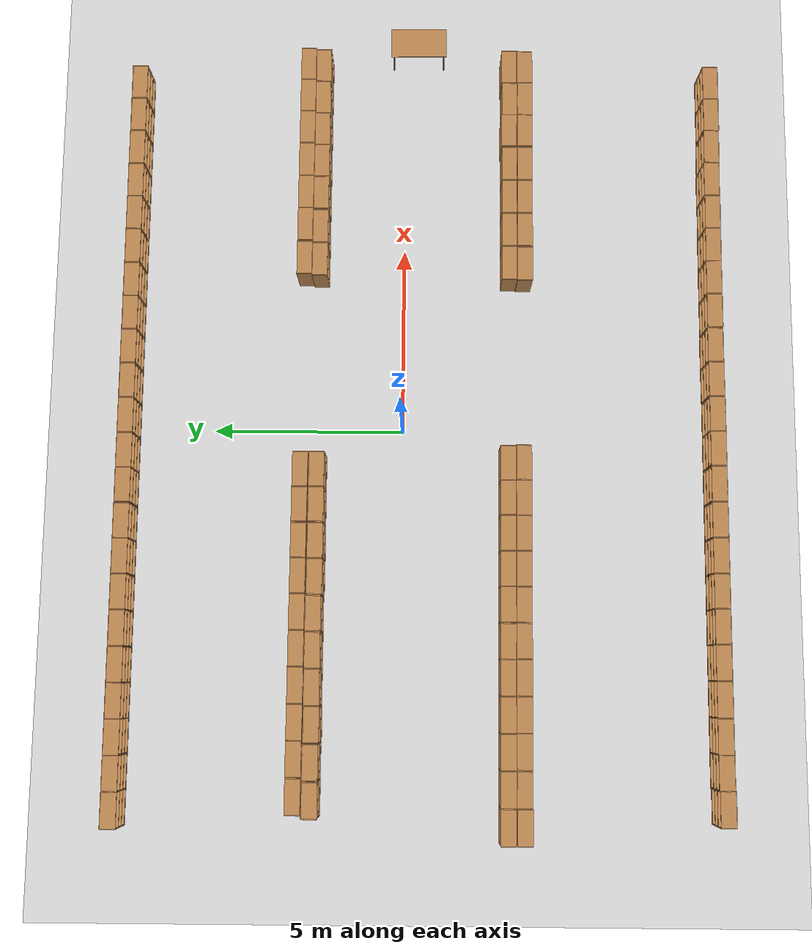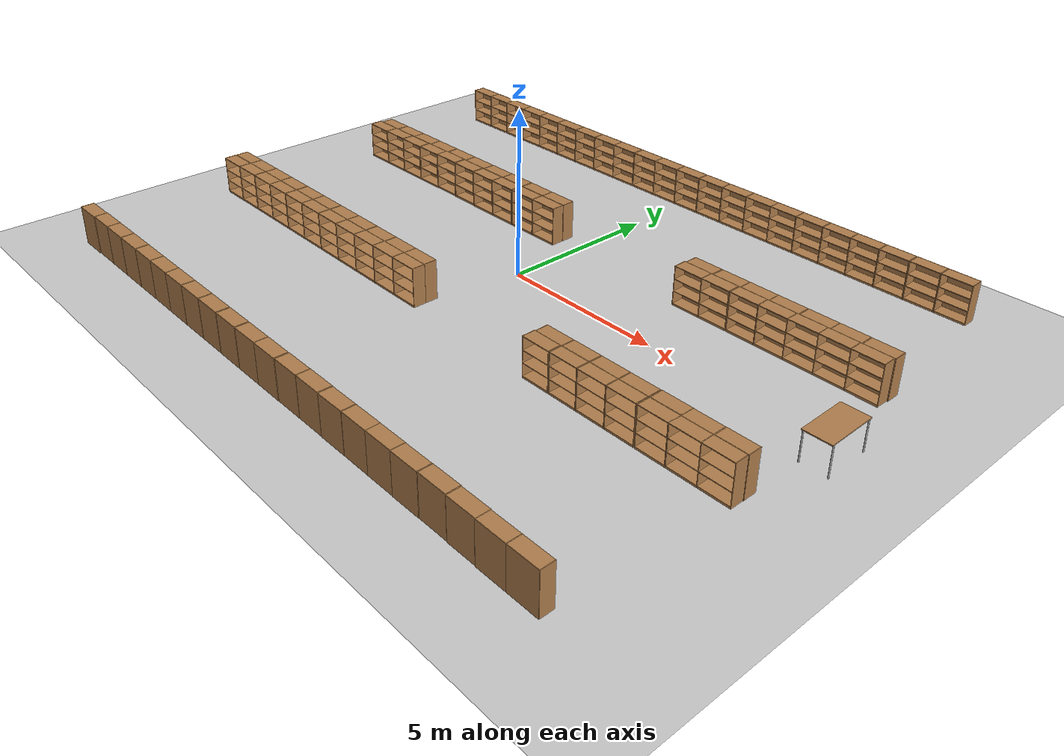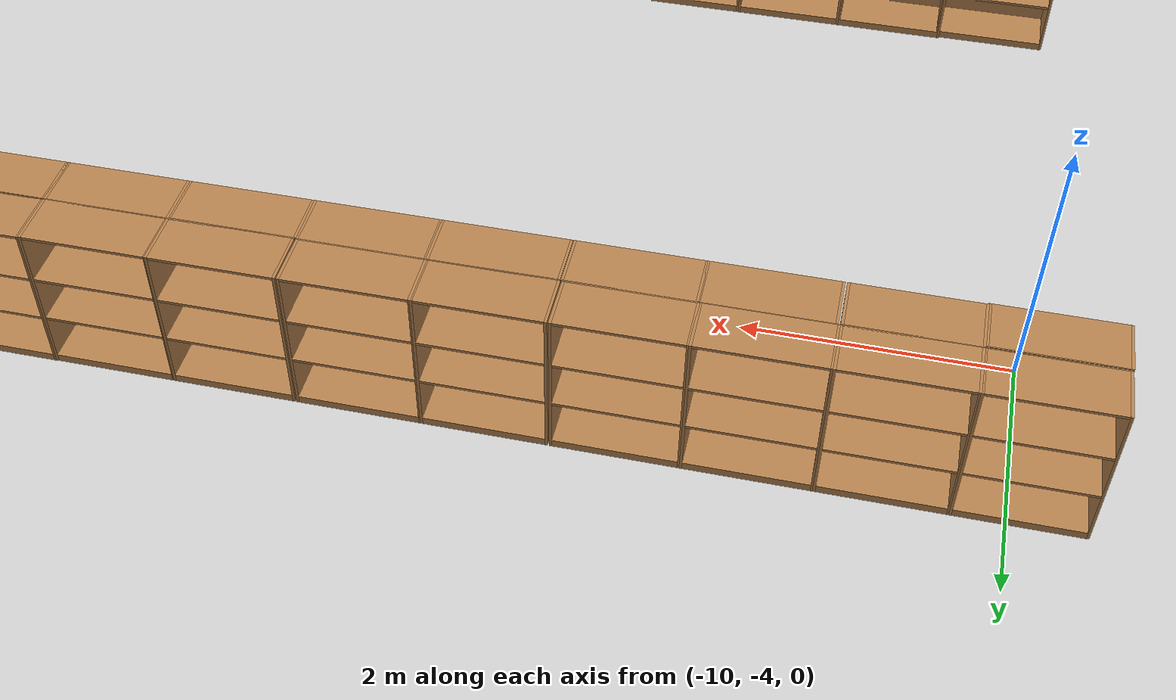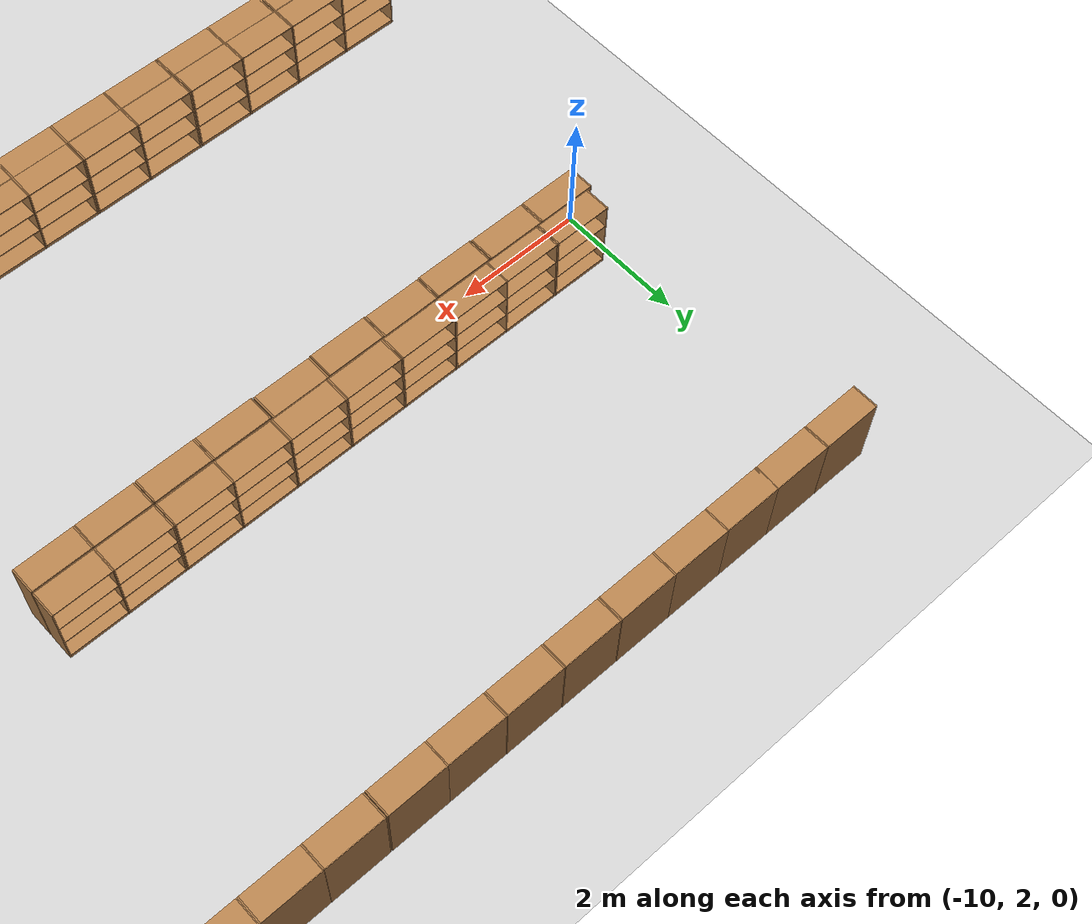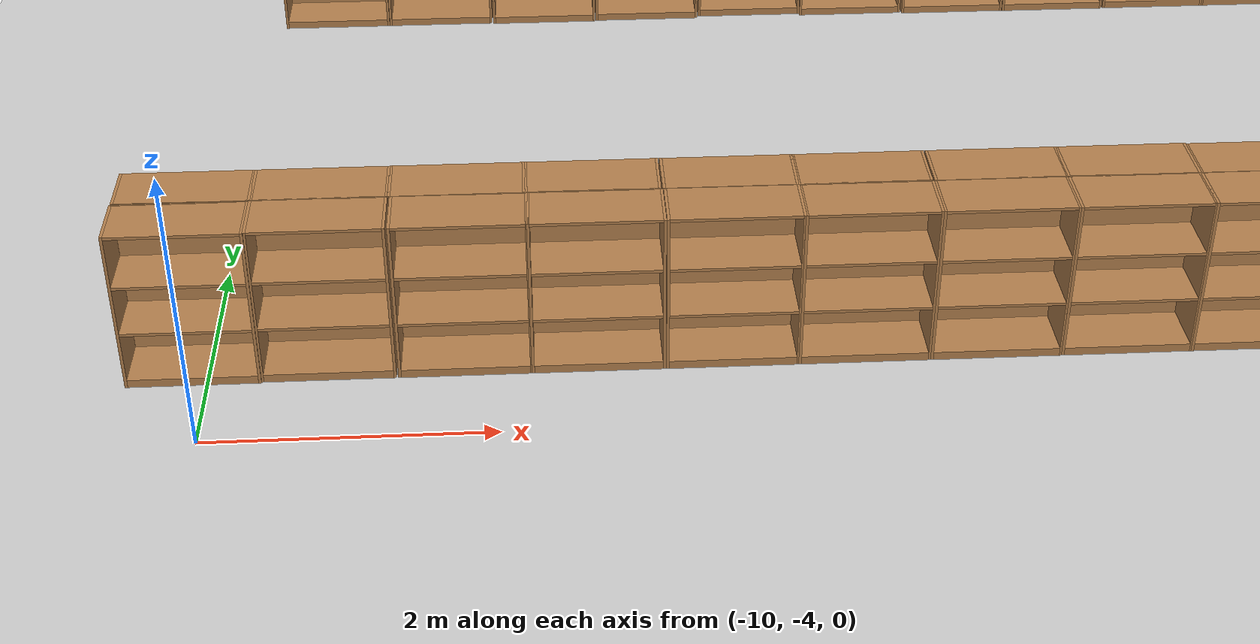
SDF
<sdf version="1.7">
 <world name="default">
  <model name="ground_plane">
   <static>1</static>
   <link name="link">
    <collision name="collision">
     <geometry><plane><normal>0 0 1</normal><size>100 100</size></plane></geometry>
     <surface><friction><ode><mu>100</mu><mu2>50</mu2></ode></friction></surface>
    </collision>
    <visual name="visual">
     <cast_shadows>0</cast_shadows>
     <geometry><plane><normal>0 0 1</normal><size>100 100</size></plane></geometry>
     <material>
      <script><uri>file://media/materials/scripts/gazebo.material</uri><name>Gazebo/Grey</name></script>
     </material>
    </visual>
   </link>
  </model>
  <light name="sun" type="directional">
   <pose>0 0 10 0 -0 0</pose>
   <diffuse>0.8 0.8 0.8 1</diffuse>
   <specular>0.2 0.2 0.2 1</specular>
   <attenuation>
    <range>1000</range>
    <constant>0.9</constant>
    <linear>0.01</linear>
    <quadratic>0.001</quadratic>
   </attenuation>
   <direction>-0.5 0.1 -0.9</direction>
   <spot><inner_angle>0</inner_angle><outer_angle>0</outer_angle><falloff>0</falloff></spot>
  </light>
  <scene><shadows>0</shadows><ambient>0.4 0.4 0.4 1</ambient><background>0.7 0.7 0.7 1</background></scene>
  <physics type="ode">
   <real_time_update_rate>1000</real_time_update_rate>
   <max_step_size>0.001</max_step_size>
   <real_time_factor>1</real_time_factor>
   <ode>
    <solver>
     <type>quick</type>
     <iters>150</iters>
     <precon_iters>0</precon_iters>
     <sor>1.4</sor>
     <use_dynamic_moi_rescaling>1</use_dynamic_moi_rescaling>
    </solver>
    <constraints>
     <cfm>1e-05</cfm>
     <erp>0.2</erp>
     <contact_max_correcting_vel>2000</contact_max_correcting_vel>
     <contact_surface_layer>0.01</contact_surface_layer>
    </constraints>
   </ode>
  </physics>
  <plugin name="gazebo_ros_state" filename="libgazebo_ros_state.so">
   <ros><namespace>/gazebo</namespace></ros>
   <update_rate>1.0</update_rate>
  </plugin>
  <gravity>0 0 -9.8</gravity>
  <magnetic_field>6e-06 2.3e-05 -4.2e-05</magnetic_field>
  <atmosphere type="adiabatic"/>
  <audio><device>default</device></audio>
  <spherical_coordinates>
   <surface_model>EARTH_WGS84</surface_model>
   <latitude_deg>0</latitude_deg>
   <longitude_deg>0</longitude_deg>
   <elevation>0</elevation>
   <heading_deg>0</heading_deg>
  </spherical_coordinates>
  <model name="bookshelf">
   <static>1</static>
   <link name="link">
    <inertial><mass>1</mass></inertial>
    <collision name="back">
     <pose>0 0.005 0.6 0 -0 0</pose>
     <geometry><box><size>0.9 0.01 1.2</size></box></geometry>
    </collision>
    <visual name="visual1">
     <pose>0 0.005 0.6 0 -0 0</pose>
     <geometry><box><size>0.9 0.01 1.2</size></box></geometry>
     <material>
      <script><uri>file://media/materials/scripts/gazebo.material</uri><name>Gazebo/Wood</name></script>
     </material>
    </visual>
    <collision name="left_side">
     <pose>0.45 -0.195 0.6 0 -0 0</pose>
     <geometry><box><size>0.02 0.4 1.2</size></box></geometry>
    </collision>
    <visual name="visual2">
     <pose>0.45 -0.195 0.6 0 -0 0</pose>
     <geometry><box><size>0.02 0.4 1.2</size></box></geometry>
     <material>
      <script><uri>file://media/materials/scripts/gazebo.material</uri><name>Gazebo/Wood</name></script>
     </material>
    </visual>
    <collision name="right_side">
     <pose>-0.45 -0.195 0.6 0 -0 0</pose>
     <geometry><box><size>0.02 0.4 1.2</size></box></geometry>
    </collision>
    <visual name="visual3">
     <pose>-0.45 -0.195 0.6 0 -0 0</pose>
     <geometry><box><size>0.02 0.4 1.2</size></box></geometry>
     <material>
      <script><uri>file://media/materials/scripts/gazebo.material</uri><name>Gazebo/Wood</name></script>
     </material>
    </visual>
    <collision name="bottom">
     <pose>0 -0.195 0.03 0 -0 0</pose>
     <geometry><box><size>0.88 0.4 0.06</size></box></geometry>
    </collision>
    <visual name="visual4">
     <pose>0 -0.195 0.03 0 -0 0</pose>
     <geometry><box><size>0.88 0.4 0.06</size></box></geometry>
     <material>
      <script><uri>file://media/materials/scripts/gazebo.material</uri><name>Gazebo/Wood</name></script>
     </material>
    </visual>
    <collision name="top">
     <pose>0 -0.195 1.19 0 -0 0</pose>
     <geometry><box><size>0.88 0.4 0.02</size></box></geometry>
    </collision>
    <visual name="visual5">
     <pose>0 -0.195 1.19 0 -0 0</pose>
     <geometry><box><size>0.88 0.4 0.02</size></box></geometry>
     <material>
      <script><uri>file://media/materials/scripts/gazebo.material</uri><name>Gazebo/Wood</name></script>
     </material>
    </visual>
    <collision name="low_shelf">
     <pose>0 -0.195 0.43 0 -0 0</pose>
     <geometry><box><size>0.88 0.4 0.02</size></box></geometry>
    </collision>
    <visual name="visual6">
     <pose>0 -0.195 0.43 0 -0 0</pose>
     <geometry><box><size>0.88 0.4 0.02</size></box></geometry>
     <material>
      <script><uri>file://media/materials/scripts/gazebo.material</uri><name>Gazebo/Wood</name></script>
     </material>
    </visual>
    <collision name="high_shelf">
     <pose>0 -0.195 0.8 0 -0 0</pose>
     <geometry><box><size>0.88 0.4 0.02</size></box></geometry>
    </collision>
    <visual name="visual7">
     <pose>0 -0.195 0.8 0 -0 0</pose>
     <geometry><box><size>0.88 0.4 0.02</size></box></geometry>
     <material>
      <script><uri>file://media/materials/scripts/gazebo.material</uri><name>Gazebo/Wood</name></script>
     </material>
    </visual>
   </link>
   <pose>-0.509028 -8.39134 0 0 0 -3.14107</pose>
  </model>
  <model name="bookshelf_clone">
   <static>1</static>
   <link name="link">
    <inertial><mass>1</mass></inertial>
    <collision name="back">
     <pose>0 0.005 0.6 0 -0 0</pose>
     <geometry><box><size>0.9 0.01 1.2</size></box></geometry>
    </collision>
    <visual name="visual1">
     <pose>0 0.005 0.6 0 -0 0</pose>
     <geometry><box><size>0.9 0.01 1.2</size></box></geometry>
     <material>
      <script><uri>file://media/materials/scripts/gazebo.material</uri><name>Gazebo/Wood</name></script>
     </material>
    </visual>
    <collision name="left_side">
     <pose>0.45 -0.195 0.6 0 -0 0</pose>
     <geometry><box><size>0.02 0.4 1.2</size></box></geometry>
    </collision>
    <visual name="visual2">
     <pose>0.45 -0.195 0.6 0 -0 0</pose>
     <geometry><box><size>0.02 0.4 1.2</size></box></geometry>
     <material>
      <script><uri>file://media/materials/scripts/gazebo.material</uri><name>Gazebo/Wood</name></script>
     </material>
    </visual>
    <collision name="right_side">
     <pose>-0.45 -0.195 0.6 0 -0 0</pose>
     <geometry><box><size>0.02 0.4 1.2</size></box></geometry>
    </collision>
    <visual name="visual3">
     <pose>-0.45 -0.195 0.6 0 -0 0</pose>
     <geometry><box><size>0.02 0.4 1.2</size></box></geometry>
     <material>
      <script><uri>file://media/materials/scripts/gazebo.material</uri><name>Gazebo/Wood</name></script>
     </material>
    </visual>
    <collision name="bottom">
     <pose>0 -0.195 0.03 0 -0 0</pose>
     <geometry><box><size>0.88 0.4 0.06</size></box></geometry>
    </collision>
    <visual name="visual4">
     <pose>0 -0.195 0.03 0 -0 0</pose>
     <geometry><box><size>0.88 0.4 0.06</size></box></geometry>
     <material>
      <script><uri>file://media/materials/scripts/gazebo.material</uri><name>Gazebo/Wood</name></script>
     </material>
    </visual>
    <collision name="top">
     <pose>0 -0.195 1.19 0 -0 0</pose>
     <geometry><box><size>0.88 0.4 0.02</size></box></geometry>
    </collision>
    <visual name="visual5">
     <pose>0 -0.195 1.19 0 -0 0</pose>
     <geometry><box><size>0.88 0.4 0.02</size></box></geometry>
     <material>
      <script><uri>file://media/materials/scripts/gazebo.material</uri><name>Gazebo/Wood</name></script>
     </material>
    </visual>
    <collision name="low_shelf">
     <pose>0 -0.195 0.43 0 -0 0</pose>
     <geometry><box><size>0.88 0.4 0.02</size></box></geometry>
    </collision>
    <visual name="visual6">
     <pose>0 -0.195 0.43 0 -0 0</pose>
     <geometry><box><size>0.88 0.4 0.02</size></box></geometry>
     <material>
      <script><uri>file://media/materials/scripts/gazebo.material</uri><name>Gazebo/Wood</name></script>
     </material>
    </visual>
    <collision name="high_shelf">
     <pose>0 -0.195 0.8 0 -0 0</pose>
     <geometry><box><size>0.88 0.4 0.02</size></box></geometry>
    </collision>
    <visual name="visual7">
     <pose>0 -0.195 0.8 0 -0 0</pose>
     <geometry><box><size>0.88 0.4 0.02</size></box></geometry>
     <material>
      <script><uri>file://media/materials/scripts/gazebo.material</uri><name>Gazebo/Wood</name></script>
     </material>
    </visual>
   </link>
   <pose>0.39286 -8.39134 0 0 0 -3.14107</pose>
  </model>
  <model name="bookshelf_clone_0">
   <static>1</static>
   <link name="link">
    <inertial><mass>1</mass></inertial>
    <collision name="back">
     <pose>0 0.005 0.6 0 -0 0</pose>
     <geometry><box><size>0.9 0.01 1.2</size></box></geometry>
    </collision>
    <visual name="visual1">
     <pose>0 0.005 0.6 0 -0 0</pose>
     <geometry><box><size>0.9 0.01 1.2</size></box></geometry>
     <material>
      <script><uri>file://media/materials/scripts/gazebo.material</uri><name>Gazebo/Wood</name></script>
     </material>
    </visual>
    <collision name="left_side">
     <pose>0.45 -0.195 0.6 0 -0 0</pose>
     <geometry><box><size>0.02 0.4 1.2</size></box></geometry>
    </collision>
    <visual name="visual2">
     <pose>0.45 -0.195 0.6 0 -0 0</pose>
     <geometry><box><size>0.02 0.4 1.2</size></box></geometry>
     <material>
      <script><uri>file://media/materials/scripts/gazebo.material</uri><name>Gazebo/Wood</name></script>
     </material>
    </visual>
    <collision name="right_side">
     <pose>-0.45 -0.195 0.6 0 -0 0</pose>
     <geometry><box><size>0.02 0.4 1.2</size></box></geometry>
    </collision>
    <visual name="visual3">
     <pose>-0.45 -0.195 0.6 0 -0 0</pose>
     <geometry><box><size>0.02 0.4 1.2</size></box></geometry>
     <material>
      <script><uri>file://media/materials/scripts/gazebo.material</uri><name>Gazebo/Wood</name></script>
     </material>
    </visual>
    <collision name="bottom">
     <pose>0 -0.195 0.03 0 -0 0</pose>
     <geometry><box><size>0.88 0.4 0.06</size></box></geometry>
    </collision>
    <visual name="visual4">
     <pose>0 -0.195 0.03 0 -0 0</pose>
     <geometry><box><size>0.88 0.4 0.06</size></box></geometry>
     <material>
      <script><uri>file://media/materials/scripts/gazebo.material</uri><name>Gazebo/Wood</name></script>
     </material>
    </visual>
    <collision name="top">
     <pose>0 -0.195 1.19 0 -0 0</pose>
     <geometry><box><size>0.88 0.4 0.02</size></box></geometry>
    </collision>
    <visual name="visual5">
     <pose>0 -0.195 1.19 0 -0 0</pose>
     <geometry><box><size>0.88 0.4 0.02</size></box></geometry>
     <material>
      <script><uri>file://media/materials/scripts/gazebo.material</uri><name>Gazebo/Wood</name></script>
     </material>
    </visual>
    <collision name="low_shelf">
     <pose>0 -0.195 0.43 0 -0 0</pose>
     <geometry><box><size>0.88 0.4 0.02</size></box></geometry>
    </collision>
    <visual name="visual6">
     <pose>0 -0.195 0.43 0 -0 0</pose>
     <geometry><box><size>0.88 0.4 0.02</size></box></geometry>
     <material>
      <script><uri>file://media/materials/scripts/gazebo.material</uri><name>Gazebo/Wood</name></script>
     </material>
    </visual>
    <collision name="high_shelf">
     <pose>0 -0.195 0.8 0 -0 0</pose>
     <geometry><box><size>0.88 0.4 0.02</size></box></geometry>
    </collision>
    <visual name="visual7">
     <pose>0 -0.195 0.8 0 -0 0</pose>
     <geometry><box><size>0.88 0.4 0.02</size></box></geometry>
     <material>
      <script><uri>file://media/materials/scripts/gazebo.material</uri><name>Gazebo/Wood</name></script>
     </material>
    </visual>
   </link>
   <pose>-1.44106 -8.39134 0 0 0 -3.14107</pose>
  </model>
  <model name="bookshelf_clone_0_clone">
   <static>1</static>
   <link name="link">
    <inertial><mass>1</mass></inertial>
    <collision name="back">
     <pose>0 0.005 0.6 0 -0 0</pose>
     <geometry><box><size>0.9 0.01 1.2</size></box></geometry>
    </collision>
    <visual name="visual1">
     <pose>0 0.005 0.6 0 -0 0</pose>
     <geometry><box><size>0.9 0.01 1.2</size></box></geometry>
     <material>
      <script><uri>file://media/materials/scripts/gazebo.material</uri><name>Gazebo/Wood</name></script>
     </material>
    </visual>
    <collision name="left_side">
     <pose>0.45 -0.195 0.6 0 -0 0</pose>
     <geometry><box><size>0.02 0.4 1.2</size></box></geometry>
    </collision>
    <visual name="visual2">
     <pose>0.45 -0.195 0.6 0 -0 0</pose>
     <geometry><box><size>0.02 0.4 1.2</size></box></geometry>
     <material>
      <script><uri>file://media/materials/scripts/gazebo.material</uri><name>Gazebo/Wood</name></script>
     </material>
    </visual>
    <collision name="right_side">
     <pose>-0.45 -0.195 0.6 0 -0 0</pose>
     <geometry><box><size>0.02 0.4 1.2</size></box></geometry>
    </collision>
    <visual name="visual3">
     <pose>-0.45 -0.195 0.6 0 -0 0</pose>
     <geometry><box><size>0.02 0.4 1.2</size></box></geometry>
     <material>
      <script><uri>file://media/materials/scripts/gazebo.material</uri><name>Gazebo/Wood</name></script>
     </material>
    </visual>
    <collision name="bottom">
     <pose>0 -0.195 0.03 0 -0 0</pose>
     <geometry><box><size>0.88 0.4 0.06</size></box></geometry>
    </collision>
    <visual name="visual4">
     <pose>0 -0.195 0.03 0 -0 0</pose>
     <geometry><box><size>0.88 0.4 0.06</size></box></geometry>
     <material>
      <script><uri>file://media/materials/scripts/gazebo.material</uri><name>Gazebo/Wood</name></script>
     </material>
    </visual>
    <collision name="top">
     <pose>0 -0.195 1.19 0 -0 0</pose>
     <geometry><box><size>0.88 0.4 0.02</size></box></geometry>
    </collision>
    <visual name="visual5">
     <pose>0 -0.195 1.19 0 -0 0</pose>
     <geometry><box><size>0.88 0.4 0.02</size></box></geometry>
     <material>
      <script><uri>file://media/materials/scripts/gazebo.material</uri><name>Gazebo/Wood</name></script>
     </material>
    </visual>
    <collision name="low_shelf">
     <pose>0 -0.195 0.43 0 -0 0</pose>
     <geometry><box><size>0.88 0.4 0.02</size></box></geometry>
    </collision>
    <visual name="visual6">
     <pose>0 -0.195 0.43 0 -0 0</pose>
     <geometry><box><size>0.88 0.4 0.02</size></box></geometry>
     <material>
      <script><uri>file://media/materials/scripts/gazebo.material</uri><name>Gazebo/Wood</name></script>
     </material>
    </visual>
    <collision name="high_shelf">
     <pose>0 -0.195 0.8 0 -0 0</pose>
     <geometry><box><size>0.88 0.4 0.02</size></box></geometry>
    </collision>
    <visual name="visual7">
     <pose>0 -0.195 0.8 0 -0 0</pose>
     <geometry><box><size>0.88 0.4 0.02</size></box></geometry>
     <material>
      <script><uri>file://media/materials/scripts/gazebo.material</uri><name>Gazebo/Wood</name></script>
     </material>
    </visual>
   </link>
   <pose>-2.37014 -8.39134 0 0 0 -3.14107</pose>
  </model>
  <model name="bookshelf_clone_0_clone_0">
   <static>1</static>
   <link name="link">
    <inertial><mass>1</mass></inertial>
    <collision name="back">
     <pose>0 0.005 0.6 0 -0 0</pose>
     <geometry><box><size>0.9 0.01 1.2</size></box></geometry>
    </collision>
    <visual name="visual1">
     <pose>0 0.005 0.6 0 -0 0</pose>
     <geometry><box><size>0.9 0.01 1.2</size></box></geometry>
     <material>
      <script><uri>file://media/materials/scripts/gazebo.material</uri><name>Gazebo/Wood</name></script>
     </material>
    </visual>
    <collision name="left_side">
     <pose>0.45 -0.195 0.6 0 -0 0</pose>
     <geometry><box><size>0.02 0.4 1.2</size></box></geometry>
    </collision>
    <visual name="visual2">
     <pose>0.45 -0.195 0.6 0 -0 0</pose>
     <geometry><box><size>0.02 0.4 1.2</size></box></geometry>
     <material>
      <script><uri>file://media/materials/scripts/gazebo.material</uri><name>Gazebo/Wood</name></script>
     </material>
    </visual>
    <collision name="right_side">
     <pose>-0.45 -0.195 0.6 0 -0 0</pose>
     <geometry><box><size>0.02 0.4 1.2</size></box></geometry>
    </collision>
    <visual name="visual3">
     <pose>-0.45 -0.195 0.6 0 -0 0</pose>
     <geometry><box><size>0.02 0.4 1.2</size></box></geometry>
     <material>
      <script><uri>file://media/materials/scripts/gazebo.material</uri><name>Gazebo/Wood</name></script>
     </material>
    </visual>
    <collision name="bottom">
     <pose>0 -0.195 0.03 0 -0 0</pose>
     <geometry><box><size>0.88 0.4 0.06</size></box></geometry>
    </collision>
    <visual name="visual4">
     <pose>0 -0.195 0.03 0 -0 0</pose>
     <geometry><box><size>0.88 0.4 0.06</size></box></geometry>
     <material>
      <script><uri>file://media/materials/scripts/gazebo.material</uri><name>Gazebo/Wood</name></script>
     </material>
    </visual>
    <collision name="top">
     <pose>0 -0.195 1.19 0 -0 0</pose>
     <geometry><box><size>0.88 0.4 0.02</size></box></geometry>
    </collision>
    <visual name="visual5">
     <pose>0 -0.195 1.19 0 -0 0</pose>
     <geometry><box><size>0.88 0.4 0.02</size></box></geometry>
     <material>
      <script><uri>file://media/materials/scripts/gazebo.material</uri><name>Gazebo/Wood</name></script>
     </material>
    </visual>
    <collision name="low_shelf">
     <pose>0 -0.195 0.43 0 -0 0</pose>
     <geometry><box><size>0.88 0.4 0.02</size></box></geometry>
    </collision>
    <visual name="visual6">
     <pose>0 -0.195 0.43 0 -0 0</pose>
     <geometry><box><size>0.88 0.4 0.02</size></box></geometry>
     <material>
      <script><uri>file://media/materials/scripts/gazebo.material</uri><name>Gazebo/Wood</name></script>
     </material>
    </visual>
    <collision name="high_shelf">
     <pose>0 -0.195 0.8 0 -0 0</pose>
     <geometry><box><size>0.88 0.4 0.02</size></box></geometry>
    </collision>
    <visual name="visual7">
     <pose>0 -0.195 0.8 0 -0 0</pose>
     <geometry><box><size>0.88 0.4 0.02</size></box></geometry>
     <material>
      <script><uri>file://media/materials/scripts/gazebo.material</uri><name>Gazebo/Wood</name></script>
     </material>
    </visual>
   </link>
   <pose>-3.28877 -8.39134 0 0 0 -3.14107</pose>
  </model>
  <model name="bookshelf_clone_0_clone_0_clone">
   <static>1</static>
   <link name="link">
    <inertial><mass>1</mass></inertial>
    <collision name="back">
     <pose>0 0.005 0.6 0 -0 0</pose>
     <geometry><box><size>0.9 0.01 1.2</size></box></geometry>
    </collision>
    <visual name="visual1">
     <pose>0 0.005 0.6 0 -0 0</pose>
     <geometry><box><size>0.9 0.01 1.2</size></box></geometry>
     <material>
      <script><uri>file://media/materials/scripts/gazebo.material</uri><name>Gazebo/Wood</name></script>
     </material>
    </visual>
    <collision name="left_side">
     <pose>0.45 -0.195 0.6 0 -0 0</pose>
     <geometry><box><size>0.02 0.4 1.2</size></box></geometry>
    </collision>
    <visual name="visual2">
     <pose>0.45 -0.195 0.6 0 -0 0</pose>
     <geometry><box><size>0.02 0.4 1.2</size></box></geometry>
     <material>
      <script><uri>file://media/materials/scripts/gazebo.material</uri><name>Gazebo/Wood</name></script>
     </material>
    </visual>
    <collision name="right_side">
     <pose>-0.45 -0.195 0.6 0 -0 0</pose>
     <geometry><box><size>0.02 0.4 1.2</size></box></geometry>
    </collision>
    <visual name="visual3">
     <pose>-0.45 -0.195 0.6 0 -0 0</pose>
     <geometry><box><size>0.02 0.4 1.2</size></box></geometry>
     <material>
      <script><uri>file://media/materials/scripts/gazebo.material</uri><name>Gazebo/Wood</name></script>
     </material>
    </visual>
    <collision name="bottom">
     <pose>0 -0.195 0.03 0 -0 0</pose>
     <geometry><box><size>0.88 0.4 0.06</size></box></geometry>
    </collision>
    <visual name="visual4">
     <pose>0 -0.195 0.03 0 -0 0</pose>
     <geometry><box><size>0.88 0.4 0.06</size></box></geometry>
     <material>
      <script><uri>file://media/materials/scripts/gazebo.material</uri><name>Gazebo/Wood</name></script>
     </material>
    </visual>
    <collision name="top">
     <pose>0 -0.195 1.19 0 -0 0</pose>
     <geometry><box><size>0.88 0.4 0.02</size></box></geometry>
    </collision>
    <visual name="visual5">
     <pose>0 -0.195 1.19 0 -0 0</pose>
     <geometry><box><size>0.88 0.4 0.02</size></box></geometry>
     <material>
      <script><uri>file://media/materials/scripts/gazebo.material</uri><name>Gazebo/Wood</name></script>
     </material>
    </visual>
    <collision name="low_shelf">
     <pose>0 -0.195 0.43 0 -0 0</pose>
     <geometry><box><size>0.88 0.4 0.02</size></box></geometry>
    </collision>
    <visual name="visual6">
     <pose>0 -0.195 0.43 0 -0 0</pose>
     <geometry><box><size>0.88 0.4 0.02</size></box></geometry>
     <material>
      <script><uri>file://media/materials/scripts/gazebo.material</uri><name>Gazebo/Wood</name></script>
     </material>
    </visual>
    <collision name="high_shelf">
     <pose>0 -0.195 0.8 0 -0 0</pose>
     <geometry><box><size>0.88 0.4 0.02</size></box></geometry>
    </collision>
    <visual name="visual7">
     <pose>0 -0.195 0.8 0 -0 0</pose>
     <geometry><box><size>0.88 0.4 0.02</size></box></geometry>
     <material>
      <script><uri>file://media/materials/scripts/gazebo.material</uri><name>Gazebo/Wood</name></script>
     </material>
    </visual>
   </link>
   <pose>-4.203 -8.39134 0 0 0 -3.14107</pose>
  </model>
  <model name="bookshelf_clone_0_clone_0_clone_clone">
   <static>1</static>
   <link name="link">
    <inertial><mass>1</mass></inertial>
    <collision name="back">
     <pose>0 0.005 0.6 0 -0 0</pose>
     <geometry><box><size>0.9 0.01 1.2</size></box></geometry>
    </collision>
    <visual name="visual1">
     <pose>0 0.005 0.6 0 -0 0</pose>
     <geometry><box><size>0.9 0.01 1.2</size></box></geometry>
     <material>
      <script><uri>file://media/materials/scripts/gazebo.material</uri><name>Gazebo/Wood</name></script>
     </material>
    </visual>
    <collision name="left_side">
     <pose>0.45 -0.195 0.6 0 -0 0</pose>
     <geometry><box><size>0.02 0.4 1.2</size></box></geometry>
    </collision>
    <visual name="visual2">
     <pose>0.45 -0.195 0.6 0 -0 0</pose>
     <geometry><box><size>0.02 0.4 1.2</size></box></geometry>
     <material>
      <script><uri>file://media/materials/scripts/gazebo.material</uri><name>Gazebo/Wood</name></script>
     </material>
    </visual>
    <collision name="right_side">
     <pose>-0.45 -0.195 0.6 0 -0 0</pose>
     <geometry><box><size>0.02 0.4 1.2</size></box></geometry>
    </collision>
    <visual name="visual3">
     <pose>-0.45 -0.195 0.6 0 -0 0</pose>
     <geometry><box><size>0.02 0.4 1.2</size></box></geometry>
     <material>
      <script><uri>file://media/materials/scripts/gazebo.material</uri><name>Gazebo/Wood</name></script>
     </material>
    </visual>
    <collision name="bottom">
     <pose>0 -0.195 0.03 0 -0 0</pose>
     <geometry><box><size>0.88 0.4 0.06</size></box></geometry>
    </collision>
    <visual name="visual4">
     <pose>0 -0.195 0.03 0 -0 0</pose>
     <geometry><box><size>0.88 0.4 0.06</size></box></geometry>
     <material>
      <script><uri>file://media/materials/scripts/gazebo.material</uri><name>Gazebo/Wood</name></script>
     </material>
    </visual>
    <collision name="top">
     <pose>0 -0.195 1.19 0 -0 0</pose>
     <geometry><box><size>0.88 0.4 0.02</size></box></geometry>
    </collision>
    <visual name="visual5">
     <pose>0 -0.195 1.19 0 -0 0</pose>
     <geometry><box><size>0.88 0.4 0.02</size></box></geometry>
     <material>
      <script><uri>file://media/materials/scripts/gazebo.material</uri><name>Gazebo/Wood</name></script>
     </material>
    </visual>
    <collision name="low_shelf">
     <pose>0 -0.195 0.43 0 -0 0</pose>
     <geometry><box><size>0.88 0.4 0.02</size></box></geometry>
    </collision>
    <visual name="visual6">
     <pose>0 -0.195 0.43 0 -0 0</pose>
     <geometry><box><size>0.88 0.4 0.02</size></box></geometry>
     <material>
      <script><uri>file://media/materials/scripts/gazebo.material</uri><name>Gazebo/Wood</name></script>
     </material>
    </visual>
    <collision name="high_shelf">
     <pose>0 -0.195 0.8 0 -0 0</pose>
     <geometry><box><size>0.88 0.4 0.02</size></box></geometry>
    </collision>
    <visual name="visual7">
     <pose>0 -0.195 0.8 0 -0 0</pose>
     <geometry><box><size>0.88 0.4 0.02</size></box></geometry>
     <material>
      <script><uri>file://media/materials/scripts/gazebo.material</uri><name>Gazebo/Wood</name></script>
     </material>
    </visual>
   </link>
   <pose>8.09166 -2.97864 0 0 0 -3.14107</pose>
  </model>
  <model name="bookshelf_clone_0_clone_0_clone_clone_clone">
   <static>1</static>
   <link name="link">
    <inertial><mass>1</mass></inertial>
    <collision name="back">
     <pose>0 0.005 0.6 0 -0 0</pose>
     <geometry><box><size>0.9 0.01 1.2</size></box></geometry>
    </collision>
    <visual name="visual1">
     <pose>0 0.005 0.6 0 -0 0</pose>
     <geometry><box><size>0.9 0.01 1.2</size></box></geometry>
     <material>
      <script><uri>file://media/materials/scripts/gazebo.material</uri><name>Gazebo/Wood</name></script>
     </material>
    </visual>
    <collision name="left_side">
     <pose>0.45 -0.195 0.6 0 -0 0</pose>
     <geometry><box><size>0.02 0.4 1.2</size></box></geometry>
    </collision>
    <visual name="visual2">
     <pose>0.45 -0.195 0.6 0 -0 0</pose>
     <geometry><box><size>0.02 0.4 1.2</size></box></geometry>
     <material>
      <script><uri>file://media/materials/scripts/gazebo.material</uri><name>Gazebo/Wood</name></script>
     </material>
    </visual>
    <collision name="right_side">
     <pose>-0.45 -0.195 0.6 0 -0 0</pose>
     <geometry><box><size>0.02 0.4 1.2</size></box></geometry>
    </collision>
    <visual name="visual3">
     <pose>-0.45 -0.195 0.6 0 -0 0</pose>
     <geometry><box><size>0.02 0.4 1.2</size></box></geometry>
     <material>
      <script><uri>file://media/materials/scripts/gazebo.material</uri><name>Gazebo/Wood</name></script>
     </material>
    </visual>
    <collision name="bottom">
     <pose>0 -0.195 0.03 0 -0 0</pose>
     <geometry><box><size>0.88 0.4 0.06</size></box></geometry>
    </collision>
    <visual name="visual4">
     <pose>0 -0.195 0.03 0 -0 0</pose>
     <geometry><box><size>0.88 0.4 0.06</size></box></geometry>
     <material>
      <script><uri>file://media/materials/scripts/gazebo.material</uri><name>Gazebo/Wood</name></script>
     </material>
    </visual>
    <collision name="top">
     <pose>0 -0.195 1.19 0 -0 0</pose>
     <geometry><box><size>0.88 0.4 0.02</size></box></geometry>
    </collision>
    <visual name="visual5">
     <pose>0 -0.195 1.19 0 -0 0</pose>
     <geometry><box><size>0.88 0.4 0.02</size></box></geometry>
     <material>
      <script><uri>file://media/materials/scripts/gazebo.material</uri><name>Gazebo/Wood</name></script>
     </material>
    </visual>
    <collision name="low_shelf">
     <pose>0 -0.195 0.43 0 -0 0</pose>
     <geometry><box><size>0.88 0.4 0.02</size></box></geometry>
    </collision>
    <visual name="visual6">
     <pose>0 -0.195 0.43 0 -0 0</pose>
     <geometry><box><size>0.88 0.4 0.02</size></box></geometry>
     <material>
      <script><uri>file://media/materials/scripts/gazebo.material</uri><name>Gazebo/Wood</name></script>
     </material>
    </visual>
    <collision name="high_shelf">
     <pose>0 -0.195 0.8 0 -0 0</pose>
     <geometry><box><size>0.88 0.4 0.02</size></box></geometry>
    </collision>
    <visual name="visual7">
     <pose>0 -0.195 0.8 0 -0 0</pose>
     <geometry><box><size>0.88 0.4 0.02</size></box></geometry>
     <material>
      <script><uri>file://media/materials/scripts/gazebo.material</uri><name>Gazebo/Wood</name></script>
     </material>
    </visual>
   </link>
   <pose>6.23979 -2.98685 0 0 0 -3.14107</pose>
  </model>
  <model name="bookshelf_clone_0_clone_0_clone_clone_clone_clone">
   <static>1</static>
   <link name="link">
    <inertial><mass>1</mass></inertial>
    <collision name="back">
     <pose>0 0.005 0.6 0 -0 0</pose>
     <geometry><box><size>0.9 0.01 1.2</size></box></geometry>
    </collision>
    <visual name="visual1">
     <pose>0 0.005 0.6 0 -0 0</pose>
     <geometry><box><size>0.9 0.01 1.2</size></box></geometry>
     <material>
      <script><uri>file://media/materials/scripts/gazebo.material</uri><name>Gazebo/Wood</name></script>
     </material>
    </visual>
    <collision name="left_side">
     <pose>0.45 -0.195 0.6 0 -0 0</pose>
     <geometry><box><size>0.02 0.4 1.2</size></box></geometry>
    </collision>
    <visual name="visual2">
     <pose>0.45 -0.195 0.6 0 -0 0</pose>
     <geometry><box><size>0.02 0.4 1.2</size></box></geometry>
     <material>
      <script><uri>file://media/materials/scripts/gazebo.material</uri><name>Gazebo/Wood</name></script>
     </material>
    </visual>
    <collision name="right_side">
     <pose>-0.45 -0.195 0.6 0 -0 0</pose>
     <geometry><box><size>0.02 0.4 1.2</size></box></geometry>
    </collision>
    <visual name="visual3">
     <pose>-0.45 -0.195 0.6 0 -0 0</pose>
     <geometry><box><size>0.02 0.4 1.2</size></box></geometry>
     <material>
      <script><uri>file://media/materials/scripts/gazebo.material</uri><name>Gazebo/Wood</name></script>
     </material>
    </visual>
    <collision name="bottom">
     <pose>0 -0.195 0.03 0 -0 0</pose>
     <geometry><box><size>0.88 0.4 0.06</size></box></geometry>
    </collision>
    <visual name="visual4">
     <pose>0 -0.195 0.03 0 -0 0</pose>
     <geometry><box><size>0.88 0.4 0.06</size></box></geometry>
     <material>
      <script><uri>file://media/materials/scripts/gazebo.material</uri><name>Gazebo/Wood</name></script>
     </material>
    </visual>
    <collision name="top">
     <pose>0 -0.195 1.19 0 -0 0</pose>
     <geometry><box><size>0.88 0.4 0.02</size></box></geometry>
    </collision>
    <visual name="visual5">
     <pose>0 -0.195 1.19 0 -0 0</pose>
     <geometry><box><size>0.88 0.4 0.02</size></box></geometry>
     <material>
      <script><uri>file://media/materials/scripts/gazebo.material</uri><name>Gazebo/Wood</name></script>
     </material>
    </visual>
    <collision name="low_shelf">
     <pose>0 -0.195 0.43 0 -0 0</pose>
     <geometry><box><size>0.88 0.4 0.02</size></box></geometry>
    </collision>
    <visual name="visual6">
     <pose>0 -0.195 0.43 0 -0 0</pose>
     <geometry><box><size>0.88 0.4 0.02</size></box></geometry>
     <material>
      <script><uri>file://media/materials/scripts/gazebo.material</uri><name>Gazebo/Wood</name></script>
     </material>
    </visual>
    <collision name="high_shelf">
     <pose>0 -0.195 0.8 0 -0 0</pose>
     <geometry><box><size>0.88 0.4 0.02</size></box></geometry>
    </collision>
    <visual name="visual7">
     <pose>0 -0.195 0.8 0 -0 0</pose>
     <geometry><box><size>0.88 0.4 0.02</size></box></geometry>
     <material>
      <script><uri>file://media/materials/scripts/gazebo.material</uri><name>Gazebo/Wood</name></script>
     </material>
    </visual>
   </link>
   <pose>7.1578 -2.98828 0 0 0 -3.14107</pose>
  </model>
  <model name="bookshelf_clone_0_clone_0_clone_clone_clone_clone_clone">
   <static>1</static>
   <link name="link">
    <inertial><mass>1</mass></inertial>
    <collision name="back">
     <pose>0 0.005 0.6 0 -0 0</pose>
     <geometry><box><size>0.9 0.01 1.2</size></box></geometry>
    </collision>
    <visual name="visual1">
     <pose>0 0.005 0.6 0 -0 0</pose>
     <geometry><box><size>0.9 0.01 1.2</size></box></geometry>
     <material>
      <script><uri>file://media/materials/scripts/gazebo.material</uri><name>Gazebo/Wood</name></script>
     </material>
    </visual>
    <collision name="left_side">
     <pose>0.45 -0.195 0.6 0 -0 0</pose>
     <geometry><box><size>0.02 0.4 1.2</size></box></geometry>
    </collision>
    <visual name="visual2">
     <pose>0.45 -0.195 0.6 0 -0 0</pose>
     <geometry><box><size>0.02 0.4 1.2</size></box></geometry>
     <material>
      <script><uri>file://media/materials/scripts/gazebo.material</uri><name>Gazebo/Wood</name></script>
     </material>
    </visual>
    <collision name="right_side">
     <pose>-0.45 -0.195 0.6 0 -0 0</pose>
     <geometry><box><size>0.02 0.4 1.2</size></box></geometry>
    </collision>
    <visual name="visual3">
     <pose>-0.45 -0.195 0.6 0 -0 0</pose>
     <geometry><box><size>0.02 0.4 1.2</size></box></geometry>
     <material>
      <script><uri>file://media/materials/scripts/gazebo.material</uri><name>Gazebo/Wood</name></script>
     </material>
    </visual>
    <collision name="bottom">
     <pose>0 -0.195 0.03 0 -0 0</pose>
     <geometry><box><size>0.88 0.4 0.06</size></box></geometry>
    </collision>
    <visual name="visual4">
     <pose>0 -0.195 0.03 0 -0 0</pose>
     <geometry><box><size>0.88 0.4 0.06</size></box></geometry>
     <material>
      <script><uri>file://media/materials/scripts/gazebo.material</uri><name>Gazebo/Wood</name></script>
     </material>
    </visual>
    <collision name="top">
     <pose>0 -0.195 1.19 0 -0 0</pose>
     <geometry><box><size>0.88 0.4 0.02</size></box></geometry>
    </collision>
    <visual name="visual5">
     <pose>0 -0.195 1.19 0 -0 0</pose>
     <geometry><box><size>0.88 0.4 0.02</size></box></geometry>
     <material>
      <script><uri>file://media/materials/scripts/gazebo.material</uri><name>Gazebo/Wood</name></script>
     </material>
    </visual>
    <collision name="low_shelf">
     <pose>0 -0.195 0.43 0 -0 0</pose>
     <geometry><box><size>0.88 0.4 0.02</size></box></geometry>
    </collision>
    <visual name="visual6">
     <pose>0 -0.195 0.43 0 -0 0</pose>
     <geometry><box><size>0.88 0.4 0.02</size></box></geometry>
     <material>
      <script><uri>file://media/materials/scripts/gazebo.material</uri><name>Gazebo/Wood</name></script>
     </material>
    </visual>
    <collision name="high_shelf">
     <pose>0 -0.195 0.8 0 -0 0</pose>
     <geometry><box><size>0.88 0.4 0.02</size></box></geometry>
    </collision>
    <visual name="visual7">
     <pose>0 -0.195 0.8 0 -0 0</pose>
     <geometry><box><size>0.88 0.4 0.02</size></box></geometry>
     <material>
      <script><uri>file://media/materials/scripts/gazebo.material</uri><name>Gazebo/Wood</name></script>
     </material>
    </visual>
   </link>
   <pose>-0.940238 -2.94994 0 0 0 -3.14107</pose>
  </model>
  <model name="bookshelf_clone_0_clone_0_clone_clone_clone_clone_clone_0">
   <static>1</static>
   <link name="link">
    <inertial><mass>1</mass></inertial>
    <collision name="back">
     <pose>0 0.005 0.6 0 -0 0</pose>
     <geometry><box><size>0.9 0.01 1.2</size></box></geometry>
    </collision>
    <visual name="visual1">
     <pose>0 0.005 0.6 0 -0 0</pose>
     <geometry><box><size>0.9 0.01 1.2</size></box></geometry>
     <material>
      <script><uri>file://media/materials/scripts/gazebo.material</uri><name>Gazebo/Wood</name></script>
     </material>
    </visual>
    <collision name="left_side">
     <pose>0.45 -0.195 0.6 0 -0 0</pose>
     <geometry><box><size>0.02 0.4 1.2</size></box></geometry>
    </collision>
    <visual name="visual2">
     <pose>0.45 -0.195 0.6 0 -0 0</pose>
     <geometry><box><size>0.02 0.4 1.2</size></box></geometry>
     <material>
      <script><uri>file://media/materials/scripts/gazebo.material</uri><name>Gazebo/Wood</name></script>
     </material>
    </visual>
    <collision name="right_side">
     <pose>-0.45 -0.195 0.6 0 -0 0</pose>
     <geometry><box><size>0.02 0.4 1.2</size></box></geometry>
    </collision>
    <visual name="visual3">
     <pose>-0.45 -0.195 0.6 0 -0 0</pose>
     <geometry><box><size>0.02 0.4 1.2</size></box></geometry>
     <material>
      <script><uri>file://media/materials/scripts/gazebo.material</uri><name>Gazebo/Wood</name></script>
     </material>
    </visual>
    <collision name="bottom">
     <pose>0 -0.195 0.03 0 -0 0</pose>
     <geometry><box><size>0.88 0.4 0.06</size></box></geometry>
    </collision>
    <visual name="visual4">
     <pose>0 -0.195 0.03 0 -0 0</pose>
     <geometry><box><size>0.88 0.4 0.06</size></box></geometry>
     <material>
      <script><uri>file://media/materials/scripts/gazebo.material</uri><name>Gazebo/Wood</name></script>
     </material>
    </visual>
    <collision name="top">
     <pose>0 -0.195 1.19 0 -0 0</pose>
     <geometry><box><size>0.88 0.4 0.02</size></box></geometry>
    </collision>
    <visual name="visual5">
     <pose>0 -0.195 1.19 0 -0 0</pose>
     <geometry><box><size>0.88 0.4 0.02</size></box></geometry>
     <material>
      <script><uri>file://media/materials/scripts/gazebo.material</uri><name>Gazebo/Wood</name></script>
     </material>
    </visual>
    <collision name="low_shelf">
     <pose>0 -0.195 0.43 0 -0 0</pose>
     <geometry><box><size>0.88 0.4 0.02</size></box></geometry>
    </collision>
    <visual name="visual6">
     <pose>0 -0.195 0.43 0 -0 0</pose>
     <geometry><box><size>0.88 0.4 0.02</size></box></geometry>
     <material>
      <script><uri>file://media/materials/scripts/gazebo.material</uri><name>Gazebo/Wood</name></script>
     </material>
    </visual>
    <collision name="high_shelf">
     <pose>0 -0.195 0.8 0 -0 0</pose>
     <geometry><box><size>0.88 0.4 0.02</size></box></geometry>
    </collision>
    <visual name="visual7">
     <pose>0 -0.195 0.8 0 -0 0</pose>
     <geometry><box><size>0.88 0.4 0.02</size></box></geometry>
     <material>
      <script><uri>file://media/materials/scripts/gazebo.material</uri><name>Gazebo/Wood</name></script>
     </material>
    </visual>
   </link>
   <pose>-1.84141 -2.94994 0 0 0 -3.14107</pose>
  </model>
  <model name="bookshelf_clone_0_clone_0_clone_clone_clone_clone_clone_1">
   <static>1</static>
   <link name="link">
    <inertial><mass>1</mass></inertial>
    <collision name="back">
     <pose>0 0.005 0.6 0 -0 0</pose>
     <geometry><box><size>0.9 0.01 1.2</size></box></geometry>
    </collision>
    <visual name="visual1">
     <pose>0 0.005 0.6 0 -0 0</pose>
     <geometry><box><size>0.9 0.01 1.2</size></box></geometry>
     <material>
      <script><uri>file://media/materials/scripts/gazebo.material</uri><name>Gazebo/Wood</name></script>
     </material>
    </visual>
    <collision name="left_side">
     <pose>0.45 -0.195 0.6 0 -0 0</pose>
     <geometry><box><size>0.02 0.4 1.2</size></box></geometry>
    </collision>
    <visual name="visual2">
     <pose>0.45 -0.195 0.6 0 -0 0</pose>
     <geometry><box><size>0.02 0.4 1.2</size></box></geometry>
     <material>
      <script><uri>file://media/materials/scripts/gazebo.material</uri><name>Gazebo/Wood</name></script>
     </material>
    </visual>
    <collision name="right_side">
     <pose>-0.45 -0.195 0.6 0 -0 0</pose>
     <geometry><box><size>0.02 0.4 1.2</size></box></geometry>
    </collision>
    <visual name="visual3">
     <pose>-0.45 -0.195 0.6 0 -0 0</pose>
     <geometry><box><size>0.02 0.4 1.2</size></box></geometry>
     <material>
      <script><uri>file://media/materials/scripts/gazebo.material</uri><name>Gazebo/Wood</name></script>
     </material>
    </visual>
    <collision name="bottom">
     <pose>0 -0.195 0.03 0 -0 0</pose>
     <geometry><box><size>0.88 0.4 0.06</size></box></geometry>
    </collision>
    <visual name="visual4">
     <pose>0 -0.195 0.03 0 -0 0</pose>
     <geometry><box><size>0.88 0.4 0.06</size></box></geometry>
     <material>
      <script><uri>file://media/materials/scripts/gazebo.material</uri><name>Gazebo/Wood</name></script>
     </material>
    </visual>
    <collision name="top">
     <pose>0 -0.195 1.19 0 -0 0</pose>
     <geometry><box><size>0.88 0.4 0.02</size></box></geometry>
    </collision>
    <visual name="visual5">
     <pose>0 -0.195 1.19 0 -0 0</pose>
     <geometry><box><size>0.88 0.4 0.02</size></box></geometry>
     <material>
      <script><uri>file://media/materials/scripts/gazebo.material</uri><name>Gazebo/Wood</name></script>
     </material>
    </visual>
    <collision name="low_shelf">
     <pose>0 -0.195 0.43 0 -0 0</pose>
     <geometry><box><size>0.88 0.4 0.02</size></box></geometry>
    </collision>
    <visual name="visual6">
     <pose>0 -0.195 0.43 0 -0 0</pose>
     <geometry><box><size>0.88 0.4 0.02</size></box></geometry>
     <material>
      <script><uri>file://media/materials/scripts/gazebo.material</uri><name>Gazebo/Wood</name></script>
     </material>
    </visual>
    <collision name="high_shelf">
     <pose>0 -0.195 0.8 0 -0 0</pose>
     <geometry><box><size>0.88 0.4 0.02</size></box></geometry>
    </collision>
    <visual name="visual7">
     <pose>0 -0.195 0.8 0 -0 0</pose>
     <geometry><box><size>0.88 0.4 0.02</size></box></geometry>
     <material>
      <script><uri>file://media/materials/scripts/gazebo.material</uri><name>Gazebo/Wood</name></script>
     </material>
    </visual>
   </link>
   <pose>-2.75543 -2.94994 0 0 0 -3.14107</pose>
  </model>
  <model name="bookshelf_clone_0_clone_0_clone_clone_clone_clone_clone_1_clone">
   <static>1</static>
   <link name="link">
    <inertial><mass>1</mass></inertial>
    <collision name="back">
     <pose>0 0.005 0.6 0 -0 0</pose>
     <geometry><box><size>0.9 0.01 1.2</size></box></geometry>
    </collision>
    <visual name="visual1">
     <pose>0 0.005 0.6 0 -0 0</pose>
     <geometry><box><size>0.9 0.01 1.2</size></box></geometry>
     <material>
      <script><uri>file://media/materials/scripts/gazebo.material</uri><name>Gazebo/Wood</name></script>
     </material>
    </visual>
    <collision name="left_side">
     <pose>0.45 -0.195 0.6 0 -0 0</pose>
     <geometry><box><size>0.02 0.4 1.2</size></box></geometry>
    </collision>
    <visual name="visual2">
     <pose>0.45 -0.195 0.6 0 -0 0</pose>
     <geometry><box><size>0.02 0.4 1.2</size></box></geometry>
     <material>
      <script><uri>file://media/materials/scripts/gazebo.material</uri><name>Gazebo/Wood</name></script>
     </material>
    </visual>
    <collision name="right_side">
     <pose>-0.45 -0.195 0.6 0 -0 0</pose>
     <geometry><box><size>0.02 0.4 1.2</size></box></geometry>
    </collision>
    <visual name="visual3">
     <pose>-0.45 -0.195 0.6 0 -0 0</pose>
     <geometry><box><size>0.02 0.4 1.2</size></box></geometry>
     <material>
      <script><uri>file://media/materials/scripts/gazebo.material</uri><name>Gazebo/Wood</name></script>
     </material>
    </visual>
    <collision name="bottom">
     <pose>0 -0.195 0.03 0 -0 0</pose>
     <geometry><box><size>0.88 0.4 0.06</size></box></geometry>
    </collision>
    <visual name="visual4">
     <pose>0 -0.195 0.03 0 -0 0</pose>
     <geometry><box><size>0.88 0.4 0.06</size></box></geometry>
     <material>
      <script><uri>file://media/materials/scripts/gazebo.material</uri><name>Gazebo/Wood</name></script>
     </material>
    </visual>
    <collision name="top">
     <pose>0 -0.195 1.19 0 -0 0</pose>
     <geometry><box><size>0.88 0.4 0.02</size></box></geometry>
    </collision>
    <visual name="visual5">
     <pose>0 -0.195 1.19 0 -0 0</pose>
     <geometry><box><size>0.88 0.4 0.02</size></box></geometry>
     <material>
      <script><uri>file://media/materials/scripts/gazebo.material</uri><name>Gazebo/Wood</name></script>
     </material>
    </visual>
    <collision name="low_shelf">
     <pose>0 -0.195 0.43 0 -0 0</pose>
     <geometry><box><size>0.88 0.4 0.02</size></box></geometry>
    </collision>
    <visual name="visual6">
     <pose>0 -0.195 0.43 0 -0 0</pose>
     <geometry><box><size>0.88 0.4 0.02</size></box></geometry>
     <material>
      <script><uri>file://media/materials/scripts/gazebo.material</uri><name>Gazebo/Wood</name></script>
     </material>
    </visual>
    <collision name="high_shelf">
     <pose>0 -0.195 0.8 0 -0 0</pose>
     <geometry><box><size>0.88 0.4 0.02</size></box></geometry>
    </collision>
    <visual name="visual7">
     <pose>0 -0.195 0.8 0 -0 0</pose>
     <geometry><box><size>0.88 0.4 0.02</size></box></geometry>
     <material>
      <script><uri>file://media/materials/scripts/gazebo.material</uri><name>Gazebo/Wood</name></script>
     </material>
    </visual>
   </link>
   <pose>-3.67093 -2.94994 0.004614 0 0 -3.14107</pose>
  </model>
  <model name="bookshelf_clone_0_clone_0_clone_clone_clone_clone_clone_1_clone_clone">
   <static>1</static>
   <link name="link">
    <inertial><mass>1</mass></inertial>
    <collision name="back">
     <pose>0 0.005 0.6 0 -0 0</pose>
     <geometry><box><size>0.9 0.01 1.2</size></box></geometry>
    </collision>
    <visual name="visual1">
     <pose>0 0.005 0.6 0 -0 0</pose>
     <geometry><box><size>0.9 0.01 1.2</size></box></geometry>
     <material>
      <script><uri>file://media/materials/scripts/gazebo.material</uri><name>Gazebo/Wood</name></script>
     </material>
    </visual>
    <collision name="left_side">
     <pose>0.45 -0.195 0.6 0 -0 0</pose>
     <geometry><box><size>0.02 0.4 1.2</size></box></geometry>
    </collision>
    <visual name="visual2">
     <pose>0.45 -0.195 0.6 0 -0 0</pose>
     <geometry><box><size>0.02 0.4 1.2</size></box></geometry>
     <material>
      <script><uri>file://media/materials/scripts/gazebo.material</uri><name>Gazebo/Wood</name></script>
     </material>
    </visual>
    <collision name="right_side">
     <pose>-0.45 -0.195 0.6 0 -0 0</pose>
     <geometry><box><size>0.02 0.4 1.2</size></box></geometry>
    </collision>
    <visual name="visual3">
     <pose>-0.45 -0.195 0.6 0 -0 0</pose>
     <geometry><box><size>0.02 0.4 1.2</size></box></geometry>
     <material>
      <script><uri>file://media/materials/scripts/gazebo.material</uri><name>Gazebo/Wood</name></script>
     </material>
    </visual>
    <collision name="bottom">
     <pose>0 -0.195 0.03 0 -0 0</pose>
     <geometry><box><size>0.88 0.4 0.06</size></box></geometry>
    </collision>
    <visual name="visual4">
     <pose>0 -0.195 0.03 0 -0 0</pose>
     <geometry><box><size>0.88 0.4 0.06</size></box></geometry>
     <material>
      <script><uri>file://media/materials/scripts/gazebo.material</uri><name>Gazebo/Wood</name></script>
     </material>
    </visual>
    <collision name="top">
     <pose>0 -0.195 1.19 0 -0 0</pose>
     <geometry><box><size>0.88 0.4 0.02</size></box></geometry>
    </collision>
    <visual name="visual5">
     <pose>0 -0.195 1.19 0 -0 0</pose>
     <geometry><box><size>0.88 0.4 0.02</size></box></geometry>
     <material>
      <script><uri>file://media/materials/scripts/gazebo.material</uri><name>Gazebo/Wood</name></script>
     </material>
    </visual>
    <collision name="low_shelf">
     <pose>0 -0.195 0.43 0 -0 0</pose>
     <geometry><box><size>0.88 0.4 0.02</size></box></geometry>
    </collision>
    <visual name="visual6">
     <pose>0 -0.195 0.43 0 -0 0</pose>
     <geometry><box><size>0.88 0.4 0.02</size></box></geometry>
     <material>
      <script><uri>file://media/materials/scripts/gazebo.material</uri><name>Gazebo/Wood</name></script>
     </material>
    </visual>
    <collision name="high_shelf">
     <pose>0 -0.195 0.8 0 -0 0</pose>
     <geometry><box><size>0.88 0.4 0.02</size></box></geometry>
    </collision>
    <visual name="visual7">
     <pose>0 -0.195 0.8 0 -0 0</pose>
     <geometry><box><size>0.88 0.4 0.02</size></box></geometry>
     <material>
      <script><uri>file://media/materials/scripts/gazebo.material</uri><name>Gazebo/Wood</name></script>
     </material>
    </visual>
   </link>
   <pose>-4.57913 -2.94994 0.004614 0 0 -3.14107</pose>
  </model>
  <model name="bookshelf_clone_0_clone_0_clone_clone_clone_clone_clone_1_clone_clone_clone">
   <static>1</static>
   <link name="link">
    <inertial><mass>1</mass></inertial>
    <collision name="back">
     <pose>0 0.005 0.6 0 -0 0</pose>
     <geometry><box><size>0.9 0.01 1.2</size></box></geometry>
    </collision>
    <visual name="visual1">
     <pose>0 0.005 0.6 0 -0 0</pose>
     <geometry><box><size>0.9 0.01 1.2</size></box></geometry>
     <material>
      <script><uri>file://media/materials/scripts/gazebo.material</uri><name>Gazebo/Wood</name></script>
     </material>
    </visual>
    <collision name="left_side">
     <pose>0.45 -0.195 0.6 0 -0 0</pose>
     <geometry><box><size>0.02 0.4 1.2</size></box></geometry>
    </collision>
    <visual name="visual2">
     <pose>0.45 -0.195 0.6 0 -0 0</pose>
     <geometry><box><size>0.02 0.4 1.2</size></box></geometry>
     <material>
      <script><uri>file://media/materials/scripts/gazebo.material</uri><name>Gazebo/Wood</name></script>
     </material>
    </visual>
    <collision name="right_side">
     <pose>-0.45 -0.195 0.6 0 -0 0</pose>
     <geometry><box><size>0.02 0.4 1.2</size></box></geometry>
    </collision>
    <visual name="visual3">
     <pose>-0.45 -0.195 0.6 0 -0 0</pose>
     <geometry><box><size>0.02 0.4 1.2</size></box></geometry>
     <material>
      <script><uri>file://media/materials/scripts/gazebo.material</uri><name>Gazebo/Wood</name></script>
     </material>
    </visual>
    <collision name="bottom">
     <pose>0 -0.195 0.03 0 -0 0</pose>
     <geometry><box><size>0.88 0.4 0.06</size></box></geometry>
    </collision>
    <visual name="visual4">
     <pose>0 -0.195 0.03 0 -0 0</pose>
     <geometry><box><size>0.88 0.4 0.06</size></box></geometry>
     <material>
      <script><uri>file://media/materials/scripts/gazebo.material</uri><name>Gazebo/Wood</name></script>
     </material>
    </visual>
    <collision name="top">
     <pose>0 -0.195 1.19 0 -0 0</pose>
     <geometry><box><size>0.88 0.4 0.02</size></box></geometry>
    </collision>
    <visual name="visual5">
     <pose>0 -0.195 1.19 0 -0 0</pose>
     <geometry><box><size>0.88 0.4 0.02</size></box></geometry>
     <material>
      <script><uri>file://media/materials/scripts/gazebo.material</uri><name>Gazebo/Wood</name></script>
     </material>
    </visual>
    <collision name="low_shelf">
     <pose>0 -0.195 0.43 0 -0 0</pose>
     <geometry><box><size>0.88 0.4 0.02</size></box></geometry>
    </collision>
    <visual name="visual6">
     <pose>0 -0.195 0.43 0 -0 0</pose>
     <geometry><box><size>0.88 0.4 0.02</size></box></geometry>
     <material>
      <script><uri>file://media/materials/scripts/gazebo.material</uri><name>Gazebo/Wood</name></script>
     </material>
    </visual>
    <collision name="high_shelf">
     <pose>0 -0.195 0.8 0 -0 0</pose>
     <geometry><box><size>0.88 0.4 0.02</size></box></geometry>
    </collision>
    <visual name="visual7">
     <pose>0 -0.195 0.8 0 -0 0</pose>
     <geometry><box><size>0.88 0.4 0.02</size></box></geometry>
     <material>
      <script><uri>file://media/materials/scripts/gazebo.material</uri><name>Gazebo/Wood</name></script>
     </material>
    </visual>
   </link>
   <pose>-5.50801 -2.94994 0.004614 0 0 -3.14107</pose>
  </model>
  <model name="bookshelf_clone_0_clone_0_clone_clone_clone_clone_clone_1_clone_clone_clone_clone">
   <static>1</static>
   <link name="link">
    <inertial><mass>1</mass></inertial>
    <collision name="back">
     <pose>0 0.005 0.6 0 -0 0</pose>
     <geometry><box><size>0.9 0.01 1.2</size></box></geometry>
    </collision>
    <visual name="visual1">
     <pose>0 0.005 0.6 0 -0 0</pose>
     <geometry><box><size>0.9 0.01 1.2</size></box></geometry>
     <material>
      <script><uri>file://media/materials/scripts/gazebo.material</uri><name>Gazebo/Wood</name></script>
     </material>
    </visual>
    <collision name="left_side">
     <pose>0.45 -0.195 0.6 0 -0 0</pose>
     <geometry><box><size>0.02 0.4 1.2</size></box></geometry>
    </collision>
    <visual name="visual2">
     <pose>0.45 -0.195 0.6 0 -0 0</pose>
     <geometry><box><size>0.02 0.4 1.2</size></box></geometry>
     <material>
      <script><uri>file://media/materials/scripts/gazebo.material</uri><name>Gazebo/Wood</name></script>
     </material>
    </visual>
    <collision name="right_side">
     <pose>-0.45 -0.195 0.6 0 -0 0</pose>
     <geometry><box><size>0.02 0.4 1.2</size></box></geometry>
    </collision>
    <visual name="visual3">
     <pose>-0.45 -0.195 0.6 0 -0 0</pose>
     <geometry><box><size>0.02 0.4 1.2</size></box></geometry>
     <material>
      <script><uri>file://media/materials/scripts/gazebo.material</uri><name>Gazebo/Wood</name></script>
     </material>
    </visual>
    <collision name="bottom">
     <pose>0 -0.195 0.03 0 -0 0</pose>
     <geometry><box><size>0.88 0.4 0.06</size></box></geometry>
    </collision>
    <visual name="visual4">
     <pose>0 -0.195 0.03 0 -0 0</pose>
     <geometry><box><size>0.88 0.4 0.06</size></box></geometry>
     <material>
      <script><uri>file://media/materials/scripts/gazebo.material</uri><name>Gazebo/Wood</name></script>
     </material>
    </visual>
    <collision name="top">
     <pose>0 -0.195 1.19 0 -0 0</pose>
     <geometry><box><size>0.88 0.4 0.02</size></box></geometry>
    </collision>
    <visual name="visual5">
     <pose>0 -0.195 1.19 0 -0 0</pose>
     <geometry><box><size>0.88 0.4 0.02</size></box></geometry>
     <material>
      <script><uri>file://media/materials/scripts/gazebo.material</uri><name>Gazebo/Wood</name></script>
     </material>
    </visual>
    <collision name="low_shelf">
     <pose>0 -0.195 0.43 0 -0 0</pose>
     <geometry><box><size>0.88 0.4 0.02</size></box></geometry>
    </collision>
    <visual name="visual6">
     <pose>0 -0.195 0.43 0 -0 0</pose>
     <geometry><box><size>0.88 0.4 0.02</size></box></geometry>
     <material>
      <script><uri>file://media/materials/scripts/gazebo.material</uri><name>Gazebo/Wood</name></script>
     </material>
    </visual>
    <collision name="high_shelf">
     <pose>0 -0.195 0.8 0 -0 0</pose>
     <geometry><box><size>0.88 0.4 0.02</size></box></geometry>
    </collision>
    <visual name="visual7">
     <pose>0 -0.195 0.8 0 -0 0</pose>
     <geometry><box><size>0.88 0.4 0.02</size></box></geometry>
     <material>
      <script><uri>file://media/materials/scripts/gazebo.material</uri><name>Gazebo/Wood</name></script>
     </material>
    </visual>
   </link>
   <pose>-6.41849 -2.94994 0.004614 0 0 -3.14107</pose>
  </model>
  <model name="bookshelf_clone_0_clone_0_clone_clone_clone_clone_clone_1_clone_clone_clone_clone_clone">
   <static>1</static>
   <link name="link">
    <inertial><mass>1</mass></inertial>
    <collision name="back">
     <pose>0 0.005 0.6 0 -0 0</pose>
     <geometry><box><size>0.9 0.01 1.2</size></box></geometry>
    </collision>
    <visual name="visual1">
     <pose>0 0.005 0.6 0 -0 0</pose>
     <geometry><box><size>0.9 0.01 1.2</size></box></geometry>
     <material>
      <script><uri>file://media/materials/scripts/gazebo.material</uri><name>Gazebo/Wood</name></script>
     </material>
    </visual>
    <collision name="left_side">
     <pose>0.45 -0.195 0.6 0 -0 0</pose>
     <geometry><box><size>0.02 0.4 1.2</size></box></geometry>
    </collision>
    <visual name="visual2">
     <pose>0.45 -0.195 0.6 0 -0 0</pose>
     <geometry><box><size>0.02 0.4 1.2</size></box></geometry>
     <material>
      <script><uri>file://media/materials/scripts/gazebo.material</uri><name>Gazebo/Wood</name></script>
     </material>
    </visual>
    <collision name="right_side">
     <pose>-0.45 -0.195 0.6 0 -0 0</pose>
     <geometry><box><size>0.02 0.4 1.2</size></box></geometry>
    </collision>
    <visual name="visual3">
     <pose>-0.45 -0.195 0.6 0 -0 0</pose>
     <geometry><box><size>0.02 0.4 1.2</size></box></geometry>
     <material>
      <script><uri>file://media/materials/scripts/gazebo.material</uri><name>Gazebo/Wood</name></script>
     </material>
    </visual>
    <collision name="bottom">
     <pose>0 -0.195 0.03 0 -0 0</pose>
     <geometry><box><size>0.88 0.4 0.06</size></box></geometry>
    </collision>
    <visual name="visual4">
     <pose>0 -0.195 0.03 0 -0 0</pose>
     <geometry><box><size>0.88 0.4 0.06</size></box></geometry>
     <material>
      <script><uri>file://media/materials/scripts/gazebo.material</uri><name>Gazebo/Wood</name></script>
     </material>
    </visual>
    <collision name="top">
     <pose>0 -0.195 1.19 0 -0 0</pose>
     <geometry><box><size>0.88 0.4 0.02</size></box></geometry>
    </collision>
    <visual name="visual5">
     <pose>0 -0.195 1.19 0 -0 0</pose>
     <geometry><box><size>0.88 0.4 0.02</size></box></geometry>
     <material>
      <script><uri>file://media/materials/scripts/gazebo.material</uri><name>Gazebo/Wood</name></script>
     </material>
    </visual>
    <collision name="low_shelf">
     <pose>0 -0.195 0.43 0 -0 0</pose>
     <geometry><box><size>0.88 0.4 0.02</size></box></geometry>
    </collision>
    <visual name="visual6">
     <pose>0 -0.195 0.43 0 -0 0</pose>
     <geometry><box><size>0.88 0.4 0.02</size></box></geometry>
     <material>
      <script><uri>file://media/materials/scripts/gazebo.material</uri><name>Gazebo/Wood</name></script>
     </material>
    </visual>
    <collision name="high_shelf">
     <pose>0 -0.195 0.8 0 -0 0</pose>
     <geometry><box><size>0.88 0.4 0.02</size></box></geometry>
    </collision>
    <visual name="visual7">
     <pose>0 -0.195 0.8 0 -0 0</pose>
     <geometry><box><size>0.88 0.4 0.02</size></box></geometry>
     <material>
      <script><uri>file://media/materials/scripts/gazebo.material</uri><name>Gazebo/Wood</name></script>
     </material>
    </visual>
   </link>
   <pose>-7.34723 -2.94994 0.004614 0 0 -3.14107</pose>
  </model>
  <model name="bookshelf_clone_0_clone_0_clone_clone_clone_clone_clone_1_clone_clone_clone_clone_clone_clone">
   <static>1</static>
   <link name="link">
    <inertial><mass>1</mass></inertial>
    <collision name="back">
     <pose>0 0.005 0.6 0 -0 0</pose>
     <geometry><box><size>0.9 0.01 1.2</size></box></geometry>
    </collision>
    <visual name="visual1">
     <pose>0 0.005 0.6 0 -0 0</pose>
     <geometry><box><size>0.9 0.01 1.2</size></box></geometry>
     <material>
      <script><uri>file://media/materials/scripts/gazebo.material</uri><name>Gazebo/Wood</name></script>
     </material>
    </visual>
    <collision name="left_side">
     <pose>0.45 -0.195 0.6 0 -0 0</pose>
     <geometry><box><size>0.02 0.4 1.2</size></box></geometry>
    </collision>
    <visual name="visual2">
     <pose>0.45 -0.195 0.6 0 -0 0</pose>
     <geometry><box><size>0.02 0.4 1.2</size></box></geometry>
     <material>
      <script><uri>file://media/materials/scripts/gazebo.material</uri><name>Gazebo/Wood</name></script>
     </material>
    </visual>
    <collision name="right_side">
     <pose>-0.45 -0.195 0.6 0 -0 0</pose>
     <geometry><box><size>0.02 0.4 1.2</size></box></geometry>
    </collision>
    <visual name="visual3">
     <pose>-0.45 -0.195 0.6 0 -0 0</pose>
     <geometry><box><size>0.02 0.4 1.2</size></box></geometry>
     <material>
      <script><uri>file://media/materials/scripts/gazebo.material</uri><name>Gazebo/Wood</name></script>
     </material>
    </visual>
    <collision name="bottom">
     <pose>0 -0.195 0.03 0 -0 0</pose>
     <geometry><box><size>0.88 0.4 0.06</size></box></geometry>
    </collision>
    <visual name="visual4">
     <pose>0 -0.195 0.03 0 -0 0</pose>
     <geometry><box><size>0.88 0.4 0.06</size></box></geometry>
     <material>
      <script><uri>file://media/materials/scripts/gazebo.material</uri><name>Gazebo/Wood</name></script>
     </material>
    </visual>
    <collision name="top">
     <pose>0 -0.195 1.19 0 -0 0</pose>
     <geometry><box><size>0.88 0.4 0.02</size></box></geometry>
    </collision>
    <visual name="visual5">
     <pose>0 -0.195 1.19 0 -0 0</pose>
     <geometry><box><size>0.88 0.4 0.02</size></box></geometry>
     <material>
      <script><uri>file://media/materials/scripts/gazebo.material</uri><name>Gazebo/Wood</name></script>
     </material>
    </visual>
    <collision name="low_shelf">
     <pose>0 -0.195 0.43 0 -0 0</pose>
     <geometry><box><size>0.88 0.4 0.02</size></box></geometry>
    </collision>
    <visual name="visual6">
     <pose>0 -0.195 0.43 0 -0 0</pose>
     <geometry><box><size>0.88 0.4 0.02</size></box></geometry>
     <material>
      <script><uri>file://media/materials/scripts/gazebo.material</uri><name>Gazebo/Wood</name></script>
     </material>
    </visual>
    <collision name="high_shelf">
     <pose>0 -0.195 0.8 0 -0 0</pose>
     <geometry><box><size>0.88 0.4 0.02</size></box></geometry>
    </collision>
    <visual name="visual7">
     <pose>0 -0.195 0.8 0 -0 0</pose>
     <geometry><box><size>0.88 0.4 0.02</size></box></geometry>
     <material>
      <script><uri>file://media/materials/scripts/gazebo.material</uri><name>Gazebo/Wood</name></script>
     </material>
    </visual>
   </link>
   <pose>-8.26036 -2.94994 0.004614 0 0 -3.14107</pose>
  </model>
  <model name="bookshelf_clone_0_clone_0_clone_clone_clone_clone_clone_1_clone_clone_clone_clone_clone_clone_clone">
   <static>1</static>
   <link name="link">
    <inertial><mass>1</mass></inertial>
    <collision name="back">
     <pose>0 0.005 0.6 0 -0 0</pose>
     <geometry><box><size>0.9 0.01 1.2</size></box></geometry>
    </collision>
    <visual name="visual1">
     <pose>0 0.005 0.6 0 -0 0</pose>
     <geometry><box><size>0.9 0.01 1.2</size></box></geometry>
     <material>
      <script><uri>file://media/materials/scripts/gazebo.material</uri><name>Gazebo/Wood</name></script>
     </material>
    </visual>
    <collision name="left_side">
     <pose>0.45 -0.195 0.6 0 -0 0</pose>
     <geometry><box><size>0.02 0.4 1.2</size></box></geometry>
    </collision>
    <visual name="visual2">
     <pose>0.45 -0.195 0.6 0 -0 0</pose>
     <geometry><box><size>0.02 0.4 1.2</size></box></geometry>
     <material>
      <script><uri>file://media/materials/scripts/gazebo.material</uri><name>Gazebo/Wood</name></script>
     </material>
    </visual>
    <collision name="right_side">
     <pose>-0.45 -0.195 0.6 0 -0 0</pose>
     <geometry><box><size>0.02 0.4 1.2</size></box></geometry>
    </collision>
    <visual name="visual3">
     <pose>-0.45 -0.195 0.6 0 -0 0</pose>
     <geometry><box><size>0.02 0.4 1.2</size></box></geometry>
     <material>
      <script><uri>file://media/materials/scripts/gazebo.material</uri><name>Gazebo/Wood</name></script>
     </material>
    </visual>
    <collision name="bottom">
     <pose>0 -0.195 0.03 0 -0 0</pose>
     <geometry><box><size>0.88 0.4 0.06</size></box></geometry>
    </collision>
    <visual name="visual4">
     <pose>0 -0.195 0.03 0 -0 0</pose>
     <geometry><box><size>0.88 0.4 0.06</size></box></geometry>
     <material>
      <script><uri>file://media/materials/scripts/gazebo.material</uri><name>Gazebo/Wood</name></script>
     </material>
    </visual>
    <collision name="top">
     <pose>0 -0.195 1.19 0 -0 0</pose>
     <geometry><box><size>0.88 0.4 0.02</size></box></geometry>
    </collision>
    <visual name="visual5">
     <pose>0 -0.195 1.19 0 -0 0</pose>
     <geometry><box><size>0.88 0.4 0.02</size></box></geometry>
     <material>
      <script><uri>file://media/materials/scripts/gazebo.material</uri><name>Gazebo/Wood</name></script>
     </material>
    </visual>
    <collision name="low_shelf">
     <pose>0 -0.195 0.43 0 -0 0</pose>
     <geometry><box><size>0.88 0.4 0.02</size></box></geometry>
    </collision>
    <visual name="visual6">
     <pose>0 -0.195 0.43 0 -0 0</pose>
     <geometry><box><size>0.88 0.4 0.02</size></box></geometry>
     <material>
      <script><uri>file://media/materials/scripts/gazebo.material</uri><name>Gazebo/Wood</name></script>
     </material>
    </visual>
    <collision name="high_shelf">
     <pose>0 -0.195 0.8 0 -0 0</pose>
     <geometry><box><size>0.88 0.4 0.02</size></box></geometry>
    </collision>
    <visual name="visual7">
     <pose>0 -0.195 0.8 0 -0 0</pose>
     <geometry><box><size>0.88 0.4 0.02</size></box></geometry>
     <material>
      <script><uri>file://media/materials/scripts/gazebo.material</uri><name>Gazebo/Wood</name></script>
     </material>
    </visual>
   </link>
   <pose>-9.17466 -2.94994 0.004614 0 0 -3.14107</pose>
  </model>
  <model name="bookshelf_clone_0_clone_0_clone_clone_clone_clone_clone_1_clone_clone_clone_clone_clone_clone_clone_clone">
   <static>1</static>
   <link name="link">
    <inertial><mass>1</mass></inertial>
    <collision name="back">
     <pose>0 0.005 0.6 0 -0 0</pose>
     <geometry><box><size>0.9 0.01 1.2</size></box></geometry>
    </collision>
    <visual name="visual1">
     <pose>0 0.005 0.6 0 -0 0</pose>
     <geometry><box><size>0.9 0.01 1.2</size></box></geometry>
     <material>
      <script><uri>file://media/materials/scripts/gazebo.material</uri><name>Gazebo/Wood</name></script>
     </material>
    </visual>
    <collision name="left_side">
     <pose>0.45 -0.195 0.6 0 -0 0</pose>
     <geometry><box><size>0.02 0.4 1.2</size></box></geometry>
    </collision>
    <visual name="visual2">
     <pose>0.45 -0.195 0.6 0 -0 0</pose>
     <geometry><box><size>0.02 0.4 1.2</size></box></geometry>
     <material>
      <script><uri>file://media/materials/scripts/gazebo.material</uri><name>Gazebo/Wood</name></script>
     </material>
    </visual>
    <collision name="right_side">
     <pose>-0.45 -0.195 0.6 0 -0 0</pose>
     <geometry><box><size>0.02 0.4 1.2</size></box></geometry>
    </collision>
    <visual name="visual3">
     <pose>-0.45 -0.195 0.6 0 -0 0</pose>
     <geometry><box><size>0.02 0.4 1.2</size></box></geometry>
     <material>
      <script><uri>file://media/materials/scripts/gazebo.material</uri><name>Gazebo/Wood</name></script>
     </material>
    </visual>
    <collision name="bottom">
     <pose>0 -0.195 0.03 0 -0 0</pose>
     <geometry><box><size>0.88 0.4 0.06</size></box></geometry>
    </collision>
    <visual name="visual4">
     <pose>0 -0.195 0.03 0 -0 0</pose>
     <geometry><box><size>0.88 0.4 0.06</size></box></geometry>
     <material>
      <script><uri>file://media/materials/scripts/gazebo.material</uri><name>Gazebo/Wood</name></script>
     </material>
    </visual>
    <collision name="top">
     <pose>0 -0.195 1.19 0 -0 0</pose>
     <geometry><box><size>0.88 0.4 0.02</size></box></geometry>
    </collision>
    <visual name="visual5">
     <pose>0 -0.195 1.19 0 -0 0</pose>
     <geometry><box><size>0.88 0.4 0.02</size></box></geometry>
     <material>
      <script><uri>file://media/materials/scripts/gazebo.material</uri><name>Gazebo/Wood</name></script>
     </material>
    </visual>
    <collision name="low_shelf">
     <pose>0 -0.195 0.43 0 -0 0</pose>
     <geometry><box><size>0.88 0.4 0.02</size></box></geometry>
    </collision>
    <visual name="visual6">
     <pose>0 -0.195 0.43 0 -0 0</pose>
     <geometry><box><size>0.88 0.4 0.02</size></box></geometry>
     <material>
      <script><uri>file://media/materials/scripts/gazebo.material</uri><name>Gazebo/Wood</name></script>
     </material>
    </visual>
    <collision name="high_shelf">
     <pose>0 -0.195 0.8 0 -0 0</pose>
     <geometry><box><size>0.88 0.4 0.02</size></box></geometry>
    </collision>
    <visual name="visual7">
     <pose>0 -0.195 0.8 0 -0 0</pose>
     <geometry><box><size>0.88 0.4 0.02</size></box></geometry>
     <material>
      <script><uri>file://media/materials/scripts/gazebo.material</uri><name>Gazebo/Wood</name></script>
     </material>
    </visual>
   </link>
   <pose>-9.47884 2.4081 0.004614 0 -0 0.000147</pose>
  </model>
  <model name="bookshelf_clone_0_clone_0_clone_clone_clone_clone_clone_1_clone_clone_clone_clone_clone_clone_clone_clone_clone">
   <static>1</static>
   <link name="link">
    <inertial><mass>1</mass></inertial>
    <collision name="back">
     <pose>0 0.005 0.6 0 -0 0</pose>
     <geometry><box><size>0.9 0.01 1.2</size></box></geometry>
    </collision>
    <visual name="visual1">
     <pose>0 0.005 0.6 0 -0 0</pose>
     <geometry><box><size>0.9 0.01 1.2</size></box></geometry>
     <material>
      <script><uri>file://media/materials/scripts/gazebo.material</uri><name>Gazebo/Wood</name></script>
     </material>
    </visual>
    <collision name="left_side">
     <pose>0.45 -0.195 0.6 0 -0 0</pose>
     <geometry><box><size>0.02 0.4 1.2</size></box></geometry>
    </collision>
    <visual name="visual2">
     <pose>0.45 -0.195 0.6 0 -0 0</pose>
     <geometry><box><size>0.02 0.4 1.2</size></box></geometry>
     <material>
      <script><uri>file://media/materials/scripts/gazebo.material</uri><name>Gazebo/Wood</name></script>
     </material>
    </visual>
    <collision name="right_side">
     <pose>-0.45 -0.195 0.6 0 -0 0</pose>
     <geometry><box><size>0.02 0.4 1.2</size></box></geometry>
    </collision>
    <visual name="visual3">
     <pose>-0.45 -0.195 0.6 0 -0 0</pose>
     <geometry><box><size>0.02 0.4 1.2</size></box></geometry>
     <material>
      <script><uri>file://media/materials/scripts/gazebo.material</uri><name>Gazebo/Wood</name></script>
     </material>
    </visual>
    <collision name="bottom">
     <pose>0 -0.195 0.03 0 -0 0</pose>
     <geometry><box><size>0.88 0.4 0.06</size></box></geometry>
    </collision>
    <visual name="visual4">
     <pose>0 -0.195 0.03 0 -0 0</pose>
     <geometry><box><size>0.88 0.4 0.06</size></box></geometry>
     <material>
      <script><uri>file://media/materials/scripts/gazebo.material</uri><name>Gazebo/Wood</name></script>
     </material>
    </visual>
    <collision name="top">
     <pose>0 -0.195 1.19 0 -0 0</pose>
     <geometry><box><size>0.88 0.4 0.02</size></box></geometry>
    </collision>
    <visual name="visual5">
     <pose>0 -0.195 1.19 0 -0 0</pose>
     <geometry><box><size>0.88 0.4 0.02</size></box></geometry>
     <material>
      <script><uri>file://media/materials/scripts/gazebo.material</uri><name>Gazebo/Wood</name></script>
     </material>
    </visual>
    <collision name="low_shelf">
     <pose>0 -0.195 0.43 0 -0 0</pose>
     <geometry><box><size>0.88 0.4 0.02</size></box></geometry>
    </collision>
    <visual name="visual6">
     <pose>0 -0.195 0.43 0 -0 0</pose>
     <geometry><box><size>0.88 0.4 0.02</size></box></geometry>
     <material>
      <script><uri>file://media/materials/scripts/gazebo.material</uri><name>Gazebo/Wood</name></script>
     </material>
    </visual>
    <collision name="high_shelf">
     <pose>0 -0.195 0.8 0 -0 0</pose>
     <geometry><box><size>0.88 0.4 0.02</size></box></geometry>
    </collision>
    <visual name="visual7">
     <pose>0 -0.195 0.8 0 -0 0</pose>
     <geometry><box><size>0.88 0.4 0.02</size></box></geometry>
     <material>
      <script><uri>file://media/materials/scripts/gazebo.material</uri><name>Gazebo/Wood</name></script>
     </material>
    </visual>
   </link>
   <pose>-8.55697 2.41061 0.004614 0 -0 0.000147</pose>
  </model>
  <model name="bookshelf_clone_0_clone_0_clone_clone_clone_clone_clone_1_clone_clone_clone_clone_clone_clone_clone_clone_clone_clone">
   <static>1</static>
   <link name="link">
    <inertial><mass>1</mass></inertial>
    <collision name="back">
     <pose>0 0.005 0.6 0 -0 0</pose>
     <geometry><box><size>0.9 0.01 1.2</size></box></geometry>
    </collision>
    <visual name="visual1">
     <pose>0 0.005 0.6 0 -0 0</pose>
     <geometry><box><size>0.9 0.01 1.2</size></box></geometry>
     <material>
      <script><uri>file://media/materials/scripts/gazebo.material</uri><name>Gazebo/Wood</name></script>
     </material>
    </visual>
    <collision name="left_side">
     <pose>0.45 -0.195 0.6 0 -0 0</pose>
     <geometry><box><size>0.02 0.4 1.2</size></box></geometry>
    </collision>
    <visual name="visual2">
     <pose>0.45 -0.195 0.6 0 -0 0</pose>
     <geometry><box><size>0.02 0.4 1.2</size></box></geometry>
     <material>
      <script><uri>file://media/materials/scripts/gazebo.material</uri><name>Gazebo/Wood</name></script>
     </material>
    </visual>
    <collision name="right_side">
     <pose>-0.45 -0.195 0.6 0 -0 0</pose>
     <geometry><box><size>0.02 0.4 1.2</size></box></geometry>
    </collision>
    <visual name="visual3">
     <pose>-0.45 -0.195 0.6 0 -0 0</pose>
     <geometry><box><size>0.02 0.4 1.2</size></box></geometry>
     <material>
      <script><uri>file://media/materials/scripts/gazebo.material</uri><name>Gazebo/Wood</name></script>
     </material>
    </visual>
    <collision name="bottom">
     <pose>0 -0.195 0.03 0 -0 0</pose>
     <geometry><box><size>0.88 0.4 0.06</size></box></geometry>
    </collision>
    <visual name="visual4">
     <pose>0 -0.195 0.03 0 -0 0</pose>
     <geometry><box><size>0.88 0.4 0.06</size></box></geometry>
     <material>
      <script><uri>file://media/materials/scripts/gazebo.material</uri><name>Gazebo/Wood</name></script>
     </material>
    </visual>
    <collision name="top">
     <pose>0 -0.195 1.19 0 -0 0</pose>
     <geometry><box><size>0.88 0.4 0.02</size></box></geometry>
    </collision>
    <visual name="visual5">
     <pose>0 -0.195 1.19 0 -0 0</pose>
     <geometry><box><size>0.88 0.4 0.02</size></box></geometry>
     <material>
      <script><uri>file://media/materials/scripts/gazebo.material</uri><name>Gazebo/Wood</name></script>
     </material>
    </visual>
    <collision name="low_shelf">
     <pose>0 -0.195 0.43 0 -0 0</pose>
     <geometry><box><size>0.88 0.4 0.02</size></box></geometry>
    </collision>
    <visual name="visual6">
     <pose>0 -0.195 0.43 0 -0 0</pose>
     <geometry><box><size>0.88 0.4 0.02</size></box></geometry>
     <material>
      <script><uri>file://media/materials/scripts/gazebo.material</uri><name>Gazebo/Wood</name></script>
     </material>
    </visual>
    <collision name="high_shelf">
     <pose>0 -0.195 0.8 0 -0 0</pose>
     <geometry><box><size>0.88 0.4 0.02</size></box></geometry>
    </collision>
    <visual name="visual7">
     <pose>0 -0.195 0.8 0 -0 0</pose>
     <geometry><box><size>0.88 0.4 0.02</size></box></geometry>
     <material>
      <script><uri>file://media/materials/scripts/gazebo.material</uri><name>Gazebo/Wood</name></script>
     </material>
    </visual>
   </link>
   <pose>-7.627 2.40051 0.004614 0 -0 0.000147</pose>
  </model>
  <model name="bookshelf_clone_0_clone_0_clone_clone_clone_clone_clone_1_clone_clone_clone_clone_clone_clone_clone_clone_clone_clone_0">
   <static>1</static>
   <link name="link">
    <inertial><mass>1</mass></inertial>
    <collision name="back">
     <pose>0 0.005 0.6 0 -0 0</pose>
     <geometry><box><size>0.9 0.01 1.2</size></box></geometry>
    </collision>
    <visual name="visual1">
     <pose>0 0.005 0.6 0 -0 0</pose>
     <geometry><box><size>0.9 0.01 1.2</size></box></geometry>
     <material>
      <script><uri>file://media/materials/scripts/gazebo.material</uri><name>Gazebo/Wood</name></script>
     </material>
    </visual>
    <collision name="left_side">
     <pose>0.45 -0.195 0.6 0 -0 0</pose>
     <geometry><box><size>0.02 0.4 1.2</size></box></geometry>
    </collision>
    <visual name="visual2">
     <pose>0.45 -0.195 0.6 0 -0 0</pose>
     <geometry><box><size>0.02 0.4 1.2</size></box></geometry>
     <material>
      <script><uri>file://media/materials/scripts/gazebo.material</uri><name>Gazebo/Wood</name></script>
     </material>
    </visual>
    <collision name="right_side">
     <pose>-0.45 -0.195 0.6 0 -0 0</pose>
     <geometry><box><size>0.02 0.4 1.2</size></box></geometry>
    </collision>
    <visual name="visual3">
     <pose>-0.45 -0.195 0.6 0 -0 0</pose>
     <geometry><box><size>0.02 0.4 1.2</size></box></geometry>
     <material>
      <script><uri>file://media/materials/scripts/gazebo.material</uri><name>Gazebo/Wood</name></script>
     </material>
    </visual>
    <collision name="bottom">
     <pose>0 -0.195 0.03 0 -0 0</pose>
     <geometry><box><size>0.88 0.4 0.06</size></box></geometry>
    </collision>
    <visual name="visual4">
     <pose>0 -0.195 0.03 0 -0 0</pose>
     <geometry><box><size>0.88 0.4 0.06</size></box></geometry>
     <material>
      <script><uri>file://media/materials/scripts/gazebo.material</uri><name>Gazebo/Wood</name></script>
     </material>
    </visual>
    <collision name="top">
     <pose>0 -0.195 1.19 0 -0 0</pose>
     <geometry><box><size>0.88 0.4 0.02</size></box></geometry>
    </collision>
    <visual name="visual5">
     <pose>0 -0.195 1.19 0 -0 0</pose>
     <geometry><box><size>0.88 0.4 0.02</size></box></geometry>
     <material>
      <script><uri>file://media/materials/scripts/gazebo.material</uri><name>Gazebo/Wood</name></script>
     </material>
    </visual>
    <collision name="low_shelf">
     <pose>0 -0.195 0.43 0 -0 0</pose>
     <geometry><box><size>0.88 0.4 0.02</size></box></geometry>
    </collision>
    <visual name="visual6">
     <pose>0 -0.195 0.43 0 -0 0</pose>
     <geometry><box><size>0.88 0.4 0.02</size></box></geometry>
     <material>
      <script><uri>file://media/materials/scripts/gazebo.material</uri><name>Gazebo/Wood</name></script>
     </material>
    </visual>
    <collision name="high_shelf">
     <pose>0 -0.195 0.8 0 -0 0</pose>
     <geometry><box><size>0.88 0.4 0.02</size></box></geometry>
    </collision>
    <visual name="visual7">
     <pose>0 -0.195 0.8 0 -0 0</pose>
     <geometry><box><size>0.88 0.4 0.02</size></box></geometry>
     <material>
      <script><uri>file://media/materials/scripts/gazebo.material</uri><name>Gazebo/Wood</name></script>
     </material>
    </visual>
   </link>
   <pose>-6.70097 2.41106 0.004614 0 -0 0.000147</pose>
  </model>
  <model name="bookshelf_clone_0_clone_0_clone_clone_clone_clone_clone_1_clone_clone_clone_clone_clone_clone_clone_clone_clone_clone_0_clone">
   <static>1</static>
   <link name="link">
    <inertial><mass>1</mass></inertial>
    <collision name="back">
     <pose>0 0.005 0.6 0 -0 0</pose>
     <geometry><box><size>0.9 0.01 1.2</size></box></geometry>
    </collision>
    <visual name="visual1">
     <pose>0 0.005 0.6 0 -0 0</pose>
     <geometry><box><size>0.9 0.01 1.2</size></box></geometry>
     <material>
      <script><uri>file://media/materials/scripts/gazebo.material</uri><name>Gazebo/Wood</name></script>
     </material>
    </visual>
    <collision name="left_side">
     <pose>0.45 -0.195 0.6 0 -0 0</pose>
     <geometry><box><size>0.02 0.4 1.2</size></box></geometry>
    </collision>
    <visual name="visual2">
     <pose>0.45 -0.195 0.6 0 -0 0</pose>
     <geometry><box><size>0.02 0.4 1.2</size></box></geometry>
     <material>
      <script><uri>file://media/materials/scripts/gazebo.material</uri><name>Gazebo/Wood</name></script>
     </material>
    </visual>
    <collision name="right_side">
     <pose>-0.45 -0.195 0.6 0 -0 0</pose>
     <geometry><box><size>0.02 0.4 1.2</size></box></geometry>
    </collision>
    <visual name="visual3">
     <pose>-0.45 -0.195 0.6 0 -0 0</pose>
     <geometry><box><size>0.02 0.4 1.2</size></box></geometry>
     <material>
      <script><uri>file://media/materials/scripts/gazebo.material</uri><name>Gazebo/Wood</name></script>
     </material>
    </visual>
    <collision name="bottom">
     <pose>0 -0.195 0.03 0 -0 0</pose>
     <geometry><box><size>0.88 0.4 0.06</size></box></geometry>
    </collision>
    <visual name="visual4">
     <pose>0 -0.195 0.03 0 -0 0</pose>
     <geometry><box><size>0.88 0.4 0.06</size></box></geometry>
     <material>
      <script><uri>file://media/materials/scripts/gazebo.material</uri><name>Gazebo/Wood</name></script>
     </material>
    </visual>
    <collision name="top">
     <pose>0 -0.195 1.19 0 -0 0</pose>
     <geometry><box><size>0.88 0.4 0.02</size></box></geometry>
    </collision>
    <visual name="visual5">
     <pose>0 -0.195 1.19 0 -0 0</pose>
     <geometry><box><size>0.88 0.4 0.02</size></box></geometry>
     <material>
      <script><uri>file://media/materials/scripts/gazebo.material</uri><name>Gazebo/Wood</name></script>
     </material>
    </visual>
    <collision name="low_shelf">
     <pose>0 -0.195 0.43 0 -0 0</pose>
     <geometry><box><size>0.88 0.4 0.02</size></box></geometry>
    </collision>
    <visual name="visual6">
     <pose>0 -0.195 0.43 0 -0 0</pose>
     <geometry><box><size>0.88 0.4 0.02</size></box></geometry>
     <material>
      <script><uri>file://media/materials/scripts/gazebo.material</uri><name>Gazebo/Wood</name></script>
     </material>
    </visual>
    <collision name="high_shelf">
     <pose>0 -0.195 0.8 0 -0 0</pose>
     <geometry><box><size>0.88 0.4 0.02</size></box></geometry>
    </collision>
    <visual name="visual7">
     <pose>0 -0.195 0.8 0 -0 0</pose>
     <geometry><box><size>0.88 0.4 0.02</size></box></geometry>
     <material>
      <script><uri>file://media/materials/scripts/gazebo.material</uri><name>Gazebo/Wood</name></script>
     </material>
    </visual>
   </link>
   <pose>-5.7728 2.41169 0.019643 0 -0 0.000147</pose>
  </model>
  <model name="bookshelf_clone_0_clone_0_clone_clone_clone_clone_clone_1_clone_clone_clone_clone_clone_clone_clone_clone_clone_clone_0_clone_clone">
   <static>1</static>
   <link name="link">
    <inertial><mass>1</mass></inertial>
    <collision name="back">
     <pose>0 0.005 0.6 0 -0 0</pose>
     <geometry><box><size>0.9 0.01 1.2</size></box></geometry>
    </collision>
    <visual name="visual1">
     <pose>0 0.005 0.6 0 -0 0</pose>
     <geometry><box><size>0.9 0.01 1.2</size></box></geometry>
     <material>
      <script><uri>file://media/materials/scripts/gazebo.material</uri><name>Gazebo/Wood</name></script>
     </material>
    </visual>
    <collision name="left_side">
     <pose>0.45 -0.195 0.6 0 -0 0</pose>
     <geometry><box><size>0.02 0.4 1.2</size></box></geometry>
    </collision>
    <visual name="visual2">
     <pose>0.45 -0.195 0.6 0 -0 0</pose>
     <geometry><box><size>0.02 0.4 1.2</size></box></geometry>
     <material>
      <script><uri>file://media/materials/scripts/gazebo.material</uri><name>Gazebo/Wood</name></script>
     </material>
    </visual>
    <collision name="right_side">
     <pose>-0.45 -0.195 0.6 0 -0 0</pose>
     <geometry><box><size>0.02 0.4 1.2</size></box></geometry>
    </collision>
    <visual name="visual3">
     <pose>-0.45 -0.195 0.6 0 -0 0</pose>
     <geometry><box><size>0.02 0.4 1.2</size></box></geometry>
     <material>
      <script><uri>file://media/materials/scripts/gazebo.material</uri><name>Gazebo/Wood</name></script>
     </material>
    </visual>
    <collision name="bottom">
     <pose>0 -0.195 0.03 0 -0 0</pose>
     <geometry><box><size>0.88 0.4 0.06</size></box></geometry>
    </collision>
    <visual name="visual4">
     <pose>0 -0.195 0.03 0 -0 0</pose>
     <geometry><box><size>0.88 0.4 0.06</size></box></geometry>
     <material>
      <script><uri>file://media/materials/scripts/gazebo.material</uri><name>Gazebo/Wood</name></script>
     </material>
    </visual>
    <collision name="top">
     <pose>0 -0.195 1.19 0 -0 0</pose>
     <geometry><box><size>0.88 0.4 0.02</size></box></geometry>
    </collision>
    <visual name="visual5">
     <pose>0 -0.195 1.19 0 -0 0</pose>
     <geometry><box><size>0.88 0.4 0.02</size></box></geometry>
     <material>
      <script><uri>file://media/materials/scripts/gazebo.material</uri><name>Gazebo/Wood</name></script>
     </material>
    </visual>
    <collision name="low_shelf">
     <pose>0 -0.195 0.43 0 -0 0</pose>
     <geometry><box><size>0.88 0.4 0.02</size></box></geometry>
    </collision>
    <visual name="visual6">
     <pose>0 -0.195 0.43 0 -0 0</pose>
     <geometry><box><size>0.88 0.4 0.02</size></box></geometry>
     <material>
      <script><uri>file://media/materials/scripts/gazebo.material</uri><name>Gazebo/Wood</name></script>
     </material>
    </visual>
    <collision name="high_shelf">
     <pose>0 -0.195 0.8 0 -0 0</pose>
     <geometry><box><size>0.88 0.4 0.02</size></box></geometry>
    </collision>
    <visual name="visual7">
     <pose>0 -0.195 0.8 0 -0 0</pose>
     <geometry><box><size>0.88 0.4 0.02</size></box></geometry>
     <material>
      <script><uri>file://media/materials/scripts/gazebo.material</uri><name>Gazebo/Wood</name></script>
     </material>
    </visual>
   </link>
   <pose>-4.84957 2.41459 0.004614 0 -0 0.000147</pose>
  </model>
  <model name="bookshelf_clone_0_clone_0_clone_clone_clone_clone_clone_1_clone_clone_clone_clone_clone_clone_clone_clone_clone_clone_0_clone_clone_clone">
   <static>1</static>
   <link name="link">
    <inertial><mass>1</mass></inertial>
    <collision name="back">
     <pose>0 0.005 0.6 0 -0 0</pose>
     <geometry><box><size>0.9 0.01 1.2</size></box></geometry>
    </collision>
    <visual name="visual1">
     <pose>0 0.005 0.6 0 -0 0</pose>
     <geometry><box><size>0.9 0.01 1.2</size></box></geometry>
     <material>
      <script><uri>file://media/materials/scripts/gazebo.material</uri><name>Gazebo/Wood</name></script>
     </material>
    </visual>
    <collision name="left_side">
     <pose>0.45 -0.195 0.6 0 -0 0</pose>
     <geometry><box><size>0.02 0.4 1.2</size></box></geometry>
    </collision>
    <visual name="visual2">
     <pose>0.45 -0.195 0.6 0 -0 0</pose>
     <geometry><box><size>0.02 0.4 1.2</size></box></geometry>
     <material>
      <script><uri>file://media/materials/scripts/gazebo.material</uri><name>Gazebo/Wood</name></script>
     </material>
    </visual>
    <collision name="right_side">
     <pose>-0.45 -0.195 0.6 0 -0 0</pose>
     <geometry><box><size>0.02 0.4 1.2</size></box></geometry>
    </collision>
    <visual name="visual3">
     <pose>-0.45 -0.195 0.6 0 -0 0</pose>
     <geometry><box><size>0.02 0.4 1.2</size></box></geometry>
     <material>
      <script><uri>file://media/materials/scripts/gazebo.material</uri><name>Gazebo/Wood</name></script>
     </material>
    </visual>
    <collision name="bottom">
     <pose>0 -0.195 0.03 0 -0 0</pose>
     <geometry><box><size>0.88 0.4 0.06</size></box></geometry>
    </collision>
    <visual name="visual4">
     <pose>0 -0.195 0.03 0 -0 0</pose>
     <geometry><box><size>0.88 0.4 0.06</size></box></geometry>
     <material>
      <script><uri>file://media/materials/scripts/gazebo.material</uri><name>Gazebo/Wood</name></script>
     </material>
    </visual>
    <collision name="top">
     <pose>0 -0.195 1.19 0 -0 0</pose>
     <geometry><box><size>0.88 0.4 0.02</size></box></geometry>
    </collision>
    <visual name="visual5">
     <pose>0 -0.195 1.19 0 -0 0</pose>
     <geometry><box><size>0.88 0.4 0.02</size></box></geometry>
     <material>
      <script><uri>file://media/materials/scripts/gazebo.material</uri><name>Gazebo/Wood</name></script>
     </material>
    </visual>
    <collision name="low_shelf">
     <pose>0 -0.195 0.43 0 -0 0</pose>
     <geometry><box><size>0.88 0.4 0.02</size></box></geometry>
    </collision>
    <visual name="visual6">
     <pose>0 -0.195 0.43 0 -0 0</pose>
     <geometry><box><size>0.88 0.4 0.02</size></box></geometry>
     <material>
      <script><uri>file://media/materials/scripts/gazebo.material</uri><name>Gazebo/Wood</name></script>
     </material>
    </visual>
    <collision name="high_shelf">
     <pose>0 -0.195 0.8 0 -0 0</pose>
     <geometry><box><size>0.88 0.4 0.02</size></box></geometry>
    </collision>
    <visual name="visual7">
     <pose>0 -0.195 0.8 0 -0 0</pose>
     <geometry><box><size>0.88 0.4 0.02</size></box></geometry>
     <material>
      <script><uri>file://media/materials/scripts/gazebo.material</uri><name>Gazebo/Wood</name></script>
     </material>
    </visual>
   </link>
   <pose>-3.91403 2.40103 0.004614 0 -0 0.000147</pose>
  </model>
  <model name="bookshelf_clone_0_clone_0_clone_clone_clone_clone_clone_1_clone_clone_clone_clone_clone_clone_clone_clone_clone_clone_0_clone_clone_clone_clone">
   <static>1</static>
   <link name="link">
    <inertial><mass>1</mass></inertial>
    <collision name="back">
     <pose>0 0.005 0.6 0 -0 0</pose>
     <geometry><box><size>0.9 0.01 1.2</size></box></geometry>
    </collision>
    <visual name="visual1">
     <pose>0 0.005 0.6 0 -0 0</pose>
     <geometry><box><size>0.9 0.01 1.2</size></box></geometry>
     <material>
      <script><uri>file://media/materials/scripts/gazebo.material</uri><name>Gazebo/Wood</name></script>
     </material>
    </visual>
    <collision name="left_side">
     <pose>0.45 -0.195 0.6 0 -0 0</pose>
     <geometry><box><size>0.02 0.4 1.2</size></box></geometry>
    </collision>
    <visual name="visual2">
     <pose>0.45 -0.195 0.6 0 -0 0</pose>
     <geometry><box><size>0.02 0.4 1.2</size></box></geometry>
     <material>
      <script><uri>file://media/materials/scripts/gazebo.material</uri><name>Gazebo/Wood</name></script>
     </material>
    </visual>
    <collision name="right_side">
     <pose>-0.45 -0.195 0.6 0 -0 0</pose>
     <geometry><box><size>0.02 0.4 1.2</size></box></geometry>
    </collision>
    <visual name="visual3">
     <pose>-0.45 -0.195 0.6 0 -0 0</pose>
     <geometry><box><size>0.02 0.4 1.2</size></box></geometry>
     <material>
      <script><uri>file://media/materials/scripts/gazebo.material</uri><name>Gazebo/Wood</name></script>
     </material>
    </visual>
    <collision name="bottom">
     <pose>0 -0.195 0.03 0 -0 0</pose>
     <geometry><box><size>0.88 0.4 0.06</size></box></geometry>
    </collision>
    <visual name="visual4">
     <pose>0 -0.195 0.03 0 -0 0</pose>
     <geometry><box><size>0.88 0.4 0.06</size></box></geometry>
     <material>
      <script><uri>file://media/materials/scripts/gazebo.material</uri><name>Gazebo/Wood</name></script>
     </material>
    </visual>
    <collision name="top">
     <pose>0 -0.195 1.19 0 -0 0</pose>
     <geometry><box><size>0.88 0.4 0.02</size></box></geometry>
    </collision>
    <visual name="visual5">
     <pose>0 -0.195 1.19 0 -0 0</pose>
     <geometry><box><size>0.88 0.4 0.02</size></box></geometry>
     <material>
      <script><uri>file://media/materials/scripts/gazebo.material</uri><name>Gazebo/Wood</name></script>
     </material>
    </visual>
    <collision name="low_shelf">
     <pose>0 -0.195 0.43 0 -0 0</pose>
     <geometry><box><size>0.88 0.4 0.02</size></box></geometry>
    </collision>
    <visual name="visual6">
     <pose>0 -0.195 0.43 0 -0 0</pose>
     <geometry><box><size>0.88 0.4 0.02</size></box></geometry>
     <material>
      <script><uri>file://media/materials/scripts/gazebo.material</uri><name>Gazebo/Wood</name></script>
     </material>
    </visual>
    <collision name="high_shelf">
     <pose>0 -0.195 0.8 0 -0 0</pose>
     <geometry><box><size>0.88 0.4 0.02</size></box></geometry>
    </collision>
    <visual name="visual7">
     <pose>0 -0.195 0.8 0 -0 0</pose>
     <geometry><box><size>0.88 0.4 0.02</size></box></geometry>
     <material>
      <script><uri>file://media/materials/scripts/gazebo.material</uri><name>Gazebo/Wood</name></script>
     </material>
    </visual>
   </link>
   <pose>-2.99111 2.39816 0.004614 0 -0 0.000147</pose>
  </model>
  <model name="bookshelf_clone_0_clone_0_clone_clone_clone_clone_clone_1_clone_clone_clone_clone_clone_clone_clone_clone_clone_clone_0_clone_clone_clone_clone_clone">
   <static>1</static>
   <link name="link">
    <inertial><mass>1</mass></inertial>
    <collision name="back">
     <pose>0 0.005 0.6 0 -0 0</pose>
     <geometry><box><size>0.9 0.01 1.2</size></box></geometry>
    </collision>
    <visual name="visual1">
     <pose>0 0.005 0.6 0 -0 0</pose>
     <geometry><box><size>0.9 0.01 1.2</size></box></geometry>
     <material>
      <script><uri>file://media/materials/scripts/gazebo.material</uri><name>Gazebo/Wood</name></script>
     </material>
    </visual>
    <collision name="left_side">
     <pose>0.45 -0.195 0.6 0 -0 0</pose>
     <geometry><box><size>0.02 0.4 1.2</size></box></geometry>
    </collision>
    <visual name="visual2">
     <pose>0.45 -0.195 0.6 0 -0 0</pose>
     <geometry><box><size>0.02 0.4 1.2</size></box></geometry>
     <material>
      <script><uri>file://media/materials/scripts/gazebo.material</uri><name>Gazebo/Wood</name></script>
     </material>
    </visual>
    <collision name="right_side">
     <pose>-0.45 -0.195 0.6 0 -0 0</pose>
     <geometry><box><size>0.02 0.4 1.2</size></box></geometry>
    </collision>
    <visual name="visual3">
     <pose>-0.45 -0.195 0.6 0 -0 0</pose>
     <geometry><box><size>0.02 0.4 1.2</size></box></geometry>
     <material>
      <script><uri>file://media/materials/scripts/gazebo.material</uri><name>Gazebo/Wood</name></script>
     </material>
    </visual>
    <collision name="bottom">
     <pose>0 -0.195 0.03 0 -0 0</pose>
     <geometry><box><size>0.88 0.4 0.06</size></box></geometry>
    </collision>
    <visual name="visual4">
     <pose>0 -0.195 0.03 0 -0 0</pose>
     <geometry><box><size>0.88 0.4 0.06</size></box></geometry>
     <material>
      <script><uri>file://media/materials/scripts/gazebo.material</uri><name>Gazebo/Wood</name></script>
     </material>
    </visual>
    <collision name="top">
     <pose>0 -0.195 1.19 0 -0 0</pose>
     <geometry><box><size>0.88 0.4 0.02</size></box></geometry>
    </collision>
    <visual name="visual5">
     <pose>0 -0.195 1.19 0 -0 0</pose>
     <geometry><box><size>0.88 0.4 0.02</size></box></geometry>
     <material>
      <script><uri>file://media/materials/scripts/gazebo.material</uri><name>Gazebo/Wood</name></script>
     </material>
    </visual>
    <collision name="low_shelf">
     <pose>0 -0.195 0.43 0 -0 0</pose>
     <geometry><box><size>0.88 0.4 0.02</size></box></geometry>
    </collision>
    <visual name="visual6">
     <pose>0 -0.195 0.43 0 -0 0</pose>
     <geometry><box><size>0.88 0.4 0.02</size></box></geometry>
     <material>
      <script><uri>file://media/materials/scripts/gazebo.material</uri><name>Gazebo/Wood</name></script>
     </material>
    </visual>
    <collision name="high_shelf">
     <pose>0 -0.195 0.8 0 -0 0</pose>
     <geometry><box><size>0.88 0.4 0.02</size></box></geometry>
    </collision>
    <visual name="visual7">
     <pose>0 -0.195 0.8 0 -0 0</pose>
     <geometry><box><size>0.88 0.4 0.02</size></box></geometry>
     <material>
      <script><uri>file://media/materials/scripts/gazebo.material</uri><name>Gazebo/Wood</name></script>
     </material>
    </visual>
   </link>
   <pose>-2.06102 2.40145 0.004614 0 -0 0.000147</pose>
  </model>
  <model name="bookshelf_clone_0_clone_0_clone_clone_clone_clone_clone_1_clone_clone_clone_clone_clone_clone_clone_clone_clone_clone_0_clone_clone_clone_clone_clone_0">
   <static>1</static>
   <link name="link">
    <inertial><mass>1</mass></inertial>
    <collision name="back">
     <pose>0 0.005 0.6 0 -0 0</pose>
     <geometry><box><size>0.9 0.01 1.2</size></box></geometry>
    </collision>
    <visual name="visual1">
     <pose>0 0.005 0.6 0 -0 0</pose>
     <geometry><box><size>0.9 0.01 1.2</size></box></geometry>
     <material>
      <script><uri>file://media/materials/scripts/gazebo.material</uri><name>Gazebo/Wood</name></script>
     </material>
    </visual>
    <collision name="left_side">
     <pose>0.45 -0.195 0.6 0 -0 0</pose>
     <geometry><box><size>0.02 0.4 1.2</size></box></geometry>
    </collision>
    <visual name="visual2">
     <pose>0.45 -0.195 0.6 0 -0 0</pose>
     <geometry><box><size>0.02 0.4 1.2</size></box></geometry>
     <material>
      <script><uri>file://media/materials/scripts/gazebo.material</uri><name>Gazebo/Wood</name></script>
     </material>
    </visual>
    <collision name="right_side">
     <pose>-0.45 -0.195 0.6 0 -0 0</pose>
     <geometry><box><size>0.02 0.4 1.2</size></box></geometry>
    </collision>
    <visual name="visual3">
     <pose>-0.45 -0.195 0.6 0 -0 0</pose>
     <geometry><box><size>0.02 0.4 1.2</size></box></geometry>
     <material>
      <script><uri>file://media/materials/scripts/gazebo.material</uri><name>Gazebo/Wood</name></script>
     </material>
    </visual>
    <collision name="bottom">
     <pose>0 -0.195 0.03 0 -0 0</pose>
     <geometry><box><size>0.88 0.4 0.06</size></box></geometry>
    </collision>
    <visual name="visual4">
     <pose>0 -0.195 0.03 0 -0 0</pose>
     <geometry><box><size>0.88 0.4 0.06</size></box></geometry>
     <material>
      <script><uri>file://media/materials/scripts/gazebo.material</uri><name>Gazebo/Wood</name></script>
     </material>
    </visual>
    <collision name="top">
     <pose>0 -0.195 1.19 0 -0 0</pose>
     <geometry><box><size>0.88 0.4 0.02</size></box></geometry>
    </collision>
    <visual name="visual5">
     <pose>0 -0.195 1.19 0 -0 0</pose>
     <geometry><box><size>0.88 0.4 0.02</size></box></geometry>
     <material>
      <script><uri>file://media/materials/scripts/gazebo.material</uri><name>Gazebo/Wood</name></script>
     </material>
    </visual>
    <collision name="low_shelf">
     <pose>0 -0.195 0.43 0 -0 0</pose>
     <geometry><box><size>0.88 0.4 0.02</size></box></geometry>
    </collision>
    <visual name="visual6">
     <pose>0 -0.195 0.43 0 -0 0</pose>
     <geometry><box><size>0.88 0.4 0.02</size></box></geometry>
     <material>
      <script><uri>file://media/materials/scripts/gazebo.material</uri><name>Gazebo/Wood</name></script>
     </material>
    </visual>
    <collision name="high_shelf">
     <pose>0 -0.195 0.8 0 -0 0</pose>
     <geometry><box><size>0.88 0.4 0.02</size></box></geometry>
    </collision>
    <visual name="visual7">
     <pose>0 -0.195 0.8 0 -0 0</pose>
     <geometry><box><size>0.88 0.4 0.02</size></box></geometry>
     <material>
      <script><uri>file://media/materials/scripts/gazebo.material</uri><name>Gazebo/Wood</name></script>
     </material>
    </visual>
   </link>
   <pose>-1.14635 2.40318 0.004614 0 -0 0.000147</pose>
  </model>
  <model name="bookshelf_clone_clone">
   <static>1</static>
   <link name="link">
    <inertial><mass>1</mass></inertial>
    <collision name="back">
     <pose>0 0.005 0.6 0 -0 0</pose>
     <geometry><box><size>0.9 0.01 1.2</size></box></geometry>
    </collision>
    <visual name="visual1">
     <pose>0 0.005 0.6 0 -0 0</pose>
     <geometry><box><size>0.9 0.01 1.2</size></box></geometry>
     <material>
      <script><uri>file://media/materials/scripts/gazebo.material</uri><name>Gazebo/Wood</name></script>
     </material>
    </visual>
    <collision name="left_side">
     <pose>0.45 -0.195 0.6 0 -0 0</pose>
     <geometry><box><size>0.02 0.4 1.2</size></box></geometry>
    </collision>
    <visual name="visual2">
     <pose>0.45 -0.195 0.6 0 -0 0</pose>
     <geometry><box><size>0.02 0.4 1.2</size></box></geometry>
     <material>
      <script><uri>file://media/materials/scripts/gazebo.material</uri><name>Gazebo/Wood</name></script>
     </material>
    </visual>
    <collision name="right_side">
     <pose>-0.45 -0.195 0.6 0 -0 0</pose>
     <geometry><box><size>0.02 0.4 1.2</size></box></geometry>
    </collision>
    <visual name="visual3">
     <pose>-0.45 -0.195 0.6 0 -0 0</pose>
     <geometry><box><size>0.02 0.4 1.2</size></box></geometry>
     <material>
      <script><uri>file://media/materials/scripts/gazebo.material</uri><name>Gazebo/Wood</name></script>
     </material>
    </visual>
    <collision name="bottom">
     <pose>0 -0.195 0.03 0 -0 0</pose>
     <geometry><box><size>0.88 0.4 0.06</size></box></geometry>
    </collision>
    <visual name="visual4">
     <pose>0 -0.195 0.03 0 -0 0</pose>
     <geometry><box><size>0.88 0.4 0.06</size></box></geometry>
     <material>
      <script><uri>file://media/materials/scripts/gazebo.material</uri><name>Gazebo/Wood</name></script>
     </material>
    </visual>
    <collision name="top">
     <pose>0 -0.195 1.19 0 -0 0</pose>
     <geometry><box><size>0.88 0.4 0.02</size></box></geometry>
    </collision>
    <visual name="visual5">
     <pose>0 -0.195 1.19 0 -0 0</pose>
     <geometry><box><size>0.88 0.4 0.02</size></box></geometry>
     <material>
      <script><uri>file://media/materials/scripts/gazebo.material</uri><name>Gazebo/Wood</name></script>
     </material>
    </visual>
    <collision name="low_shelf">
     <pose>0 -0.195 0.43 0 -0 0</pose>
     <geometry><box><size>0.88 0.4 0.02</size></box></geometry>
    </collision>
    <visual name="visual6">
     <pose>0 -0.195 0.43 0 -0 0</pose>
     <geometry><box><size>0.88 0.4 0.02</size></box></geometry>
     <material>
      <script><uri>file://media/materials/scripts/gazebo.material</uri><name>Gazebo/Wood</name></script>
     </material>
    </visual>
    <collision name="high_shelf">
     <pose>0 -0.195 0.8 0 -0 0</pose>
     <geometry><box><size>0.88 0.4 0.02</size></box></geometry>
    </collision>
    <visual name="visual7">
     <pose>0 -0.195 0.8 0 -0 0</pose>
     <geometry><box><size>0.88 0.4 0.02</size></box></geometry>
     <material>
      <script><uri>file://media/materials/scripts/gazebo.material</uri><name>Gazebo/Wood</name></script>
     </material>
    </visual>
   </link>
   <pose>-5.08941 -8.39134 0 0 0 -3.14107</pose>
  </model>
  <model name="bookshelf_clone_clone_clone">
   <static>1</static>
   <link name="link">
    <inertial><mass>1</mass></inertial>
    <collision name="back">
     <pose>0 0.005 0.6 0 -0 0</pose>
     <geometry><box><size>0.9 0.01 1.2</size></box></geometry>
    </collision>
    <visual name="visual1">
     <pose>0 0.005 0.6 0 -0 0</pose>
     <geometry><box><size>0.9 0.01 1.2</size></box></geometry>
     <material>
      <script><uri>file://media/materials/scripts/gazebo.material</uri><name>Gazebo/Wood</name></script>
     </material>
    </visual>
    <collision name="left_side">
     <pose>0.45 -0.195 0.6 0 -0 0</pose>
     <geometry><box><size>0.02 0.4 1.2</size></box></geometry>
    </collision>
    <visual name="visual2">
     <pose>0.45 -0.195 0.6 0 -0 0</pose>
     <geometry><box><size>0.02 0.4 1.2</size></box></geometry>
     <material>
      <script><uri>file://media/materials/scripts/gazebo.material</uri><name>Gazebo/Wood</name></script>
     </material>
    </visual>
    <collision name="right_side">
     <pose>-0.45 -0.195 0.6 0 -0 0</pose>
     <geometry><box><size>0.02 0.4 1.2</size></box></geometry>
    </collision>
    <visual name="visual3">
     <pose>-0.45 -0.195 0.6 0 -0 0</pose>
     <geometry><box><size>0.02 0.4 1.2</size></box></geometry>
     <material>
      <script><uri>file://media/materials/scripts/gazebo.material</uri><name>Gazebo/Wood</name></script>
     </material>
    </visual>
    <collision name="bottom">
     <pose>0 -0.195 0.03 0 -0 0</pose>
     <geometry><box><size>0.88 0.4 0.06</size></box></geometry>
    </collision>
    <visual name="visual4">
     <pose>0 -0.195 0.03 0 -0 0</pose>
     <geometry><box><size>0.88 0.4 0.06</size></box></geometry>
     <material>
      <script><uri>file://media/materials/scripts/gazebo.material</uri><name>Gazebo/Wood</name></script>
     </material>
    </visual>
    <collision name="top">
     <pose>0 -0.195 1.19 0 -0 0</pose>
     <geometry><box><size>0.88 0.4 0.02</size></box></geometry>
    </collision>
    <visual name="visual5">
     <pose>0 -0.195 1.19 0 -0 0</pose>
     <geometry><box><size>0.88 0.4 0.02</size></box></geometry>
     <material>
      <script><uri>file://media/materials/scripts/gazebo.material</uri><name>Gazebo/Wood</name></script>
     </material>
    </visual>
    <collision name="low_shelf">
     <pose>0 -0.195 0.43 0 -0 0</pose>
     <geometry><box><size>0.88 0.4 0.02</size></box></geometry>
    </collision>
    <visual name="visual6">
     <pose>0 -0.195 0.43 0 -0 0</pose>
     <geometry><box><size>0.88 0.4 0.02</size></box></geometry>
     <material>
      <script><uri>file://media/materials/scripts/gazebo.material</uri><name>Gazebo/Wood</name></script>
     </material>
    </visual>
    <collision name="high_shelf">
     <pose>0 -0.195 0.8 0 -0 0</pose>
     <geometry><box><size>0.88 0.4 0.02</size></box></geometry>
    </collision>
    <visual name="visual7">
     <pose>0 -0.195 0.8 0 -0 0</pose>
     <geometry><box><size>0.88 0.4 0.02</size></box></geometry>
     <material>
      <script><uri>file://media/materials/scripts/gazebo.material</uri><name>Gazebo/Wood</name></script>
     </material>
    </visual>
   </link>
   <pose>-5.99408 -8.39134 0 0 0 -3.14107</pose>
  </model>
  <model name="bookshelf_clone_clone_clone_0">
   <static>1</static>
   <link name="link">
    <inertial><mass>1</mass></inertial>
    <collision name="back">
     <pose>0 0.005 0.6 0 -0 0</pose>
     <geometry><box><size>0.9 0.01 1.2</size></box></geometry>
    </collision>
    <visual name="visual1">
     <pose>0 0.005 0.6 0 -0 0</pose>
     <geometry><box><size>0.9 0.01 1.2</size></box></geometry>
     <material>
      <script><uri>file://media/materials/scripts/gazebo.material</uri><name>Gazebo/Wood</name></script>
     </material>
    </visual>
    <collision name="left_side">
     <pose>0.45 -0.195 0.6 0 -0 0</pose>
     <geometry><box><size>0.02 0.4 1.2</size></box></geometry>
    </collision>
    <visual name="visual2">
     <pose>0.45 -0.195 0.6 0 -0 0</pose>
     <geometry><box><size>0.02 0.4 1.2</size></box></geometry>
     <material>
      <script><uri>file://media/materials/scripts/gazebo.material</uri><name>Gazebo/Wood</name></script>
     </material>
    </visual>
    <collision name="right_side">
     <pose>-0.45 -0.195 0.6 0 -0 0</pose>
     <geometry><box><size>0.02 0.4 1.2</size></box></geometry>
    </collision>
    <visual name="visual3">
     <pose>-0.45 -0.195 0.6 0 -0 0</pose>
     <geometry><box><size>0.02 0.4 1.2</size></box></geometry>
     <material>
      <script><uri>file://media/materials/scripts/gazebo.material</uri><name>Gazebo/Wood</name></script>
     </material>
    </visual>
    <collision name="bottom">
     <pose>0 -0.195 0.03 0 -0 0</pose>
     <geometry><box><size>0.88 0.4 0.06</size></box></geometry>
    </collision>
    <visual name="visual4">
     <pose>0 -0.195 0.03 0 -0 0</pose>
     <geometry><box><size>0.88 0.4 0.06</size></box></geometry>
     <material>
      <script><uri>file://media/materials/scripts/gazebo.material</uri><name>Gazebo/Wood</name></script>
     </material>
    </visual>
    <collision name="top">
     <pose>0 -0.195 1.19 0 -0 0</pose>
     <geometry><box><size>0.88 0.4 0.02</size></box></geometry>
    </collision>
    <visual name="visual5">
     <pose>0 -0.195 1.19 0 -0 0</pose>
     <geometry><box><size>0.88 0.4 0.02</size></box></geometry>
     <material>
      <script><uri>file://media/materials/scripts/gazebo.material</uri><name>Gazebo/Wood</name></script>
     </material>
    </visual>
    <collision name="low_shelf">
     <pose>0 -0.195 0.43 0 -0 0</pose>
     <geometry><box><size>0.88 0.4 0.02</size></box></geometry>
    </collision>
    <visual name="visual6">
     <pose>0 -0.195 0.43 0 -0 0</pose>
     <geometry><box><size>0.88 0.4 0.02</size></box></geometry>
     <material>
      <script><uri>file://media/materials/scripts/gazebo.material</uri><name>Gazebo/Wood</name></script>
     </material>
    </visual>
    <collision name="high_shelf">
     <pose>0 -0.195 0.8 0 -0 0</pose>
     <geometry><box><size>0.88 0.4 0.02</size></box></geometry>
    </collision>
    <visual name="visual7">
     <pose>0 -0.195 0.8 0 -0 0</pose>
     <geometry><box><size>0.88 0.4 0.02</size></box></geometry>
     <material>
      <script><uri>file://media/materials/scripts/gazebo.material</uri><name>Gazebo/Wood</name></script>
     </material>
    </visual>
   </link>
   <pose>-6.9119 -8.39134 0 0 0 -3.14107</pose>
  </model>
  <model name="bookshelf_clone_clone_clone_1">
   <static>1</static>
   <link name="link">
    <inertial><mass>1</mass></inertial>
    <collision name="back">
     <pose>0 0.005 0.6 0 -0 0</pose>
     <geometry><box><size>0.9 0.01 1.2</size></box></geometry>
    </collision>
    <visual name="visual1">
     <pose>0 0.005 0.6 0 -0 0</pose>
     <geometry><box><size>0.9 0.01 1.2</size></box></geometry>
     <material>
      <script><uri>file://media/materials/scripts/gazebo.material</uri><name>Gazebo/Wood</name></script>
     </material>
    </visual>
    <collision name="left_side">
     <pose>0.45 -0.195 0.6 0 -0 0</pose>
     <geometry><box><size>0.02 0.4 1.2</size></box></geometry>
    </collision>
    <visual name="visual2">
     <pose>0.45 -0.195 0.6 0 -0 0</pose>
     <geometry><box><size>0.02 0.4 1.2</size></box></geometry>
     <material>
      <script><uri>file://media/materials/scripts/gazebo.material</uri><name>Gazebo/Wood</name></script>
     </material>
    </visual>
    <collision name="right_side">
     <pose>-0.45 -0.195 0.6 0 -0 0</pose>
     <geometry><box><size>0.02 0.4 1.2</size></box></geometry>
    </collision>
    <visual name="visual3">
     <pose>-0.45 -0.195 0.6 0 -0 0</pose>
     <geometry><box><size>0.02 0.4 1.2</size></box></geometry>
     <material>
      <script><uri>file://media/materials/scripts/gazebo.material</uri><name>Gazebo/Wood</name></script>
     </material>
    </visual>
    <collision name="bottom">
     <pose>0 -0.195 0.03 0 -0 0</pose>
     <geometry><box><size>0.88 0.4 0.06</size></box></geometry>
    </collision>
    <visual name="visual4">
     <pose>0 -0.195 0.03 0 -0 0</pose>
     <geometry><box><size>0.88 0.4 0.06</size></box></geometry>
     <material>
      <script><uri>file://media/materials/scripts/gazebo.material</uri><name>Gazebo/Wood</name></script>
     </material>
    </visual>
    <collision name="top">
     <pose>0 -0.195 1.19 0 -0 0</pose>
     <geometry><box><size>0.88 0.4 0.02</size></box></geometry>
    </collision>
    <visual name="visual5">
     <pose>0 -0.195 1.19 0 -0 0</pose>
     <geometry><box><size>0.88 0.4 0.02</size></box></geometry>
     <material>
      <script><uri>file://media/materials/scripts/gazebo.material</uri><name>Gazebo/Wood</name></script>
     </material>
    </visual>
    <collision name="low_shelf">
     <pose>0 -0.195 0.43 0 -0 0</pose>
     <geometry><box><size>0.88 0.4 0.02</size></box></geometry>
    </collision>
    <visual name="visual6">
     <pose>0 -0.195 0.43 0 -0 0</pose>
     <geometry><box><size>0.88 0.4 0.02</size></box></geometry>
     <material>
      <script><uri>file://media/materials/scripts/gazebo.material</uri><name>Gazebo/Wood</name></script>
     </material>
    </visual>
    <collision name="high_shelf">
     <pose>0 -0.195 0.8 0 -0 0</pose>
     <geometry><box><size>0.88 0.4 0.02</size></box></geometry>
    </collision>
    <visual name="visual7">
     <pose>0 -0.195 0.8 0 -0 0</pose>
     <geometry><box><size>0.88 0.4 0.02</size></box></geometry>
     <material>
      <script><uri>file://media/materials/scripts/gazebo.material</uri><name>Gazebo/Wood</name></script>
     </material>
    </visual>
   </link>
   <pose>-7.82824 -8.39134 0 0 0 -3.14107</pose>
  </model>
  <model name="bookshelf_clone_clone_clone_2">
   <static>1</static>
   <link name="link">
    <inertial><mass>1</mass></inertial>
    <collision name="back">
     <pose>0 0.005 0.6 0 -0 0</pose>
     <geometry><box><size>0.9 0.01 1.2</size></box></geometry>
    </collision>
    <visual name="visual1">
     <pose>0 0.005 0.6 0 -0 0</pose>
     <geometry><box><size>0.9 0.01 1.2</size></box></geometry>
     <material>
      <script><uri>file://media/materials/scripts/gazebo.material</uri><name>Gazebo/Wood</name></script>
     </material>
    </visual>
    <collision name="left_side">
     <pose>0.45 -0.195 0.6 0 -0 0</pose>
     <geometry><box><size>0.02 0.4 1.2</size></box></geometry>
    </collision>
    <visual name="visual2">
     <pose>0.45 -0.195 0.6 0 -0 0</pose>
     <geometry><box><size>0.02 0.4 1.2</size></box></geometry>
     <material>
      <script><uri>file://media/materials/scripts/gazebo.material</uri><name>Gazebo/Wood</name></script>
     </material>
    </visual>
    <collision name="right_side">
     <pose>-0.45 -0.195 0.6 0 -0 0</pose>
     <geometry><box><size>0.02 0.4 1.2</size></box></geometry>
    </collision>
    <visual name="visual3">
     <pose>-0.45 -0.195 0.6 0 -0 0</pose>
     <geometry><box><size>0.02 0.4 1.2</size></box></geometry>
     <material>
      <script><uri>file://media/materials/scripts/gazebo.material</uri><name>Gazebo/Wood</name></script>
     </material>
    </visual>
    <collision name="bottom">
     <pose>0 -0.195 0.03 0 -0 0</pose>
     <geometry><box><size>0.88 0.4 0.06</size></box></geometry>
    </collision>
    <visual name="visual4">
     <pose>0 -0.195 0.03 0 -0 0</pose>
     <geometry><box><size>0.88 0.4 0.06</size></box></geometry>
     <material>
      <script><uri>file://media/materials/scripts/gazebo.material</uri><name>Gazebo/Wood</name></script>
     </material>
    </visual>
    <collision name="top">
     <pose>0 -0.195 1.19 0 -0 0</pose>
     <geometry><box><size>0.88 0.4 0.02</size></box></geometry>
    </collision>
    <visual name="visual5">
     <pose>0 -0.195 1.19 0 -0 0</pose>
     <geometry><box><size>0.88 0.4 0.02</size></box></geometry>
     <material>
      <script><uri>file://media/materials/scripts/gazebo.material</uri><name>Gazebo/Wood</name></script>
     </material>
    </visual>
    <collision name="low_shelf">
     <pose>0 -0.195 0.43 0 -0 0</pose>
     <geometry><box><size>0.88 0.4 0.02</size></box></geometry>
    </collision>
    <visual name="visual6">
     <pose>0 -0.195 0.43 0 -0 0</pose>
     <geometry><box><size>0.88 0.4 0.02</size></box></geometry>
     <material>
      <script><uri>file://media/materials/scripts/gazebo.material</uri><name>Gazebo/Wood</name></script>
     </material>
    </visual>
    <collision name="high_shelf">
     <pose>0 -0.195 0.8 0 -0 0</pose>
     <geometry><box><size>0.88 0.4 0.02</size></box></geometry>
    </collision>
    <visual name="visual7">
     <pose>0 -0.195 0.8 0 -0 0</pose>
     <geometry><box><size>0.88 0.4 0.02</size></box></geometry>
     <material>
      <script><uri>file://media/materials/scripts/gazebo.material</uri><name>Gazebo/Wood</name></script>
     </material>
    </visual>
   </link>
   <pose>-8.71324 -8.39134 0 0 0 -3.14107</pose>
  </model>
  <model name="bookshelf_clone_0_clone_0_clone_clone_clone_clone_clone_1_clone_clone_clone_clone_clone_clone_clone_clone_clone_clone_0_clone_clone_clone_clone_clone_0_clone">
   <static>1</static>
   <link name="link">
    <inertial><mass>1</mass></inertial>
    <collision name="back">
     <pose>0 0.005 0.6 0 -0 0</pose>
     <geometry><box><size>0.9 0.01 1.2</size></box></geometry>
    </collision>
    <visual name="visual1">
     <pose>0 0.005 0.6 0 -0 0</pose>
     <geometry><box><size>0.9 0.01 1.2</size></box></geometry>
     <material>
      <script><uri>file://media/materials/scripts/gazebo.material</uri><name>Gazebo/Wood</name></script>
     </material>
    </visual>
    <collision name="left_side">
     <pose>0.45 -0.195 0.6 0 -0 0</pose>
     <geometry><box><size>0.02 0.4 1.2</size></box></geometry>
    </collision>
    <visual name="visual2">
     <pose>0.45 -0.195 0.6 0 -0 0</pose>
     <geometry><box><size>0.02 0.4 1.2</size></box></geometry>
     <material>
      <script><uri>file://media/materials/scripts/gazebo.material</uri><name>Gazebo/Wood</name></script>
     </material>
    </visual>
    <collision name="right_side">
     <pose>-0.45 -0.195 0.6 0 -0 0</pose>
     <geometry><box><size>0.02 0.4 1.2</size></box></geometry>
    </collision>
    <visual name="visual3">
     <pose>-0.45 -0.195 0.6 0 -0 0</pose>
     <geometry><box><size>0.02 0.4 1.2</size></box></geometry>
     <material>
      <script><uri>file://media/materials/scripts/gazebo.material</uri><name>Gazebo/Wood</name></script>
     </material>
    </visual>
    <collision name="bottom">
     <pose>0 -0.195 0.03 0 -0 0</pose>
     <geometry><box><size>0.88 0.4 0.06</size></box></geometry>
    </collision>
    <visual name="visual4">
     <pose>0 -0.195 0.03 0 -0 0</pose>
     <geometry><box><size>0.88 0.4 0.06</size></box></geometry>
     <material>
      <script><uri>file://media/materials/scripts/gazebo.material</uri><name>Gazebo/Wood</name></script>
     </material>
    </visual>
    <collision name="top">
     <pose>0 -0.195 1.19 0 -0 0</pose>
     <geometry><box><size>0.88 0.4 0.02</size></box></geometry>
    </collision>
    <visual name="visual5">
     <pose>0 -0.195 1.19 0 -0 0</pose>
     <geometry><box><size>0.88 0.4 0.02</size></box></geometry>
     <material>
      <script><uri>file://media/materials/scripts/gazebo.material</uri><name>Gazebo/Wood</name></script>
     </material>
    </visual>
    <collision name="low_shelf">
     <pose>0 -0.195 0.43 0 -0 0</pose>
     <geometry><box><size>0.88 0.4 0.02</size></box></geometry>
    </collision>
    <visual name="visual6">
     <pose>0 -0.195 0.43 0 -0 0</pose>
     <geometry><box><size>0.88 0.4 0.02</size></box></geometry>
     <material>
      <script><uri>file://media/materials/scripts/gazebo.material</uri><name>Gazebo/Wood</name></script>
     </material>
    </visual>
    <collision name="high_shelf">
     <pose>0 -0.195 0.8 0 -0 0</pose>
     <geometry><box><size>0.88 0.4 0.02</size></box></geometry>
    </collision>
    <visual name="visual7">
     <pose>0 -0.195 0.8 0 -0 0</pose>
     <geometry><box><size>0.88 0.4 0.02</size></box></geometry>
     <material>
      <script><uri>file://media/materials/scripts/gazebo.material</uri><name>Gazebo/Wood</name></script>
     </material>
    </visual>
   </link>
   <pose>-0.933109 -2.966 0.004614 0 -0 0.000147</pose>
  </model>
  <model name="bookshelf_clone_0_clone_0_clone_clone_clone_clone_clone_1_clone_clone_clone_clone_clone_clone_clone_clone_clone_clone_0_clone_clone_clone_clone_clone_0_clone_0">
   <static>1</static>
   <link name="link">
    <inertial><mass>1</mass></inertial>
    <collision name="back">
     <pose>0 0.005 0.6 0 -0 0</pose>
     <geometry><box><size>0.9 0.01 1.2</size></box></geometry>
    </collision>
    <visual name="visual1">
     <pose>0 0.005 0.6 0 -0 0</pose>
     <geometry><box><size>0.9 0.01 1.2</size></box></geometry>
     <material>
      <script><uri>file://media/materials/scripts/gazebo.material</uri><name>Gazebo/Wood</name></script>
     </material>
    </visual>
    <collision name="left_side">
     <pose>0.45 -0.195 0.6 0 -0 0</pose>
     <geometry><box><size>0.02 0.4 1.2</size></box></geometry>
    </collision>
    <visual name="visual2">
     <pose>0.45 -0.195 0.6 0 -0 0</pose>
     <geometry><box><size>0.02 0.4 1.2</size></box></geometry>
     <material>
      <script><uri>file://media/materials/scripts/gazebo.material</uri><name>Gazebo/Wood</name></script>
     </material>
    </visual>
    <collision name="right_side">
     <pose>-0.45 -0.195 0.6 0 -0 0</pose>
     <geometry><box><size>0.02 0.4 1.2</size></box></geometry>
    </collision>
    <visual name="visual3">
     <pose>-0.45 -0.195 0.6 0 -0 0</pose>
     <geometry><box><size>0.02 0.4 1.2</size></box></geometry>
     <material>
      <script><uri>file://media/materials/scripts/gazebo.material</uri><name>Gazebo/Wood</name></script>
     </material>
    </visual>
    <collision name="bottom">
     <pose>0 -0.195 0.03 0 -0 0</pose>
     <geometry><box><size>0.88 0.4 0.06</size></box></geometry>
    </collision>
    <visual name="visual4">
     <pose>0 -0.195 0.03 0 -0 0</pose>
     <geometry><box><size>0.88 0.4 0.06</size></box></geometry>
     <material>
      <script><uri>file://media/materials/scripts/gazebo.material</uri><name>Gazebo/Wood</name></script>
     </material>
    </visual>
    <collision name="top">
     <pose>0 -0.195 1.19 0 -0 0</pose>
     <geometry><box><size>0.88 0.4 0.02</size></box></geometry>
    </collision>
    <visual name="visual5">
     <pose>0 -0.195 1.19 0 -0 0</pose>
     <geometry><box><size>0.88 0.4 0.02</size></box></geometry>
     <material>
      <script><uri>file://media/materials/scripts/gazebo.material</uri><name>Gazebo/Wood</name></script>
     </material>
    </visual>
    <collision name="low_shelf">
     <pose>0 -0.195 0.43 0 -0 0</pose>
     <geometry><box><size>0.88 0.4 0.02</size></box></geometry>
    </collision>
    <visual name="visual6">
     <pose>0 -0.195 0.43 0 -0 0</pose>
     <geometry><box><size>0.88 0.4 0.02</size></box></geometry>
     <material>
      <script><uri>file://media/materials/scripts/gazebo.material</uri><name>Gazebo/Wood</name></script>
     </material>
    </visual>
    <collision name="high_shelf">
     <pose>0 -0.195 0.8 0 -0 0</pose>
     <geometry><box><size>0.88 0.4 0.02</size></box></geometry>
    </collision>
    <visual name="visual7">
     <pose>0 -0.195 0.8 0 -0 0</pose>
     <geometry><box><size>0.88 0.4 0.02</size></box></geometry>
     <material>
      <script><uri>file://media/materials/scripts/gazebo.material</uri><name>Gazebo/Wood</name></script>
     </material>
    </visual>
   </link>
   <pose>-1.8471 -2.966 0.004614 0 -0 0.000147</pose>
  </model>
  <model name="bookshelf_clone_0_clone_0_clone_clone_clone_clone_clone_1_clone_clone_clone_clone_clone_clone_clone_clone_clone_clone_0_clone_clone_clone_clone_clone_0_clone_0_clone">
   <static>1</static>
   <link name="link">
    <inertial><mass>1</mass></inertial>
    <collision name="back">
     <pose>0 0.005 0.6 0 -0 0</pose>
     <geometry><box><size>0.9 0.01 1.2</size></box></geometry>
    </collision>
    <visual name="visual1">
     <pose>0 0.005 0.6 0 -0 0</pose>
     <geometry><box><size>0.9 0.01 1.2</size></box></geometry>
     <material>
      <script><uri>file://media/materials/scripts/gazebo.material</uri><name>Gazebo/Wood</name></script>
     </material>
    </visual>
    <collision name="left_side">
     <pose>0.45 -0.195 0.6 0 -0 0</pose>
     <geometry><box><size>0.02 0.4 1.2</size></box></geometry>
    </collision>
    <visual name="visual2">
     <pose>0.45 -0.195 0.6 0 -0 0</pose>
     <geometry><box><size>0.02 0.4 1.2</size></box></geometry>
     <material>
      <script><uri>file://media/materials/scripts/gazebo.material</uri><name>Gazebo/Wood</name></script>
     </material>
    </visual>
    <collision name="right_side">
     <pose>-0.45 -0.195 0.6 0 -0 0</pose>
     <geometry><box><size>0.02 0.4 1.2</size></box></geometry>
    </collision>
    <visual name="visual3">
     <pose>-0.45 -0.195 0.6 0 -0 0</pose>
     <geometry><box><size>0.02 0.4 1.2</size></box></geometry>
     <material>
      <script><uri>file://media/materials/scripts/gazebo.material</uri><name>Gazebo/Wood</name></script>
     </material>
    </visual>
    <collision name="bottom">
     <pose>0 -0.195 0.03 0 -0 0</pose>
     <geometry><box><size>0.88 0.4 0.06</size></box></geometry>
    </collision>
    <visual name="visual4">
     <pose>0 -0.195 0.03 0 -0 0</pose>
     <geometry><box><size>0.88 0.4 0.06</size></box></geometry>
     <material>
      <script><uri>file://media/materials/scripts/gazebo.material</uri><name>Gazebo/Wood</name></script>
     </material>
    </visual>
    <collision name="top">
     <pose>0 -0.195 1.19 0 -0 0</pose>
     <geometry><box><size>0.88 0.4 0.02</size></box></geometry>
    </collision>
    <visual name="visual5">
     <pose>0 -0.195 1.19 0 -0 0</pose>
     <geometry><box><size>0.88 0.4 0.02</size></box></geometry>
     <material>
      <script><uri>file://media/materials/scripts/gazebo.material</uri><name>Gazebo/Wood</name></script>
     </material>
    </visual>
    <collision name="low_shelf">
     <pose>0 -0.195 0.43 0 -0 0</pose>
     <geometry><box><size>0.88 0.4 0.02</size></box></geometry>
    </collision>
    <visual name="visual6">
     <pose>0 -0.195 0.43 0 -0 0</pose>
     <geometry><box><size>0.88 0.4 0.02</size></box></geometry>
     <material>
      <script><uri>file://media/materials/scripts/gazebo.material</uri><name>Gazebo/Wood</name></script>
     </material>
    </visual>
    <collision name="high_shelf">
     <pose>0 -0.195 0.8 0 -0 0</pose>
     <geometry><box><size>0.88 0.4 0.02</size></box></geometry>
    </collision>
    <visual name="visual7">
     <pose>0 -0.195 0.8 0 -0 0</pose>
     <geometry><box><size>0.88 0.4 0.02</size></box></geometry>
     <material>
      <script><uri>file://media/materials/scripts/gazebo.material</uri><name>Gazebo/Wood</name></script>
     </material>
    </visual>
   </link>
   <pose>-2.76069 -2.966 0.004614 0 -0 0.000147</pose>
  </model>
  <model name="bookshelf_clone_0_clone_0_clone_clone_clone_clone_clone_1_clone_clone_clone_clone_clone_clone_clone_clone_clone_clone_0_clone_clone_clone_clone_clone_0_clone_0_clone_clone">
   <static>1</static>
   <link name="link">
    <inertial><mass>1</mass></inertial>
    <collision name="back">
     <pose>0 0.005 0.6 0 -0 0</pose>
     <geometry><box><size>0.9 0.01 1.2</size></box></geometry>
    </collision>
    <visual name="visual1">
     <pose>0 0.005 0.6 0 -0 0</pose>
     <geometry><box><size>0.9 0.01 1.2</size></box></geometry>
     <material>
      <script><uri>file://media/materials/scripts/gazebo.material</uri><name>Gazebo/Wood</name></script>
     </material>
    </visual>
    <collision name="left_side">
     <pose>0.45 -0.195 0.6 0 -0 0</pose>
     <geometry><box><size>0.02 0.4 1.2</size></box></geometry>
    </collision>
    <visual name="visual2">
     <pose>0.45 -0.195 0.6 0 -0 0</pose>
     <geometry><box><size>0.02 0.4 1.2</size></box></geometry>
     <material>
      <script><uri>file://media/materials/scripts/gazebo.material</uri><name>Gazebo/Wood</name></script>
     </material>
    </visual>
    <collision name="right_side">
     <pose>-0.45 -0.195 0.6 0 -0 0</pose>
     <geometry><box><size>0.02 0.4 1.2</size></box></geometry>
    </collision>
    <visual name="visual3">
     <pose>-0.45 -0.195 0.6 0 -0 0</pose>
     <geometry><box><size>0.02 0.4 1.2</size></box></geometry>
     <material>
      <script><uri>file://media/materials/scripts/gazebo.material</uri><name>Gazebo/Wood</name></script>
     </material>
    </visual>
    <collision name="bottom">
     <pose>0 -0.195 0.03 0 -0 0</pose>
     <geometry><box><size>0.88 0.4 0.06</size></box></geometry>
    </collision>
    <visual name="visual4">
     <pose>0 -0.195 0.03 0 -0 0</pose>
     <geometry><box><size>0.88 0.4 0.06</size></box></geometry>
     <material>
      <script><uri>file://media/materials/scripts/gazebo.material</uri><name>Gazebo/Wood</name></script>
     </material>
    </visual>
    <collision name="top">
     <pose>0 -0.195 1.19 0 -0 0</pose>
     <geometry><box><size>0.88 0.4 0.02</size></box></geometry>
    </collision>
    <visual name="visual5">
     <pose>0 -0.195 1.19 0 -0 0</pose>
     <geometry><box><size>0.88 0.4 0.02</size></box></geometry>
     <material>
      <script><uri>file://media/materials/scripts/gazebo.material</uri><name>Gazebo/Wood</name></script>
     </material>
    </visual>
    <collision name="low_shelf">
     <pose>0 -0.195 0.43 0 -0 0</pose>
     <geometry><box><size>0.88 0.4 0.02</size></box></geometry>
    </collision>
    <visual name="visual6">
     <pose>0 -0.195 0.43 0 -0 0</pose>
     <geometry><box><size>0.88 0.4 0.02</size></box></geometry>
     <material>
      <script><uri>file://media/materials/scripts/gazebo.material</uri><name>Gazebo/Wood</name></script>
     </material>
    </visual>
    <collision name="high_shelf">
     <pose>0 -0.195 0.8 0 -0 0</pose>
     <geometry><box><size>0.88 0.4 0.02</size></box></geometry>
    </collision>
    <visual name="visual7">
     <pose>0 -0.195 0.8 0 -0 0</pose>
     <geometry><box><size>0.88 0.4 0.02</size></box></geometry>
     <material>
      <script><uri>file://media/materials/scripts/gazebo.material</uri><name>Gazebo/Wood</name></script>
     </material>
    </visual>
   </link>
   <pose>-3.67209 -2.966 0.004614 0 -0 0.000147</pose>
  </model>
  <model name="bookshelf_clone_0_clone_0_clone_clone_clone_clone_clone_1_clone_clone_clone_clone_clone_clone_clone_clone_clone_clone_0_clone_clone_clone_clone_clone_0_clone_0_clone_clone_0">
   <static>1</static>
   <link name="link">
    <inertial><mass>1</mass></inertial>
    <collision name="back">
     <pose>0 0.005 0.6 0 -0 0</pose>
     <geometry><box><size>0.9 0.01 1.2</size></box></geometry>
    </collision>
    <visual name="visual1">
     <pose>0 0.005 0.6 0 -0 0</pose>
     <geometry><box><size>0.9 0.01 1.2</size></box></geometry>
     <material>
      <script><uri>file://media/materials/scripts/gazebo.material</uri><name>Gazebo/Wood</name></script>
     </material>
    </visual>
    <collision name="left_side">
     <pose>0.45 -0.195 0.6 0 -0 0</pose>
     <geometry><box><size>0.02 0.4 1.2</size></box></geometry>
    </collision>
    <visual name="visual2">
     <pose>0.45 -0.195 0.6 0 -0 0</pose>
     <geometry><box><size>0.02 0.4 1.2</size></box></geometry>
     <material>
      <script><uri>file://media/materials/scripts/gazebo.material</uri><name>Gazebo/Wood</name></script>
     </material>
    </visual>
    <collision name="right_side">
     <pose>-0.45 -0.195 0.6 0 -0 0</pose>
     <geometry><box><size>0.02 0.4 1.2</size></box></geometry>
    </collision>
    <visual name="visual3">
     <pose>-0.45 -0.195 0.6 0 -0 0</pose>
     <geometry><box><size>0.02 0.4 1.2</size></box></geometry>
     <material>
      <script><uri>file://media/materials/scripts/gazebo.material</uri><name>Gazebo/Wood</name></script>
     </material>
    </visual>
    <collision name="bottom">
     <pose>0 -0.195 0.03 0 -0 0</pose>
     <geometry><box><size>0.88 0.4 0.06</size></box></geometry>
    </collision>
    <visual name="visual4">
     <pose>0 -0.195 0.03 0 -0 0</pose>
     <geometry><box><size>0.88 0.4 0.06</size></box></geometry>
     <material>
      <script><uri>file://media/materials/scripts/gazebo.material</uri><name>Gazebo/Wood</name></script>
     </material>
    </visual>
    <collision name="top">
     <pose>0 -0.195 1.19 0 -0 0</pose>
     <geometry><box><size>0.88 0.4 0.02</size></box></geometry>
    </collision>
    <visual name="visual5">
     <pose>0 -0.195 1.19 0 -0 0</pose>
     <geometry><box><size>0.88 0.4 0.02</size></box></geometry>
     <material>
      <script><uri>file://media/materials/scripts/gazebo.material</uri><name>Gazebo/Wood</name></script>
     </material>
    </visual>
    <collision name="low_shelf">
     <pose>0 -0.195 0.43 0 -0 0</pose>
     <geometry><box><size>0.88 0.4 0.02</size></box></geometry>
    </collision>
    <visual name="visual6">
     <pose>0 -0.195 0.43 0 -0 0</pose>
     <geometry><box><size>0.88 0.4 0.02</size></box></geometry>
     <material>
      <script><uri>file://media/materials/scripts/gazebo.material</uri><name>Gazebo/Wood</name></script>
     </material>
    </visual>
    <collision name="high_shelf">
     <pose>0 -0.195 0.8 0 -0 0</pose>
     <geometry><box><size>0.88 0.4 0.02</size></box></geometry>
    </collision>
    <visual name="visual7">
     <pose>0 -0.195 0.8 0 -0 0</pose>
     <geometry><box><size>0.88 0.4 0.02</size></box></geometry>
     <material>
      <script><uri>file://media/materials/scripts/gazebo.material</uri><name>Gazebo/Wood</name></script>
     </material>
    </visual>
   </link>
   <pose>-4.5864 -2.966 0.004614 0 -0 0.000147</pose>
  </model>
  <model name="bookshelf_clone_0_clone_0_clone_clone_clone_clone_clone_1_clone_clone_clone_clone_clone_clone_clone_clone_clone_clone_0_clone_clone_clone_clone_clone_0_clone_0_clone_clone_1">
   <static>1</static>
   <link name="link">
    <inertial><mass>1</mass></inertial>
    <collision name="back">
     <pose>0 0.005 0.6 0 -0 0</pose>
     <geometry><box><size>0.9 0.01 1.2</size></box></geometry>
    </collision>
    <visual name="visual1">
     <pose>0 0.005 0.6 0 -0 0</pose>
     <geometry><box><size>0.9 0.01 1.2</size></box></geometry>
     <material>
      <script><uri>file://media/materials/scripts/gazebo.material</uri><name>Gazebo/Wood</name></script>
     </material>
    </visual>
    <collision name="left_side">
     <pose>0.45 -0.195 0.6 0 -0 0</pose>
     <geometry><box><size>0.02 0.4 1.2</size></box></geometry>
    </collision>
    <visual name="visual2">
     <pose>0.45 -0.195 0.6 0 -0 0</pose>
     <geometry><box><size>0.02 0.4 1.2</size></box></geometry>
     <material>
      <script><uri>file://media/materials/scripts/gazebo.material</uri><name>Gazebo/Wood</name></script>
     </material>
    </visual>
    <collision name="right_side">
     <pose>-0.45 -0.195 0.6 0 -0 0</pose>
     <geometry><box><size>0.02 0.4 1.2</size></box></geometry>
    </collision>
    <visual name="visual3">
     <pose>-0.45 -0.195 0.6 0 -0 0</pose>
     <geometry><box><size>0.02 0.4 1.2</size></box></geometry>
     <material>
      <script><uri>file://media/materials/scripts/gazebo.material</uri><name>Gazebo/Wood</name></script>
     </material>
    </visual>
    <collision name="bottom">
     <pose>0 -0.195 0.03 0 -0 0</pose>
     <geometry><box><size>0.88 0.4 0.06</size></box></geometry>
    </collision>
    <visual name="visual4">
     <pose>0 -0.195 0.03 0 -0 0</pose>
     <geometry><box><size>0.88 0.4 0.06</size></box></geometry>
     <material>
      <script><uri>file://media/materials/scripts/gazebo.material</uri><name>Gazebo/Wood</name></script>
     </material>
    </visual>
    <collision name="top">
     <pose>0 -0.195 1.19 0 -0 0</pose>
     <geometry><box><size>0.88 0.4 0.02</size></box></geometry>
    </collision>
    <visual name="visual5">
     <pose>0 -0.195 1.19 0 -0 0</pose>
     <geometry><box><size>0.88 0.4 0.02</size></box></geometry>
     <material>
      <script><uri>file://media/materials/scripts/gazebo.material</uri><name>Gazebo/Wood</name></script>
     </material>
    </visual>
    <collision name="low_shelf">
     <pose>0 -0.195 0.43 0 -0 0</pose>
     <geometry><box><size>0.88 0.4 0.02</size></box></geometry>
    </collision>
    <visual name="visual6">
     <pose>0 -0.195 0.43 0 -0 0</pose>
     <geometry><box><size>0.88 0.4 0.02</size></box></geometry>
     <material>
      <script><uri>file://media/materials/scripts/gazebo.material</uri><name>Gazebo/Wood</name></script>
     </material>
    </visual>
    <collision name="high_shelf">
     <pose>0 -0.195 0.8 0 -0 0</pose>
     <geometry><box><size>0.88 0.4 0.02</size></box></geometry>
    </collision>
    <visual name="visual7">
     <pose>0 -0.195 0.8 0 -0 0</pose>
     <geometry><box><size>0.88 0.4 0.02</size></box></geometry>
     <material>
      <script><uri>file://media/materials/scripts/gazebo.material</uri><name>Gazebo/Wood</name></script>
     </material>
    </visual>
   </link>
   <pose>-5.5025 -2.966 0.004614 0 -0 0.000147</pose>
  </model>
  <model name="bookshelf_clone_0_clone_0_clone_clone_clone_clone_clone_1_clone_clone_clone_clone_clone_clone_clone_clone_clone_clone_0_clone_clone_clone_clone_clone_0_clone_0_clone_clone_2">
   <static>1</static>
   <link name="link">
    <inertial><mass>1</mass></inertial>
    <collision name="back">
     <pose>0 0.005 0.6 0 -0 0</pose>
     <geometry><box><size>0.9 0.01 1.2</size></box></geometry>
    </collision>
    <visual name="visual1">
     <pose>0 0.005 0.6 0 -0 0</pose>
     <geometry><box><size>0.9 0.01 1.2</size></box></geometry>
     <material>
      <script><uri>file://media/materials/scripts/gazebo.material</uri><name>Gazebo/Wood</name></script>
     </material>
    </visual>
    <collision name="left_side">
     <pose>0.45 -0.195 0.6 0 -0 0</pose>
     <geometry><box><size>0.02 0.4 1.2</size></box></geometry>
    </collision>
    <visual name="visual2">
     <pose>0.45 -0.195 0.6 0 -0 0</pose>
     <geometry><box><size>0.02 0.4 1.2</size></box></geometry>
     <material>
      <script><uri>file://media/materials/scripts/gazebo.material</uri><name>Gazebo/Wood</name></script>
     </material>
    </visual>
    <collision name="right_side">
     <pose>-0.45 -0.195 0.6 0 -0 0</pose>
     <geometry><box><size>0.02 0.4 1.2</size></box></geometry>
    </collision>
    <visual name="visual3">
     <pose>-0.45 -0.195 0.6 0 -0 0</pose>
     <geometry><box><size>0.02 0.4 1.2</size></box></geometry>
     <material>
      <script><uri>file://media/materials/scripts/gazebo.material</uri><name>Gazebo/Wood</name></script>
     </material>
    </visual>
    <collision name="bottom">
     <pose>0 -0.195 0.03 0 -0 0</pose>
     <geometry><box><size>0.88 0.4 0.06</size></box></geometry>
    </collision>
    <visual name="visual4">
     <pose>0 -0.195 0.03 0 -0 0</pose>
     <geometry><box><size>0.88 0.4 0.06</size></box></geometry>
     <material>
      <script><uri>file://media/materials/scripts/gazebo.material</uri><name>Gazebo/Wood</name></script>
     </material>
    </visual>
    <collision name="top">
     <pose>0 -0.195 1.19 0 -0 0</pose>
     <geometry><box><size>0.88 0.4 0.02</size></box></geometry>
    </collision>
    <visual name="visual5">
     <pose>0 -0.195 1.19 0 -0 0</pose>
     <geometry><box><size>0.88 0.4 0.02</size></box></geometry>
     <material>
      <script><uri>file://media/materials/scripts/gazebo.material</uri><name>Gazebo/Wood</name></script>
     </material>
    </visual>
    <collision name="low_shelf">
     <pose>0 -0.195 0.43 0 -0 0</pose>
     <geometry><box><size>0.88 0.4 0.02</size></box></geometry>
    </collision>
    <visual name="visual6">
     <pose>0 -0.195 0.43 0 -0 0</pose>
     <geometry><box><size>0.88 0.4 0.02</size></box></geometry>
     <material>
      <script><uri>file://media/materials/scripts/gazebo.material</uri><name>Gazebo/Wood</name></script>
     </material>
    </visual>
    <collision name="high_shelf">
     <pose>0 -0.195 0.8 0 -0 0</pose>
     <geometry><box><size>0.88 0.4 0.02</size></box></geometry>
    </collision>
    <visual name="visual7">
     <pose>0 -0.195 0.8 0 -0 0</pose>
     <geometry><box><size>0.88 0.4 0.02</size></box></geometry>
     <material>
      <script><uri>file://media/materials/scripts/gazebo.material</uri><name>Gazebo/Wood</name></script>
     </material>
    </visual>
   </link>
   <pose>-6.41456 -2.966 0.004614 0 -0 0.000147</pose>
  </model>
  <model name="bookshelf_clone_0_clone_0_clone_clone_clone_clone_clone_1_clone_clone_clone_clone_clone_clone_clone_clone_clone_clone_0_clone_clone_clone_clone_clone_0_clone_0_clone_clone_3">
   <static>1</static>
   <link name="link">
    <inertial><mass>1</mass></inertial>
    <collision name="back">
     <pose>0 0.005 0.6 0 -0 0</pose>
     <geometry><box><size>0.9 0.01 1.2</size></box></geometry>
    </collision>
    <visual name="visual1">
     <pose>0 0.005 0.6 0 -0 0</pose>
     <geometry><box><size>0.9 0.01 1.2</size></box></geometry>
     <material>
      <script><uri>file://media/materials/scripts/gazebo.material</uri><name>Gazebo/Wood</name></script>
     </material>
    </visual>
    <collision name="left_side">
     <pose>0.45 -0.195 0.6 0 -0 0</pose>
     <geometry><box><size>0.02 0.4 1.2</size></box></geometry>
    </collision>
    <visual name="visual2">
     <pose>0.45 -0.195 0.6 0 -0 0</pose>
     <geometry><box><size>0.02 0.4 1.2</size></box></geometry>
     <material>
      <script><uri>file://media/materials/scripts/gazebo.material</uri><name>Gazebo/Wood</name></script>
     </material>
    </visual>
    <collision name="right_side">
     <pose>-0.45 -0.195 0.6 0 -0 0</pose>
     <geometry><box><size>0.02 0.4 1.2</size></box></geometry>
    </collision>
    <visual name="visual3">
     <pose>-0.45 -0.195 0.6 0 -0 0</pose>
     <geometry><box><size>0.02 0.4 1.2</size></box></geometry>
     <material>
      <script><uri>file://media/materials/scripts/gazebo.material</uri><name>Gazebo/Wood</name></script>
     </material>
    </visual>
    <collision name="bottom">
     <pose>0 -0.195 0.03 0 -0 0</pose>
     <geometry><box><size>0.88 0.4 0.06</size></box></geometry>
    </collision>
    <visual name="visual4">
     <pose>0 -0.195 0.03 0 -0 0</pose>
     <geometry><box><size>0.88 0.4 0.06</size></box></geometry>
     <material>
      <script><uri>file://media/materials/scripts/gazebo.material</uri><name>Gazebo/Wood</name></script>
     </material>
    </visual>
    <collision name="top">
     <pose>0 -0.195 1.19 0 -0 0</pose>
     <geometry><box><size>0.88 0.4 0.02</size></box></geometry>
    </collision>
    <visual name="visual5">
     <pose>0 -0.195 1.19 0 -0 0</pose>
     <geometry><box><size>0.88 0.4 0.02</size></box></geometry>
     <material>
      <script><uri>file://media/materials/scripts/gazebo.material</uri><name>Gazebo/Wood</name></script>
     </material>
    </visual>
    <collision name="low_shelf">
     <pose>0 -0.195 0.43 0 -0 0</pose>
     <geometry><box><size>0.88 0.4 0.02</size></box></geometry>
    </collision>
    <visual name="visual6">
     <pose>0 -0.195 0.43 0 -0 0</pose>
     <geometry><box><size>0.88 0.4 0.02</size></box></geometry>
     <material>
      <script><uri>file://media/materials/scripts/gazebo.material</uri><name>Gazebo/Wood</name></script>
     </material>
    </visual>
    <collision name="high_shelf">
     <pose>0 -0.195 0.8 0 -0 0</pose>
     <geometry><box><size>0.88 0.4 0.02</size></box></geometry>
    </collision>
    <visual name="visual7">
     <pose>0 -0.195 0.8 0 -0 0</pose>
     <geometry><box><size>0.88 0.4 0.02</size></box></geometry>
     <material>
      <script><uri>file://media/materials/scripts/gazebo.material</uri><name>Gazebo/Wood</name></script>
     </material>
    </visual>
   </link>
   <pose>-7.33766 -2.966 0.004614 0 -0 0.000147</pose>
  </model>
  <model name="bookshelf_clone_0_clone_0_clone_clone_clone_clone_clone_1_clone_clone_clone_clone_clone_clone_clone_clone_clone_clone_0_clone_clone_clone_clone_clone_0_clone_0_clone_clone_4">
   <static>1</static>
   <link name="link">
    <inertial><mass>1</mass></inertial>
    <collision name="back">
     <pose>0 0.005 0.6 0 -0 0</pose>
     <geometry><box><size>0.9 0.01 1.2</size></box></geometry>
    </collision>
    <visual name="visual1">
     <pose>0 0.005 0.6 0 -0 0</pose>
     <geometry><box><size>0.9 0.01 1.2</size></box></geometry>
     <material>
      <script><uri>file://media/materials/scripts/gazebo.material</uri><name>Gazebo/Wood</name></script>
     </material>
    </visual>
    <collision name="left_side">
     <pose>0.45 -0.195 0.6 0 -0 0</pose>
     <geometry><box><size>0.02 0.4 1.2</size></box></geometry>
    </collision>
    <visual name="visual2">
     <pose>0.45 -0.195 0.6 0 -0 0</pose>
     <geometry><box><size>0.02 0.4 1.2</size></box></geometry>
     <material>
      <script><uri>file://media/materials/scripts/gazebo.material</uri><name>Gazebo/Wood</name></script>
     </material>
    </visual>
    <collision name="right_side">
     <pose>-0.45 -0.195 0.6 0 -0 0</pose>
     <geometry><box><size>0.02 0.4 1.2</size></box></geometry>
    </collision>
    <visual name="visual3">
     <pose>-0.45 -0.195 0.6 0 -0 0</pose>
     <geometry><box><size>0.02 0.4 1.2</size></box></geometry>
     <material>
      <script><uri>file://media/materials/scripts/gazebo.material</uri><name>Gazebo/Wood</name></script>
     </material>
    </visual>
    <collision name="bottom">
     <pose>0 -0.195 0.03 0 -0 0</pose>
     <geometry><box><size>0.88 0.4 0.06</size></box></geometry>
    </collision>
    <visual name="visual4">
     <pose>0 -0.195 0.03 0 -0 0</pose>
     <geometry><box><size>0.88 0.4 0.06</size></box></geometry>
     <material>
      <script><uri>file://media/materials/scripts/gazebo.material</uri><name>Gazebo/Wood</name></script>
     </material>
    </visual>
    <collision name="top">
     <pose>0 -0.195 1.19 0 -0 0</pose>
     <geometry><box><size>0.88 0.4 0.02</size></box></geometry>
    </collision>
    <visual name="visual5">
     <pose>0 -0.195 1.19 0 -0 0</pose>
     <geometry><box><size>0.88 0.4 0.02</size></box></geometry>
     <material>
      <script><uri>file://media/materials/scripts/gazebo.material</uri><name>Gazebo/Wood</name></script>
     </material>
    </visual>
    <collision name="low_shelf">
     <pose>0 -0.195 0.43 0 -0 0</pose>
     <geometry><box><size>0.88 0.4 0.02</size></box></geometry>
    </collision>
    <visual name="visual6">
     <pose>0 -0.195 0.43 0 -0 0</pose>
     <geometry><box><size>0.88 0.4 0.02</size></box></geometry>
     <material>
      <script><uri>file://media/materials/scripts/gazebo.material</uri><name>Gazebo/Wood</name></script>
     </material>
    </visual>
    <collision name="high_shelf">
     <pose>0 -0.195 0.8 0 -0 0</pose>
     <geometry><box><size>0.88 0.4 0.02</size></box></geometry>
    </collision>
    <visual name="visual7">
     <pose>0 -0.195 0.8 0 -0 0</pose>
     <geometry><box><size>0.88 0.4 0.02</size></box></geometry>
     <material>
      <script><uri>file://media/materials/scripts/gazebo.material</uri><name>Gazebo/Wood</name></script>
     </material>
    </visual>
   </link>
   <pose>-8.24575 -2.966 0.004614 0 -0 0.000147</pose>
  </model>
  <model name="bookshelf_clone_0_clone_0_clone_clone_clone_clone_clone_1_clone_clone_clone_clone_clone_clone_clone_clone_clone_clone_0_clone_clone_clone_clone_clone_0_clone_0_clone_clone_5">
   <static>1</static>
   <link name="link">
    <inertial><mass>1</mass></inertial>
    <collision name="back">
     <pose>0 0.005 0.6 0 -0 0</pose>
     <geometry><box><size>0.9 0.01 1.2</size></box></geometry>
    </collision>
    <visual name="visual1">
     <pose>0 0.005 0.6 0 -0 0</pose>
     <geometry><box><size>0.9 0.01 1.2</size></box></geometry>
     <material>
      <script><uri>file://media/materials/scripts/gazebo.material</uri><name>Gazebo/Wood</name></script>
     </material>
    </visual>
    <collision name="left_side">
     <pose>0.45 -0.195 0.6 0 -0 0</pose>
     <geometry><box><size>0.02 0.4 1.2</size></box></geometry>
    </collision>
    <visual name="visual2">
     <pose>0.45 -0.195 0.6 0 -0 0</pose>
     <geometry><box><size>0.02 0.4 1.2</size></box></geometry>
     <material>
      <script><uri>file://media/materials/scripts/gazebo.material</uri><name>Gazebo/Wood</name></script>
     </material>
    </visual>
    <collision name="right_side">
     <pose>-0.45 -0.195 0.6 0 -0 0</pose>
     <geometry><box><size>0.02 0.4 1.2</size></box></geometry>
    </collision>
    <visual name="visual3">
     <pose>-0.45 -0.195 0.6 0 -0 0</pose>
     <geometry><box><size>0.02 0.4 1.2</size></box></geometry>
     <material>
      <script><uri>file://media/materials/scripts/gazebo.material</uri><name>Gazebo/Wood</name></script>
     </material>
    </visual>
    <collision name="bottom">
     <pose>0 -0.195 0.03 0 -0 0</pose>
     <geometry><box><size>0.88 0.4 0.06</size></box></geometry>
    </collision>
    <visual name="visual4">
     <pose>0 -0.195 0.03 0 -0 0</pose>
     <geometry><box><size>0.88 0.4 0.06</size></box></geometry>
     <material>
      <script><uri>file://media/materials/scripts/gazebo.material</uri><name>Gazebo/Wood</name></script>
     </material>
    </visual>
    <collision name="top">
     <pose>0 -0.195 1.19 0 -0 0</pose>
     <geometry><box><size>0.88 0.4 0.02</size></box></geometry>
    </collision>
    <visual name="visual5">
     <pose>0 -0.195 1.19 0 -0 0</pose>
     <geometry><box><size>0.88 0.4 0.02</size></box></geometry>
     <material>
      <script><uri>file://media/materials/scripts/gazebo.material</uri><name>Gazebo/Wood</name></script>
     </material>
    </visual>
    <collision name="low_shelf">
     <pose>0 -0.195 0.43 0 -0 0</pose>
     <geometry><box><size>0.88 0.4 0.02</size></box></geometry>
    </collision>
    <visual name="visual6">
     <pose>0 -0.195 0.43 0 -0 0</pose>
     <geometry><box><size>0.88 0.4 0.02</size></box></geometry>
     <material>
      <script><uri>file://media/materials/scripts/gazebo.material</uri><name>Gazebo/Wood</name></script>
     </material>
    </visual>
    <collision name="high_shelf">
     <pose>0 -0.195 0.8 0 -0 0</pose>
     <geometry><box><size>0.88 0.4 0.02</size></box></geometry>
    </collision>
    <visual name="visual7">
     <pose>0 -0.195 0.8 0 -0 0</pose>
     <geometry><box><size>0.88 0.4 0.02</size></box></geometry>
     <material>
      <script><uri>file://media/materials/scripts/gazebo.material</uri><name>Gazebo/Wood</name></script>
     </material>
    </visual>
   </link>
   <pose>-9.17751 -2.966 0.004614 0 -0 0.000147</pose>
  </model>
  <model name="bookshelf_clone_0_clone_0_clone_clone_clone_clone_0">
   <static>1</static>
   <link name="link">
    <inertial><mass>1</mass></inertial>
    <collision name="back">
     <pose>0 0.005 0.6 0 -0 0</pose>
     <geometry><box><size>0.9 0.01 1.2</size></box></geometry>
    </collision>
    <visual name="visual1">
     <pose>0 0.005 0.6 0 -0 0</pose>
     <geometry><box><size>0.9 0.01 1.2</size></box></geometry>
     <material>
      <script><uri>file://media/materials/scripts/gazebo.material</uri><name>Gazebo/Wood</name></script>
     </material>
    </visual>
    <collision name="left_side">
     <pose>0.45 -0.195 0.6 0 -0 0</pose>
     <geometry><box><size>0.02 0.4 1.2</size></box></geometry>
    </collision>
    <visual name="visual2">
     <pose>0.45 -0.195 0.6 0 -0 0</pose>
     <geometry><box><size>0.02 0.4 1.2</size></box></geometry>
     <material>
      <script><uri>file://media/materials/scripts/gazebo.material</uri><name>Gazebo/Wood</name></script>
     </material>
    </visual>
    <collision name="right_side">
     <pose>-0.45 -0.195 0.6 0 -0 0</pose>
     <geometry><box><size>0.02 0.4 1.2</size></box></geometry>
    </collision>
    <visual name="visual3">
     <pose>-0.45 -0.195 0.6 0 -0 0</pose>
     <geometry><box><size>0.02 0.4 1.2</size></box></geometry>
     <material>
      <script><uri>file://media/materials/scripts/gazebo.material</uri><name>Gazebo/Wood</name></script>
     </material>
    </visual>
    <collision name="bottom">
     <pose>0 -0.195 0.03 0 -0 0</pose>
     <geometry><box><size>0.88 0.4 0.06</size></box></geometry>
    </collision>
    <visual name="visual4">
     <pose>0 -0.195 0.03 0 -0 0</pose>
     <geometry><box><size>0.88 0.4 0.06</size></box></geometry>
     <material>
      <script><uri>file://media/materials/scripts/gazebo.material</uri><name>Gazebo/Wood</name></script>
     </material>
    </visual>
    <collision name="top">
     <pose>0 -0.195 1.19 0 -0 0</pose>
     <geometry><box><size>0.88 0.4 0.02</size></box></geometry>
    </collision>
    <visual name="visual5">
     <pose>0 -0.195 1.19 0 -0 0</pose>
     <geometry><box><size>0.88 0.4 0.02</size></box></geometry>
     <material>
      <script><uri>file://media/materials/scripts/gazebo.material</uri><name>Gazebo/Wood</name></script>
     </material>
    </visual>
    <collision name="low_shelf">
     <pose>0 -0.195 0.43 0 -0 0</pose>
     <geometry><box><size>0.88 0.4 0.02</size></box></geometry>
    </collision>
    <visual name="visual6">
     <pose>0 -0.195 0.43 0 -0 0</pose>
     <geometry><box><size>0.88 0.4 0.02</size></box></geometry>
     <material>
      <script><uri>file://media/materials/scripts/gazebo.material</uri><name>Gazebo/Wood</name></script>
     </material>
    </visual>
    <collision name="high_shelf">
     <pose>0 -0.195 0.8 0 -0 0</pose>
     <geometry><box><size>0.88 0.4 0.02</size></box></geometry>
    </collision>
    <visual name="visual7">
     <pose>0 -0.195 0.8 0 -0 0</pose>
     <geometry><box><size>0.88 0.4 0.02</size></box></geometry>
     <material>
      <script><uri>file://media/materials/scripts/gazebo.material</uri><name>Gazebo/Wood</name></script>
     </material>
    </visual>
   </link>
   <pose>4.40371 -2.98907 0 0 0 -3.14107</pose>
  </model>
  <model name="bookshelf_clone_0_clone_0_clone_clone_clone_clone_1">
   <static>1</static>
   <link name="link">
    <inertial><mass>1</mass></inertial>
    <collision name="back">
     <pose>0 0.005 0.6 0 -0 0</pose>
     <geometry><box><size>0.9 0.01 1.2</size></box></geometry>
    </collision>
    <visual name="visual1">
     <pose>0 0.005 0.6 0 -0 0</pose>
     <geometry><box><size>0.9 0.01 1.2</size></box></geometry>
     <material>
      <script><uri>file://media/materials/scripts/gazebo.material</uri><name>Gazebo/Wood</name></script>
     </material>
    </visual>
    <collision name="left_side">
     <pose>0.45 -0.195 0.6 0 -0 0</pose>
     <geometry><box><size>0.02 0.4 1.2</size></box></geometry>
    </collision>
    <visual name="visual2">
     <pose>0.45 -0.195 0.6 0 -0 0</pose>
     <geometry><box><size>0.02 0.4 1.2</size></box></geometry>
     <material>
      <script><uri>file://media/materials/scripts/gazebo.material</uri><name>Gazebo/Wood</name></script>
     </material>
    </visual>
    <collision name="right_side">
     <pose>-0.45 -0.195 0.6 0 -0 0</pose>
     <geometry><box><size>0.02 0.4 1.2</size></box></geometry>
    </collision>
    <visual name="visual3">
     <pose>-0.45 -0.195 0.6 0 -0 0</pose>
     <geometry><box><size>0.02 0.4 1.2</size></box></geometry>
     <material>
      <script><uri>file://media/materials/scripts/gazebo.material</uri><name>Gazebo/Wood</name></script>
     </material>
    </visual>
    <collision name="bottom">
     <pose>0 -0.195 0.03 0 -0 0</pose>
     <geometry><box><size>0.88 0.4 0.06</size></box></geometry>
    </collision>
    <visual name="visual4">
     <pose>0 -0.195 0.03 0 -0 0</pose>
     <geometry><box><size>0.88 0.4 0.06</size></box></geometry>
     <material>
      <script><uri>file://media/materials/scripts/gazebo.material</uri><name>Gazebo/Wood</name></script>
     </material>
    </visual>
    <collision name="top">
     <pose>0 -0.195 1.19 0 -0 0</pose>
     <geometry><box><size>0.88 0.4 0.02</size></box></geometry>
    </collision>
    <visual name="visual5">
     <pose>0 -0.195 1.19 0 -0 0</pose>
     <geometry><box><size>0.88 0.4 0.02</size></box></geometry>
     <material>
      <script><uri>file://media/materials/scripts/gazebo.material</uri><name>Gazebo/Wood</name></script>
     </material>
    </visual>
    <collision name="low_shelf">
     <pose>0 -0.195 0.43 0 -0 0</pose>
     <geometry><box><size>0.88 0.4 0.02</size></box></geometry>
    </collision>
    <visual name="visual6">
     <pose>0 -0.195 0.43 0 -0 0</pose>
     <geometry><box><size>0.88 0.4 0.02</size></box></geometry>
     <material>
      <script><uri>file://media/materials/scripts/gazebo.material</uri><name>Gazebo/Wood</name></script>
     </material>
    </visual>
    <collision name="high_shelf">
     <pose>0 -0.195 0.8 0 -0 0</pose>
     <geometry><box><size>0.88 0.4 0.02</size></box></geometry>
    </collision>
    <visual name="visual7">
     <pose>0 -0.195 0.8 0 -0 0</pose>
     <geometry><box><size>0.88 0.4 0.02</size></box></geometry>
     <material>
      <script><uri>file://media/materials/scripts/gazebo.material</uri><name>Gazebo/Wood</name></script>
     </material>
    </visual>
   </link>
   <pose>5.31764 -2.98563 0 0 0 -3.14107</pose>
  </model>
  <model name="bookshelf_clone_clone_0">
   <static>1</static>
   <link name="link">
    <inertial><mass>1</mass></inertial>
    <collision name="back">
     <pose>0 0.005 0.6 0 -0 0</pose>
     <geometry><box><size>0.9 0.01 1.2</size></box></geometry>
    </collision>
    <visual name="visual1">
     <pose>0 0.005 0.6 0 -0 0</pose>
     <geometry><box><size>0.9 0.01 1.2</size></box></geometry>
     <material>
      <script><uri>file://media/materials/scripts/gazebo.material</uri><name>Gazebo/Wood</name></script>
     </material>
    </visual>
    <collision name="left_side">
     <pose>0.45 -0.195 0.6 0 -0 0</pose>
     <geometry><box><size>0.02 0.4 1.2</size></box></geometry>
    </collision>
    <visual name="visual2">
     <pose>0.45 -0.195 0.6 0 -0 0</pose>
     <geometry><box><size>0.02 0.4 1.2</size></box></geometry>
     <material>
      <script><uri>file://media/materials/scripts/gazebo.material</uri><name>Gazebo/Wood</name></script>
     </material>
    </visual>
    <collision name="right_side">
     <pose>-0.45 -0.195 0.6 0 -0 0</pose>
     <geometry><box><size>0.02 0.4 1.2</size></box></geometry>
    </collision>
    <visual name="visual3">
     <pose>-0.45 -0.195 0.6 0 -0 0</pose>
     <geometry><box><size>0.02 0.4 1.2</size></box></geometry>
     <material>
      <script><uri>file://media/materials/scripts/gazebo.material</uri><name>Gazebo/Wood</name></script>
     </material>
    </visual>
    <collision name="bottom">
     <pose>0 -0.195 0.03 0 -0 0</pose>
     <geometry><box><size>0.88 0.4 0.06</size></box></geometry>
    </collision>
    <visual name="visual4">
     <pose>0 -0.195 0.03 0 -0 0</pose>
     <geometry><box><size>0.88 0.4 0.06</size></box></geometry>
     <material>
      <script><uri>file://media/materials/scripts/gazebo.material</uri><name>Gazebo/Wood</name></script>
     </material>
    </visual>
    <collision name="top">
     <pose>0 -0.195 1.19 0 -0 0</pose>
     <geometry><box><size>0.88 0.4 0.02</size></box></geometry>
    </collision>
    <visual name="visual5">
     <pose>0 -0.195 1.19 0 -0 0</pose>
     <geometry><box><size>0.88 0.4 0.02</size></box></geometry>
     <material>
      <script><uri>file://media/materials/scripts/gazebo.material</uri><name>Gazebo/Wood</name></script>
     </material>
    </visual>
    <collision name="low_shelf">
     <pose>0 -0.195 0.43 0 -0 0</pose>
     <geometry><box><size>0.88 0.4 0.02</size></box></geometry>
    </collision>
    <visual name="visual6">
     <pose>0 -0.195 0.43 0 -0 0</pose>
     <geometry><box><size>0.88 0.4 0.02</size></box></geometry>
     <material>
      <script><uri>file://media/materials/scripts/gazebo.material</uri><name>Gazebo/Wood</name></script>
     </material>
    </visual>
    <collision name="high_shelf">
     <pose>0 -0.195 0.8 0 -0 0</pose>
     <geometry><box><size>0.88 0.4 0.02</size></box></geometry>
    </collision>
    <visual name="visual7">
     <pose>0 -0.195 0.8 0 -0 0</pose>
     <geometry><box><size>0.88 0.4 0.02</size></box></geometry>
     <material>
      <script><uri>file://media/materials/scripts/gazebo.material</uri><name>Gazebo/Wood</name></script>
     </material>
    </visual>
   </link>
   <pose>1.32278 -8.38482 0 0 0 -3.14107</pose>
  </model>
  <model name="bookshelf_clone_clone_1">
   <static>1</static>
   <link name="link">
    <inertial><mass>1</mass></inertial>
    <collision name="back">
     <pose>0 0.005 0.6 0 -0 0</pose>
     <geometry><box><size>0.9 0.01 1.2</size></box></geometry>
    </collision>
    <visual name="visual1">
     <pose>0 0.005 0.6 0 -0 0</pose>
     <geometry><box><size>0.9 0.01 1.2</size></box></geometry>
     <material>
      <script><uri>file://media/materials/scripts/gazebo.material</uri><name>Gazebo/Wood</name></script>
     </material>
    </visual>
    <collision name="left_side">
     <pose>0.45 -0.195 0.6 0 -0 0</pose>
     <geometry><box><size>0.02 0.4 1.2</size></box></geometry>
    </collision>
    <visual name="visual2">
     <pose>0.45 -0.195 0.6 0 -0 0</pose>
     <geometry><box><size>0.02 0.4 1.2</size></box></geometry>
     <material>
      <script><uri>file://media/materials/scripts/gazebo.material</uri><name>Gazebo/Wood</name></script>
     </material>
    </visual>
    <collision name="right_side">
     <pose>-0.45 -0.195 0.6 0 -0 0</pose>
     <geometry><box><size>0.02 0.4 1.2</size></box></geometry>
    </collision>
    <visual name="visual3">
     <pose>-0.45 -0.195 0.6 0 -0 0</pose>
     <geometry><box><size>0.02 0.4 1.2</size></box></geometry>
     <material>
      <script><uri>file://media/materials/scripts/gazebo.material</uri><name>Gazebo/Wood</name></script>
     </material>
    </visual>
    <collision name="bottom">
     <pose>0 -0.195 0.03 0 -0 0</pose>
     <geometry><box><size>0.88 0.4 0.06</size></box></geometry>
    </collision>
    <visual name="visual4">
     <pose>0 -0.195 0.03 0 -0 0</pose>
     <geometry><box><size>0.88 0.4 0.06</size></box></geometry>
     <material>
      <script><uri>file://media/materials/scripts/gazebo.material</uri><name>Gazebo/Wood</name></script>
     </material>
    </visual>
    <collision name="top">
     <pose>0 -0.195 1.19 0 -0 0</pose>
     <geometry><box><size>0.88 0.4 0.02</size></box></geometry>
    </collision>
    <visual name="visual5">
     <pose>0 -0.195 1.19 0 -0 0</pose>
     <geometry><box><size>0.88 0.4 0.02</size></box></geometry>
     <material>
      <script><uri>file://media/materials/scripts/gazebo.material</uri><name>Gazebo/Wood</name></script>
     </material>
    </visual>
    <collision name="low_shelf">
     <pose>0 -0.195 0.43 0 -0 0</pose>
     <geometry><box><size>0.88 0.4 0.02</size></box></geometry>
    </collision>
    <visual name="visual6">
     <pose>0 -0.195 0.43 0 -0 0</pose>
     <geometry><box><size>0.88 0.4 0.02</size></box></geometry>
     <material>
      <script><uri>file://media/materials/scripts/gazebo.material</uri><name>Gazebo/Wood</name></script>
     </material>
    </visual>
    <collision name="high_shelf">
     <pose>0 -0.195 0.8 0 -0 0</pose>
     <geometry><box><size>0.88 0.4 0.02</size></box></geometry>
    </collision>
    <visual name="visual7">
     <pose>0 -0.195 0.8 0 -0 0</pose>
     <geometry><box><size>0.88 0.4 0.02</size></box></geometry>
     <material>
      <script><uri>file://media/materials/scripts/gazebo.material</uri><name>Gazebo/Wood</name></script>
     </material>
    </visual>
   </link>
   <pose>2.22926 -8.38065 0 0 0 -3.14107</pose>
  </model>
  <model name="bookshelf_clone_clone_1_clone">
   <static>1</static>
   <link name="link">
    <inertial><mass>1</mass></inertial>
    <collision name="back">
     <pose>0 0.005 0.6 0 -0 0</pose>
     <geometry><box><size>0.9 0.01 1.2</size></box></geometry>
    </collision>
    <visual name="visual1">
     <pose>0 0.005 0.6 0 -0 0</pose>
     <geometry><box><size>0.9 0.01 1.2</size></box></geometry>
     <material>
      <script><uri>file://media/materials/scripts/gazebo.material</uri><name>Gazebo/Wood</name></script>
     </material>
    </visual>
    <collision name="left_side">
     <pose>0.45 -0.195 0.6 0 -0 0</pose>
     <geometry><box><size>0.02 0.4 1.2</size></box></geometry>
    </collision>
    <visual name="visual2">
     <pose>0.45 -0.195 0.6 0 -0 0</pose>
     <geometry><box><size>0.02 0.4 1.2</size></box></geometry>
     <material>
      <script><uri>file://media/materials/scripts/gazebo.material</uri><name>Gazebo/Wood</name></script>
     </material>
    </visual>
    <collision name="right_side">
     <pose>-0.45 -0.195 0.6 0 -0 0</pose>
     <geometry><box><size>0.02 0.4 1.2</size></box></geometry>
    </collision>
    <visual name="visual3">
     <pose>-0.45 -0.195 0.6 0 -0 0</pose>
     <geometry><box><size>0.02 0.4 1.2</size></box></geometry>
     <material>
      <script><uri>file://media/materials/scripts/gazebo.material</uri><name>Gazebo/Wood</name></script>
     </material>
    </visual>
    <collision name="bottom">
     <pose>0 -0.195 0.03 0 -0 0</pose>
     <geometry><box><size>0.88 0.4 0.06</size></box></geometry>
    </collision>
    <visual name="visual4">
     <pose>0 -0.195 0.03 0 -0 0</pose>
     <geometry><box><size>0.88 0.4 0.06</size></box></geometry>
     <material>
      <script><uri>file://media/materials/scripts/gazebo.material</uri><name>Gazebo/Wood</name></script>
     </material>
    </visual>
    <collision name="top">
     <pose>0 -0.195 1.19 0 -0 0</pose>
     <geometry><box><size>0.88 0.4 0.02</size></box></geometry>
    </collision>
    <visual name="visual5">
     <pose>0 -0.195 1.19 0 -0 0</pose>
     <geometry><box><size>0.88 0.4 0.02</size></box></geometry>
     <material>
      <script><uri>file://media/materials/scripts/gazebo.material</uri><name>Gazebo/Wood</name></script>
     </material>
    </visual>
    <collision name="low_shelf">
     <pose>0 -0.195 0.43 0 -0 0</pose>
     <geometry><box><size>0.88 0.4 0.02</size></box></geometry>
    </collision>
    <visual name="visual6">
     <pose>0 -0.195 0.43 0 -0 0</pose>
     <geometry><box><size>0.88 0.4 0.02</size></box></geometry>
     <material>
      <script><uri>file://media/materials/scripts/gazebo.material</uri><name>Gazebo/Wood</name></script>
     </material>
    </visual>
    <collision name="high_shelf">
     <pose>0 -0.195 0.8 0 -0 0</pose>
     <geometry><box><size>0.88 0.4 0.02</size></box></geometry>
    </collision>
    <visual name="visual7">
     <pose>0 -0.195 0.8 0 -0 0</pose>
     <geometry><box><size>0.88 0.4 0.02</size></box></geometry>
     <material>
      <script><uri>file://media/materials/scripts/gazebo.material</uri><name>Gazebo/Wood</name></script>
     </material>
    </visual>
   </link>
   <pose>3.15267 -8.38707 0 0 0 -3.14107</pose>
  </model>
  <model name="bookshelf_clone_clone_1_clone_clone">
   <static>1</static>
   <link name="link">
    <inertial><mass>1</mass></inertial>
    <collision name="back">
     <pose>0 0.005 0.6 0 -0 0</pose>
     <geometry><box><size>0.9 0.01 1.2</size></box></geometry>
    </collision>
    <visual name="visual1">
     <pose>0 0.005 0.6 0 -0 0</pose>
     <geometry><box><size>0.9 0.01 1.2</size></box></geometry>
     <material>
      <script><uri>file://media/materials/scripts/gazebo.material</uri><name>Gazebo/Wood</name></script>
     </material>
    </visual>
    <collision name="left_side">
     <pose>0.45 -0.195 0.6 0 -0 0</pose>
     <geometry><box><size>0.02 0.4 1.2</size></box></geometry>
    </collision>
    <visual name="visual2">
     <pose>0.45 -0.195 0.6 0 -0 0</pose>
     <geometry><box><size>0.02 0.4 1.2</size></box></geometry>
     <material>
      <script><uri>file://media/materials/scripts/gazebo.material</uri><name>Gazebo/Wood</name></script>
     </material>
    </visual>
    <collision name="right_side">
     <pose>-0.45 -0.195 0.6 0 -0 0</pose>
     <geometry><box><size>0.02 0.4 1.2</size></box></geometry>
    </collision>
    <visual name="visual3">
     <pose>-0.45 -0.195 0.6 0 -0 0</pose>
     <geometry><box><size>0.02 0.4 1.2</size></box></geometry>
     <material>
      <script><uri>file://media/materials/scripts/gazebo.material</uri><name>Gazebo/Wood</name></script>
     </material>
    </visual>
    <collision name="bottom">
     <pose>0 -0.195 0.03 0 -0 0</pose>
     <geometry><box><size>0.88 0.4 0.06</size></box></geometry>
    </collision>
    <visual name="visual4">
     <pose>0 -0.195 0.03 0 -0 0</pose>
     <geometry><box><size>0.88 0.4 0.06</size></box></geometry>
     <material>
      <script><uri>file://media/materials/scripts/gazebo.material</uri><name>Gazebo/Wood</name></script>
     </material>
    </visual>
    <collision name="top">
     <pose>0 -0.195 1.19 0 -0 0</pose>
     <geometry><box><size>0.88 0.4 0.02</size></box></geometry>
    </collision>
    <visual name="visual5">
     <pose>0 -0.195 1.19 0 -0 0</pose>
     <geometry><box><size>0.88 0.4 0.02</size></box></geometry>
     <material>
      <script><uri>file://media/materials/scripts/gazebo.material</uri><name>Gazebo/Wood</name></script>
     </material>
    </visual>
    <collision name="low_shelf">
     <pose>0 -0.195 0.43 0 -0 0</pose>
     <geometry><box><size>0.88 0.4 0.02</size></box></geometry>
    </collision>
    <visual name="visual6">
     <pose>0 -0.195 0.43 0 -0 0</pose>
     <geometry><box><size>0.88 0.4 0.02</size></box></geometry>
     <material>
      <script><uri>file://media/materials/scripts/gazebo.material</uri><name>Gazebo/Wood</name></script>
     </material>
    </visual>
    <collision name="high_shelf">
     <pose>0 -0.195 0.8 0 -0 0</pose>
     <geometry><box><size>0.88 0.4 0.02</size></box></geometry>
    </collision>
    <visual name="visual7">
     <pose>0 -0.195 0.8 0 -0 0</pose>
     <geometry><box><size>0.88 0.4 0.02</size></box></geometry>
     <material>
      <script><uri>file://media/materials/scripts/gazebo.material</uri><name>Gazebo/Wood</name></script>
     </material>
    </visual>
   </link>
   <pose>4.0663 -8.38554 0 0 0 -3.14107</pose>
  </model>
  <model name="bookshelf_clone_clone_1_clone_clone_0">
   <static>1</static>
   <link name="link">
    <inertial><mass>1</mass></inertial>
    <collision name="back">
     <pose>0 0.005 0.6 0 -0 0</pose>
     <geometry><box><size>0.9 0.01 1.2</size></box></geometry>
    </collision>
    <visual name="visual1">
     <pose>0 0.005 0.6 0 -0 0</pose>
     <geometry><box><size>0.9 0.01 1.2</size></box></geometry>
     <material>
      <script><uri>file://media/materials/scripts/gazebo.material</uri><name>Gazebo/Wood</name></script>
     </material>
    </visual>
    <collision name="left_side">
     <pose>0.45 -0.195 0.6 0 -0 0</pose>
     <geometry><box><size>0.02 0.4 1.2</size></box></geometry>
    </collision>
    <visual name="visual2">
     <pose>0.45 -0.195 0.6 0 -0 0</pose>
     <geometry><box><size>0.02 0.4 1.2</size></box></geometry>
     <material>
      <script><uri>file://media/materials/scripts/gazebo.material</uri><name>Gazebo/Wood</name></script>
     </material>
    </visual>
    <collision name="right_side">
     <pose>-0.45 -0.195 0.6 0 -0 0</pose>
     <geometry><box><size>0.02 0.4 1.2</size></box></geometry>
    </collision>
    <visual name="visual3">
     <pose>-0.45 -0.195 0.6 0 -0 0</pose>
     <geometry><box><size>0.02 0.4 1.2</size></box></geometry>
     <material>
      <script><uri>file://media/materials/scripts/gazebo.material</uri><name>Gazebo/Wood</name></script>
     </material>
    </visual>
    <collision name="bottom">
     <pose>0 -0.195 0.03 0 -0 0</pose>
     <geometry><box><size>0.88 0.4 0.06</size></box></geometry>
    </collision>
    <visual name="visual4">
     <pose>0 -0.195 0.03 0 -0 0</pose>
     <geometry><box><size>0.88 0.4 0.06</size></box></geometry>
     <material>
      <script><uri>file://media/materials/scripts/gazebo.material</uri><name>Gazebo/Wood</name></script>
     </material>
    </visual>
    <collision name="top">
     <pose>0 -0.195 1.19 0 -0 0</pose>
     <geometry><box><size>0.88 0.4 0.02</size></box></geometry>
    </collision>
    <visual name="visual5">
     <pose>0 -0.195 1.19 0 -0 0</pose>
     <geometry><box><size>0.88 0.4 0.02</size></box></geometry>
     <material>
      <script><uri>file://media/materials/scripts/gazebo.material</uri><name>Gazebo/Wood</name></script>
     </material>
    </visual>
    <collision name="low_shelf">
     <pose>0 -0.195 0.43 0 -0 0</pose>
     <geometry><box><size>0.88 0.4 0.02</size></box></geometry>
    </collision>
    <visual name="visual6">
     <pose>0 -0.195 0.43 0 -0 0</pose>
     <geometry><box><size>0.88 0.4 0.02</size></box></geometry>
     <material>
      <script><uri>file://media/materials/scripts/gazebo.material</uri><name>Gazebo/Wood</name></script>
     </material>
    </visual>
    <collision name="high_shelf">
     <pose>0 -0.195 0.8 0 -0 0</pose>
     <geometry><box><size>0.88 0.4 0.02</size></box></geometry>
    </collision>
    <visual name="visual7">
     <pose>0 -0.195 0.8 0 -0 0</pose>
     <geometry><box><size>0.88 0.4 0.02</size></box></geometry>
     <material>
      <script><uri>file://media/materials/scripts/gazebo.material</uri><name>Gazebo/Wood</name></script>
     </material>
    </visual>
   </link>
   <pose>4.95611 -8.38803 0 0 0 -3.14107</pose>
  </model>
  <model name="bookshelf_clone_clone_1_clone_clone_0_clone">
   <static>1</static>
   <link name="link">
    <inertial><mass>1</mass></inertial>
    <collision name="back">
     <pose>0 0.005 0.6 0 -0 0</pose>
     <geometry><box><size>0.9 0.01 1.2</size></box></geometry>
    </collision>
    <visual name="visual1">
     <pose>0 0.005 0.6 0 -0 0</pose>
     <geometry><box><size>0.9 0.01 1.2</size></box></geometry>
     <material>
      <script><uri>file://media/materials/scripts/gazebo.material</uri><name>Gazebo/Wood</name></script>
     </material>
    </visual>
    <collision name="left_side">
     <pose>0.45 -0.195 0.6 0 -0 0</pose>
     <geometry><box><size>0.02 0.4 1.2</size></box></geometry>
    </collision>
    <visual name="visual2">
     <pose>0.45 -0.195 0.6 0 -0 0</pose>
     <geometry><box><size>0.02 0.4 1.2</size></box></geometry>
     <material>
      <script><uri>file://media/materials/scripts/gazebo.material</uri><name>Gazebo/Wood</name></script>
     </material>
    </visual>
    <collision name="right_side">
     <pose>-0.45 -0.195 0.6 0 -0 0</pose>
     <geometry><box><size>0.02 0.4 1.2</size></box></geometry>
    </collision>
    <visual name="visual3">
     <pose>-0.45 -0.195 0.6 0 -0 0</pose>
     <geometry><box><size>0.02 0.4 1.2</size></box></geometry>
     <material>
      <script><uri>file://media/materials/scripts/gazebo.material</uri><name>Gazebo/Wood</name></script>
     </material>
    </visual>
    <collision name="bottom">
     <pose>0 -0.195 0.03 0 -0 0</pose>
     <geometry><box><size>0.88 0.4 0.06</size></box></geometry>
    </collision>
    <visual name="visual4">
     <pose>0 -0.195 0.03 0 -0 0</pose>
     <geometry><box><size>0.88 0.4 0.06</size></box></geometry>
     <material>
      <script><uri>file://media/materials/scripts/gazebo.material</uri><name>Gazebo/Wood</name></script>
     </material>
    </visual>
    <collision name="top">
     <pose>0 -0.195 1.19 0 -0 0</pose>
     <geometry><box><size>0.88 0.4 0.02</size></box></geometry>
    </collision>
    <visual name="visual5">
     <pose>0 -0.195 1.19 0 -0 0</pose>
     <geometry><box><size>0.88 0.4 0.02</size></box></geometry>
     <material>
      <script><uri>file://media/materials/scripts/gazebo.material</uri><name>Gazebo/Wood</name></script>
     </material>
    </visual>
    <collision name="low_shelf">
     <pose>0 -0.195 0.43 0 -0 0</pose>
     <geometry><box><size>0.88 0.4 0.02</size></box></geometry>
    </collision>
    <visual name="visual6">
     <pose>0 -0.195 0.43 0 -0 0</pose>
     <geometry><box><size>0.88 0.4 0.02</size></box></geometry>
     <material>
      <script><uri>file://media/materials/scripts/gazebo.material</uri><name>Gazebo/Wood</name></script>
     </material>
    </visual>
    <collision name="high_shelf">
     <pose>0 -0.195 0.8 0 -0 0</pose>
     <geometry><box><size>0.88 0.4 0.02</size></box></geometry>
    </collision>
    <visual name="visual7">
     <pose>0 -0.195 0.8 0 -0 0</pose>
     <geometry><box><size>0.88 0.4 0.02</size></box></geometry>
     <material>
      <script><uri>file://media/materials/scripts/gazebo.material</uri><name>Gazebo/Wood</name></script>
     </material>
    </visual>
   </link>
   <pose>5.85405 -8.39377 0 0 0 -3.14107</pose>
  </model>
  <model name="bookshelf_clone_0_clone_0_clone_clone_clone_clone_clone_1_clone_clone_clone_clone_clone_clone_clone_clone_clone_clone_0_clone_clone_clone_clone_clone_0_clone_1">
   <static>1</static>
   <link name="link">
    <inertial><mass>1</mass></inertial>
    <collision name="back">
     <pose>0 0.005 0.6 0 -0 0</pose>
     <geometry><box><size>0.9 0.01 1.2</size></box></geometry>
    </collision>
    <visual name="visual1">
     <pose>0 0.005 0.6 0 -0 0</pose>
     <geometry><box><size>0.9 0.01 1.2</size></box></geometry>
     <material>
      <script><uri>file://media/materials/scripts/gazebo.material</uri><name>Gazebo/Wood</name></script>
     </material>
    </visual>
    <collision name="left_side">
     <pose>0.45 -0.195 0.6 0 -0 0</pose>
     <geometry><box><size>0.02 0.4 1.2</size></box></geometry>
    </collision>
    <visual name="visual2">
     <pose>0.45 -0.195 0.6 0 -0 0</pose>
     <geometry><box><size>0.02 0.4 1.2</size></box></geometry>
     <material>
      <script><uri>file://media/materials/scripts/gazebo.material</uri><name>Gazebo/Wood</name></script>
     </material>
    </visual>
    <collision name="right_side">
     <pose>-0.45 -0.195 0.6 0 -0 0</pose>
     <geometry><box><size>0.02 0.4 1.2</size></box></geometry>
    </collision>
    <visual name="visual3">
     <pose>-0.45 -0.195 0.6 0 -0 0</pose>
     <geometry><box><size>0.02 0.4 1.2</size></box></geometry>
     <material>
      <script><uri>file://media/materials/scripts/gazebo.material</uri><name>Gazebo/Wood</name></script>
     </material>
    </visual>
    <collision name="bottom">
     <pose>0 -0.195 0.03 0 -0 0</pose>
     <geometry><box><size>0.88 0.4 0.06</size></box></geometry>
    </collision>
    <visual name="visual4">
     <pose>0 -0.195 0.03 0 -0 0</pose>
     <geometry><box><size>0.88 0.4 0.06</size></box></geometry>
     <material>
      <script><uri>file://media/materials/scripts/gazebo.material</uri><name>Gazebo/Wood</name></script>
     </material>
    </visual>
    <collision name="top">
     <pose>0 -0.195 1.19 0 -0 0</pose>
     <geometry><box><size>0.88 0.4 0.02</size></box></geometry>
    </collision>
    <visual name="visual5">
     <pose>0 -0.195 1.19 0 -0 0</pose>
     <geometry><box><size>0.88 0.4 0.02</size></box></geometry>
     <material>
      <script><uri>file://media/materials/scripts/gazebo.material</uri><name>Gazebo/Wood</name></script>
     </material>
    </visual>
    <collision name="low_shelf">
     <pose>0 -0.195 0.43 0 -0 0</pose>
     <geometry><box><size>0.88 0.4 0.02</size></box></geometry>
    </collision>
    <visual name="visual6">
     <pose>0 -0.195 0.43 0 -0 0</pose>
     <geometry><box><size>0.88 0.4 0.02</size></box></geometry>
     <material>
      <script><uri>file://media/materials/scripts/gazebo.material</uri><name>Gazebo/Wood</name></script>
     </material>
    </visual>
    <collision name="high_shelf">
     <pose>0 -0.195 0.8 0 -0 0</pose>
     <geometry><box><size>0.88 0.4 0.02</size></box></geometry>
    </collision>
    <visual name="visual7">
     <pose>0 -0.195 0.8 0 -0 0</pose>
     <geometry><box><size>0.88 0.4 0.02</size></box></geometry>
     <material>
      <script><uri>file://media/materials/scripts/gazebo.material</uri><name>Gazebo/Wood</name></script>
     </material>
    </visual>
   </link>
   <pose>4.46587 2.42546 0.004614 0 -0 0.000147</pose>
  </model>
  <model name="bookshelf_clone_0_clone_0_clone_clone_clone_clone_clone_1_clone_clone_clone_clone_clone_clone_clone_clone_clone_clone_0_clone_clone_clone_clone_clone_0_clone_1_clone">
   <static>1</static>
   <link name="link">
    <inertial><mass>1</mass></inertial>
    <collision name="back">
     <pose>0 0.005 0.6 0 -0 0</pose>
     <geometry><box><size>0.9 0.01 1.2</size></box></geometry>
    </collision>
    <visual name="visual1">
     <pose>0 0.005 0.6 0 -0 0</pose>
     <geometry><box><size>0.9 0.01 1.2</size></box></geometry>
     <material>
      <script><uri>file://media/materials/scripts/gazebo.material</uri><name>Gazebo/Wood</name></script>
     </material>
    </visual>
    <collision name="left_side">
     <pose>0.45 -0.195 0.6 0 -0 0</pose>
     <geometry><box><size>0.02 0.4 1.2</size></box></geometry>
    </collision>
    <visual name="visual2">
     <pose>0.45 -0.195 0.6 0 -0 0</pose>
     <geometry><box><size>0.02 0.4 1.2</size></box></geometry>
     <material>
      <script><uri>file://media/materials/scripts/gazebo.material</uri><name>Gazebo/Wood</name></script>
     </material>
    </visual>
    <collision name="right_side">
     <pose>-0.45 -0.195 0.6 0 -0 0</pose>
     <geometry><box><size>0.02 0.4 1.2</size></box></geometry>
    </collision>
    <visual name="visual3">
     <pose>-0.45 -0.195 0.6 0 -0 0</pose>
     <geometry><box><size>0.02 0.4 1.2</size></box></geometry>
     <material>
      <script><uri>file://media/materials/scripts/gazebo.material</uri><name>Gazebo/Wood</name></script>
     </material>
    </visual>
    <collision name="bottom">
     <pose>0 -0.195 0.03 0 -0 0</pose>
     <geometry><box><size>0.88 0.4 0.06</size></box></geometry>
    </collision>
    <visual name="visual4">
     <pose>0 -0.195 0.03 0 -0 0</pose>
     <geometry><box><size>0.88 0.4 0.06</size></box></geometry>
     <material>
      <script><uri>file://media/materials/scripts/gazebo.material</uri><name>Gazebo/Wood</name></script>
     </material>
    </visual>
    <collision name="top">
     <pose>0 -0.195 1.19 0 -0 0</pose>
     <geometry><box><size>0.88 0.4 0.02</size></box></geometry>
    </collision>
    <visual name="visual5">
     <pose>0 -0.195 1.19 0 -0 0</pose>
     <geometry><box><size>0.88 0.4 0.02</size></box></geometry>
     <material>
      <script><uri>file://media/materials/scripts/gazebo.material</uri><name>Gazebo/Wood</name></script>
     </material>
    </visual>
    <collision name="low_shelf">
     <pose>0 -0.195 0.43 0 -0 0</pose>
     <geometry><box><size>0.88 0.4 0.02</size></box></geometry>
    </collision>
    <visual name="visual6">
     <pose>0 -0.195 0.43 0 -0 0</pose>
     <geometry><box><size>0.88 0.4 0.02</size></box></geometry>
     <material>
      <script><uri>file://media/materials/scripts/gazebo.material</uri><name>Gazebo/Wood</name></script>
     </material>
    </visual>
    <collision name="high_shelf">
     <pose>0 -0.195 0.8 0 -0 0</pose>
     <geometry><box><size>0.88 0.4 0.02</size></box></geometry>
    </collision>
    <visual name="visual7">
     <pose>0 -0.195 0.8 0 -0 0</pose>
     <geometry><box><size>0.88 0.4 0.02</size></box></geometry>
     <material>
      <script><uri>file://media/materials/scripts/gazebo.material</uri><name>Gazebo/Wood</name></script>
     </material>
    </visual>
   </link>
   <pose>5.37211 2.42546 0.004614 0 -0 0.000147</pose>
  </model>
  <model name="bookshelf_clone_0_clone_0_clone_clone_clone_clone_clone_1_clone_clone_clone_clone_clone_clone_clone_clone_clone_clone_0_clone_clone_clone_clone_clone_0_clone_1_clone_clone">
   <static>1</static>
   <link name="link">
    <inertial><mass>1</mass></inertial>
    <collision name="back">
     <pose>0 0.005 0.6 0 -0 0</pose>
     <geometry><box><size>0.9 0.01 1.2</size></box></geometry>
    </collision>
    <visual name="visual1">
     <pose>0 0.005 0.6 0 -0 0</pose>
     <geometry><box><size>0.9 0.01 1.2</size></box></geometry>
     <material>
      <script><uri>file://media/materials/scripts/gazebo.material</uri><name>Gazebo/Wood</name></script>
     </material>
    </visual>
    <collision name="left_side">
     <pose>0.45 -0.195 0.6 0 -0 0</pose>
     <geometry><box><size>0.02 0.4 1.2</size></box></geometry>
    </collision>
    <visual name="visual2">
     <pose>0.45 -0.195 0.6 0 -0 0</pose>
     <geometry><box><size>0.02 0.4 1.2</size></box></geometry>
     <material>
      <script><uri>file://media/materials/scripts/gazebo.material</uri><name>Gazebo/Wood</name></script>
     </material>
    </visual>
    <collision name="right_side">
     <pose>-0.45 -0.195 0.6 0 -0 0</pose>
     <geometry><box><size>0.02 0.4 1.2</size></box></geometry>
    </collision>
    <visual name="visual3">
     <pose>-0.45 -0.195 0.6 0 -0 0</pose>
     <geometry><box><size>0.02 0.4 1.2</size></box></geometry>
     <material>
      <script><uri>file://media/materials/scripts/gazebo.material</uri><name>Gazebo/Wood</name></script>
     </material>
    </visual>
    <collision name="bottom">
     <pose>0 -0.195 0.03 0 -0 0</pose>
     <geometry><box><size>0.88 0.4 0.06</size></box></geometry>
    </collision>
    <visual name="visual4">
     <pose>0 -0.195 0.03 0 -0 0</pose>
     <geometry><box><size>0.88 0.4 0.06</size></box></geometry>
     <material>
      <script><uri>file://media/materials/scripts/gazebo.material</uri><name>Gazebo/Wood</name></script>
     </material>
    </visual>
    <collision name="top">
     <pose>0 -0.195 1.19 0 -0 0</pose>
     <geometry><box><size>0.88 0.4 0.02</size></box></geometry>
    </collision>
    <visual name="visual5">
     <pose>0 -0.195 1.19 0 -0 0</pose>
     <geometry><box><size>0.88 0.4 0.02</size></box></geometry>
     <material>
      <script><uri>file://media/materials/scripts/gazebo.material</uri><name>Gazebo/Wood</name></script>
     </material>
    </visual>
    <collision name="low_shelf">
     <pose>0 -0.195 0.43 0 -0 0</pose>
     <geometry><box><size>0.88 0.4 0.02</size></box></geometry>
    </collision>
    <visual name="visual6">
     <pose>0 -0.195 0.43 0 -0 0</pose>
     <geometry><box><size>0.88 0.4 0.02</size></box></geometry>
     <material>
      <script><uri>file://media/materials/scripts/gazebo.material</uri><name>Gazebo/Wood</name></script>
     </material>
    </visual>
    <collision name="high_shelf">
     <pose>0 -0.195 0.8 0 -0 0</pose>
     <geometry><box><size>0.88 0.4 0.02</size></box></geometry>
    </collision>
    <visual name="visual7">
     <pose>0 -0.195 0.8 0 -0 0</pose>
     <geometry><box><size>0.88 0.4 0.02</size></box></geometry>
     <material>
      <script><uri>file://media/materials/scripts/gazebo.material</uri><name>Gazebo/Wood</name></script>
     </material>
    </visual>
   </link>
   <pose>6.30514 2.42546 0.004614 0 -0 0.000147</pose>
  </model>
  <model name="bookshelf_clone_0_clone_0_clone_clone_clone_clone_clone_1_clone_clone_clone_clone_clone_clone_clone_clone_clone_clone_0_clone_clone_clone_clone_clone_0_clone_1_clone_clone_0">
   <static>1</static>
   <link name="link">
    <inertial><mass>1</mass></inertial>
    <collision name="back">
     <pose>0 0.005 0.6 0 -0 0</pose>
     <geometry><box><size>0.9 0.01 1.2</size></box></geometry>
    </collision>
    <visual name="visual1">
     <pose>0 0.005 0.6 0 -0 0</pose>
     <geometry><box><size>0.9 0.01 1.2</size></box></geometry>
     <material>
      <script><uri>file://media/materials/scripts/gazebo.material</uri><name>Gazebo/Wood</name></script>
     </material>
    </visual>
    <collision name="left_side">
     <pose>0.45 -0.195 0.6 0 -0 0</pose>
     <geometry><box><size>0.02 0.4 1.2</size></box></geometry>
    </collision>
    <visual name="visual2">
     <pose>0.45 -0.195 0.6 0 -0 0</pose>
     <geometry><box><size>0.02 0.4 1.2</size></box></geometry>
     <material>
      <script><uri>file://media/materials/scripts/gazebo.material</uri><name>Gazebo/Wood</name></script>
     </material>
    </visual>
    <collision name="right_side">
     <pose>-0.45 -0.195 0.6 0 -0 0</pose>
     <geometry><box><size>0.02 0.4 1.2</size></box></geometry>
    </collision>
    <visual name="visual3">
     <pose>-0.45 -0.195 0.6 0 -0 0</pose>
     <geometry><box><size>0.02 0.4 1.2</size></box></geometry>
     <material>
      <script><uri>file://media/materials/scripts/gazebo.material</uri><name>Gazebo/Wood</name></script>
     </material>
    </visual>
    <collision name="bottom">
     <pose>0 -0.195 0.03 0 -0 0</pose>
     <geometry><box><size>0.88 0.4 0.06</size></box></geometry>
    </collision>
    <visual name="visual4">
     <pose>0 -0.195 0.03 0 -0 0</pose>
     <geometry><box><size>0.88 0.4 0.06</size></box></geometry>
     <material>
      <script><uri>file://media/materials/scripts/gazebo.material</uri><name>Gazebo/Wood</name></script>
     </material>
    </visual>
    <collision name="top">
     <pose>0 -0.195 1.19 0 -0 0</pose>
     <geometry><box><size>0.88 0.4 0.02</size></box></geometry>
    </collision>
    <visual name="visual5">
     <pose>0 -0.195 1.19 0 -0 0</pose>
     <geometry><box><size>0.88 0.4 0.02</size></box></geometry>
     <material>
      <script><uri>file://media/materials/scripts/gazebo.material</uri><name>Gazebo/Wood</name></script>
     </material>
    </visual>
    <collision name="low_shelf">
     <pose>0 -0.195 0.43 0 -0 0</pose>
     <geometry><box><size>0.88 0.4 0.02</size></box></geometry>
    </collision>
    <visual name="visual6">
     <pose>0 -0.195 0.43 0 -0 0</pose>
     <geometry><box><size>0.88 0.4 0.02</size></box></geometry>
     <material>
      <script><uri>file://media/materials/scripts/gazebo.material</uri><name>Gazebo/Wood</name></script>
     </material>
    </visual>
    <collision name="high_shelf">
     <pose>0 -0.195 0.8 0 -0 0</pose>
     <geometry><box><size>0.88 0.4 0.02</size></box></geometry>
    </collision>
    <visual name="visual7">
     <pose>0 -0.195 0.8 0 -0 0</pose>
     <geometry><box><size>0.88 0.4 0.02</size></box></geometry>
     <material>
      <script><uri>file://media/materials/scripts/gazebo.material</uri><name>Gazebo/Wood</name></script>
     </material>
    </visual>
   </link>
   <pose>7.19071 2.42546 0.004614 0 -0 0.000147</pose>
  </model>
  <model name="bookshelf_clone_0_clone_0_clone_clone_clone_clone_clone_1_clone_clone_clone_clone_clone_clone_clone_clone_clone_clone_0_clone_clone_clone_clone_clone_0_clone_1_clone_clone_1">
   <static>1</static>
   <link name="link">
    <inertial><mass>1</mass></inertial>
    <collision name="back">
     <pose>0 0.005 0.6 0 -0 0</pose>
     <geometry><box><size>0.9 0.01 1.2</size></box></geometry>
    </collision>
    <visual name="visual1">
     <pose>0 0.005 0.6 0 -0 0</pose>
     <geometry><box><size>0.9 0.01 1.2</size></box></geometry>
     <material>
      <script><uri>file://media/materials/scripts/gazebo.material</uri><name>Gazebo/Wood</name></script>
     </material>
    </visual>
    <collision name="left_side">
     <pose>0.45 -0.195 0.6 0 -0 0</pose>
     <geometry><box><size>0.02 0.4 1.2</size></box></geometry>
    </collision>
    <visual name="visual2">
     <pose>0.45 -0.195 0.6 0 -0 0</pose>
     <geometry><box><size>0.02 0.4 1.2</size></box></geometry>
     <material>
      <script><uri>file://media/materials/scripts/gazebo.material</uri><name>Gazebo/Wood</name></script>
     </material>
    </visual>
    <collision name="right_side">
     <pose>-0.45 -0.195 0.6 0 -0 0</pose>
     <geometry><box><size>0.02 0.4 1.2</size></box></geometry>
    </collision>
    <visual name="visual3">
     <pose>-0.45 -0.195 0.6 0 -0 0</pose>
     <geometry><box><size>0.02 0.4 1.2</size></box></geometry>
     <material>
      <script><uri>file://media/materials/scripts/gazebo.material</uri><name>Gazebo/Wood</name></script>
     </material>
    </visual>
    <collision name="bottom">
     <pose>0 -0.195 0.03 0 -0 0</pose>
     <geometry><box><size>0.88 0.4 0.06</size></box></geometry>
    </collision>
    <visual name="visual4">
     <pose>0 -0.195 0.03 0 -0 0</pose>
     <geometry><box><size>0.88 0.4 0.06</size></box></geometry>
     <material>
      <script><uri>file://media/materials/scripts/gazebo.material</uri><name>Gazebo/Wood</name></script>
     </material>
    </visual>
    <collision name="top">
     <pose>0 -0.195 1.19 0 -0 0</pose>
     <geometry><box><size>0.88 0.4 0.02</size></box></geometry>
    </collision>
    <visual name="visual5">
     <pose>0 -0.195 1.19 0 -0 0</pose>
     <geometry><box><size>0.88 0.4 0.02</size></box></geometry>
     <material>
      <script><uri>file://media/materials/scripts/gazebo.material</uri><name>Gazebo/Wood</name></script>
     </material>
    </visual>
    <collision name="low_shelf">
     <pose>0 -0.195 0.43 0 -0 0</pose>
     <geometry><box><size>0.88 0.4 0.02</size></box></geometry>
    </collision>
    <visual name="visual6">
     <pose>0 -0.195 0.43 0 -0 0</pose>
     <geometry><box><size>0.88 0.4 0.02</size></box></geometry>
     <material>
      <script><uri>file://media/materials/scripts/gazebo.material</uri><name>Gazebo/Wood</name></script>
     </material>
    </visual>
    <collision name="high_shelf">
     <pose>0 -0.195 0.8 0 -0 0</pose>
     <geometry><box><size>0.88 0.4 0.02</size></box></geometry>
    </collision>
    <visual name="visual7">
     <pose>0 -0.195 0.8 0 -0 0</pose>
     <geometry><box><size>0.88 0.4 0.02</size></box></geometry>
     <material>
      <script><uri>file://media/materials/scripts/gazebo.material</uri><name>Gazebo/Wood</name></script>
     </material>
    </visual>
   </link>
   <pose>8.08736 2.42546 0.004614 0 -0 0.000147</pose>
  </model>
  <model name="bookshelf_clone_0_clone_0_clone_clone_clone_clone_clone_1_clone_clone_clone_clone_clone_clone_clone_clone_clone_clone_0_clone_clone_clone_clone_clone_0_clone_1_clone_clone_2">
   <static>1</static>
   <link name="link">
    <inertial><mass>1</mass></inertial>
    <collision name="back">
     <pose>0 0.005 0.6 0 -0 0</pose>
     <geometry><box><size>0.9 0.01 1.2</size></box></geometry>
    </collision>
    <visual name="visual1">
     <pose>0 0.005 0.6 0 -0 0</pose>
     <geometry><box><size>0.9 0.01 1.2</size></box></geometry>
     <material>
      <script><uri>file://media/materials/scripts/gazebo.material</uri><name>Gazebo/Wood</name></script>
     </material>
    </visual>
    <collision name="left_side">
     <pose>0.45 -0.195 0.6 0 -0 0</pose>
     <geometry><box><size>0.02 0.4 1.2</size></box></geometry>
    </collision>
    <visual name="visual2">
     <pose>0.45 -0.195 0.6 0 -0 0</pose>
     <geometry><box><size>0.02 0.4 1.2</size></box></geometry>
     <material>
      <script><uri>file://media/materials/scripts/gazebo.material</uri><name>Gazebo/Wood</name></script>
     </material>
    </visual>
    <collision name="right_side">
     <pose>-0.45 -0.195 0.6 0 -0 0</pose>
     <geometry><box><size>0.02 0.4 1.2</size></box></geometry>
    </collision>
    <visual name="visual3">
     <pose>-0.45 -0.195 0.6 0 -0 0</pose>
     <geometry><box><size>0.02 0.4 1.2</size></box></geometry>
     <material>
      <script><uri>file://media/materials/scripts/gazebo.material</uri><name>Gazebo/Wood</name></script>
     </material>
    </visual>
    <collision name="bottom">
     <pose>0 -0.195 0.03 0 -0 0</pose>
     <geometry><box><size>0.88 0.4 0.06</size></box></geometry>
    </collision>
    <visual name="visual4">
     <pose>0 -0.195 0.03 0 -0 0</pose>
     <geometry><box><size>0.88 0.4 0.06</size></box></geometry>
     <material>
      <script><uri>file://media/materials/scripts/gazebo.material</uri><name>Gazebo/Wood</name></script>
     </material>
    </visual>
    <collision name="top">
     <pose>0 -0.195 1.19 0 -0 0</pose>
     <geometry><box><size>0.88 0.4 0.02</size></box></geometry>
    </collision>
    <visual name="visual5">
     <pose>0 -0.195 1.19 0 -0 0</pose>
     <geometry><box><size>0.88 0.4 0.02</size></box></geometry>
     <material>
      <script><uri>file://media/materials/scripts/gazebo.material</uri><name>Gazebo/Wood</name></script>
     </material>
    </visual>
    <collision name="low_shelf">
     <pose>0 -0.195 0.43 0 -0 0</pose>
     <geometry><box><size>0.88 0.4 0.02</size></box></geometry>
    </collision>
    <visual name="visual6">
     <pose>0 -0.195 0.43 0 -0 0</pose>
     <geometry><box><size>0.88 0.4 0.02</size></box></geometry>
     <material>
      <script><uri>file://media/materials/scripts/gazebo.material</uri><name>Gazebo/Wood</name></script>
     </material>
    </visual>
    <collision name="high_shelf">
     <pose>0 -0.195 0.8 0 -0 0</pose>
     <geometry><box><size>0.88 0.4 0.02</size></box></geometry>
    </collision>
    <visual name="visual7">
     <pose>0 -0.195 0.8 0 -0 0</pose>
     <geometry><box><size>0.88 0.4 0.02</size></box></geometry>
     <material>
      <script><uri>file://media/materials/scripts/gazebo.material</uri><name>Gazebo/Wood</name></script>
     </material>
    </visual>
   </link>
   <pose>8.98744 2.42546 0.004614 0 -0 0.000147</pose>
  </model>
  <model name="bookshelf_clone_0_clone_0_clone_clone_clone_clone_clone_1_clone_clone_clone_clone_clone_clone_clone_clone_clone_clone_0_clone_clone_clone_clone_clone_0_clone_1_clone_0">
   <static>1</static>
   <link name="link">
    <inertial><mass>1</mass></inertial>
    <collision name="back">
     <pose>0 0.005 0.6 0 -0 0</pose>
     <geometry><box><size>0.9 0.01 1.2</size></box></geometry>
    </collision>
    <visual name="visual1">
     <pose>0 0.005 0.6 0 -0 0</pose>
     <geometry><box><size>0.9 0.01 1.2</size></box></geometry>
     <material>
      <script><uri>file://media/materials/scripts/gazebo.material</uri><name>Gazebo/Wood</name></script>
     </material>
    </visual>
    <collision name="left_side">
     <pose>0.45 -0.195 0.6 0 -0 0</pose>
     <geometry><box><size>0.02 0.4 1.2</size></box></geometry>
    </collision>
    <visual name="visual2">
     <pose>0.45 -0.195 0.6 0 -0 0</pose>
     <geometry><box><size>0.02 0.4 1.2</size></box></geometry>
     <material>
      <script><uri>file://media/materials/scripts/gazebo.material</uri><name>Gazebo/Wood</name></script>
     </material>
    </visual>
    <collision name="right_side">
     <pose>-0.45 -0.195 0.6 0 -0 0</pose>
     <geometry><box><size>0.02 0.4 1.2</size></box></geometry>
    </collision>
    <visual name="visual3">
     <pose>-0.45 -0.195 0.6 0 -0 0</pose>
     <geometry><box><size>0.02 0.4 1.2</size></box></geometry>
     <material>
      <script><uri>file://media/materials/scripts/gazebo.material</uri><name>Gazebo/Wood</name></script>
     </material>
    </visual>
    <collision name="bottom">
     <pose>0 -0.195 0.03 0 -0 0</pose>
     <geometry><box><size>0.88 0.4 0.06</size></box></geometry>
    </collision>
    <visual name="visual4">
     <pose>0 -0.195 0.03 0 -0 0</pose>
     <geometry><box><size>0.88 0.4 0.06</size></box></geometry>
     <material>
      <script><uri>file://media/materials/scripts/gazebo.material</uri><name>Gazebo/Wood</name></script>
     </material>
    </visual>
    <collision name="top">
     <pose>0 -0.195 1.19 0 -0 0</pose>
     <geometry><box><size>0.88 0.4 0.02</size></box></geometry>
    </collision>
    <visual name="visual5">
     <pose>0 -0.195 1.19 0 -0 0</pose>
     <geometry><box><size>0.88 0.4 0.02</size></box></geometry>
     <material>
      <script><uri>file://media/materials/scripts/gazebo.material</uri><name>Gazebo/Wood</name></script>
     </material>
    </visual>
    <collision name="low_shelf">
     <pose>0 -0.195 0.43 0 -0 0</pose>
     <geometry><box><size>0.88 0.4 0.02</size></box></geometry>
    </collision>
    <visual name="visual6">
     <pose>0 -0.195 0.43 0 -0 0</pose>
     <geometry><box><size>0.88 0.4 0.02</size></box></geometry>
     <material>
      <script><uri>file://media/materials/scripts/gazebo.material</uri><name>Gazebo/Wood</name></script>
     </material>
    </visual>
    <collision name="high_shelf">
     <pose>0 -0.195 0.8 0 -0 0</pose>
     <geometry><box><size>0.88 0.4 0.02</size></box></geometry>
    </collision>
    <visual name="visual7">
     <pose>0 -0.195 0.8 0 -0 0</pose>
     <geometry><box><size>0.88 0.4 0.02</size></box></geometry>
     <material>
      <script><uri>file://media/materials/scripts/gazebo.material</uri><name>Gazebo/Wood</name></script>
     </material>
    </visual>
   </link>
   <pose>4.38141 -3.009 0.004614 0 -0 0.000147</pose>
  </model>
  <model name="bookshelf_clone_0_clone_0_clone_clone_clone_clone_clone_1_clone_clone_clone_clone_clone_clone_clone_clone_clone_clone_0_clone_clone_clone_clone_clone_0_clone_1_clone_1">
   <static>1</static>
   <link name="link">
    <inertial><mass>1</mass></inertial>
    <collision name="back">
     <pose>0 0.005 0.6 0 -0 0</pose>
     <geometry><box><size>0.9 0.01 1.2</size></box></geometry>
    </collision>
    <visual name="visual1">
     <pose>0 0.005 0.6 0 -0 0</pose>
     <geometry><box><size>0.9 0.01 1.2</size></box></geometry>
     <material>
      <script><uri>file://media/materials/scripts/gazebo.material</uri><name>Gazebo/Wood</name></script>
     </material>
    </visual>
    <collision name="left_side">
     <pose>0.45 -0.195 0.6 0 -0 0</pose>
     <geometry><box><size>0.02 0.4 1.2</size></box></geometry>
    </collision>
    <visual name="visual2">
     <pose>0.45 -0.195 0.6 0 -0 0</pose>
     <geometry><box><size>0.02 0.4 1.2</size></box></geometry>
     <material>
      <script><uri>file://media/materials/scripts/gazebo.material</uri><name>Gazebo/Wood</name></script>
     </material>
    </visual>
    <collision name="right_side">
     <pose>-0.45 -0.195 0.6 0 -0 0</pose>
     <geometry><box><size>0.02 0.4 1.2</size></box></geometry>
    </collision>
    <visual name="visual3">
     <pose>-0.45 -0.195 0.6 0 -0 0</pose>
     <geometry><box><size>0.02 0.4 1.2</size></box></geometry>
     <material>
      <script><uri>file://media/materials/scripts/gazebo.material</uri><name>Gazebo/Wood</name></script>
     </material>
    </visual>
    <collision name="bottom">
     <pose>0 -0.195 0.03 0 -0 0</pose>
     <geometry><box><size>0.88 0.4 0.06</size></box></geometry>
    </collision>
    <visual name="visual4">
     <pose>0 -0.195 0.03 0 -0 0</pose>
     <geometry><box><size>0.88 0.4 0.06</size></box></geometry>
     <material>
      <script><uri>file://media/materials/scripts/gazebo.material</uri><name>Gazebo/Wood</name></script>
     </material>
    </visual>
    <collision name="top">
     <pose>0 -0.195 1.19 0 -0 0</pose>
     <geometry><box><size>0.88 0.4 0.02</size></box></geometry>
    </collision>
    <visual name="visual5">
     <pose>0 -0.195 1.19 0 -0 0</pose>
     <geometry><box><size>0.88 0.4 0.02</size></box></geometry>
     <material>
      <script><uri>file://media/materials/scripts/gazebo.material</uri><name>Gazebo/Wood</name></script>
     </material>
    </visual>
    <collision name="low_shelf">
     <pose>0 -0.195 0.43 0 -0 0</pose>
     <geometry><box><size>0.88 0.4 0.02</size></box></geometry>
    </collision>
    <visual name="visual6">
     <pose>0 -0.195 0.43 0 -0 0</pose>
     <geometry><box><size>0.88 0.4 0.02</size></box></geometry>
     <material>
      <script><uri>file://media/materials/scripts/gazebo.material</uri><name>Gazebo/Wood</name></script>
     </material>
    </visual>
    <collision name="high_shelf">
     <pose>0 -0.195 0.8 0 -0 0</pose>
     <geometry><box><size>0.88 0.4 0.02</size></box></geometry>
    </collision>
    <visual name="visual7">
     <pose>0 -0.195 0.8 0 -0 0</pose>
     <geometry><box><size>0.88 0.4 0.02</size></box></geometry>
     <material>
      <script><uri>file://media/materials/scripts/gazebo.material</uri><name>Gazebo/Wood</name></script>
     </material>
    </visual>
   </link>
   <pose>5.31762 -3.009 0.004614 0 -0 0.000147</pose>
  </model>
  <model name="bookshelf_clone_0_clone_0_clone_clone_clone_clone_clone_1_clone_clone_clone_clone_clone_clone_clone_clone_clone_clone_0_clone_clone_clone_clone_clone_0_clone_1_clone_2">
   <static>1</static>
   <link name="link">
    <inertial><mass>1</mass></inertial>
    <collision name="back">
     <pose>0 0.005 0.6 0 -0 0</pose>
     <geometry><box><size>0.9 0.01 1.2</size></box></geometry>
    </collision>
    <visual name="visual1">
     <pose>0 0.005 0.6 0 -0 0</pose>
     <geometry><box><size>0.9 0.01 1.2</size></box></geometry>
     <material>
      <script><uri>file://media/materials/scripts/gazebo.material</uri><name>Gazebo/Wood</name></script>
     </material>
    </visual>
    <collision name="left_side">
     <pose>0.45 -0.195 0.6 0 -0 0</pose>
     <geometry><box><size>0.02 0.4 1.2</size></box></geometry>
    </collision>
    <visual name="visual2">
     <pose>0.45 -0.195 0.6 0 -0 0</pose>
     <geometry><box><size>0.02 0.4 1.2</size></box></geometry>
     <material>
      <script><uri>file://media/materials/scripts/gazebo.material</uri><name>Gazebo/Wood</name></script>
     </material>
    </visual>
    <collision name="right_side">
     <pose>-0.45 -0.195 0.6 0 -0 0</pose>
     <geometry><box><size>0.02 0.4 1.2</size></box></geometry>
    </collision>
    <visual name="visual3">
     <pose>-0.45 -0.195 0.6 0 -0 0</pose>
     <geometry><box><size>0.02 0.4 1.2</size></box></geometry>
     <material>
      <script><uri>file://media/materials/scripts/gazebo.material</uri><name>Gazebo/Wood</name></script>
     </material>
    </visual>
    <collision name="bottom">
     <pose>0 -0.195 0.03 0 -0 0</pose>
     <geometry><box><size>0.88 0.4 0.06</size></box></geometry>
    </collision>
    <visual name="visual4">
     <pose>0 -0.195 0.03 0 -0 0</pose>
     <geometry><box><size>0.88 0.4 0.06</size></box></geometry>
     <material>
      <script><uri>file://media/materials/scripts/gazebo.material</uri><name>Gazebo/Wood</name></script>
     </material>
    </visual>
    <collision name="top">
     <pose>0 -0.195 1.19 0 -0 0</pose>
     <geometry><box><size>0.88 0.4 0.02</size></box></geometry>
    </collision>
    <visual name="visual5">
     <pose>0 -0.195 1.19 0 -0 0</pose>
     <geometry><box><size>0.88 0.4 0.02</size></box></geometry>
     <material>
      <script><uri>file://media/materials/scripts/gazebo.material</uri><name>Gazebo/Wood</name></script>
     </material>
    </visual>
    <collision name="low_shelf">
     <pose>0 -0.195 0.43 0 -0 0</pose>
     <geometry><box><size>0.88 0.4 0.02</size></box></geometry>
    </collision>
    <visual name="visual6">
     <pose>0 -0.195 0.43 0 -0 0</pose>
     <geometry><box><size>0.88 0.4 0.02</size></box></geometry>
     <material>
      <script><uri>file://media/materials/scripts/gazebo.material</uri><name>Gazebo/Wood</name></script>
     </material>
    </visual>
    <collision name="high_shelf">
     <pose>0 -0.195 0.8 0 -0 0</pose>
     <geometry><box><size>0.88 0.4 0.02</size></box></geometry>
    </collision>
    <visual name="visual7">
     <pose>0 -0.195 0.8 0 -0 0</pose>
     <geometry><box><size>0.88 0.4 0.02</size></box></geometry>
     <material>
      <script><uri>file://media/materials/scripts/gazebo.material</uri><name>Gazebo/Wood</name></script>
     </material>
    </visual>
   </link>
   <pose>6.24111 -3.009 0.004614 0 -0 0.000147</pose>
  </model>
  <model name="bookshelf_clone_0_clone_0_clone_clone_clone_clone_clone_1_clone_clone_clone_clone_clone_clone_clone_clone_clone_clone_0_clone_clone_clone_clone_clone_0_clone_1_clone_2_clone">
   <static>1</static>
   <link name="link">
    <inertial><mass>1</mass></inertial>
    <collision name="back">
     <pose>0 0.005 0.6 0 -0 0</pose>
     <geometry><box><size>0.9 0.01 1.2</size></box></geometry>
    </collision>
    <visual name="visual1">
     <pose>0 0.005 0.6 0 -0 0</pose>
     <geometry><box><size>0.9 0.01 1.2</size></box></geometry>
     <material>
      <script><uri>file://media/materials/scripts/gazebo.material</uri><name>Gazebo/Wood</name></script>
     </material>
    </visual>
    <collision name="left_side">
     <pose>0.45 -0.195 0.6 0 -0 0</pose>
     <geometry><box><size>0.02 0.4 1.2</size></box></geometry>
    </collision>
    <visual name="visual2">
     <pose>0.45 -0.195 0.6 0 -0 0</pose>
     <geometry><box><size>0.02 0.4 1.2</size></box></geometry>
     <material>
      <script><uri>file://media/materials/scripts/gazebo.material</uri><name>Gazebo/Wood</name></script>
     </material>
    </visual>
    <collision name="right_side">
     <pose>-0.45 -0.195 0.6 0 -0 0</pose>
     <geometry><box><size>0.02 0.4 1.2</size></box></geometry>
    </collision>
    <visual name="visual3">
     <pose>-0.45 -0.195 0.6 0 -0 0</pose>
     <geometry><box><size>0.02 0.4 1.2</size></box></geometry>
     <material>
      <script><uri>file://media/materials/scripts/gazebo.material</uri><name>Gazebo/Wood</name></script>
     </material>
    </visual>
    <collision name="bottom">
     <pose>0 -0.195 0.03 0 -0 0</pose>
     <geometry><box><size>0.88 0.4 0.06</size></box></geometry>
    </collision>
    <visual name="visual4">
     <pose>0 -0.195 0.03 0 -0 0</pose>
     <geometry><box><size>0.88 0.4 0.06</size></box></geometry>
     <material>
      <script><uri>file://media/materials/scripts/gazebo.material</uri><name>Gazebo/Wood</name></script>
     </material>
    </visual>
    <collision name="top">
     <pose>0 -0.195 1.19 0 -0 0</pose>
     <geometry><box><size>0.88 0.4 0.02</size></box></geometry>
    </collision>
    <visual name="visual5">
     <pose>0 -0.195 1.19 0 -0 0</pose>
     <geometry><box><size>0.88 0.4 0.02</size></box></geometry>
     <material>
      <script><uri>file://media/materials/scripts/gazebo.material</uri><name>Gazebo/Wood</name></script>
     </material>
    </visual>
    <collision name="low_shelf">
     <pose>0 -0.195 0.43 0 -0 0</pose>
     <geometry><box><size>0.88 0.4 0.02</size></box></geometry>
    </collision>
    <visual name="visual6">
     <pose>0 -0.195 0.43 0 -0 0</pose>
     <geometry><box><size>0.88 0.4 0.02</size></box></geometry>
     <material>
      <script><uri>file://media/materials/scripts/gazebo.material</uri><name>Gazebo/Wood</name></script>
     </material>
    </visual>
    <collision name="high_shelf">
     <pose>0 -0.195 0.8 0 -0 0</pose>
     <geometry><box><size>0.88 0.4 0.02</size></box></geometry>
    </collision>
    <visual name="visual7">
     <pose>0 -0.195 0.8 0 -0 0</pose>
     <geometry><box><size>0.88 0.4 0.02</size></box></geometry>
     <material>
      <script><uri>file://media/materials/scripts/gazebo.material</uri><name>Gazebo/Wood</name></script>
     </material>
    </visual>
   </link>
   <pose>7.15854 -3.009 0.004614 0 -0 0.000147</pose>
  </model>
  <model name="bookshelf_clone_0_clone_0_clone_clone_clone_clone_clone_1_clone_clone_clone_clone_clone_clone_clone_clone_clone_clone_0_clone_clone_clone_clone_clone_0_clone_1_clone_2_clone_0">
   <static>1</static>
   <link name="link">
    <inertial><mass>1</mass></inertial>
    <collision name="back">
     <pose>0 0.005 0.6 0 -0 0</pose>
     <geometry><box><size>0.9 0.01 1.2</size></box></geometry>
    </collision>
    <visual name="visual1">
     <pose>0 0.005 0.6 0 -0 0</pose>
     <geometry><box><size>0.9 0.01 1.2</size></box></geometry>
     <material>
      <script><uri>file://media/materials/scripts/gazebo.material</uri><name>Gazebo/Wood</name></script>
     </material>
    </visual>
    <collision name="left_side">
     <pose>0.45 -0.195 0.6 0 -0 0</pose>
     <geometry><box><size>0.02 0.4 1.2</size></box></geometry>
    </collision>
    <visual name="visual2">
     <pose>0.45 -0.195 0.6 0 -0 0</pose>
     <geometry><box><size>0.02 0.4 1.2</size></box></geometry>
     <material>
      <script><uri>file://media/materials/scripts/gazebo.material</uri><name>Gazebo/Wood</name></script>
     </material>
    </visual>
    <collision name="right_side">
     <pose>-0.45 -0.195 0.6 0 -0 0</pose>
     <geometry><box><size>0.02 0.4 1.2</size></box></geometry>
    </collision>
    <visual name="visual3">
     <pose>-0.45 -0.195 0.6 0 -0 0</pose>
     <geometry><box><size>0.02 0.4 1.2</size></box></geometry>
     <material>
      <script><uri>file://media/materials/scripts/gazebo.material</uri><name>Gazebo/Wood</name></script>
     </material>
    </visual>
    <collision name="bottom">
     <pose>0 -0.195 0.03 0 -0 0</pose>
     <geometry><box><size>0.88 0.4 0.06</size></box></geometry>
    </collision>
    <visual name="visual4">
     <pose>0 -0.195 0.03 0 -0 0</pose>
     <geometry><box><size>0.88 0.4 0.06</size></box></geometry>
     <material>
      <script><uri>file://media/materials/scripts/gazebo.material</uri><name>Gazebo/Wood</name></script>
     </material>
    </visual>
    <collision name="top">
     <pose>0 -0.195 1.19 0 -0 0</pose>
     <geometry><box><size>0.88 0.4 0.02</size></box></geometry>
    </collision>
    <visual name="visual5">
     <pose>0 -0.195 1.19 0 -0 0</pose>
     <geometry><box><size>0.88 0.4 0.02</size></box></geometry>
     <material>
      <script><uri>file://media/materials/scripts/gazebo.material</uri><name>Gazebo/Wood</name></script>
     </material>
    </visual>
    <collision name="low_shelf">
     <pose>0 -0.195 0.43 0 -0 0</pose>
     <geometry><box><size>0.88 0.4 0.02</size></box></geometry>
    </collision>
    <visual name="visual6">
     <pose>0 -0.195 0.43 0 -0 0</pose>
     <geometry><box><size>0.88 0.4 0.02</size></box></geometry>
     <material>
      <script><uri>file://media/materials/scripts/gazebo.material</uri><name>Gazebo/Wood</name></script>
     </material>
    </visual>
    <collision name="high_shelf">
     <pose>0 -0.195 0.8 0 -0 0</pose>
     <geometry><box><size>0.88 0.4 0.02</size></box></geometry>
    </collision>
    <visual name="visual7">
     <pose>0 -0.195 0.8 0 -0 0</pose>
     <geometry><box><size>0.88 0.4 0.02</size></box></geometry>
     <material>
      <script><uri>file://media/materials/scripts/gazebo.material</uri><name>Gazebo/Wood</name></script>
     </material>
    </visual>
   </link>
   <pose>8.09797 -3.009 0.004614 0 -0 0.000147</pose>
  </model>
  <model name="bookshelf_clone_0_clone_0_clone_clone_clone_clone_clone_1_clone_clone_clone_clone_clone_clone_clone_clone_clone_clone_0_clone_clone_clone_clone_clone_0_clone_1_clone_2_clone_0_clone">
   <static>1</static>
   <link name="link">
    <inertial><mass>1</mass></inertial>
    <collision name="back">
     <pose>0 0.005 0.6 0 -0 0</pose>
     <geometry><box><size>0.9 0.01 1.2</size></box></geometry>
    </collision>
    <visual name="visual1">
     <pose>0 0.005 0.6 0 -0 0</pose>
     <geometry><box><size>0.9 0.01 1.2</size></box></geometry>
     <material>
      <script><uri>file://media/materials/scripts/gazebo.material</uri><name>Gazebo/Wood</name></script>
     </material>
    </visual>
    <collision name="left_side">
     <pose>0.45 -0.195 0.6 0 -0 0</pose>
     <geometry><box><size>0.02 0.4 1.2</size></box></geometry>
    </collision>
    <visual name="visual2">
     <pose>0.45 -0.195 0.6 0 -0 0</pose>
     <geometry><box><size>0.02 0.4 1.2</size></box></geometry>
     <material>
      <script><uri>file://media/materials/scripts/gazebo.material</uri><name>Gazebo/Wood</name></script>
     </material>
    </visual>
    <collision name="right_side">
     <pose>-0.45 -0.195 0.6 0 -0 0</pose>
     <geometry><box><size>0.02 0.4 1.2</size></box></geometry>
    </collision>
    <visual name="visual3">
     <pose>-0.45 -0.195 0.6 0 -0 0</pose>
     <geometry><box><size>0.02 0.4 1.2</size></box></geometry>
     <material>
      <script><uri>file://media/materials/scripts/gazebo.material</uri><name>Gazebo/Wood</name></script>
     </material>
    </visual>
    <collision name="bottom">
     <pose>0 -0.195 0.03 0 -0 0</pose>
     <geometry><box><size>0.88 0.4 0.06</size></box></geometry>
    </collision>
    <visual name="visual4">
     <pose>0 -0.195 0.03 0 -0 0</pose>
     <geometry><box><size>0.88 0.4 0.06</size></box></geometry>
     <material>
      <script><uri>file://media/materials/scripts/gazebo.material</uri><name>Gazebo/Wood</name></script>
     </material>
    </visual>
    <collision name="top">
     <pose>0 -0.195 1.19 0 -0 0</pose>
     <geometry><box><size>0.88 0.4 0.02</size></box></geometry>
    </collision>
    <visual name="visual5">
     <pose>0 -0.195 1.19 0 -0 0</pose>
     <geometry><box><size>0.88 0.4 0.02</size></box></geometry>
     <material>
      <script><uri>file://media/materials/scripts/gazebo.material</uri><name>Gazebo/Wood</name></script>
     </material>
    </visual>
    <collision name="low_shelf">
     <pose>0 -0.195 0.43 0 -0 0</pose>
     <geometry><box><size>0.88 0.4 0.02</size></box></geometry>
    </collision>
    <visual name="visual6">
     <pose>0 -0.195 0.43 0 -0 0</pose>
     <geometry><box><size>0.88 0.4 0.02</size></box></geometry>
     <material>
      <script><uri>file://media/materials/scripts/gazebo.material</uri><name>Gazebo/Wood</name></script>
     </material>
    </visual>
    <collision name="high_shelf">
     <pose>0 -0.195 0.8 0 -0 0</pose>
     <geometry><box><size>0.88 0.4 0.02</size></box></geometry>
    </collision>
    <visual name="visual7">
     <pose>0 -0.195 0.8 0 -0 0</pose>
     <geometry><box><size>0.88 0.4 0.02</size></box></geometry>
     <material>
      <script><uri>file://media/materials/scripts/gazebo.material</uri><name>Gazebo/Wood</name></script>
     </material>
    </visual>
   </link>
   <pose>8.98045 -3.00741 0.004614 0 -0 0.000147</pose>
  </model>
  <model name="bookshelf_clone_0_clone_0_clone_clone_clone_0">
   <static>1</static>
   <link name="link">
    <inertial><mass>1</mass></inertial>
    <collision name="back">
     <pose>0 0.005 0.6 0 -0 0</pose>
     <geometry><box><size>0.9 0.01 1.2</size></box></geometry>
    </collision>
    <visual name="visual1">
     <pose>0 0.005 0.6 0 -0 0</pose>
     <geometry><box><size>0.9 0.01 1.2</size></box></geometry>
     <material>
      <script><uri>file://media/materials/scripts/gazebo.material</uri><name>Gazebo/Wood</name></script>
     </material>
    </visual>
    <collision name="left_side">
     <pose>0.45 -0.195 0.6 0 -0 0</pose>
     <geometry><box><size>0.02 0.4 1.2</size></box></geometry>
    </collision>
    <visual name="visual2">
     <pose>0.45 -0.195 0.6 0 -0 0</pose>
     <geometry><box><size>0.02 0.4 1.2</size></box></geometry>
     <material>
      <script><uri>file://media/materials/scripts/gazebo.material</uri><name>Gazebo/Wood</name></script>
     </material>
    </visual>
    <collision name="right_side">
     <pose>-0.45 -0.195 0.6 0 -0 0</pose>
     <geometry><box><size>0.02 0.4 1.2</size></box></geometry>
    </collision>
    <visual name="visual3">
     <pose>-0.45 -0.195 0.6 0 -0 0</pose>
     <geometry><box><size>0.02 0.4 1.2</size></box></geometry>
     <material>
      <script><uri>file://media/materials/scripts/gazebo.material</uri><name>Gazebo/Wood</name></script>
     </material>
    </visual>
    <collision name="bottom">
     <pose>0 -0.195 0.03 0 -0 0</pose>
     <geometry><box><size>0.88 0.4 0.06</size></box></geometry>
    </collision>
    <visual name="visual4">
     <pose>0 -0.195 0.03 0 -0 0</pose>
     <geometry><box><size>0.88 0.4 0.06</size></box></geometry>
     <material>
      <script><uri>file://media/materials/scripts/gazebo.material</uri><name>Gazebo/Wood</name></script>
     </material>
    </visual>
    <collision name="top">
     <pose>0 -0.195 1.19 0 -0 0</pose>
     <geometry><box><size>0.88 0.4 0.02</size></box></geometry>
    </collision>
    <visual name="visual5">
     <pose>0 -0.195 1.19 0 -0 0</pose>
     <geometry><box><size>0.88 0.4 0.02</size></box></geometry>
     <material>
      <script><uri>file://media/materials/scripts/gazebo.material</uri><name>Gazebo/Wood</name></script>
     </material>
    </visual>
    <collision name="low_shelf">
     <pose>0 -0.195 0.43 0 -0 0</pose>
     <geometry><box><size>0.88 0.4 0.02</size></box></geometry>
    </collision>
    <visual name="visual6">
     <pose>0 -0.195 0.43 0 -0 0</pose>
     <geometry><box><size>0.88 0.4 0.02</size></box></geometry>
     <material>
      <script><uri>file://media/materials/scripts/gazebo.material</uri><name>Gazebo/Wood</name></script>
     </material>
    </visual>
    <collision name="high_shelf">
     <pose>0 -0.195 0.8 0 -0 0</pose>
     <geometry><box><size>0.88 0.4 0.02</size></box></geometry>
    </collision>
    <visual name="visual7">
     <pose>0 -0.195 0.8 0 -0 0</pose>
     <geometry><box><size>0.88 0.4 0.02</size></box></geometry>
     <material>
      <script><uri>file://media/materials/scripts/gazebo.material</uri><name>Gazebo/Wood</name></script>
     </material>
    </visual>
   </link>
   <pose>8.97687 -2.98648 0 0 0 -3.14107</pose>
  </model>
  <model name="bookshelf_clone_clone_clone_2_clone">
   <static>1</static>
   <link name="link">
    <inertial><mass>1</mass></inertial>
    <collision name="back">
     <pose>0 0.005 0.6 0 -0 0</pose>
     <geometry><box><size>0.9 0.01 1.2</size></box></geometry>
    </collision>
    <visual name="visual1">
     <pose>0 0.005 0.6 0 -0 0</pose>
     <geometry><box><size>0.9 0.01 1.2</size></box></geometry>
     <material>
      <script><uri>file://media/materials/scripts/gazebo.material</uri><name>Gazebo/Wood</name></script>
     </material>
    </visual>
    <collision name="left_side">
     <pose>0.45 -0.195 0.6 0 -0 0</pose>
     <geometry><box><size>0.02 0.4 1.2</size></box></geometry>
    </collision>
    <visual name="visual2">
     <pose>0.45 -0.195 0.6 0 -0 0</pose>
     <geometry><box><size>0.02 0.4 1.2</size></box></geometry>
     <material>
      <script><uri>file://media/materials/scripts/gazebo.material</uri><name>Gazebo/Wood</name></script>
     </material>
    </visual>
    <collision name="right_side">
     <pose>-0.45 -0.195 0.6 0 -0 0</pose>
     <geometry><box><size>0.02 0.4 1.2</size></box></geometry>
    </collision>
    <visual name="visual3">
     <pose>-0.45 -0.195 0.6 0 -0 0</pose>
     <geometry><box><size>0.02 0.4 1.2</size></box></geometry>
     <material>
      <script><uri>file://media/materials/scripts/gazebo.material</uri><name>Gazebo/Wood</name></script>
     </material>
    </visual>
    <collision name="bottom">
     <pose>0 -0.195 0.03 0 -0 0</pose>
     <geometry><box><size>0.88 0.4 0.06</size></box></geometry>
    </collision>
    <visual name="visual4">
     <pose>0 -0.195 0.03 0 -0 0</pose>
     <geometry><box><size>0.88 0.4 0.06</size></box></geometry>
     <material>
      <script><uri>file://media/materials/scripts/gazebo.material</uri><name>Gazebo/Wood</name></script>
     </material>
    </visual>
    <collision name="top">
     <pose>0 -0.195 1.19 0 -0 0</pose>
     <geometry><box><size>0.88 0.4 0.02</size></box></geometry>
    </collision>
    <visual name="visual5">
     <pose>0 -0.195 1.19 0 -0 0</pose>
     <geometry><box><size>0.88 0.4 0.02</size></box></geometry>
     <material>
      <script><uri>file://media/materials/scripts/gazebo.material</uri><name>Gazebo/Wood</name></script>
     </material>
    </visual>
    <collision name="low_shelf">
     <pose>0 -0.195 0.43 0 -0 0</pose>
     <geometry><box><size>0.88 0.4 0.02</size></box></geometry>
    </collision>
    <visual name="visual6">
     <pose>0 -0.195 0.43 0 -0 0</pose>
     <geometry><box><size>0.88 0.4 0.02</size></box></geometry>
     <material>
      <script><uri>file://media/materials/scripts/gazebo.material</uri><name>Gazebo/Wood</name></script>
     </material>
    </visual>
    <collision name="high_shelf">
     <pose>0 -0.195 0.8 0 -0 0</pose>
     <geometry><box><size>0.88 0.4 0.02</size></box></geometry>
    </collision>
    <visual name="visual7">
     <pose>0 -0.195 0.8 0 -0 0</pose>
     <geometry><box><size>0.88 0.4 0.02</size></box></geometry>
     <material>
      <script><uri>file://media/materials/scripts/gazebo.material</uri><name>Gazebo/Wood</name></script>
     </material>
    </visual>
   </link>
   <pose>-9.60252 -8.40844 0 0 0 -3.14107</pose>
  </model>
  <model name="bookshelf_clone_0_clone_0_clone_clone_clone_clone_clone_1_clone_clone_clone_clone_clone_clone_clone_clone_clone_clone_0_clone_clone_clone_clone_clone_0_clone_0_clone_clone_5_clone">
   <static>1</static>
   <link name="link">
    <inertial><mass>1</mass></inertial>
    <collision name="back">
     <pose>0 0.005 0.6 0 -0 0</pose>
     <geometry><box><size>0.9 0.01 1.2</size></box></geometry>
    </collision>
    <visual name="visual1">
     <pose>0 0.005 0.6 0 -0 0</pose>
     <geometry><box><size>0.9 0.01 1.2</size></box></geometry>
     <material>
      <script><uri>file://media/materials/scripts/gazebo.material</uri><name>Gazebo/Wood</name></script>
     </material>
    </visual>
    <collision name="left_side">
     <pose>0.45 -0.195 0.6 0 -0 0</pose>
     <geometry><box><size>0.02 0.4 1.2</size></box></geometry>
    </collision>
    <visual name="visual2">
     <pose>0.45 -0.195 0.6 0 -0 0</pose>
     <geometry><box><size>0.02 0.4 1.2</size></box></geometry>
     <material>
      <script><uri>file://media/materials/scripts/gazebo.material</uri><name>Gazebo/Wood</name></script>
     </material>
    </visual>
    <collision name="right_side">
     <pose>-0.45 -0.195 0.6 0 -0 0</pose>
     <geometry><box><size>0.02 0.4 1.2</size></box></geometry>
    </collision>
    <visual name="visual3">
     <pose>-0.45 -0.195 0.6 0 -0 0</pose>
     <geometry><box><size>0.02 0.4 1.2</size></box></geometry>
     <material>
      <script><uri>file://media/materials/scripts/gazebo.material</uri><name>Gazebo/Wood</name></script>
     </material>
    </visual>
    <collision name="bottom">
     <pose>0 -0.195 0.03 0 -0 0</pose>
     <geometry><box><size>0.88 0.4 0.06</size></box></geometry>
    </collision>
    <visual name="visual4">
     <pose>0 -0.195 0.03 0 -0 0</pose>
     <geometry><box><size>0.88 0.4 0.06</size></box></geometry>
     <material>
      <script><uri>file://media/materials/scripts/gazebo.material</uri><name>Gazebo/Wood</name></script>
     </material>
    </visual>
    <collision name="top">
     <pose>0 -0.195 1.19 0 -0 0</pose>
     <geometry><box><size>0.88 0.4 0.02</size></box></geometry>
    </collision>
    <visual name="visual5">
     <pose>0 -0.195 1.19 0 -0 0</pose>
     <geometry><box><size>0.88 0.4 0.02</size></box></geometry>
     <material>
      <script><uri>file://media/materials/scripts/gazebo.material</uri><name>Gazebo/Wood</name></script>
     </material>
    </visual>
    <collision name="low_shelf">
     <pose>0 -0.195 0.43 0 -0 0</pose>
     <geometry><box><size>0.88 0.4 0.02</size></box></geometry>
    </collision>
    <visual name="visual6">
     <pose>0 -0.195 0.43 0 -0 0</pose>
     <geometry><box><size>0.88 0.4 0.02</size></box></geometry>
     <material>
      <script><uri>file://media/materials/scripts/gazebo.material</uri><name>Gazebo/Wood</name></script>
     </material>
    </visual>
    <collision name="high_shelf">
     <pose>0 -0.195 0.8 0 -0 0</pose>
     <geometry><box><size>0.88 0.4 0.02</size></box></geometry>
    </collision>
    <visual name="visual7">
     <pose>0 -0.195 0.8 0 -0 0</pose>
     <geometry><box><size>0.88 0.4 0.02</size></box></geometry>
     <material>
      <script><uri>file://media/materials/scripts/gazebo.material</uri><name>Gazebo/Wood</name></script>
     </material>
    </visual>
   </link>
   <pose>-10.093 -2.9747 0.004614 0 -0 0.000147</pose>
  </model>
  <model name="bookshelf_clone_0_clone_0_clone_clone_clone_clone_clone_1_clone_clone_clone_clone_clone_clone_clone_clone_0">
   <static>1</static>
   <link name="link">
    <inertial><mass>1</mass></inertial>
    <collision name="back">
     <pose>0 0.005 0.6 0 -0 0</pose>
     <geometry><box><size>0.9 0.01 1.2</size></box></geometry>
    </collision>
    <visual name="visual1">
     <pose>0 0.005 0.6 0 -0 0</pose>
     <geometry><box><size>0.9 0.01 1.2</size></box></geometry>
     <material>
      <script><uri>file://media/materials/scripts/gazebo.material</uri><name>Gazebo/Wood</name></script>
     </material>
    </visual>
    <collision name="left_side">
     <pose>0.45 -0.195 0.6 0 -0 0</pose>
     <geometry><box><size>0.02 0.4 1.2</size></box></geometry>
    </collision>
    <visual name="visual2">
     <pose>0.45 -0.195 0.6 0 -0 0</pose>
     <geometry><box><size>0.02 0.4 1.2</size></box></geometry>
     <material>
      <script><uri>file://media/materials/scripts/gazebo.material</uri><name>Gazebo/Wood</name></script>
     </material>
    </visual>
    <collision name="right_side">
     <pose>-0.45 -0.195 0.6 0 -0 0</pose>
     <geometry><box><size>0.02 0.4 1.2</size></box></geometry>
    </collision>
    <visual name="visual3">
     <pose>-0.45 -0.195 0.6 0 -0 0</pose>
     <geometry><box><size>0.02 0.4 1.2</size></box></geometry>
     <material>
      <script><uri>file://media/materials/scripts/gazebo.material</uri><name>Gazebo/Wood</name></script>
     </material>
    </visual>
    <collision name="bottom">
     <pose>0 -0.195 0.03 0 -0 0</pose>
     <geometry><box><size>0.88 0.4 0.06</size></box></geometry>
    </collision>
    <visual name="visual4">
     <pose>0 -0.195 0.03 0 -0 0</pose>
     <geometry><box><size>0.88 0.4 0.06</size></box></geometry>
     <material>
      <script><uri>file://media/materials/scripts/gazebo.material</uri><name>Gazebo/Wood</name></script>
     </material>
    </visual>
    <collision name="top">
     <pose>0 -0.195 1.19 0 -0 0</pose>
     <geometry><box><size>0.88 0.4 0.02</size></box></geometry>
    </collision>
    <visual name="visual5">
     <pose>0 -0.195 1.19 0 -0 0</pose>
     <geometry><box><size>0.88 0.4 0.02</size></box></geometry>
     <material>
      <script><uri>file://media/materials/scripts/gazebo.material</uri><name>Gazebo/Wood</name></script>
     </material>
    </visual>
    <collision name="low_shelf">
     <pose>0 -0.195 0.43 0 -0 0</pose>
     <geometry><box><size>0.88 0.4 0.02</size></box></geometry>
    </collision>
    <visual name="visual6">
     <pose>0 -0.195 0.43 0 -0 0</pose>
     <geometry><box><size>0.88 0.4 0.02</size></box></geometry>
     <material>
      <script><uri>file://media/materials/scripts/gazebo.material</uri><name>Gazebo/Wood</name></script>
     </material>
    </visual>
    <collision name="high_shelf">
     <pose>0 -0.195 0.8 0 -0 0</pose>
     <geometry><box><size>0.88 0.4 0.02</size></box></geometry>
    </collision>
    <visual name="visual7">
     <pose>0 -0.195 0.8 0 -0 0</pose>
     <geometry><box><size>0.88 0.4 0.02</size></box></geometry>
     <material>
      <script><uri>file://media/materials/scripts/gazebo.material</uri><name>Gazebo/Wood</name></script>
     </material>
    </visual>
   </link>
   <pose>-10.087 -2.94994 0.004614 0 0 -3.14107</pose>
  </model>
  <model name="bookshelf_clone_clone_1_clone_clone_0_clone_clone">
   <static>1</static>
   <link name="link">
    <inertial><mass>1</mass></inertial>
    <collision name="back">
     <pose>0 0.005 0.6 0 -0 0</pose>
     <geometry><box><size>0.9 0.01 1.2</size></box></geometry>
    </collision>
    <visual name="visual1">
     <pose>0 0.005 0.6 0 -0 0</pose>
     <geometry><box><size>0.9 0.01 1.2</size></box></geometry>
     <material>
      <script><uri>file://media/materials/scripts/gazebo.material</uri><name>Gazebo/Wood</name></script>
     </material>
    </visual>
    <collision name="left_side">
     <pose>0.45 -0.195 0.6 0 -0 0</pose>
     <geometry><box><size>0.02 0.4 1.2</size></box></geometry>
    </collision>
    <visual name="visual2">
     <pose>0.45 -0.195 0.6 0 -0 0</pose>
     <geometry><box><size>0.02 0.4 1.2</size></box></geometry>
     <material>
      <script><uri>file://media/materials/scripts/gazebo.material</uri><name>Gazebo/Wood</name></script>
     </material>
    </visual>
    <collision name="right_side">
     <pose>-0.45 -0.195 0.6 0 -0 0</pose>
     <geometry><box><size>0.02 0.4 1.2</size></box></geometry>
    </collision>
    <visual name="visual3">
     <pose>-0.45 -0.195 0.6 0 -0 0</pose>
     <geometry><box><size>0.02 0.4 1.2</size></box></geometry>
     <material>
      <script><uri>file://media/materials/scripts/gazebo.material</uri><name>Gazebo/Wood</name></script>
     </material>
    </visual>
    <collision name="bottom">
     <pose>0 -0.195 0.03 0 -0 0</pose>
     <geometry><box><size>0.88 0.4 0.06</size></box></geometry>
    </collision>
    <visual name="visual4">
     <pose>0 -0.195 0.03 0 -0 0</pose>
     <geometry><box><size>0.88 0.4 0.06</size></box></geometry>
     <material>
      <script><uri>file://media/materials/scripts/gazebo.material</uri><name>Gazebo/Wood</name></script>
     </material>
    </visual>
    <collision name="top">
     <pose>0 -0.195 1.19 0 -0 0</pose>
     <geometry><box><size>0.88 0.4 0.02</size></box></geometry>
    </collision>
    <visual name="visual5">
     <pose>0 -0.195 1.19 0 -0 0</pose>
     <geometry><box><size>0.88 0.4 0.02</size></box></geometry>
     <material>
      <script><uri>file://media/materials/scripts/gazebo.material</uri><name>Gazebo/Wood</name></script>
     </material>
    </visual>
    <collision name="low_shelf">
     <pose>0 -0.195 0.43 0 -0 0</pose>
     <geometry><box><size>0.88 0.4 0.02</size></box></geometry>
    </collision>
    <visual name="visual6">
     <pose>0 -0.195 0.43 0 -0 0</pose>
     <geometry><box><size>0.88 0.4 0.02</size></box></geometry>
     <material>
      <script><uri>file://media/materials/scripts/gazebo.material</uri><name>Gazebo/Wood</name></script>
     </material>
    </visual>
    <collision name="high_shelf">
     <pose>0 -0.195 0.8 0 -0 0</pose>
     <geometry><box><size>0.88 0.4 0.02</size></box></geometry>
    </collision>
    <visual name="visual7">
     <pose>0 -0.195 0.8 0 -0 0</pose>
     <geometry><box><size>0.88 0.4 0.02</size></box></geometry>
     <material>
      <script><uri>file://media/materials/scripts/gazebo.material</uri><name>Gazebo/Wood</name></script>
     </material>
    </visual>
   </link>
   <pose>6.76746 -8.38719 0 0 0 -3.14107</pose>
  </model>
  <model name="bookshelf_clone_clone_1_clone_clone_0_clone_clone_0">
   <static>1</static>
   <link name="link">
    <inertial><mass>1</mass></inertial>
    <collision name="back">
     <pose>0 0.005 0.6 0 -0 0</pose>
     <geometry><box><size>0.9 0.01 1.2</size></box></geometry>
    </collision>
    <visual name="visual1">
     <pose>0 0.005 0.6 0 -0 0</pose>
     <geometry><box><size>0.9 0.01 1.2</size></box></geometry>
     <material>
      <script><uri>file://media/materials/scripts/gazebo.material</uri><name>Gazebo/Wood</name></script>
     </material>
    </visual>
    <collision name="left_side">
     <pose>0.45 -0.195 0.6 0 -0 0</pose>
     <geometry><box><size>0.02 0.4 1.2</size></box></geometry>
    </collision>
    <visual name="visual2">
     <pose>0.45 -0.195 0.6 0 -0 0</pose>
     <geometry><box><size>0.02 0.4 1.2</size></box></geometry>
     <material>
      <script><uri>file://media/materials/scripts/gazebo.material</uri><name>Gazebo/Wood</name></script>
     </material>
    </visual>
    <collision name="right_side">
     <pose>-0.45 -0.195 0.6 0 -0 0</pose>
     <geometry><box><size>0.02 0.4 1.2</size></box></geometry>
    </collision>
    <visual name="visual3">
     <pose>-0.45 -0.195 0.6 0 -0 0</pose>
     <geometry><box><size>0.02 0.4 1.2</size></box></geometry>
     <material>
      <script><uri>file://media/materials/scripts/gazebo.material</uri><name>Gazebo/Wood</name></script>
     </material>
    </visual>
    <collision name="bottom">
     <pose>0 -0.195 0.03 0 -0 0</pose>
     <geometry><box><size>0.88 0.4 0.06</size></box></geometry>
    </collision>
    <visual name="visual4">
     <pose>0 -0.195 0.03 0 -0 0</pose>
     <geometry><box><size>0.88 0.4 0.06</size></box></geometry>
     <material>
      <script><uri>file://media/materials/scripts/gazebo.material</uri><name>Gazebo/Wood</name></script>
     </material>
    </visual>
    <collision name="top">
     <pose>0 -0.195 1.19 0 -0 0</pose>
     <geometry><box><size>0.88 0.4 0.02</size></box></geometry>
    </collision>
    <visual name="visual5">
     <pose>0 -0.195 1.19 0 -0 0</pose>
     <geometry><box><size>0.88 0.4 0.02</size></box></geometry>
     <material>
      <script><uri>file://media/materials/scripts/gazebo.material</uri><name>Gazebo/Wood</name></script>
     </material>
    </visual>
    <collision name="low_shelf">
     <pose>0 -0.195 0.43 0 -0 0</pose>
     <geometry><box><size>0.88 0.4 0.02</size></box></geometry>
    </collision>
    <visual name="visual6">
     <pose>0 -0.195 0.43 0 -0 0</pose>
     <geometry><box><size>0.88 0.4 0.02</size></box></geometry>
     <material>
      <script><uri>file://media/materials/scripts/gazebo.material</uri><name>Gazebo/Wood</name></script>
     </material>
    </visual>
    <collision name="high_shelf">
     <pose>0 -0.195 0.8 0 -0 0</pose>
     <geometry><box><size>0.88 0.4 0.02</size></box></geometry>
    </collision>
    <visual name="visual7">
     <pose>0 -0.195 0.8 0 -0 0</pose>
     <geometry><box><size>0.88 0.4 0.02</size></box></geometry>
     <material>
      <script><uri>file://media/materials/scripts/gazebo.material</uri><name>Gazebo/Wood</name></script>
     </material>
    </visual>
   </link>
   <pose>7.68281 -8.40007 0 0 0 -3.14107</pose>
  </model>
  <model name="bookshelf_clone_clone_1_clone_clone_0_clone_clone_1">
   <static>1</static>
   <link name="link">
    <inertial><mass>1</mass></inertial>
    <collision name="back">
     <pose>0 0.005 0.6 0 -0 0</pose>
     <geometry><box><size>0.9 0.01 1.2</size></box></geometry>
    </collision>
    <visual name="visual1">
     <pose>0 0.005 0.6 0 -0 0</pose>
     <geometry><box><size>0.9 0.01 1.2</size></box></geometry>
     <material>
      <script><uri>file://media/materials/scripts/gazebo.material</uri><name>Gazebo/Wood</name></script>
     </material>
    </visual>
    <collision name="left_side">
     <pose>0.45 -0.195 0.6 0 -0 0</pose>
     <geometry><box><size>0.02 0.4 1.2</size></box></geometry>
    </collision>
    <visual name="visual2">
     <pose>0.45 -0.195 0.6 0 -0 0</pose>
     <geometry><box><size>0.02 0.4 1.2</size></box></geometry>
     <material>
      <script><uri>file://media/materials/scripts/gazebo.material</uri><name>Gazebo/Wood</name></script>
     </material>
    </visual>
    <collision name="right_side">
     <pose>-0.45 -0.195 0.6 0 -0 0</pose>
     <geometry><box><size>0.02 0.4 1.2</size></box></geometry>
    </collision>
    <visual name="visual3">
     <pose>-0.45 -0.195 0.6 0 -0 0</pose>
     <geometry><box><size>0.02 0.4 1.2</size></box></geometry>
     <material>
      <script><uri>file://media/materials/scripts/gazebo.material</uri><name>Gazebo/Wood</name></script>
     </material>
    </visual>
    <collision name="bottom">
     <pose>0 -0.195 0.03 0 -0 0</pose>
     <geometry><box><size>0.88 0.4 0.06</size></box></geometry>
    </collision>
    <visual name="visual4">
     <pose>0 -0.195 0.03 0 -0 0</pose>
     <geometry><box><size>0.88 0.4 0.06</size></box></geometry>
     <material>
      <script><uri>file://media/materials/scripts/gazebo.material</uri><name>Gazebo/Wood</name></script>
     </material>
    </visual>
    <collision name="top">
     <pose>0 -0.195 1.19 0 -0 0</pose>
     <geometry><box><size>0.88 0.4 0.02</size></box></geometry>
    </collision>
    <visual name="visual5">
     <pose>0 -0.195 1.19 0 -0 0</pose>
     <geometry><box><size>0.88 0.4 0.02</size></box></geometry>
     <material>
      <script><uri>file://media/materials/scripts/gazebo.material</uri><name>Gazebo/Wood</name></script>
     </material>
    </visual>
    <collision name="low_shelf">
     <pose>0 -0.195 0.43 0 -0 0</pose>
     <geometry><box><size>0.88 0.4 0.02</size></box></geometry>
    </collision>
    <visual name="visual6">
     <pose>0 -0.195 0.43 0 -0 0</pose>
     <geometry><box><size>0.88 0.4 0.02</size></box></geometry>
     <material>
      <script><uri>file://media/materials/scripts/gazebo.material</uri><name>Gazebo/Wood</name></script>
     </material>
    </visual>
    <collision name="high_shelf">
     <pose>0 -0.195 0.8 0 -0 0</pose>
     <geometry><box><size>0.88 0.4 0.02</size></box></geometry>
    </collision>
    <visual name="visual7">
     <pose>0 -0.195 0.8 0 -0 0</pose>
     <geometry><box><size>0.88 0.4 0.02</size></box></geometry>
     <material>
      <script><uri>file://media/materials/scripts/gazebo.material</uri><name>Gazebo/Wood</name></script>
     </material>
    </visual>
   </link>
   <pose>8.5716 -8.41209 0 0 0 -3.14107</pose>
  </model>
  <model name="bookshelf_clone_clone_1_clone_clone_0_clone_clone_2">
   <static>1</static>
   <link name="link">
    <inertial><mass>1</mass></inertial>
    <collision name="back">
     <pose>0 0.005 0.6 0 -0 0</pose>
     <geometry><box><size>0.9 0.01 1.2</size></box></geometry>
    </collision>
    <visual name="visual1">
     <pose>0 0.005 0.6 0 -0 0</pose>
     <geometry><box><size>0.9 0.01 1.2</size></box></geometry>
     <material>
      <script><uri>file://media/materials/scripts/gazebo.material</uri><name>Gazebo/Wood</name></script>
     </material>
    </visual>
    <collision name="left_side">
     <pose>0.45 -0.195 0.6 0 -0 0</pose>
     <geometry><box><size>0.02 0.4 1.2</size></box></geometry>
    </collision>
    <visual name="visual2">
     <pose>0.45 -0.195 0.6 0 -0 0</pose>
     <geometry><box><size>0.02 0.4 1.2</size></box></geometry>
     <material>
      <script><uri>file://media/materials/scripts/gazebo.material</uri><name>Gazebo/Wood</name></script>
     </material>
    </visual>
    <collision name="right_side">
     <pose>-0.45 -0.195 0.6 0 -0 0</pose>
     <geometry><box><size>0.02 0.4 1.2</size></box></geometry>
    </collision>
    <visual name="visual3">
     <pose>-0.45 -0.195 0.6 0 -0 0</pose>
     <geometry><box><size>0.02 0.4 1.2</size></box></geometry>
     <material>
      <script><uri>file://media/materials/scripts/gazebo.material</uri><name>Gazebo/Wood</name></script>
     </material>
    </visual>
    <collision name="bottom">
     <pose>0 -0.195 0.03 0 -0 0</pose>
     <geometry><box><size>0.88 0.4 0.06</size></box></geometry>
    </collision>
    <visual name="visual4">
     <pose>0 -0.195 0.03 0 -0 0</pose>
     <geometry><box><size>0.88 0.4 0.06</size></box></geometry>
     <material>
      <script><uri>file://media/materials/scripts/gazebo.material</uri><name>Gazebo/Wood</name></script>
     </material>
    </visual>
    <collision name="top">
     <pose>0 -0.195 1.19 0 -0 0</pose>
     <geometry><box><size>0.88 0.4 0.02</size></box></geometry>
    </collision>
    <visual name="visual5">
     <pose>0 -0.195 1.19 0 -0 0</pose>
     <geometry><box><size>0.88 0.4 0.02</size></box></geometry>
     <material>
      <script><uri>file://media/materials/scripts/gazebo.material</uri><name>Gazebo/Wood</name></script>
     </material>
    </visual>
    <collision name="low_shelf">
     <pose>0 -0.195 0.43 0 -0 0</pose>
     <geometry><box><size>0.88 0.4 0.02</size></box></geometry>
    </collision>
    <visual name="visual6">
     <pose>0 -0.195 0.43 0 -0 0</pose>
     <geometry><box><size>0.88 0.4 0.02</size></box></geometry>
     <material>
      <script><uri>file://media/materials/scripts/gazebo.material</uri><name>Gazebo/Wood</name></script>
     </material>
    </visual>
    <collision name="high_shelf">
     <pose>0 -0.195 0.8 0 -0 0</pose>
     <geometry><box><size>0.88 0.4 0.02</size></box></geometry>
    </collision>
    <visual name="visual7">
     <pose>0 -0.195 0.8 0 -0 0</pose>
     <geometry><box><size>0.88 0.4 0.02</size></box></geometry>
     <material>
      <script><uri>file://media/materials/scripts/gazebo.material</uri><name>Gazebo/Wood</name></script>
     </material>
    </visual>
   </link>
   <pose>9.47375 -8.4111 0 0 0 -3.14107</pose>
  </model>
  <model name="bookshelf_clone_0_clone_0_clone_clone_clone_0_clone">
   <static>1</static>
   <link name="link">
    <inertial><mass>1</mass></inertial>
    <collision name="back">
     <pose>0 0.005 0.6 0 -0 0</pose>
     <geometry><box><size>0.9 0.01 1.2</size></box></geometry>
    </collision>
    <visual name="visual1">
     <pose>0 0.005 0.6 0 -0 0</pose>
     <geometry><box><size>0.9 0.01 1.2</size></box></geometry>
     <material>
      <script><uri>file://media/materials/scripts/gazebo.material</uri><name>Gazebo/Wood</name></script>
     </material>
    </visual>
    <collision name="left_side">
     <pose>0.45 -0.195 0.6 0 -0 0</pose>
     <geometry><box><size>0.02 0.4 1.2</size></box></geometry>
    </collision>
    <visual name="visual2">
     <pose>0.45 -0.195 0.6 0 -0 0</pose>
     <geometry><box><size>0.02 0.4 1.2</size></box></geometry>
     <material>
      <script><uri>file://media/materials/scripts/gazebo.material</uri><name>Gazebo/Wood</name></script>
     </material>
    </visual>
    <collision name="right_side">
     <pose>-0.45 -0.195 0.6 0 -0 0</pose>
     <geometry><box><size>0.02 0.4 1.2</size></box></geometry>
    </collision>
    <visual name="visual3">
     <pose>-0.45 -0.195 0.6 0 -0 0</pose>
     <geometry><box><size>0.02 0.4 1.2</size></box></geometry>
     <material>
      <script><uri>file://media/materials/scripts/gazebo.material</uri><name>Gazebo/Wood</name></script>
     </material>
    </visual>
    <collision name="bottom">
     <pose>0 -0.195 0.03 0 -0 0</pose>
     <geometry><box><size>0.88 0.4 0.06</size></box></geometry>
    </collision>
    <visual name="visual4">
     <pose>0 -0.195 0.03 0 -0 0</pose>
     <geometry><box><size>0.88 0.4 0.06</size></box></geometry>
     <material>
      <script><uri>file://media/materials/scripts/gazebo.material</uri><name>Gazebo/Wood</name></script>
     </material>
    </visual>
    <collision name="top">
     <pose>0 -0.195 1.19 0 -0 0</pose>
     <geometry><box><size>0.88 0.4 0.02</size></box></geometry>
    </collision>
    <visual name="visual5">
     <pose>0 -0.195 1.19 0 -0 0</pose>
     <geometry><box><size>0.88 0.4 0.02</size></box></geometry>
     <material>
      <script><uri>file://media/materials/scripts/gazebo.material</uri><name>Gazebo/Wood</name></script>
     </material>
    </visual>
    <collision name="low_shelf">
     <pose>0 -0.195 0.43 0 -0 0</pose>
     <geometry><box><size>0.88 0.4 0.02</size></box></geometry>
    </collision>
    <visual name="visual6">
     <pose>0 -0.195 0.43 0 -0 0</pose>
     <geometry><box><size>0.88 0.4 0.02</size></box></geometry>
     <material>
      <script><uri>file://media/materials/scripts/gazebo.material</uri><name>Gazebo/Wood</name></script>
     </material>
    </visual>
    <collision name="high_shelf">
     <pose>0 -0.195 0.8 0 -0 0</pose>
     <geometry><box><size>0.88 0.4 0.02</size></box></geometry>
    </collision>
    <visual name="visual7">
     <pose>0 -0.195 0.8 0 -0 0</pose>
     <geometry><box><size>0.88 0.4 0.02</size></box></geometry>
     <material>
      <script><uri>file://media/materials/scripts/gazebo.material</uri><name>Gazebo/Wood</name></script>
     </material>
    </visual>
   </link>
   <pose>9.89072 -2.97807 0 0 0 -3.14107</pose>
  </model>
  <model name="bookshelf_clone_0_clone_0_clone_clone_clone_clone_clone_1_clone_clone_clone_clone_clone_clone_clone_clone_clone_clone_0_clone_clone_clone_clone_clone_0_clone_1_clone_2_clone_0_clone_clone">
   <static>1</static>
   <link name="link">
    <inertial><mass>1</mass></inertial>
    <collision name="back">
     <pose>0 0.005 0.6 0 -0 0</pose>
     <geometry><box><size>0.9 0.01 1.2</size></box></geometry>
    </collision>
    <visual name="visual1">
     <pose>0 0.005 0.6 0 -0 0</pose>
     <geometry><box><size>0.9 0.01 1.2</size></box></geometry>
     <material>
      <script><uri>file://media/materials/scripts/gazebo.material</uri><name>Gazebo/Wood</name></script>
     </material>
    </visual>
    <collision name="left_side">
     <pose>0.45 -0.195 0.6 0 -0 0</pose>
     <geometry><box><size>0.02 0.4 1.2</size></box></geometry>
    </collision>
    <visual name="visual2">
     <pose>0.45 -0.195 0.6 0 -0 0</pose>
     <geometry><box><size>0.02 0.4 1.2</size></box></geometry>
     <material>
      <script><uri>file://media/materials/scripts/gazebo.material</uri><name>Gazebo/Wood</name></script>
     </material>
    </visual>
    <collision name="right_side">
     <pose>-0.45 -0.195 0.6 0 -0 0</pose>
     <geometry><box><size>0.02 0.4 1.2</size></box></geometry>
    </collision>
    <visual name="visual3">
     <pose>-0.45 -0.195 0.6 0 -0 0</pose>
     <geometry><box><size>0.02 0.4 1.2</size></box></geometry>
     <material>
      <script><uri>file://media/materials/scripts/gazebo.material</uri><name>Gazebo/Wood</name></script>
     </material>
    </visual>
    <collision name="bottom">
     <pose>0 -0.195 0.03 0 -0 0</pose>
     <geometry><box><size>0.88 0.4 0.06</size></box></geometry>
    </collision>
    <visual name="visual4">
     <pose>0 -0.195 0.03 0 -0 0</pose>
     <geometry><box><size>0.88 0.4 0.06</size></box></geometry>
     <material>
      <script><uri>file://media/materials/scripts/gazebo.material</uri><name>Gazebo/Wood</name></script>
     </material>
    </visual>
    <collision name="top">
     <pose>0 -0.195 1.19 0 -0 0</pose>
     <geometry><box><size>0.88 0.4 0.02</size></box></geometry>
    </collision>
    <visual name="visual5">
     <pose>0 -0.195 1.19 0 -0 0</pose>
     <geometry><box><size>0.88 0.4 0.02</size></box></geometry>
     <material>
      <script><uri>file://media/materials/scripts/gazebo.material</uri><name>Gazebo/Wood</name></script>
     </material>
    </visual>
    <collision name="low_shelf">
     <pose>0 -0.195 0.43 0 -0 0</pose>
     <geometry><box><size>0.88 0.4 0.02</size></box></geometry>
    </collision>
    <visual name="visual6">
     <pose>0 -0.195 0.43 0 -0 0</pose>
     <geometry><box><size>0.88 0.4 0.02</size></box></geometry>
     <material>
      <script><uri>file://media/materials/scripts/gazebo.material</uri><name>Gazebo/Wood</name></script>
     </material>
    </visual>
    <collision name="high_shelf">
     <pose>0 -0.195 0.8 0 -0 0</pose>
     <geometry><box><size>0.88 0.4 0.02</size></box></geometry>
    </collision>
    <visual name="visual7">
     <pose>0 -0.195 0.8 0 -0 0</pose>
     <geometry><box><size>0.88 0.4 0.02</size></box></geometry>
     <material>
      <script><uri>file://media/materials/scripts/gazebo.material</uri><name>Gazebo/Wood</name></script>
     </material>
    </visual>
   </link>
   <pose>9.88246 -3.00768 0.004614 0 -0 0.000147</pose>
  </model>
  <model name="bookshelf_clone_0_clone_0_clone_clone_clone_clone_clone_1_clone_clone_clone_clone_clone_clone_clone_clone_clone_clone_0_clone_clone_clone_clone_clone_0_clone_1_clone_clone_2_clone">
   <static>1</static>
   <link name="link">
    <inertial><mass>1</mass></inertial>
    <collision name="back">
     <pose>0 0.005 0.6 0 -0 0</pose>
     <geometry><box><size>0.9 0.01 1.2</size></box></geometry>
    </collision>
    <visual name="visual1">
     <pose>0 0.005 0.6 0 -0 0</pose>
     <geometry><box><size>0.9 0.01 1.2</size></box></geometry>
     <material>
      <script><uri>file://media/materials/scripts/gazebo.material</uri><name>Gazebo/Wood</name></script>
     </material>
    </visual>
    <collision name="left_side">
     <pose>0.45 -0.195 0.6 0 -0 0</pose>
     <geometry><box><size>0.02 0.4 1.2</size></box></geometry>
    </collision>
    <visual name="visual2">
     <pose>0.45 -0.195 0.6 0 -0 0</pose>
     <geometry><box><size>0.02 0.4 1.2</size></box></geometry>
     <material>
      <script><uri>file://media/materials/scripts/gazebo.material</uri><name>Gazebo/Wood</name></script>
     </material>
    </visual>
    <collision name="right_side">
     <pose>-0.45 -0.195 0.6 0 -0 0</pose>
     <geometry><box><size>0.02 0.4 1.2</size></box></geometry>
    </collision>
    <visual name="visual3">
     <pose>-0.45 -0.195 0.6 0 -0 0</pose>
     <geometry><box><size>0.02 0.4 1.2</size></box></geometry>
     <material>
      <script><uri>file://media/materials/scripts/gazebo.material</uri><name>Gazebo/Wood</name></script>
     </material>
    </visual>
    <collision name="bottom">
     <pose>0 -0.195 0.03 0 -0 0</pose>
     <geometry><box><size>0.88 0.4 0.06</size></box></geometry>
    </collision>
    <visual name="visual4">
     <pose>0 -0.195 0.03 0 -0 0</pose>
     <geometry><box><size>0.88 0.4 0.06</size></box></geometry>
     <material>
      <script><uri>file://media/materials/scripts/gazebo.material</uri><name>Gazebo/Wood</name></script>
     </material>
    </visual>
    <collision name="top">
     <pose>0 -0.195 1.19 0 -0 0</pose>
     <geometry><box><size>0.88 0.4 0.02</size></box></geometry>
    </collision>
    <visual name="visual5">
     <pose>0 -0.195 1.19 0 -0 0</pose>
     <geometry><box><size>0.88 0.4 0.02</size></box></geometry>
     <material>
      <script><uri>file://media/materials/scripts/gazebo.material</uri><name>Gazebo/Wood</name></script>
     </material>
    </visual>
    <collision name="low_shelf">
     <pose>0 -0.195 0.43 0 -0 0</pose>
     <geometry><box><size>0.88 0.4 0.02</size></box></geometry>
    </collision>
    <visual name="visual6">
     <pose>0 -0.195 0.43 0 -0 0</pose>
     <geometry><box><size>0.88 0.4 0.02</size></box></geometry>
     <material>
      <script><uri>file://media/materials/scripts/gazebo.material</uri><name>Gazebo/Wood</name></script>
     </material>
    </visual>
    <collision name="high_shelf">
     <pose>0 -0.195 0.8 0 -0 0</pose>
     <geometry><box><size>0.88 0.4 0.02</size></box></geometry>
    </collision>
    <visual name="visual7">
     <pose>0 -0.195 0.8 0 -0 0</pose>
     <geometry><box><size>0.88 0.4 0.02</size></box></geometry>
     <material>
      <script><uri>file://media/materials/scripts/gazebo.material</uri><name>Gazebo/Wood</name></script>
     </material>
    </visual>
   </link>
   <pose>9.89241 2.42311 0.004614 0 -0 0.000147</pose>
  </model>
  <model name="bookshelf_clone_0_clone_0_clone_clone_clone_0_clone_clone">
   <static>1</static>
   <link name="link">
    <inertial><mass>1</mass></inertial>
    <collision name="back">
     <pose>0 0.005 0.6 0 -0 0</pose>
     <geometry><box><size>0.9 0.01 1.2</size></box></geometry>
    </collision>
    <visual name="visual1">
     <pose>0 0.005 0.6 0 -0 0</pose>
     <geometry><box><size>0.9 0.01 1.2</size></box></geometry>
     <material>
      <script><uri>file://media/materials/scripts/gazebo.material</uri><name>Gazebo/Wood</name></script>
     </material>
    </visual>
    <collision name="left_side">
     <pose>0.45 -0.195 0.6 0 -0 0</pose>
     <geometry><box><size>0.02 0.4 1.2</size></box></geometry>
    </collision>
    <visual name="visual2">
     <pose>0.45 -0.195 0.6 0 -0 0</pose>
     <geometry><box><size>0.02 0.4 1.2</size></box></geometry>
     <material>
      <script><uri>file://media/materials/scripts/gazebo.material</uri><name>Gazebo/Wood</name></script>
     </material>
    </visual>
    <collision name="right_side">
     <pose>-0.45 -0.195 0.6 0 -0 0</pose>
     <geometry><box><size>0.02 0.4 1.2</size></box></geometry>
    </collision>
    <visual name="visual3">
     <pose>-0.45 -0.195 0.6 0 -0 0</pose>
     <geometry><box><size>0.02 0.4 1.2</size></box></geometry>
     <material>
      <script><uri>file://media/materials/scripts/gazebo.material</uri><name>Gazebo/Wood</name></script>
     </material>
    </visual>
    <collision name="bottom">
     <pose>0 -0.195 0.03 0 -0 0</pose>
     <geometry><box><size>0.88 0.4 0.06</size></box></geometry>
    </collision>
    <visual name="visual4">
     <pose>0 -0.195 0.03 0 -0 0</pose>
     <geometry><box><size>0.88 0.4 0.06</size></box></geometry>
     <material>
      <script><uri>file://media/materials/scripts/gazebo.material</uri><name>Gazebo/Wood</name></script>
     </material>
    </visual>
    <collision name="top">
     <pose>0 -0.195 1.19 0 -0 0</pose>
     <geometry><box><size>0.88 0.4 0.02</size></box></geometry>
    </collision>
    <visual name="visual5">
     <pose>0 -0.195 1.19 0 -0 0</pose>
     <geometry><box><size>0.88 0.4 0.02</size></box></geometry>
     <material>
      <script><uri>file://media/materials/scripts/gazebo.material</uri><name>Gazebo/Wood</name></script>
     </material>
    </visual>
    <collision name="low_shelf">
     <pose>0 -0.195 0.43 0 -0 0</pose>
     <geometry><box><size>0.88 0.4 0.02</size></box></geometry>
    </collision>
    <visual name="visual6">
     <pose>0 -0.195 0.43 0 -0 0</pose>
     <geometry><box><size>0.88 0.4 0.02</size></box></geometry>
     <material>
      <script><uri>file://media/materials/scripts/gazebo.material</uri><name>Gazebo/Wood</name></script>
     </material>
    </visual>
    <collision name="high_shelf">
     <pose>0 -0.195 0.8 0 -0 0</pose>
     <geometry><box><size>0.88 0.4 0.02</size></box></geometry>
    </collision>
    <visual name="visual7">
     <pose>0 -0.195 0.8 0 -0 0</pose>
     <geometry><box><size>0.88 0.4 0.02</size></box></geometry>
     <material>
      <script><uri>file://media/materials/scripts/gazebo.material</uri><name>Gazebo/Wood</name></script>
     </material>
    </visual>
   </link>
   <pose>9.92287 2.44108 0 0 0 -3.14107</pose>
  </model>
  <model name="bookshelf_clone_0_clone_0_clone_clone_clone_0_clone_clone_0">
   <static>1</static>
   <link name="link">
    <inertial><mass>1</mass></inertial>
    <collision name="back">
     <pose>0 0.005 0.6 0 -0 0</pose>
     <geometry><box><size>0.9 0.01 1.2</size></box></geometry>
    </collision>
    <visual name="visual1">
     <pose>0 0.005 0.6 0 -0 0</pose>
     <geometry><box><size>0.9 0.01 1.2</size></box></geometry>
     <material>
      <script><uri>file://media/materials/scripts/gazebo.material</uri><name>Gazebo/Wood</name></script>
     </material>
    </visual>
    <collision name="left_side">
     <pose>0.45 -0.195 0.6 0 -0 0</pose>
     <geometry><box><size>0.02 0.4 1.2</size></box></geometry>
    </collision>
    <visual name="visual2">
     <pose>0.45 -0.195 0.6 0 -0 0</pose>
     <geometry><box><size>0.02 0.4 1.2</size></box></geometry>
     <material>
      <script><uri>file://media/materials/scripts/gazebo.material</uri><name>Gazebo/Wood</name></script>
     </material>
    </visual>
    <collision name="right_side">
     <pose>-0.45 -0.195 0.6 0 -0 0</pose>
     <geometry><box><size>0.02 0.4 1.2</size></box></geometry>
    </collision>
    <visual name="visual3">
     <pose>-0.45 -0.195 0.6 0 -0 0</pose>
     <geometry><box><size>0.02 0.4 1.2</size></box></geometry>
     <material>
      <script><uri>file://media/materials/scripts/gazebo.material</uri><name>Gazebo/Wood</name></script>
     </material>
    </visual>
    <collision name="bottom">
     <pose>0 -0.195 0.03 0 -0 0</pose>
     <geometry><box><size>0.88 0.4 0.06</size></box></geometry>
    </collision>
    <visual name="visual4">
     <pose>0 -0.195 0.03 0 -0 0</pose>
     <geometry><box><size>0.88 0.4 0.06</size></box></geometry>
     <material>
      <script><uri>file://media/materials/scripts/gazebo.material</uri><name>Gazebo/Wood</name></script>
     </material>
    </visual>
    <collision name="top">
     <pose>0 -0.195 1.19 0 -0 0</pose>
     <geometry><box><size>0.88 0.4 0.02</size></box></geometry>
    </collision>
    <visual name="visual5">
     <pose>0 -0.195 1.19 0 -0 0</pose>
     <geometry><box><size>0.88 0.4 0.02</size></box></geometry>
     <material>
      <script><uri>file://media/materials/scripts/gazebo.material</uri><name>Gazebo/Wood</name></script>
     </material>
    </visual>
    <collision name="low_shelf">
     <pose>0 -0.195 0.43 0 -0 0</pose>
     <geometry><box><size>0.88 0.4 0.02</size></box></geometry>
    </collision>
    <visual name="visual6">
     <pose>0 -0.195 0.43 0 -0 0</pose>
     <geometry><box><size>0.88 0.4 0.02</size></box></geometry>
     <material>
      <script><uri>file://media/materials/scripts/gazebo.material</uri><name>Gazebo/Wood</name></script>
     </material>
    </visual>
    <collision name="high_shelf">
     <pose>0 -0.195 0.8 0 -0 0</pose>
     <geometry><box><size>0.88 0.4 0.02</size></box></geometry>
    </collision>
    <visual name="visual7">
     <pose>0 -0.195 0.8 0 -0 0</pose>
     <geometry><box><size>0.88 0.4 0.02</size></box></geometry>
     <material>
      <script><uri>file://media/materials/scripts/gazebo.material</uri><name>Gazebo/Wood</name></script>
     </material>
    </visual>
   </link>
   <pose>9.03991 2.44108 0 0 0 -3.14107</pose>
  </model>
  <model name="bookshelf_clone_0_clone_0_clone_clone_clone_0_clone_clone_1">
   <static>1</static>
   <link name="link">
    <inertial><mass>1</mass></inertial>
    <collision name="back">
     <pose>0 0.005 0.6 0 -0 0</pose>
     <geometry><box><size>0.9 0.01 1.2</size></box></geometry>
    </collision>
    <visual name="visual1">
     <pose>0 0.005 0.6 0 -0 0</pose>
     <geometry><box><size>0.9 0.01 1.2</size></box></geometry>
     <material>
      <script><uri>file://media/materials/scripts/gazebo.material</uri><name>Gazebo/Wood</name></script>
     </material>
    </visual>
    <collision name="left_side">
     <pose>0.45 -0.195 0.6 0 -0 0</pose>
     <geometry><box><size>0.02 0.4 1.2</size></box></geometry>
    </collision>
    <visual name="visual2">
     <pose>0.45 -0.195 0.6 0 -0 0</pose>
     <geometry><box><size>0.02 0.4 1.2</size></box></geometry>
     <material>
      <script><uri>file://media/materials/scripts/gazebo.material</uri><name>Gazebo/Wood</name></script>
     </material>
    </visual>
    <collision name="right_side">
     <pose>-0.45 -0.195 0.6 0 -0 0</pose>
     <geometry><box><size>0.02 0.4 1.2</size></box></geometry>
    </collision>
    <visual name="visual3">
     <pose>-0.45 -0.195 0.6 0 -0 0</pose>
     <geometry><box><size>0.02 0.4 1.2</size></box></geometry>
     <material>
      <script><uri>file://media/materials/scripts/gazebo.material</uri><name>Gazebo/Wood</name></script>
     </material>
    </visual>
    <collision name="bottom">
     <pose>0 -0.195 0.03 0 -0 0</pose>
     <geometry><box><size>0.88 0.4 0.06</size></box></geometry>
    </collision>
    <visual name="visual4">
     <pose>0 -0.195 0.03 0 -0 0</pose>
     <geometry><box><size>0.88 0.4 0.06</size></box></geometry>
     <material>
      <script><uri>file://media/materials/scripts/gazebo.material</uri><name>Gazebo/Wood</name></script>
     </material>
    </visual>
    <collision name="top">
     <pose>0 -0.195 1.19 0 -0 0</pose>
     <geometry><box><size>0.88 0.4 0.02</size></box></geometry>
    </collision>
    <visual name="visual5">
     <pose>0 -0.195 1.19 0 -0 0</pose>
     <geometry><box><size>0.88 0.4 0.02</size></box></geometry>
     <material>
      <script><uri>file://media/materials/scripts/gazebo.material</uri><name>Gazebo/Wood</name></script>
     </material>
    </visual>
    <collision name="low_shelf">
     <pose>0 -0.195 0.43 0 -0 0</pose>
     <geometry><box><size>0.88 0.4 0.02</size></box></geometry>
    </collision>
    <visual name="visual6">
     <pose>0 -0.195 0.43 0 -0 0</pose>
     <geometry><box><size>0.88 0.4 0.02</size></box></geometry>
     <material>
      <script><uri>file://media/materials/scripts/gazebo.material</uri><name>Gazebo/Wood</name></script>
     </material>
    </visual>
    <collision name="high_shelf">
     <pose>0 -0.195 0.8 0 -0 0</pose>
     <geometry><box><size>0.88 0.4 0.02</size></box></geometry>
    </collision>
    <visual name="visual7">
     <pose>0 -0.195 0.8 0 -0 0</pose>
     <geometry><box><size>0.88 0.4 0.02</size></box></geometry>
     <material>
      <script><uri>file://media/materials/scripts/gazebo.material</uri><name>Gazebo/Wood</name></script>
     </material>
    </visual>
   </link>
   <pose>8.15073 2.44108 0 0 0 -3.14107</pose>
  </model>
  <model name="bookshelf_clone_0_clone_0_clone_clone_clone_0_clone_clone_1_clone">
   <static>1</static>
   <link name="link">
    <inertial><mass>1</mass></inertial>
    <collision name="back">
     <pose>0 0.005 0.6 0 -0 0</pose>
     <geometry><box><size>0.9 0.01 1.2</size></box></geometry>
    </collision>
    <visual name="visual1">
     <pose>0 0.005 0.6 0 -0 0</pose>
     <geometry><box><size>0.9 0.01 1.2</size></box></geometry>
     <material>
      <script><uri>file://media/materials/scripts/gazebo.material</uri><name>Gazebo/Wood</name></script>
     </material>
    </visual>
    <collision name="left_side">
     <pose>0.45 -0.195 0.6 0 -0 0</pose>
     <geometry><box><size>0.02 0.4 1.2</size></box></geometry>
    </collision>
    <visual name="visual2">
     <pose>0.45 -0.195 0.6 0 -0 0</pose>
     <geometry><box><size>0.02 0.4 1.2</size></box></geometry>
     <material>
      <script><uri>file://media/materials/scripts/gazebo.material</uri><name>Gazebo/Wood</name></script>
     </material>
    </visual>
    <collision name="right_side">
     <pose>-0.45 -0.195 0.6 0 -0 0</pose>
     <geometry><box><size>0.02 0.4 1.2</size></box></geometry>
    </collision>
    <visual name="visual3">
     <pose>-0.45 -0.195 0.6 0 -0 0</pose>
     <geometry><box><size>0.02 0.4 1.2</size></box></geometry>
     <material>
      <script><uri>file://media/materials/scripts/gazebo.material</uri><name>Gazebo/Wood</name></script>
     </material>
    </visual>
    <collision name="bottom">
     <pose>0 -0.195 0.03 0 -0 0</pose>
     <geometry><box><size>0.88 0.4 0.06</size></box></geometry>
    </collision>
    <visual name="visual4">
     <pose>0 -0.195 0.03 0 -0 0</pose>
     <geometry><box><size>0.88 0.4 0.06</size></box></geometry>
     <material>
      <script><uri>file://media/materials/scripts/gazebo.material</uri><name>Gazebo/Wood</name></script>
     </material>
    </visual>
    <collision name="top">
     <pose>0 -0.195 1.19 0 -0 0</pose>
     <geometry><box><size>0.88 0.4 0.02</size></box></geometry>
    </collision>
    <visual name="visual5">
     <pose>0 -0.195 1.19 0 -0 0</pose>
     <geometry><box><size>0.88 0.4 0.02</size></box></geometry>
     <material>
      <script><uri>file://media/materials/scripts/gazebo.material</uri><name>Gazebo/Wood</name></script>
     </material>
    </visual>
    <collision name="low_shelf">
     <pose>0 -0.195 0.43 0 -0 0</pose>
     <geometry><box><size>0.88 0.4 0.02</size></box></geometry>
    </collision>
    <visual name="visual6">
     <pose>0 -0.195 0.43 0 -0 0</pose>
     <geometry><box><size>0.88 0.4 0.02</size></box></geometry>
     <material>
      <script><uri>file://media/materials/scripts/gazebo.material</uri><name>Gazebo/Wood</name></script>
     </material>
    </visual>
    <collision name="high_shelf">
     <pose>0 -0.195 0.8 0 -0 0</pose>
     <geometry><box><size>0.88 0.4 0.02</size></box></geometry>
    </collision>
    <visual name="visual7">
     <pose>0 -0.195 0.8 0 -0 0</pose>
     <geometry><box><size>0.88 0.4 0.02</size></box></geometry>
     <material>
      <script><uri>file://media/materials/scripts/gazebo.material</uri><name>Gazebo/Wood</name></script>
     </material>
    </visual>
   </link>
   <pose>7.22796 2.44108 0 0 0 -3.14107</pose>
  </model>
  <model name="bookshelf_clone_0_clone_0_clone_clone_clone_0_clone_clone_1_clone_0">
   <static>1</static>
   <link name="link">
    <inertial><mass>1</mass></inertial>
    <collision name="back">
     <pose>0 0.005 0.6 0 -0 0</pose>
     <geometry><box><size>0.9 0.01 1.2</size></box></geometry>
    </collision>
    <visual name="visual1">
     <pose>0 0.005 0.6 0 -0 0</pose>
     <geometry><box><size>0.9 0.01 1.2</size></box></geometry>
     <material>
      <script><uri>file://media/materials/scripts/gazebo.material</uri><name>Gazebo/Wood</name></script>
     </material>
    </visual>
    <collision name="left_side">
     <pose>0.45 -0.195 0.6 0 -0 0</pose>
     <geometry><box><size>0.02 0.4 1.2</size></box></geometry>
    </collision>
    <visual name="visual2">
     <pose>0.45 -0.195 0.6 0 -0 0</pose>
     <geometry><box><size>0.02 0.4 1.2</size></box></geometry>
     <material>
      <script><uri>file://media/materials/scripts/gazebo.material</uri><name>Gazebo/Wood</name></script>
     </material>
    </visual>
    <collision name="right_side">
     <pose>-0.45 -0.195 0.6 0 -0 0</pose>
     <geometry><box><size>0.02 0.4 1.2</size></box></geometry>
    </collision>
    <visual name="visual3">
     <pose>-0.45 -0.195 0.6 0 -0 0</pose>
     <geometry><box><size>0.02 0.4 1.2</size></box></geometry>
     <material>
      <script><uri>file://media/materials/scripts/gazebo.material</uri><name>Gazebo/Wood</name></script>
     </material>
    </visual>
    <collision name="bottom">
     <pose>0 -0.195 0.03 0 -0 0</pose>
     <geometry><box><size>0.88 0.4 0.06</size></box></geometry>
    </collision>
    <visual name="visual4">
     <pose>0 -0.195 0.03 0 -0 0</pose>
     <geometry><box><size>0.88 0.4 0.06</size></box></geometry>
     <material>
      <script><uri>file://media/materials/scripts/gazebo.material</uri><name>Gazebo/Wood</name></script>
     </material>
    </visual>
    <collision name="top">
     <pose>0 -0.195 1.19 0 -0 0</pose>
     <geometry><box><size>0.88 0.4 0.02</size></box></geometry>
    </collision>
    <visual name="visual5">
     <pose>0 -0.195 1.19 0 -0 0</pose>
     <geometry><box><size>0.88 0.4 0.02</size></box></geometry>
     <material>
      <script><uri>file://media/materials/scripts/gazebo.material</uri><name>Gazebo/Wood</name></script>
     </material>
    </visual>
    <collision name="low_shelf">
     <pose>0 -0.195 0.43 0 -0 0</pose>
     <geometry><box><size>0.88 0.4 0.02</size></box></geometry>
    </collision>
    <visual name="visual6">
     <pose>0 -0.195 0.43 0 -0 0</pose>
     <geometry><box><size>0.88 0.4 0.02</size></box></geometry>
     <material>
      <script><uri>file://media/materials/scripts/gazebo.material</uri><name>Gazebo/Wood</name></script>
     </material>
    </visual>
    <collision name="high_shelf">
     <pose>0 -0.195 0.8 0 -0 0</pose>
     <geometry><box><size>0.88 0.4 0.02</size></box></geometry>
    </collision>
    <visual name="visual7">
     <pose>0 -0.195 0.8 0 -0 0</pose>
     <geometry><box><size>0.88 0.4 0.02</size></box></geometry>
     <material>
      <script><uri>file://media/materials/scripts/gazebo.material</uri><name>Gazebo/Wood</name></script>
     </material>
    </visual>
   </link>
   <pose>6.33009 2.44108 0 0 0 -3.14107</pose>
  </model>
  <model name="bookshelf_clone_0_clone_0_clone_clone_clone_0_clone_clone_1_clone_0_clone">
   <static>1</static>
   <link name="link">
    <inertial><mass>1</mass></inertial>
    <collision name="back">
     <pose>0 0.005 0.6 0 -0 0</pose>
     <geometry><box><size>0.9 0.01 1.2</size></box></geometry>
    </collision>
    <visual name="visual1">
     <pose>0 0.005 0.6 0 -0 0</pose>
     <geometry><box><size>0.9 0.01 1.2</size></box></geometry>
     <material>
      <script><uri>file://media/materials/scripts/gazebo.material</uri><name>Gazebo/Wood</name></script>
     </material>
    </visual>
    <collision name="left_side">
     <pose>0.45 -0.195 0.6 0 -0 0</pose>
     <geometry><box><size>0.02 0.4 1.2</size></box></geometry>
    </collision>
    <visual name="visual2">
     <pose>0.45 -0.195 0.6 0 -0 0</pose>
     <geometry><box><size>0.02 0.4 1.2</size></box></geometry>
     <material>
      <script><uri>file://media/materials/scripts/gazebo.material</uri><name>Gazebo/Wood</name></script>
     </material>
    </visual>
    <collision name="right_side">
     <pose>-0.45 -0.195 0.6 0 -0 0</pose>
     <geometry><box><size>0.02 0.4 1.2</size></box></geometry>
    </collision>
    <visual name="visual3">
     <pose>-0.45 -0.195 0.6 0 -0 0</pose>
     <geometry><box><size>0.02 0.4 1.2</size></box></geometry>
     <material>
      <script><uri>file://media/materials/scripts/gazebo.material</uri><name>Gazebo/Wood</name></script>
     </material>
    </visual>
    <collision name="bottom">
     <pose>0 -0.195 0.03 0 -0 0</pose>
     <geometry><box><size>0.88 0.4 0.06</size></box></geometry>
    </collision>
    <visual name="visual4">
     <pose>0 -0.195 0.03 0 -0 0</pose>
     <geometry><box><size>0.88 0.4 0.06</size></box></geometry>
     <material>
      <script><uri>file://media/materials/scripts/gazebo.material</uri><name>Gazebo/Wood</name></script>
     </material>
    </visual>
    <collision name="top">
     <pose>0 -0.195 1.19 0 -0 0</pose>
     <geometry><box><size>0.88 0.4 0.02</size></box></geometry>
    </collision>
    <visual name="visual5">
     <pose>0 -0.195 1.19 0 -0 0</pose>
     <geometry><box><size>0.88 0.4 0.02</size></box></geometry>
     <material>
      <script><uri>file://media/materials/scripts/gazebo.material</uri><name>Gazebo/Wood</name></script>
     </material>
    </visual>
    <collision name="low_shelf">
     <pose>0 -0.195 0.43 0 -0 0</pose>
     <geometry><box><size>0.88 0.4 0.02</size></box></geometry>
    </collision>
    <visual name="visual6">
     <pose>0 -0.195 0.43 0 -0 0</pose>
     <geometry><box><size>0.88 0.4 0.02</size></box></geometry>
     <material>
      <script><uri>file://media/materials/scripts/gazebo.material</uri><name>Gazebo/Wood</name></script>
     </material>
    </visual>
    <collision name="high_shelf">
     <pose>0 -0.195 0.8 0 -0 0</pose>
     <geometry><box><size>0.88 0.4 0.02</size></box></geometry>
    </collision>
    <visual name="visual7">
     <pose>0 -0.195 0.8 0 -0 0</pose>
     <geometry><box><size>0.88 0.4 0.02</size></box></geometry>
     <material>
      <script><uri>file://media/materials/scripts/gazebo.material</uri><name>Gazebo/Wood</name></script>
     </material>
    </visual>
   </link>
   <pose>5.42881 2.44108 0 0 0 -3.14107</pose>
  </model>
  <model name="bookshelf_clone_0_clone_0_clone_clone_clone_0_clone_clone_1_clone_0_clone_0">
   <static>1</static>
   <link name="link">
    <inertial><mass>1</mass></inertial>
    <collision name="back">
     <pose>0 0.005 0.6 0 -0 0</pose>
     <geometry><box><size>0.9 0.01 1.2</size></box></geometry>
    </collision>
    <visual name="visual1">
     <pose>0 0.005 0.6 0 -0 0</pose>
     <geometry><box><size>0.9 0.01 1.2</size></box></geometry>
     <material>
      <script><uri>file://media/materials/scripts/gazebo.material</uri><name>Gazebo/Wood</name></script>
     </material>
    </visual>
    <collision name="left_side">
     <pose>0.45 -0.195 0.6 0 -0 0</pose>
     <geometry><box><size>0.02 0.4 1.2</size></box></geometry>
    </collision>
    <visual name="visual2">
     <pose>0.45 -0.195 0.6 0 -0 0</pose>
     <geometry><box><size>0.02 0.4 1.2</size></box></geometry>
     <material>
      <script><uri>file://media/materials/scripts/gazebo.material</uri><name>Gazebo/Wood</name></script>
     </material>
    </visual>
    <collision name="right_side">
     <pose>-0.45 -0.195 0.6 0 -0 0</pose>
     <geometry><box><size>0.02 0.4 1.2</size></box></geometry>
    </collision>
    <visual name="visual3">
     <pose>-0.45 -0.195 0.6 0 -0 0</pose>
     <geometry><box><size>0.02 0.4 1.2</size></box></geometry>
     <material>
      <script><uri>file://media/materials/scripts/gazebo.material</uri><name>Gazebo/Wood</name></script>
     </material>
    </visual>
    <collision name="bottom">
     <pose>0 -0.195 0.03 0 -0 0</pose>
     <geometry><box><size>0.88 0.4 0.06</size></box></geometry>
    </collision>
    <visual name="visual4">
     <pose>0 -0.195 0.03 0 -0 0</pose>
     <geometry><box><size>0.88 0.4 0.06</size></box></geometry>
     <material>
      <script><uri>file://media/materials/scripts/gazebo.material</uri><name>Gazebo/Wood</name></script>
     </material>
    </visual>
    <collision name="top">
     <pose>0 -0.195 1.19 0 -0 0</pose>
     <geometry><box><size>0.88 0.4 0.02</size></box></geometry>
    </collision>
    <visual name="visual5">
     <pose>0 -0.195 1.19 0 -0 0</pose>
     <geometry><box><size>0.88 0.4 0.02</size></box></geometry>
     <material>
      <script><uri>file://media/materials/scripts/gazebo.material</uri><name>Gazebo/Wood</name></script>
     </material>
    </visual>
    <collision name="low_shelf">
     <pose>0 -0.195 0.43 0 -0 0</pose>
     <geometry><box><size>0.88 0.4 0.02</size></box></geometry>
    </collision>
    <visual name="visual6">
     <pose>0 -0.195 0.43 0 -0 0</pose>
     <geometry><box><size>0.88 0.4 0.02</size></box></geometry>
     <material>
      <script><uri>file://media/materials/scripts/gazebo.material</uri><name>Gazebo/Wood</name></script>
     </material>
    </visual>
    <collision name="high_shelf">
     <pose>0 -0.195 0.8 0 -0 0</pose>
     <geometry><box><size>0.88 0.4 0.02</size></box></geometry>
    </collision>
    <visual name="visual7">
     <pose>0 -0.195 0.8 0 -0 0</pose>
     <geometry><box><size>0.88 0.4 0.02</size></box></geometry>
     <material>
      <script><uri>file://media/materials/scripts/gazebo.material</uri><name>Gazebo/Wood</name></script>
     </material>
    </visual>
   </link>
   <pose>4.50428 2.44108 0 0 0 -3.14107</pose>
  </model>
  <model name="bookshelf_clone_0_clone_0_clone_clone_clone_0_clone_clone_1_clone_0_clone_0_clone">
   <static>1</static>
   <link name="link">
    <inertial><mass>1</mass></inertial>
    <collision name="back">
     <pose>0 0.005 0.6 0 -0 0</pose>
     <geometry><box><size>0.9 0.01 1.2</size></box></geometry>
    </collision>
    <visual name="visual1">
     <pose>0 0.005 0.6 0 -0 0</pose>
     <geometry><box><size>0.9 0.01 1.2</size></box></geometry>
     <material>
      <script><uri>file://media/materials/scripts/gazebo.material</uri><name>Gazebo/Wood</name></script>
     </material>
    </visual>
    <collision name="left_side">
     <pose>0.45 -0.195 0.6 0 -0 0</pose>
     <geometry><box><size>0.02 0.4 1.2</size></box></geometry>
    </collision>
    <visual name="visual2">
     <pose>0.45 -0.195 0.6 0 -0 0</pose>
     <geometry><box><size>0.02 0.4 1.2</size></box></geometry>
     <material>
      <script><uri>file://media/materials/scripts/gazebo.material</uri><name>Gazebo/Wood</name></script>
     </material>
    </visual>
    <collision name="right_side">
     <pose>-0.45 -0.195 0.6 0 -0 0</pose>
     <geometry><box><size>0.02 0.4 1.2</size></box></geometry>
    </collision>
    <visual name="visual3">
     <pose>-0.45 -0.195 0.6 0 -0 0</pose>
     <geometry><box><size>0.02 0.4 1.2</size></box></geometry>
     <material>
      <script><uri>file://media/materials/scripts/gazebo.material</uri><name>Gazebo/Wood</name></script>
     </material>
    </visual>
    <collision name="bottom">
     <pose>0 -0.195 0.03 0 -0 0</pose>
     <geometry><box><size>0.88 0.4 0.06</size></box></geometry>
    </collision>
    <visual name="visual4">
     <pose>0 -0.195 0.03 0 -0 0</pose>
     <geometry><box><size>0.88 0.4 0.06</size></box></geometry>
     <material>
      <script><uri>file://media/materials/scripts/gazebo.material</uri><name>Gazebo/Wood</name></script>
     </material>
    </visual>
    <collision name="top">
     <pose>0 -0.195 1.19 0 -0 0</pose>
     <geometry><box><size>0.88 0.4 0.02</size></box></geometry>
    </collision>
    <visual name="visual5">
     <pose>0 -0.195 1.19 0 -0 0</pose>
     <geometry><box><size>0.88 0.4 0.02</size></box></geometry>
     <material>
      <script><uri>file://media/materials/scripts/gazebo.material</uri><name>Gazebo/Wood</name></script>
     </material>
    </visual>
    <collision name="low_shelf">
     <pose>0 -0.195 0.43 0 -0 0</pose>
     <geometry><box><size>0.88 0.4 0.02</size></box></geometry>
    </collision>
    <visual name="visual6">
     <pose>0 -0.195 0.43 0 -0 0</pose>
     <geometry><box><size>0.88 0.4 0.02</size></box></geometry>
     <material>
      <script><uri>file://media/materials/scripts/gazebo.material</uri><name>Gazebo/Wood</name></script>
     </material>
    </visual>
    <collision name="high_shelf">
     <pose>0 -0.195 0.8 0 -0 0</pose>
     <geometry><box><size>0.88 0.4 0.02</size></box></geometry>
    </collision>
    <visual name="visual7">
     <pose>0 -0.195 0.8 0 -0 0</pose>
     <geometry><box><size>0.88 0.4 0.02</size></box></geometry>
     <material>
      <script><uri>file://media/materials/scripts/gazebo.material</uri><name>Gazebo/Wood</name></script>
     </material>
    </visual>
   </link>
   <pose>-1.14834 2.43762 0 0 0 -3.14107</pose>
  </model>
  <model name="bookshelf_clone_0_clone_0_clone_clone_clone_0_clone_clone_1_clone_0_clone_0_clone_clone">
   <static>1</static>
   <link name="link">
    <inertial><mass>1</mass></inertial>
    <collision name="back">
     <pose>0 0.005 0.6 0 -0 0</pose>
     <geometry><box><size>0.9 0.01 1.2</size></box></geometry>
    </collision>
    <visual name="visual1">
     <pose>0 0.005 0.6 0 -0 0</pose>
     <geometry><box><size>0.9 0.01 1.2</size></box></geometry>
     <material>
      <script><uri>file://media/materials/scripts/gazebo.material</uri><name>Gazebo/Wood</name></script>
     </material>
    </visual>
    <collision name="left_side">
     <pose>0.45 -0.195 0.6 0 -0 0</pose>
     <geometry><box><size>0.02 0.4 1.2</size></box></geometry>
    </collision>
    <visual name="visual2">
     <pose>0.45 -0.195 0.6 0 -0 0</pose>
     <geometry><box><size>0.02 0.4 1.2</size></box></geometry>
     <material>
      <script><uri>file://media/materials/scripts/gazebo.material</uri><name>Gazebo/Wood</name></script>
     </material>
    </visual>
    <collision name="right_side">
     <pose>-0.45 -0.195 0.6 0 -0 0</pose>
     <geometry><box><size>0.02 0.4 1.2</size></box></geometry>
    </collision>
    <visual name="visual3">
     <pose>-0.45 -0.195 0.6 0 -0 0</pose>
     <geometry><box><size>0.02 0.4 1.2</size></box></geometry>
     <material>
      <script><uri>file://media/materials/scripts/gazebo.material</uri><name>Gazebo/Wood</name></script>
     </material>
    </visual>
    <collision name="bottom">
     <pose>0 -0.195 0.03 0 -0 0</pose>
     <geometry><box><size>0.88 0.4 0.06</size></box></geometry>
    </collision>
    <visual name="visual4">
     <pose>0 -0.195 0.03 0 -0 0</pose>
     <geometry><box><size>0.88 0.4 0.06</size></box></geometry>
     <material>
      <script><uri>file://media/materials/scripts/gazebo.material</uri><name>Gazebo/Wood</name></script>
     </material>
    </visual>
    <collision name="top">
     <pose>0 -0.195 1.19 0 -0 0</pose>
     <geometry><box><size>0.88 0.4 0.02</size></box></geometry>
    </collision>
    <visual name="visual5">
     <pose>0 -0.195 1.19 0 -0 0</pose>
     <geometry><box><size>0.88 0.4 0.02</size></box></geometry>
     <material>
      <script><uri>file://media/materials/scripts/gazebo.material</uri><name>Gazebo/Wood</name></script>
     </material>
    </visual>
    <collision name="low_shelf">
     <pose>0 -0.195 0.43 0 -0 0</pose>
     <geometry><box><size>0.88 0.4 0.02</size></box></geometry>
    </collision>
    <visual name="visual6">
     <pose>0 -0.195 0.43 0 -0 0</pose>
     <geometry><box><size>0.88 0.4 0.02</size></box></geometry>
     <material>
      <script><uri>file://media/materials/scripts/gazebo.material</uri><name>Gazebo/Wood</name></script>
     </material>
    </visual>
    <collision name="high_shelf">
     <pose>0 -0.195 0.8 0 -0 0</pose>
     <geometry><box><size>0.88 0.4 0.02</size></box></geometry>
    </collision>
    <visual name="visual7">
     <pose>0 -0.195 0.8 0 -0 0</pose>
     <geometry><box><size>0.88 0.4 0.02</size></box></geometry>
     <material>
      <script><uri>file://media/materials/scripts/gazebo.material</uri><name>Gazebo/Wood</name></script>
     </material>
    </visual>
   </link>
   <pose>-2.05723 2.43762 0 0 0 -3.14107</pose>
  </model>
  <model name="bookshelf_clone_0_clone_0_clone_clone_clone_0_clone_clone_1_clone_0_clone_0_clone_clone_clone">
   <static>1</static>
   <link name="link">
    <inertial><mass>1</mass></inertial>
    <collision name="back">
     <pose>0 0.005 0.6 0 -0 0</pose>
     <geometry><box><size>0.9 0.01 1.2</size></box></geometry>
    </collision>
    <visual name="visual1">
     <pose>0 0.005 0.6 0 -0 0</pose>
     <geometry><box><size>0.9 0.01 1.2</size></box></geometry>
     <material>
      <script><uri>file://media/materials/scripts/gazebo.material</uri><name>Gazebo/Wood</name></script>
     </material>
    </visual>
    <collision name="left_side">
     <pose>0.45 -0.195 0.6 0 -0 0</pose>
     <geometry><box><size>0.02 0.4 1.2</size></box></geometry>
    </collision>
    <visual name="visual2">
     <pose>0.45 -0.195 0.6 0 -0 0</pose>
     <geometry><box><size>0.02 0.4 1.2</size></box></geometry>
     <material>
      <script><uri>file://media/materials/scripts/gazebo.material</uri><name>Gazebo/Wood</name></script>
     </material>
    </visual>
    <collision name="right_side">
     <pose>-0.45 -0.195 0.6 0 -0 0</pose>
     <geometry><box><size>0.02 0.4 1.2</size></box></geometry>
    </collision>
    <visual name="visual3">
     <pose>-0.45 -0.195 0.6 0 -0 0</pose>
     <geometry><box><size>0.02 0.4 1.2</size></box></geometry>
     <material>
      <script><uri>file://media/materials/scripts/gazebo.material</uri><name>Gazebo/Wood</name></script>
     </material>
    </visual>
    <collision name="bottom">
     <pose>0 -0.195 0.03 0 -0 0</pose>
     <geometry><box><size>0.88 0.4 0.06</size></box></geometry>
    </collision>
    <visual name="visual4">
     <pose>0 -0.195 0.03 0 -0 0</pose>
     <geometry><box><size>0.88 0.4 0.06</size></box></geometry>
     <material>
      <script><uri>file://media/materials/scripts/gazebo.material</uri><name>Gazebo/Wood</name></script>
     </material>
    </visual>
    <collision name="top">
     <pose>0 -0.195 1.19 0 -0 0</pose>
     <geometry><box><size>0.88 0.4 0.02</size></box></geometry>
    </collision>
    <visual name="visual5">
     <pose>0 -0.195 1.19 0 -0 0</pose>
     <geometry><box><size>0.88 0.4 0.02</size></box></geometry>
     <material>
      <script><uri>file://media/materials/scripts/gazebo.material</uri><name>Gazebo/Wood</name></script>
     </material>
    </visual>
    <collision name="low_shelf">
     <pose>0 -0.195 0.43 0 -0 0</pose>
     <geometry><box><size>0.88 0.4 0.02</size></box></geometry>
    </collision>
    <visual name="visual6">
     <pose>0 -0.195 0.43 0 -0 0</pose>
     <geometry><box><size>0.88 0.4 0.02</size></box></geometry>
     <material>
      <script><uri>file://media/materials/scripts/gazebo.material</uri><name>Gazebo/Wood</name></script>
     </material>
    </visual>
    <collision name="high_shelf">
     <pose>0 -0.195 0.8 0 -0 0</pose>
     <geometry><box><size>0.88 0.4 0.02</size></box></geometry>
    </collision>
    <visual name="visual7">
     <pose>0 -0.195 0.8 0 -0 0</pose>
     <geometry><box><size>0.88 0.4 0.02</size></box></geometry>
     <material>
      <script><uri>file://media/materials/scripts/gazebo.material</uri><name>Gazebo/Wood</name></script>
     </material>
    </visual>
   </link>
   <pose>-2.98515 2.43762 0 0 0 -3.14107</pose>
  </model>
  <model name="bookshelf_clone_0_clone_0_clone_clone_clone_0_clone_clone_1_clone_0_clone_0_clone_clone_clone_0">
   <static>1</static>
   <link name="link">
    <inertial><mass>1</mass></inertial>
    <collision name="back">
     <pose>0 0.005 0.6 0 -0 0</pose>
     <geometry><box><size>0.9 0.01 1.2</size></box></geometry>
    </collision>
    <visual name="visual1">
     <pose>0 0.005 0.6 0 -0 0</pose>
     <geometry><box><size>0.9 0.01 1.2</size></box></geometry>
     <material>
      <script><uri>file://media/materials/scripts/gazebo.material</uri><name>Gazebo/Wood</name></script>
     </material>
    </visual>
    <collision name="left_side">
     <pose>0.45 -0.195 0.6 0 -0 0</pose>
     <geometry><box><size>0.02 0.4 1.2</size></box></geometry>
    </collision>
    <visual name="visual2">
     <pose>0.45 -0.195 0.6 0 -0 0</pose>
     <geometry><box><size>0.02 0.4 1.2</size></box></geometry>
     <material>
      <script><uri>file://media/materials/scripts/gazebo.material</uri><name>Gazebo/Wood</name></script>
     </material>
    </visual>
    <collision name="right_side">
     <pose>-0.45 -0.195 0.6 0 -0 0</pose>
     <geometry><box><size>0.02 0.4 1.2</size></box></geometry>
    </collision>
    <visual name="visual3">
     <pose>-0.45 -0.195 0.6 0 -0 0</pose>
     <geometry><box><size>0.02 0.4 1.2</size></box></geometry>
     <material>
      <script><uri>file://media/materials/scripts/gazebo.material</uri><name>Gazebo/Wood</name></script>
     </material>
    </visual>
    <collision name="bottom">
     <pose>0 -0.195 0.03 0 -0 0</pose>
     <geometry><box><size>0.88 0.4 0.06</size></box></geometry>
    </collision>
    <visual name="visual4">
     <pose>0 -0.195 0.03 0 -0 0</pose>
     <geometry><box><size>0.88 0.4 0.06</size></box></geometry>
     <material>
      <script><uri>file://media/materials/scripts/gazebo.material</uri><name>Gazebo/Wood</name></script>
     </material>
    </visual>
    <collision name="top">
     <pose>0 -0.195 1.19 0 -0 0</pose>
     <geometry><box><size>0.88 0.4 0.02</size></box></geometry>
    </collision>
    <visual name="visual5">
     <pose>0 -0.195 1.19 0 -0 0</pose>
     <geometry><box><size>0.88 0.4 0.02</size></box></geometry>
     <material>
      <script><uri>file://media/materials/scripts/gazebo.material</uri><name>Gazebo/Wood</name></script>
     </material>
    </visual>
    <collision name="low_shelf">
     <pose>0 -0.195 0.43 0 -0 0</pose>
     <geometry><box><size>0.88 0.4 0.02</size></box></geometry>
    </collision>
    <visual name="visual6">
     <pose>0 -0.195 0.43 0 -0 0</pose>
     <geometry><box><size>0.88 0.4 0.02</size></box></geometry>
     <material>
      <script><uri>file://media/materials/scripts/gazebo.material</uri><name>Gazebo/Wood</name></script>
     </material>
    </visual>
    <collision name="high_shelf">
     <pose>0 -0.195 0.8 0 -0 0</pose>
     <geometry><box><size>0.88 0.4 0.02</size></box></geometry>
    </collision>
    <visual name="visual7">
     <pose>0 -0.195 0.8 0 -0 0</pose>
     <geometry><box><size>0.88 0.4 0.02</size></box></geometry>
     <material>
      <script><uri>file://media/materials/scripts/gazebo.material</uri><name>Gazebo/Wood</name></script>
     </material>
    </visual>
   </link>
   <pose>-3.89242 2.43762 0 0 0 -3.14107</pose>
  </model>
  <model name="bookshelf_clone_0_clone_0_clone_clone_clone_0_clone_clone_1_clone_0_clone_0_clone_clone_clone_0_clone">
   <static>1</static>
   <link name="link">
    <inertial><mass>1</mass></inertial>
    <collision name="back">
     <pose>0 0.005 0.6 0 -0 0</pose>
     <geometry><box><size>0.9 0.01 1.2</size></box></geometry>
    </collision>
    <visual name="visual1">
     <pose>0 0.005 0.6 0 -0 0</pose>
     <geometry><box><size>0.9 0.01 1.2</size></box></geometry>
     <material>
      <script><uri>file://media/materials/scripts/gazebo.material</uri><name>Gazebo/Wood</name></script>
     </material>
    </visual>
    <collision name="left_side">
     <pose>0.45 -0.195 0.6 0 -0 0</pose>
     <geometry><box><size>0.02 0.4 1.2</size></box></geometry>
    </collision>
    <visual name="visual2">
     <pose>0.45 -0.195 0.6 0 -0 0</pose>
     <geometry><box><size>0.02 0.4 1.2</size></box></geometry>
     <material>
      <script><uri>file://media/materials/scripts/gazebo.material</uri><name>Gazebo/Wood</name></script>
     </material>
    </visual>
    <collision name="right_side">
     <pose>-0.45 -0.195 0.6 0 -0 0</pose>
     <geometry><box><size>0.02 0.4 1.2</size></box></geometry>
    </collision>
    <visual name="visual3">
     <pose>-0.45 -0.195 0.6 0 -0 0</pose>
     <geometry><box><size>0.02 0.4 1.2</size></box></geometry>
     <material>
      <script><uri>file://media/materials/scripts/gazebo.material</uri><name>Gazebo/Wood</name></script>
     </material>
    </visual>
    <collision name="bottom">
     <pose>0 -0.195 0.03 0 -0 0</pose>
     <geometry><box><size>0.88 0.4 0.06</size></box></geometry>
    </collision>
    <visual name="visual4">
     <pose>0 -0.195 0.03 0 -0 0</pose>
     <geometry><box><size>0.88 0.4 0.06</size></box></geometry>
     <material>
      <script><uri>file://media/materials/scripts/gazebo.material</uri><name>Gazebo/Wood</name></script>
     </material>
    </visual>
    <collision name="top">
     <pose>0 -0.195 1.19 0 -0 0</pose>
     <geometry><box><size>0.88 0.4 0.02</size></box></geometry>
    </collision>
    <visual name="visual5">
     <pose>0 -0.195 1.19 0 -0 0</pose>
     <geometry><box><size>0.88 0.4 0.02</size></box></geometry>
     <material>
      <script><uri>file://media/materials/scripts/gazebo.material</uri><name>Gazebo/Wood</name></script>
     </material>
    </visual>
    <collision name="low_shelf">
     <pose>0 -0.195 0.43 0 -0 0</pose>
     <geometry><box><size>0.88 0.4 0.02</size></box></geometry>
    </collision>
    <visual name="visual6">
     <pose>0 -0.195 0.43 0 -0 0</pose>
     <geometry><box><size>0.88 0.4 0.02</size></box></geometry>
     <material>
      <script><uri>file://media/materials/scripts/gazebo.material</uri><name>Gazebo/Wood</name></script>
     </material>
    </visual>
    <collision name="high_shelf">
     <pose>0 -0.195 0.8 0 -0 0</pose>
     <geometry><box><size>0.88 0.4 0.02</size></box></geometry>
    </collision>
    <visual name="visual7">
     <pose>0 -0.195 0.8 0 -0 0</pose>
     <geometry><box><size>0.88 0.4 0.02</size></box></geometry>
     <material>
      <script><uri>file://media/materials/scripts/gazebo.material</uri><name>Gazebo/Wood</name></script>
     </material>
    </visual>
   </link>
   <pose>-4.80715 2.43762 0 0 0 -3.14107</pose>
  </model>
  <model name="bookshelf_clone_0_clone_0_clone_clone_clone_0_clone_clone_1_clone_0_clone_0_clone_clone_clone_0_clone_0">
   <static>1</static>
   <link name="link">
    <inertial><mass>1</mass></inertial>
    <collision name="back">
     <pose>0 0.005 0.6 0 -0 0</pose>
     <geometry><box><size>0.9 0.01 1.2</size></box></geometry>
    </collision>
    <visual name="visual1">
     <pose>0 0.005 0.6 0 -0 0</pose>
     <geometry><box><size>0.9 0.01 1.2</size></box></geometry>
     <material>
      <script><uri>file://media/materials/scripts/gazebo.material</uri><name>Gazebo/Wood</name></script>
     </material>
    </visual>
    <collision name="left_side">
     <pose>0.45 -0.195 0.6 0 -0 0</pose>
     <geometry><box><size>0.02 0.4 1.2</size></box></geometry>
    </collision>
    <visual name="visual2">
     <pose>0.45 -0.195 0.6 0 -0 0</pose>
     <geometry><box><size>0.02 0.4 1.2</size></box></geometry>
     <material>
      <script><uri>file://media/materials/scripts/gazebo.material</uri><name>Gazebo/Wood</name></script>
     </material>
    </visual>
    <collision name="right_side">
     <pose>-0.45 -0.195 0.6 0 -0 0</pose>
     <geometry><box><size>0.02 0.4 1.2</size></box></geometry>
    </collision>
    <visual name="visual3">
     <pose>-0.45 -0.195 0.6 0 -0 0</pose>
     <geometry><box><size>0.02 0.4 1.2</size></box></geometry>
     <material>
      <script><uri>file://media/materials/scripts/gazebo.material</uri><name>Gazebo/Wood</name></script>
     </material>
    </visual>
    <collision name="bottom">
     <pose>0 -0.195 0.03 0 -0 0</pose>
     <geometry><box><size>0.88 0.4 0.06</size></box></geometry>
    </collision>
    <visual name="visual4">
     <pose>0 -0.195 0.03 0 -0 0</pose>
     <geometry><box><size>0.88 0.4 0.06</size></box></geometry>
     <material>
      <script><uri>file://media/materials/scripts/gazebo.material</uri><name>Gazebo/Wood</name></script>
     </material>
    </visual>
    <collision name="top">
     <pose>0 -0.195 1.19 0 -0 0</pose>
     <geometry><box><size>0.88 0.4 0.02</size></box></geometry>
    </collision>
    <visual name="visual5">
     <pose>0 -0.195 1.19 0 -0 0</pose>
     <geometry><box><size>0.88 0.4 0.02</size></box></geometry>
     <material>
      <script><uri>file://media/materials/scripts/gazebo.material</uri><name>Gazebo/Wood</name></script>
     </material>
    </visual>
    <collision name="low_shelf">
     <pose>0 -0.195 0.43 0 -0 0</pose>
     <geometry><box><size>0.88 0.4 0.02</size></box></geometry>
    </collision>
    <visual name="visual6">
     <pose>0 -0.195 0.43 0 -0 0</pose>
     <geometry><box><size>0.88 0.4 0.02</size></box></geometry>
     <material>
      <script><uri>file://media/materials/scripts/gazebo.material</uri><name>Gazebo/Wood</name></script>
     </material>
    </visual>
    <collision name="high_shelf">
     <pose>0 -0.195 0.8 0 -0 0</pose>
     <geometry><box><size>0.88 0.4 0.02</size></box></geometry>
    </collision>
    <visual name="visual7">
     <pose>0 -0.195 0.8 0 -0 0</pose>
     <geometry><box><size>0.88 0.4 0.02</size></box></geometry>
     <material>
      <script><uri>file://media/materials/scripts/gazebo.material</uri><name>Gazebo/Wood</name></script>
     </material>
    </visual>
   </link>
   <pose>-5.72707 2.43762 0 0 0 -3.14107</pose>
  </model>
  <model name="bookshelf_clone_0_clone_0_clone_clone_clone_0_clone_clone_1_clone_0_clone_0_clone_clone_clone_0_clone_0_clone">
   <static>1</static>
   <link name="link">
    <inertial><mass>1</mass></inertial>
    <collision name="back">
     <pose>0 0.005 0.6 0 -0 0</pose>
     <geometry><box><size>0.9 0.01 1.2</size></box></geometry>
    </collision>
    <visual name="visual1">
     <pose>0 0.005 0.6 0 -0 0</pose>
     <geometry><box><size>0.9 0.01 1.2</size></box></geometry>
     <material>
      <script><uri>file://media/materials/scripts/gazebo.material</uri><name>Gazebo/Wood</name></script>
     </material>
    </visual>
    <collision name="left_side">
     <pose>0.45 -0.195 0.6 0 -0 0</pose>
     <geometry><box><size>0.02 0.4 1.2</size></box></geometry>
    </collision>
    <visual name="visual2">
     <pose>0.45 -0.195 0.6 0 -0 0</pose>
     <geometry><box><size>0.02 0.4 1.2</size></box></geometry>
     <material>
      <script><uri>file://media/materials/scripts/gazebo.material</uri><name>Gazebo/Wood</name></script>
     </material>
    </visual>
    <collision name="right_side">
     <pose>-0.45 -0.195 0.6 0 -0 0</pose>
     <geometry><box><size>0.02 0.4 1.2</size></box></geometry>
    </collision>
    <visual name="visual3">
     <pose>-0.45 -0.195 0.6 0 -0 0</pose>
     <geometry><box><size>0.02 0.4 1.2</size></box></geometry>
     <material>
      <script><uri>file://media/materials/scripts/gazebo.material</uri><name>Gazebo/Wood</name></script>
     </material>
    </visual>
    <collision name="bottom">
     <pose>0 -0.195 0.03 0 -0 0</pose>
     <geometry><box><size>0.88 0.4 0.06</size></box></geometry>
    </collision>
    <visual name="visual4">
     <pose>0 -0.195 0.03 0 -0 0</pose>
     <geometry><box><size>0.88 0.4 0.06</size></box></geometry>
     <material>
      <script><uri>file://media/materials/scripts/gazebo.material</uri><name>Gazebo/Wood</name></script>
     </material>
    </visual>
    <collision name="top">
     <pose>0 -0.195 1.19 0 -0 0</pose>
     <geometry><box><size>0.88 0.4 0.02</size></box></geometry>
    </collision>
    <visual name="visual5">
     <pose>0 -0.195 1.19 0 -0 0</pose>
     <geometry><box><size>0.88 0.4 0.02</size></box></geometry>
     <material>
      <script><uri>file://media/materials/scripts/gazebo.material</uri><name>Gazebo/Wood</name></script>
     </material>
    </visual>
    <collision name="low_shelf">
     <pose>0 -0.195 0.43 0 -0 0</pose>
     <geometry><box><size>0.88 0.4 0.02</size></box></geometry>
    </collision>
    <visual name="visual6">
     <pose>0 -0.195 0.43 0 -0 0</pose>
     <geometry><box><size>0.88 0.4 0.02</size></box></geometry>
     <material>
      <script><uri>file://media/materials/scripts/gazebo.material</uri><name>Gazebo/Wood</name></script>
     </material>
    </visual>
    <collision name="high_shelf">
     <pose>0 -0.195 0.8 0 -0 0</pose>
     <geometry><box><size>0.88 0.4 0.02</size></box></geometry>
    </collision>
    <visual name="visual7">
     <pose>0 -0.195 0.8 0 -0 0</pose>
     <geometry><box><size>0.88 0.4 0.02</size></box></geometry>
     <material>
      <script><uri>file://media/materials/scripts/gazebo.material</uri><name>Gazebo/Wood</name></script>
     </material>
    </visual>
   </link>
   <pose>-6.65048 2.43762 0 0 0 -3.14107</pose>
  </model>
  <model name="bookshelf_clone_0_clone_0_clone_clone_clone_0_clone_clone_1_clone_0_clone_0_clone_clone_clone_0_clone_0_clone_clone">
   <static>1</static>
   <link name="link">
    <inertial><mass>1</mass></inertial>
    <collision name="back">
     <pose>0 0.005 0.6 0 -0 0</pose>
     <geometry><box><size>0.9 0.01 1.2</size></box></geometry>
    </collision>
    <visual name="visual1">
     <pose>0 0.005 0.6 0 -0 0</pose>
     <geometry><box><size>0.9 0.01 1.2</size></box></geometry>
     <material>
      <script><uri>file://media/materials/scripts/gazebo.material</uri><name>Gazebo/Wood</name></script>
     </material>
    </visual>
    <collision name="left_side">
     <pose>0.45 -0.195 0.6 0 -0 0</pose>
     <geometry><box><size>0.02 0.4 1.2</size></box></geometry>
    </collision>
    <visual name="visual2">
     <pose>0.45 -0.195 0.6 0 -0 0</pose>
     <geometry><box><size>0.02 0.4 1.2</size></box></geometry>
     <material>
      <script><uri>file://media/materials/scripts/gazebo.material</uri><name>Gazebo/Wood</name></script>
     </material>
    </visual>
    <collision name="right_side">
     <pose>-0.45 -0.195 0.6 0 -0 0</pose>
     <geometry><box><size>0.02 0.4 1.2</size></box></geometry>
    </collision>
    <visual name="visual3">
     <pose>-0.45 -0.195 0.6 0 -0 0</pose>
     <geometry><box><size>0.02 0.4 1.2</size></box></geometry>
     <material>
      <script><uri>file://media/materials/scripts/gazebo.material</uri><name>Gazebo/Wood</name></script>
     </material>
    </visual>
    <collision name="bottom">
     <pose>0 -0.195 0.03 0 -0 0</pose>
     <geometry><box><size>0.88 0.4 0.06</size></box></geometry>
    </collision>
    <visual name="visual4">
     <pose>0 -0.195 0.03 0 -0 0</pose>
     <geometry><box><size>0.88 0.4 0.06</size></box></geometry>
     <material>
      <script><uri>file://media/materials/scripts/gazebo.material</uri><name>Gazebo/Wood</name></script>
     </material>
    </visual>
    <collision name="top">
     <pose>0 -0.195 1.19 0 -0 0</pose>
     <geometry><box><size>0.88 0.4 0.02</size></box></geometry>
    </collision>
    <visual name="visual5">
     <pose>0 -0.195 1.19 0 -0 0</pose>
     <geometry><box><size>0.88 0.4 0.02</size></box></geometry>
     <material>
      <script><uri>file://media/materials/scripts/gazebo.material</uri><name>Gazebo/Wood</name></script>
     </material>
    </visual>
    <collision name="low_shelf">
     <pose>0 -0.195 0.43 0 -0 0</pose>
     <geometry><box><size>0.88 0.4 0.02</size></box></geometry>
    </collision>
    <visual name="visual6">
     <pose>0 -0.195 0.43 0 -0 0</pose>
     <geometry><box><size>0.88 0.4 0.02</size></box></geometry>
     <material>
      <script><uri>file://media/materials/scripts/gazebo.material</uri><name>Gazebo/Wood</name></script>
     </material>
    </visual>
    <collision name="high_shelf">
     <pose>0 -0.195 0.8 0 -0 0</pose>
     <geometry><box><size>0.88 0.4 0.02</size></box></geometry>
    </collision>
    <visual name="visual7">
     <pose>0 -0.195 0.8 0 -0 0</pose>
     <geometry><box><size>0.88 0.4 0.02</size></box></geometry>
     <material>
      <script><uri>file://media/materials/scripts/gazebo.material</uri><name>Gazebo/Wood</name></script>
     </material>
    </visual>
   </link>
   <pose>-7.5659 2.43762 0 0 0 -3.14107</pose>
  </model>
  <model name="bookshelf_clone_0_clone_0_clone_clone_clone_0_clone_clone_1_clone_0_clone_0_clone_clone_clone_0_clone_0_clone_clone_0">
   <static>1</static>
   <link name="link">
    <inertial><mass>1</mass></inertial>
    <collision name="back">
     <pose>0 0.005 0.6 0 -0 0</pose>
     <geometry><box><size>0.9 0.01 1.2</size></box></geometry>
    </collision>
    <visual name="visual1">
     <pose>0 0.005 0.6 0 -0 0</pose>
     <geometry><box><size>0.9 0.01 1.2</size></box></geometry>
     <material>
      <script><uri>file://media/materials/scripts/gazebo.material</uri><name>Gazebo/Wood</name></script>
     </material>
    </visual>
    <collision name="left_side">
     <pose>0.45 -0.195 0.6 0 -0 0</pose>
     <geometry><box><size>0.02 0.4 1.2</size></box></geometry>
    </collision>
    <visual name="visual2">
     <pose>0.45 -0.195 0.6 0 -0 0</pose>
     <geometry><box><size>0.02 0.4 1.2</size></box></geometry>
     <material>
      <script><uri>file://media/materials/scripts/gazebo.material</uri><name>Gazebo/Wood</name></script>
     </material>
    </visual>
    <collision name="right_side">
     <pose>-0.45 -0.195 0.6 0 -0 0</pose>
     <geometry><box><size>0.02 0.4 1.2</size></box></geometry>
    </collision>
    <visual name="visual3">
     <pose>-0.45 -0.195 0.6 0 -0 0</pose>
     <geometry><box><size>0.02 0.4 1.2</size></box></geometry>
     <material>
      <script><uri>file://media/materials/scripts/gazebo.material</uri><name>Gazebo/Wood</name></script>
     </material>
    </visual>
    <collision name="bottom">
     <pose>0 -0.195 0.03 0 -0 0</pose>
     <geometry><box><size>0.88 0.4 0.06</size></box></geometry>
    </collision>
    <visual name="visual4">
     <pose>0 -0.195 0.03 0 -0 0</pose>
     <geometry><box><size>0.88 0.4 0.06</size></box></geometry>
     <material>
      <script><uri>file://media/materials/scripts/gazebo.material</uri><name>Gazebo/Wood</name></script>
     </material>
    </visual>
    <collision name="top">
     <pose>0 -0.195 1.19 0 -0 0</pose>
     <geometry><box><size>0.88 0.4 0.02</size></box></geometry>
    </collision>
    <visual name="visual5">
     <pose>0 -0.195 1.19 0 -0 0</pose>
     <geometry><box><size>0.88 0.4 0.02</size></box></geometry>
     <material>
      <script><uri>file://media/materials/scripts/gazebo.material</uri><name>Gazebo/Wood</name></script>
     </material>
    </visual>
    <collision name="low_shelf">
     <pose>0 -0.195 0.43 0 -0 0</pose>
     <geometry><box><size>0.88 0.4 0.02</size></box></geometry>
    </collision>
    <visual name="visual6">
     <pose>0 -0.195 0.43 0 -0 0</pose>
     <geometry><box><size>0.88 0.4 0.02</size></box></geometry>
     <material>
      <script><uri>file://media/materials/scripts/gazebo.material</uri><name>Gazebo/Wood</name></script>
     </material>
    </visual>
    <collision name="high_shelf">
     <pose>0 -0.195 0.8 0 -0 0</pose>
     <geometry><box><size>0.88 0.4 0.02</size></box></geometry>
    </collision>
    <visual name="visual7">
     <pose>0 -0.195 0.8 0 -0 0</pose>
     <geometry><box><size>0.88 0.4 0.02</size></box></geometry>
     <material>
      <script><uri>file://media/materials/scripts/gazebo.material</uri><name>Gazebo/Wood</name></script>
     </material>
    </visual>
   </link>
   <pose>-8.46695 2.43762 0 0 0 -3.14107</pose>
  </model>
  <model name="bookshelf_clone_0_clone_0_clone_clone_clone_0_clone_clone_1_clone_0_clone_0_clone_clone_clone_0_clone_0_clone_clone_1">
   <static>1</static>
   <link name="link">
    <inertial><mass>1</mass></inertial>
    <collision name="back">
     <pose>0 0.005 0.6 0 -0 0</pose>
     <geometry><box><size>0.9 0.01 1.2</size></box></geometry>
    </collision>
    <visual name="visual1">
     <pose>0 0.005 0.6 0 -0 0</pose>
     <geometry><box><size>0.9 0.01 1.2</size></box></geometry>
     <material>
      <script><uri>file://media/materials/scripts/gazebo.material</uri><name>Gazebo/Wood</name></script>
     </material>
    </visual>
    <collision name="left_side">
     <pose>0.45 -0.195 0.6 0 -0 0</pose>
     <geometry><box><size>0.02 0.4 1.2</size></box></geometry>
    </collision>
    <visual name="visual2">
     <pose>0.45 -0.195 0.6 0 -0 0</pose>
     <geometry><box><size>0.02 0.4 1.2</size></box></geometry>
     <material>
      <script><uri>file://media/materials/scripts/gazebo.material</uri><name>Gazebo/Wood</name></script>
     </material>
    </visual>
    <collision name="right_side">
     <pose>-0.45 -0.195 0.6 0 -0 0</pose>
     <geometry><box><size>0.02 0.4 1.2</size></box></geometry>
    </collision>
    <visual name="visual3">
     <pose>-0.45 -0.195 0.6 0 -0 0</pose>
     <geometry><box><size>0.02 0.4 1.2</size></box></geometry>
     <material>
      <script><uri>file://media/materials/scripts/gazebo.material</uri><name>Gazebo/Wood</name></script>
     </material>
    </visual>
    <collision name="bottom">
     <pose>0 -0.195 0.03 0 -0 0</pose>
     <geometry><box><size>0.88 0.4 0.06</size></box></geometry>
    </collision>
    <visual name="visual4">
     <pose>0 -0.195 0.03 0 -0 0</pose>
     <geometry><box><size>0.88 0.4 0.06</size></box></geometry>
     <material>
      <script><uri>file://media/materials/scripts/gazebo.material</uri><name>Gazebo/Wood</name></script>
     </material>
    </visual>
    <collision name="top">
     <pose>0 -0.195 1.19 0 -0 0</pose>
     <geometry><box><size>0.88 0.4 0.02</size></box></geometry>
    </collision>
    <visual name="visual5">
     <pose>0 -0.195 1.19 0 -0 0</pose>
     <geometry><box><size>0.88 0.4 0.02</size></box></geometry>
     <material>
      <script><uri>file://media/materials/scripts/gazebo.material</uri><name>Gazebo/Wood</name></script>
     </material>
    </visual>
    <collision name="low_shelf">
     <pose>0 -0.195 0.43 0 -0 0</pose>
     <geometry><box><size>0.88 0.4 0.02</size></box></geometry>
    </collision>
    <visual name="visual6">
     <pose>0 -0.195 0.43 0 -0 0</pose>
     <geometry><box><size>0.88 0.4 0.02</size></box></geometry>
     <material>
      <script><uri>file://media/materials/scripts/gazebo.material</uri><name>Gazebo/Wood</name></script>
     </material>
    </visual>
    <collision name="high_shelf">
     <pose>0 -0.195 0.8 0 -0 0</pose>
     <geometry><box><size>0.88 0.4 0.02</size></box></geometry>
    </collision>
    <visual name="visual7">
     <pose>0 -0.195 0.8 0 -0 0</pose>
     <geometry><box><size>0.88 0.4 0.02</size></box></geometry>
     <material>
      <script><uri>file://media/materials/scripts/gazebo.material</uri><name>Gazebo/Wood</name></script>
     </material>
    </visual>
   </link>
   <pose>-9.39263 2.43762 0 0 0 -3.14107</pose>
  </model>
  <model name="bookshelf_clone_0_clone_0_clone_clone_clone_clone_clone_1_clone_clone_clone_clone_clone_clone_clone_clone_clone_clone_0_clone_clone_clone_clone_clone_0_clone_1_clone_0_clone">
   <static>1</static>
   <link name="link">
    <inertial><mass>1</mass></inertial>
    <collision name="back">
     <pose>0 0.005 0.6 0 -0 0</pose>
     <geometry><box><size>0.9 0.01 1.2</size></box></geometry>
    </collision>
    <visual name="visual1">
     <pose>0 0.005 0.6 0 -0 0</pose>
     <geometry><box><size>0.9 0.01 1.2</size></box></geometry>
     <material>
      <script><uri>file://media/materials/scripts/gazebo.material</uri><name>Gazebo/Wood</name></script>
     </material>
    </visual>
    <collision name="left_side">
     <pose>0.45 -0.195 0.6 0 -0 0</pose>
     <geometry><box><size>0.02 0.4 1.2</size></box></geometry>
    </collision>
    <visual name="visual2">
     <pose>0.45 -0.195 0.6 0 -0 0</pose>
     <geometry><box><size>0.02 0.4 1.2</size></box></geometry>
     <material>
      <script><uri>file://media/materials/scripts/gazebo.material</uri><name>Gazebo/Wood</name></script>
     </material>
    </visual>
    <collision name="right_side">
     <pose>-0.45 -0.195 0.6 0 -0 0</pose>
     <geometry><box><size>0.02 0.4 1.2</size></box></geometry>
    </collision>
    <visual name="visual3">
     <pose>-0.45 -0.195 0.6 0 -0 0</pose>
     <geometry><box><size>0.02 0.4 1.2</size></box></geometry>
     <material>
      <script><uri>file://media/materials/scripts/gazebo.material</uri><name>Gazebo/Wood</name></script>
     </material>
    </visual>
    <collision name="bottom">
     <pose>0 -0.195 0.03 0 -0 0</pose>
     <geometry><box><size>0.88 0.4 0.06</size></box></geometry>
    </collision>
    <visual name="visual4">
     <pose>0 -0.195 0.03 0 -0 0</pose>
     <geometry><box><size>0.88 0.4 0.06</size></box></geometry>
     <material>
      <script><uri>file://media/materials/scripts/gazebo.material</uri><name>Gazebo/Wood</name></script>
     </material>
    </visual>
    <collision name="top">
     <pose>0 -0.195 1.19 0 -0 0</pose>
     <geometry><box><size>0.88 0.4 0.02</size></box></geometry>
    </collision>
    <visual name="visual5">
     <pose>0 -0.195 1.19 0 -0 0</pose>
     <geometry><box><size>0.88 0.4 0.02</size></box></geometry>
     <material>
      <script><uri>file://media/materials/scripts/gazebo.material</uri><name>Gazebo/Wood</name></script>
     </material>
    </visual>
    <collision name="low_shelf">
     <pose>0 -0.195 0.43 0 -0 0</pose>
     <geometry><box><size>0.88 0.4 0.02</size></box></geometry>
    </collision>
    <visual name="visual6">
     <pose>0 -0.195 0.43 0 -0 0</pose>
     <geometry><box><size>0.88 0.4 0.02</size></box></geometry>
     <material>
      <script><uri>file://media/materials/scripts/gazebo.material</uri><name>Gazebo/Wood</name></script>
     </material>
    </visual>
    <collision name="high_shelf">
     <pose>0 -0.195 0.8 0 -0 0</pose>
     <geometry><box><size>0.88 0.4 0.02</size></box></geometry>
    </collision>
    <visual name="visual7">
     <pose>0 -0.195 0.8 0 -0 0</pose>
     <geometry><box><size>0.88 0.4 0.02</size></box></geometry>
     <material>
      <script><uri>file://media/materials/scripts/gazebo.material</uri><name>Gazebo/Wood</name></script>
     </material>
    </visual>
   </link>
   <pose>9.38071 7.38892 0.004614 0 -0 0.000147</pose>
  </model>
  <model name="bookshelf_clone_0_clone_0_clone_clone_clone_clone_clone_1_clone_clone_clone_clone_clone_clone_clone_clone_clone_clone_0_clone_clone_clone_clone_clone_0_clone_1_clone_0_clone_0">
   <static>1</static>
   <link name="link">
    <inertial><mass>1</mass></inertial>
    <collision name="back">
     <pose>0 0.005 0.6 0 -0 0</pose>
     <geometry><box><size>0.9 0.01 1.2</size></box></geometry>
    </collision>
    <visual name="visual1">
     <pose>0 0.005 0.6 0 -0 0</pose>
     <geometry><box><size>0.9 0.01 1.2</size></box></geometry>
     <material>
      <script><uri>file://media/materials/scripts/gazebo.material</uri><name>Gazebo/Wood</name></script>
     </material>
    </visual>
    <collision name="left_side">
     <pose>0.45 -0.195 0.6 0 -0 0</pose>
     <geometry><box><size>0.02 0.4 1.2</size></box></geometry>
    </collision>
    <visual name="visual2">
     <pose>0.45 -0.195 0.6 0 -0 0</pose>
     <geometry><box><size>0.02 0.4 1.2</size></box></geometry>
     <material>
      <script><uri>file://media/materials/scripts/gazebo.material</uri><name>Gazebo/Wood</name></script>
     </material>
    </visual>
    <collision name="right_side">
     <pose>-0.45 -0.195 0.6 0 -0 0</pose>
     <geometry><box><size>0.02 0.4 1.2</size></box></geometry>
    </collision>
    <visual name="visual3">
     <pose>-0.45 -0.195 0.6 0 -0 0</pose>
     <geometry><box><size>0.02 0.4 1.2</size></box></geometry>
     <material>
      <script><uri>file://media/materials/scripts/gazebo.material</uri><name>Gazebo/Wood</name></script>
     </material>
    </visual>
    <collision name="bottom">
     <pose>0 -0.195 0.03 0 -0 0</pose>
     <geometry><box><size>0.88 0.4 0.06</size></box></geometry>
    </collision>
    <visual name="visual4">
     <pose>0 -0.195 0.03 0 -0 0</pose>
     <geometry><box><size>0.88 0.4 0.06</size></box></geometry>
     <material>
      <script><uri>file://media/materials/scripts/gazebo.material</uri><name>Gazebo/Wood</name></script>
     </material>
    </visual>
    <collision name="top">
     <pose>0 -0.195 1.19 0 -0 0</pose>
     <geometry><box><size>0.88 0.4 0.02</size></box></geometry>
    </collision>
    <visual name="visual5">
     <pose>0 -0.195 1.19 0 -0 0</pose>
     <geometry><box><size>0.88 0.4 0.02</size></box></geometry>
     <material>
      <script><uri>file://media/materials/scripts/gazebo.material</uri><name>Gazebo/Wood</name></script>
     </material>
    </visual>
    <collision name="low_shelf">
     <pose>0 -0.195 0.43 0 -0 0</pose>
     <geometry><box><size>0.88 0.4 0.02</size></box></geometry>
    </collision>
    <visual name="visual6">
     <pose>0 -0.195 0.43 0 -0 0</pose>
     <geometry><box><size>0.88 0.4 0.02</size></box></geometry>
     <material>
      <script><uri>file://media/materials/scripts/gazebo.material</uri><name>Gazebo/Wood</name></script>
     </material>
    </visual>
    <collision name="high_shelf">
     <pose>0 -0.195 0.8 0 -0 0</pose>
     <geometry><box><size>0.88 0.4 0.02</size></box></geometry>
    </collision>
    <visual name="visual7">
     <pose>0 -0.195 0.8 0 -0 0</pose>
     <geometry><box><size>0.88 0.4 0.02</size></box></geometry>
     <material>
      <script><uri>file://media/materials/scripts/gazebo.material</uri><name>Gazebo/Wood</name></script>
     </material>
    </visual>
   </link>
   <pose>8.46019 7.38892 0.004614 0 -0 0.000147</pose>
  </model>
  <model name="bookshelf_clone_0_clone_0_clone_clone_clone_clone_clone_1_clone_clone_clone_clone_clone_clone_clone_clone_clone_clone_0_clone_clone_clone_clone_clone_0_clone_1_clone_0_clone_1">
   <static>1</static>
   <link name="link">
    <inertial><mass>1</mass></inertial>
    <collision name="back">
     <pose>0 0.005 0.6 0 -0 0</pose>
     <geometry><box><size>0.9 0.01 1.2</size></box></geometry>
    </collision>
    <visual name="visual1">
     <pose>0 0.005 0.6 0 -0 0</pose>
     <geometry><box><size>0.9 0.01 1.2</size></box></geometry>
     <material>
      <script><uri>file://media/materials/scripts/gazebo.material</uri><name>Gazebo/Wood</name></script>
     </material>
    </visual>
    <collision name="left_side">
     <pose>0.45 -0.195 0.6 0 -0 0</pose>
     <geometry><box><size>0.02 0.4 1.2</size></box></geometry>
    </collision>
    <visual name="visual2">
     <pose>0.45 -0.195 0.6 0 -0 0</pose>
     <geometry><box><size>0.02 0.4 1.2</size></box></geometry>
     <material>
      <script><uri>file://media/materials/scripts/gazebo.material</uri><name>Gazebo/Wood</name></script>
     </material>
    </visual>
    <collision name="right_side">
     <pose>-0.45 -0.195 0.6 0 -0 0</pose>
     <geometry><box><size>0.02 0.4 1.2</size></box></geometry>
    </collision>
    <visual name="visual3">
     <pose>-0.45 -0.195 0.6 0 -0 0</pose>
     <geometry><box><size>0.02 0.4 1.2</size></box></geometry>
     <material>
      <script><uri>file://media/materials/scripts/gazebo.material</uri><name>Gazebo/Wood</name></script>
     </material>
    </visual>
    <collision name="bottom">
     <pose>0 -0.195 0.03 0 -0 0</pose>
     <geometry><box><size>0.88 0.4 0.06</size></box></geometry>
    </collision>
    <visual name="visual4">
     <pose>0 -0.195 0.03 0 -0 0</pose>
     <geometry><box><size>0.88 0.4 0.06</size></box></geometry>
     <material>
      <script><uri>file://media/materials/scripts/gazebo.material</uri><name>Gazebo/Wood</name></script>
     </material>
    </visual>
    <collision name="top">
     <pose>0 -0.195 1.19 0 -0 0</pose>
     <geometry><box><size>0.88 0.4 0.02</size></box></geometry>
    </collision>
    <visual name="visual5">
     <pose>0 -0.195 1.19 0 -0 0</pose>
     <geometry><box><size>0.88 0.4 0.02</size></box></geometry>
     <material>
      <script><uri>file://media/materials/scripts/gazebo.material</uri><name>Gazebo/Wood</name></script>
     </material>
    </visual>
    <collision name="low_shelf">
     <pose>0 -0.195 0.43 0 -0 0</pose>
     <geometry><box><size>0.88 0.4 0.02</size></box></geometry>
    </collision>
    <visual name="visual6">
     <pose>0 -0.195 0.43 0 -0 0</pose>
     <geometry><box><size>0.88 0.4 0.02</size></box></geometry>
     <material>
      <script><uri>file://media/materials/scripts/gazebo.material</uri><name>Gazebo/Wood</name></script>
     </material>
    </visual>
    <collision name="high_shelf">
     <pose>0 -0.195 0.8 0 -0 0</pose>
     <geometry><box><size>0.88 0.4 0.02</size></box></geometry>
    </collision>
    <visual name="visual7">
     <pose>0 -0.195 0.8 0 -0 0</pose>
     <geometry><box><size>0.88 0.4 0.02</size></box></geometry>
     <material>
      <script><uri>file://media/materials/scripts/gazebo.material</uri><name>Gazebo/Wood</name></script>
     </material>
    </visual>
   </link>
   <pose>7.53456 7.38892 0.004614 0 -0 0.000147</pose>
  </model>
  <model name="bookshelf_clone_0_clone_0_clone_clone_clone_clone_clone_1_clone_clone_clone_clone_clone_clone_clone_clone_clone_clone_0_clone_clone_clone_clone_clone_0_clone_1_clone_0_clone_1_clone">
   <static>1</static>
   <link name="link">
    <inertial><mass>1</mass></inertial>
    <collision name="back">
     <pose>0 0.005 0.6 0 -0 0</pose>
     <geometry><box><size>0.9 0.01 1.2</size></box></geometry>
    </collision>
    <visual name="visual1">
     <pose>0 0.005 0.6 0 -0 0</pose>
     <geometry><box><size>0.9 0.01 1.2</size></box></geometry>
     <material>
      <script><uri>file://media/materials/scripts/gazebo.material</uri><name>Gazebo/Wood</name></script>
     </material>
    </visual>
    <collision name="left_side">
     <pose>0.45 -0.195 0.6 0 -0 0</pose>
     <geometry><box><size>0.02 0.4 1.2</size></box></geometry>
    </collision>
    <visual name="visual2">
     <pose>0.45 -0.195 0.6 0 -0 0</pose>
     <geometry><box><size>0.02 0.4 1.2</size></box></geometry>
     <material>
      <script><uri>file://media/materials/scripts/gazebo.material</uri><name>Gazebo/Wood</name></script>
     </material>
    </visual>
    <collision name="right_side">
     <pose>-0.45 -0.195 0.6 0 -0 0</pose>
     <geometry><box><size>0.02 0.4 1.2</size></box></geometry>
    </collision>
    <visual name="visual3">
     <pose>-0.45 -0.195 0.6 0 -0 0</pose>
     <geometry><box><size>0.02 0.4 1.2</size></box></geometry>
     <material>
      <script><uri>file://media/materials/scripts/gazebo.material</uri><name>Gazebo/Wood</name></script>
     </material>
    </visual>
    <collision name="bottom">
     <pose>0 -0.195 0.03 0 -0 0</pose>
     <geometry><box><size>0.88 0.4 0.06</size></box></geometry>
    </collision>
    <visual name="visual4">
     <pose>0 -0.195 0.03 0 -0 0</pose>
     <geometry><box><size>0.88 0.4 0.06</size></box></geometry>
     <material>
      <script><uri>file://media/materials/scripts/gazebo.material</uri><name>Gazebo/Wood</name></script>
     </material>
    </visual>
    <collision name="top">
     <pose>0 -0.195 1.19 0 -0 0</pose>
     <geometry><box><size>0.88 0.4 0.02</size></box></geometry>
    </collision>
    <visual name="visual5">
     <pose>0 -0.195 1.19 0 -0 0</pose>
     <geometry><box><size>0.88 0.4 0.02</size></box></geometry>
     <material>
      <script><uri>file://media/materials/scripts/gazebo.material</uri><name>Gazebo/Wood</name></script>
     </material>
    </visual>
    <collision name="low_shelf">
     <pose>0 -0.195 0.43 0 -0 0</pose>
     <geometry><box><size>0.88 0.4 0.02</size></box></geometry>
    </collision>
    <visual name="visual6">
     <pose>0 -0.195 0.43 0 -0 0</pose>
     <geometry><box><size>0.88 0.4 0.02</size></box></geometry>
     <material>
      <script><uri>file://media/materials/scripts/gazebo.material</uri><name>Gazebo/Wood</name></script>
     </material>
    </visual>
    <collision name="high_shelf">
     <pose>0 -0.195 0.8 0 -0 0</pose>
     <geometry><box><size>0.88 0.4 0.02</size></box></geometry>
    </collision>
    <visual name="visual7">
     <pose>0 -0.195 0.8 0 -0 0</pose>
     <geometry><box><size>0.88 0.4 0.02</size></box></geometry>
     <material>
      <script><uri>file://media/materials/scripts/gazebo.material</uri><name>Gazebo/Wood</name></script>
     </material>
    </visual>
   </link>
   <pose>6.61689 7.38892 0.004614 0 -0 0.000147</pose>
  </model>
  <model name="bookshelf_clone_0_clone_0_clone_clone_clone_clone_clone_1_clone_clone_clone_clone_clone_clone_clone_clone_clone_clone_0_clone_clone_clone_clone_clone_0_clone_1_clone_0_clone_1_clone_0">
   <static>1</static>
   <link name="link">
    <inertial><mass>1</mass></inertial>
    <collision name="back">
     <pose>0 0.005 0.6 0 -0 0</pose>
     <geometry><box><size>0.9 0.01 1.2</size></box></geometry>
    </collision>
    <visual name="visual1">
     <pose>0 0.005 0.6 0 -0 0</pose>
     <geometry><box><size>0.9 0.01 1.2</size></box></geometry>
     <material>
      <script><uri>file://media/materials/scripts/gazebo.material</uri><name>Gazebo/Wood</name></script>
     </material>
    </visual>
    <collision name="left_side">
     <pose>0.45 -0.195 0.6 0 -0 0</pose>
     <geometry><box><size>0.02 0.4 1.2</size></box></geometry>
    </collision>
    <visual name="visual2">
     <pose>0.45 -0.195 0.6 0 -0 0</pose>
     <geometry><box><size>0.02 0.4 1.2</size></box></geometry>
     <material>
      <script><uri>file://media/materials/scripts/gazebo.material</uri><name>Gazebo/Wood</name></script>
     </material>
    </visual>
    <collision name="right_side">
     <pose>-0.45 -0.195 0.6 0 -0 0</pose>
     <geometry><box><size>0.02 0.4 1.2</size></box></geometry>
    </collision>
    <visual name="visual3">
     <pose>-0.45 -0.195 0.6 0 -0 0</pose>
     <geometry><box><size>0.02 0.4 1.2</size></box></geometry>
     <material>
      <script><uri>file://media/materials/scripts/gazebo.material</uri><name>Gazebo/Wood</name></script>
     </material>
    </visual>
    <collision name="bottom">
     <pose>0 -0.195 0.03 0 -0 0</pose>
     <geometry><box><size>0.88 0.4 0.06</size></box></geometry>
    </collision>
    <visual name="visual4">
     <pose>0 -0.195 0.03 0 -0 0</pose>
     <geometry><box><size>0.88 0.4 0.06</size></box></geometry>
     <material>
      <script><uri>file://media/materials/scripts/gazebo.material</uri><name>Gazebo/Wood</name></script>
     </material>
    </visual>
    <collision name="top">
     <pose>0 -0.195 1.19 0 -0 0</pose>
     <geometry><box><size>0.88 0.4 0.02</size></box></geometry>
    </collision>
    <visual name="visual5">
     <pose>0 -0.195 1.19 0 -0 0</pose>
     <geometry><box><size>0.88 0.4 0.02</size></box></geometry>
     <material>
      <script><uri>file://media/materials/scripts/gazebo.material</uri><name>Gazebo/Wood</name></script>
     </material>
    </visual>
    <collision name="low_shelf">
     <pose>0 -0.195 0.43 0 -0 0</pose>
     <geometry><box><size>0.88 0.4 0.02</size></box></geometry>
    </collision>
    <visual name="visual6">
     <pose>0 -0.195 0.43 0 -0 0</pose>
     <geometry><box><size>0.88 0.4 0.02</size></box></geometry>
     <material>
      <script><uri>file://media/materials/scripts/gazebo.material</uri><name>Gazebo/Wood</name></script>
     </material>
    </visual>
    <collision name="high_shelf">
     <pose>0 -0.195 0.8 0 -0 0</pose>
     <geometry><box><size>0.88 0.4 0.02</size></box></geometry>
    </collision>
    <visual name="visual7">
     <pose>0 -0.195 0.8 0 -0 0</pose>
     <geometry><box><size>0.88 0.4 0.02</size></box></geometry>
     <material>
      <script><uri>file://media/materials/scripts/gazebo.material</uri><name>Gazebo/Wood</name></script>
     </material>
    </visual>
   </link>
   <pose>5.70807 7.38892 0.004614 0 -0 0.000147</pose>
  </model>
  <model name="bookshelf_clone_0_clone_0_clone_clone_clone_clone_clone_1_clone_clone_clone_clone_clone_clone_clone_clone_clone_clone_0_clone_clone_clone_clone_clone_0_clone_1_clone_0_clone_1_clone_0_clone">
   <static>1</static>
   <link name="link">
    <inertial><mass>1</mass></inertial>
    <collision name="back">
     <pose>0 0.005 0.6 0 -0 0</pose>
     <geometry><box><size>0.9 0.01 1.2</size></box></geometry>
    </collision>
    <visual name="visual1">
     <pose>0 0.005 0.6 0 -0 0</pose>
     <geometry><box><size>0.9 0.01 1.2</size></box></geometry>
     <material>
      <script><uri>file://media/materials/scripts/gazebo.material</uri><name>Gazebo/Wood</name></script>
     </material>
    </visual>
    <collision name="left_side">
     <pose>0.45 -0.195 0.6 0 -0 0</pose>
     <geometry><box><size>0.02 0.4 1.2</size></box></geometry>
    </collision>
    <visual name="visual2">
     <pose>0.45 -0.195 0.6 0 -0 0</pose>
     <geometry><box><size>0.02 0.4 1.2</size></box></geometry>
     <material>
      <script><uri>file://media/materials/scripts/gazebo.material</uri><name>Gazebo/Wood</name></script>
     </material>
    </visual>
    <collision name="right_side">
     <pose>-0.45 -0.195 0.6 0 -0 0</pose>
     <geometry><box><size>0.02 0.4 1.2</size></box></geometry>
    </collision>
    <visual name="visual3">
     <pose>-0.45 -0.195 0.6 0 -0 0</pose>
     <geometry><box><size>0.02 0.4 1.2</size></box></geometry>
     <material>
      <script><uri>file://media/materials/scripts/gazebo.material</uri><name>Gazebo/Wood</name></script>
     </material>
    </visual>
    <collision name="bottom">
     <pose>0 -0.195 0.03 0 -0 0</pose>
     <geometry><box><size>0.88 0.4 0.06</size></box></geometry>
    </collision>
    <visual name="visual4">
     <pose>0 -0.195 0.03 0 -0 0</pose>
     <geometry><box><size>0.88 0.4 0.06</size></box></geometry>
     <material>
      <script><uri>file://media/materials/scripts/gazebo.material</uri><name>Gazebo/Wood</name></script>
     </material>
    </visual>
    <collision name="top">
     <pose>0 -0.195 1.19 0 -0 0</pose>
     <geometry><box><size>0.88 0.4 0.02</size></box></geometry>
    </collision>
    <visual name="visual5">
     <pose>0 -0.195 1.19 0 -0 0</pose>
     <geometry><box><size>0.88 0.4 0.02</size></box></geometry>
     <material>
      <script><uri>file://media/materials/scripts/gazebo.material</uri><name>Gazebo/Wood</name></script>
     </material>
    </visual>
    <collision name="low_shelf">
     <pose>0 -0.195 0.43 0 -0 0</pose>
     <geometry><box><size>0.88 0.4 0.02</size></box></geometry>
    </collision>
    <visual name="visual6">
     <pose>0 -0.195 0.43 0 -0 0</pose>
     <geometry><box><size>0.88 0.4 0.02</size></box></geometry>
     <material>
      <script><uri>file://media/materials/scripts/gazebo.material</uri><name>Gazebo/Wood</name></script>
     </material>
    </visual>
    <collision name="high_shelf">
     <pose>0 -0.195 0.8 0 -0 0</pose>
     <geometry><box><size>0.88 0.4 0.02</size></box></geometry>
    </collision>
    <visual name="visual7">
     <pose>0 -0.195 0.8 0 -0 0</pose>
     <geometry><box><size>0.88 0.4 0.02</size></box></geometry>
     <material>
      <script><uri>file://media/materials/scripts/gazebo.material</uri><name>Gazebo/Wood</name></script>
     </material>
    </visual>
   </link>
   <pose>4.79286 7.38892 0.004614 0 -0 0.000147</pose>
  </model>
  <model name="bookshelf_clone_0_clone_0_clone_clone_clone_clone_clone_1_clone_clone_clone_clone_clone_clone_clone_clone_clone_clone_0_clone_clone_clone_clone_clone_0_clone_1_clone_0_clone_1_clone_0_clone_clone">
   <static>1</static>
   <link name="link">
    <inertial><mass>1</mass></inertial>
    <collision name="back">
     <pose>0 0.005 0.6 0 -0 0</pose>
     <geometry><box><size>0.9 0.01 1.2</size></box></geometry>
    </collision>
    <visual name="visual1">
     <pose>0 0.005 0.6 0 -0 0</pose>
     <geometry><box><size>0.9 0.01 1.2</size></box></geometry>
     <material>
      <script><uri>file://media/materials/scripts/gazebo.material</uri><name>Gazebo/Wood</name></script>
     </material>
    </visual>
    <collision name="left_side">
     <pose>0.45 -0.195 0.6 0 -0 0</pose>
     <geometry><box><size>0.02 0.4 1.2</size></box></geometry>
    </collision>
    <visual name="visual2">
     <pose>0.45 -0.195 0.6 0 -0 0</pose>
     <geometry><box><size>0.02 0.4 1.2</size></box></geometry>
     <material>
      <script><uri>file://media/materials/scripts/gazebo.material</uri><name>Gazebo/Wood</name></script>
     </material>
    </visual>
    <collision name="right_side">
     <pose>-0.45 -0.195 0.6 0 -0 0</pose>
     <geometry><box><size>0.02 0.4 1.2</size></box></geometry>
    </collision>
    <visual name="visual3">
     <pose>-0.45 -0.195 0.6 0 -0 0</pose>
     <geometry><box><size>0.02 0.4 1.2</size></box></geometry>
     <material>
      <script><uri>file://media/materials/scripts/gazebo.material</uri><name>Gazebo/Wood</name></script>
     </material>
    </visual>
    <collision name="bottom">
     <pose>0 -0.195 0.03 0 -0 0</pose>
     <geometry><box><size>0.88 0.4 0.06</size></box></geometry>
    </collision>
    <visual name="visual4">
     <pose>0 -0.195 0.03 0 -0 0</pose>
     <geometry><box><size>0.88 0.4 0.06</size></box></geometry>
     <material>
      <script><uri>file://media/materials/scripts/gazebo.material</uri><name>Gazebo/Wood</name></script>
     </material>
    </visual>
    <collision name="top">
     <pose>0 -0.195 1.19 0 -0 0</pose>
     <geometry><box><size>0.88 0.4 0.02</size></box></geometry>
    </collision>
    <visual name="visual5">
     <pose>0 -0.195 1.19 0 -0 0</pose>
     <geometry><box><size>0.88 0.4 0.02</size></box></geometry>
     <material>
      <script><uri>file://media/materials/scripts/gazebo.material</uri><name>Gazebo/Wood</name></script>
     </material>
    </visual>
    <collision name="low_shelf">
     <pose>0 -0.195 0.43 0 -0 0</pose>
     <geometry><box><size>0.88 0.4 0.02</size></box></geometry>
    </collision>
    <visual name="visual6">
     <pose>0 -0.195 0.43 0 -0 0</pose>
     <geometry><box><size>0.88 0.4 0.02</size></box></geometry>
     <material>
      <script><uri>file://media/materials/scripts/gazebo.material</uri><name>Gazebo/Wood</name></script>
     </material>
    </visual>
    <collision name="high_shelf">
     <pose>0 -0.195 0.8 0 -0 0</pose>
     <geometry><box><size>0.88 0.4 0.02</size></box></geometry>
    </collision>
    <visual name="visual7">
     <pose>0 -0.195 0.8 0 -0 0</pose>
     <geometry><box><size>0.88 0.4 0.02</size></box></geometry>
     <material>
      <script><uri>file://media/materials/scripts/gazebo.material</uri><name>Gazebo/Wood</name></script>
     </material>
    </visual>
   </link>
   <pose>3.87737 7.38892 0.004614 0 -0 0.000147</pose>
  </model>
  <model name="bookshelf_clone_0_clone_0_clone_clone_clone_clone_clone_1_clone_clone_clone_clone_clone_clone_clone_clone_clone_clone_0_clone_clone_clone_clone_clone_0_clone_1_clone_0_clone_1_clone_0_clone_clone_clone">
   <static>1</static>
   <link name="link">
    <inertial><mass>1</mass></inertial>
    <collision name="back">
     <pose>0 0.005 0.6 0 -0 0</pose>
     <geometry><box><size>0.9 0.01 1.2</size></box></geometry>
    </collision>
    <visual name="visual1">
     <pose>0 0.005 0.6 0 -0 0</pose>
     <geometry><box><size>0.9 0.01 1.2</size></box></geometry>
     <material>
      <script><uri>file://media/materials/scripts/gazebo.material</uri><name>Gazebo/Wood</name></script>
     </material>
    </visual>
    <collision name="left_side">
     <pose>0.45 -0.195 0.6 0 -0 0</pose>
     <geometry><box><size>0.02 0.4 1.2</size></box></geometry>
    </collision>
    <visual name="visual2">
     <pose>0.45 -0.195 0.6 0 -0 0</pose>
     <geometry><box><size>0.02 0.4 1.2</size></box></geometry>
     <material>
      <script><uri>file://media/materials/scripts/gazebo.material</uri><name>Gazebo/Wood</name></script>
     </material>
    </visual>
    <collision name="right_side">
     <pose>-0.45 -0.195 0.6 0 -0 0</pose>
     <geometry><box><size>0.02 0.4 1.2</size></box></geometry>
    </collision>
    <visual name="visual3">
     <pose>-0.45 -0.195 0.6 0 -0 0</pose>
     <geometry><box><size>0.02 0.4 1.2</size></box></geometry>
     <material>
      <script><uri>file://media/materials/scripts/gazebo.material</uri><name>Gazebo/Wood</name></script>
     </material>
    </visual>
    <collision name="bottom">
     <pose>0 -0.195 0.03 0 -0 0</pose>
     <geometry><box><size>0.88 0.4 0.06</size></box></geometry>
    </collision>
    <visual name="visual4">
     <pose>0 -0.195 0.03 0 -0 0</pose>
     <geometry><box><size>0.88 0.4 0.06</size></box></geometry>
     <material>
      <script><uri>file://media/materials/scripts/gazebo.material</uri><name>Gazebo/Wood</name></script>
     </material>
    </visual>
    <collision name="top">
     <pose>0 -0.195 1.19 0 -0 0</pose>
     <geometry><box><size>0.88 0.4 0.02</size></box></geometry>
    </collision>
    <visual name="visual5">
     <pose>0 -0.195 1.19 0 -0 0</pose>
     <geometry><box><size>0.88 0.4 0.02</size></box></geometry>
     <material>
      <script><uri>file://media/materials/scripts/gazebo.material</uri><name>Gazebo/Wood</name></script>
     </material>
    </visual>
    <collision name="low_shelf">
     <pose>0 -0.195 0.43 0 -0 0</pose>
     <geometry><box><size>0.88 0.4 0.02</size></box></geometry>
    </collision>
    <visual name="visual6">
     <pose>0 -0.195 0.43 0 -0 0</pose>
     <geometry><box><size>0.88 0.4 0.02</size></box></geometry>
     <material>
      <script><uri>file://media/materials/scripts/gazebo.material</uri><name>Gazebo/Wood</name></script>
     </material>
    </visual>
    <collision name="high_shelf">
     <pose>0 -0.195 0.8 0 -0 0</pose>
     <geometry><box><size>0.88 0.4 0.02</size></box></geometry>
    </collision>
    <visual name="visual7">
     <pose>0 -0.195 0.8 0 -0 0</pose>
     <geometry><box><size>0.88 0.4 0.02</size></box></geometry>
     <material>
      <script><uri>file://media/materials/scripts/gazebo.material</uri><name>Gazebo/Wood</name></script>
     </material>
    </visual>
   </link>
   <pose>2.97936 7.38892 0.004614 0 -0 0.000147</pose>
  </model>
  <model name="bookshelf_clone_0_clone_0_clone_clone_clone_clone_clone_1_clone_clone_clone_clone_clone_clone_clone_clone_clone_clone_0_clone_clone_clone_clone_clone_0_clone_1_clone_0_clone_1_clone_0_clone_clone_clone_clone">
   <static>1</static>
   <link name="link">
    <inertial><mass>1</mass></inertial>
    <collision name="back">
     <pose>0 0.005 0.6 0 -0 0</pose>
     <geometry><box><size>0.9 0.01 1.2</size></box></geometry>
    </collision>
    <visual name="visual1">
     <pose>0 0.005 0.6 0 -0 0</pose>
     <geometry><box><size>0.9 0.01 1.2</size></box></geometry>
     <material>
      <script><uri>file://media/materials/scripts/gazebo.material</uri><name>Gazebo/Wood</name></script>
     </material>
    </visual>
    <collision name="left_side">
     <pose>0.45 -0.195 0.6 0 -0 0</pose>
     <geometry><box><size>0.02 0.4 1.2</size></box></geometry>
    </collision>
    <visual name="visual2">
     <pose>0.45 -0.195 0.6 0 -0 0</pose>
     <geometry><box><size>0.02 0.4 1.2</size></box></geometry>
     <material>
      <script><uri>file://media/materials/scripts/gazebo.material</uri><name>Gazebo/Wood</name></script>
     </material>
    </visual>
    <collision name="right_side">
     <pose>-0.45 -0.195 0.6 0 -0 0</pose>
     <geometry><box><size>0.02 0.4 1.2</size></box></geometry>
    </collision>
    <visual name="visual3">
     <pose>-0.45 -0.195 0.6 0 -0 0</pose>
     <geometry><box><size>0.02 0.4 1.2</size></box></geometry>
     <material>
      <script><uri>file://media/materials/scripts/gazebo.material</uri><name>Gazebo/Wood</name></script>
     </material>
    </visual>
    <collision name="bottom">
     <pose>0 -0.195 0.03 0 -0 0</pose>
     <geometry><box><size>0.88 0.4 0.06</size></box></geometry>
    </collision>
    <visual name="visual4">
     <pose>0 -0.195 0.03 0 -0 0</pose>
     <geometry><box><size>0.88 0.4 0.06</size></box></geometry>
     <material>
      <script><uri>file://media/materials/scripts/gazebo.material</uri><name>Gazebo/Wood</name></script>
     </material>
    </visual>
    <collision name="top">
     <pose>0 -0.195 1.19 0 -0 0</pose>
     <geometry><box><size>0.88 0.4 0.02</size></box></geometry>
    </collision>
    <visual name="visual5">
     <pose>0 -0.195 1.19 0 -0 0</pose>
     <geometry><box><size>0.88 0.4 0.02</size></box></geometry>
     <material>
      <script><uri>file://media/materials/scripts/gazebo.material</uri><name>Gazebo/Wood</name></script>
     </material>
    </visual>
    <collision name="low_shelf">
     <pose>0 -0.195 0.43 0 -0 0</pose>
     <geometry><box><size>0.88 0.4 0.02</size></box></geometry>
    </collision>
    <visual name="visual6">
     <pose>0 -0.195 0.43 0 -0 0</pose>
     <geometry><box><size>0.88 0.4 0.02</size></box></geometry>
     <material>
      <script><uri>file://media/materials/scripts/gazebo.material</uri><name>Gazebo/Wood</name></script>
     </material>
    </visual>
    <collision name="high_shelf">
     <pose>0 -0.195 0.8 0 -0 0</pose>
     <geometry><box><size>0.88 0.4 0.02</size></box></geometry>
    </collision>
    <visual name="visual7">
     <pose>0 -0.195 0.8 0 -0 0</pose>
     <geometry><box><size>0.88 0.4 0.02</size></box></geometry>
     <material>
      <script><uri>file://media/materials/scripts/gazebo.material</uri><name>Gazebo/Wood</name></script>
     </material>
    </visual>
   </link>
   <pose>2.06613 7.38892 0.004614 0 -0 0.000147</pose>
  </model>
  <model name="bookshelf_clone_0_clone_0_clone_clone_clone_clone_clone_1_clone_clone_clone_clone_clone_clone_clone_clone_clone_clone_0_clone_clone_clone_clone_clone_0_clone_1_clone_0_clone_1_clone_0_clone_clone_clone_clone_clone">
   <static>1</static>
   <link name="link">
    <inertial><mass>1</mass></inertial>
    <collision name="back">
     <pose>0 0.005 0.6 0 -0 0</pose>
     <geometry><box><size>0.9 0.01 1.2</size></box></geometry>
    </collision>
    <visual name="visual1">
     <pose>0 0.005 0.6 0 -0 0</pose>
     <geometry><box><size>0.9 0.01 1.2</size></box></geometry>
     <material>
      <script><uri>file://media/materials/scripts/gazebo.material</uri><name>Gazebo/Wood</name></script>
     </material>
    </visual>
    <collision name="left_side">
     <pose>0.45 -0.195 0.6 0 -0 0</pose>
     <geometry><box><size>0.02 0.4 1.2</size></box></geometry>
    </collision>
    <visual name="visual2">
     <pose>0.45 -0.195 0.6 0 -0 0</pose>
     <geometry><box><size>0.02 0.4 1.2</size></box></geometry>
     <material>
      <script><uri>file://media/materials/scripts/gazebo.material</uri><name>Gazebo/Wood</name></script>
     </material>
    </visual>
    <collision name="right_side">
     <pose>-0.45 -0.195 0.6 0 -0 0</pose>
     <geometry><box><size>0.02 0.4 1.2</size></box></geometry>
    </collision>
    <visual name="visual3">
     <pose>-0.45 -0.195 0.6 0 -0 0</pose>
     <geometry><box><size>0.02 0.4 1.2</size></box></geometry>
     <material>
      <script><uri>file://media/materials/scripts/gazebo.material</uri><name>Gazebo/Wood</name></script>
     </material>
    </visual>
    <collision name="bottom">
     <pose>0 -0.195 0.03 0 -0 0</pose>
     <geometry><box><size>0.88 0.4 0.06</size></box></geometry>
    </collision>
    <visual name="visual4">
     <pose>0 -0.195 0.03 0 -0 0</pose>
     <geometry><box><size>0.88 0.4 0.06</size></box></geometry>
     <material>
      <script><uri>file://media/materials/scripts/gazebo.material</uri><name>Gazebo/Wood</name></script>
     </material>
    </visual>
    <collision name="top">
     <pose>0 -0.195 1.19 0 -0 0</pose>
     <geometry><box><size>0.88 0.4 0.02</size></box></geometry>
    </collision>
    <visual name="visual5">
     <pose>0 -0.195 1.19 0 -0 0</pose>
     <geometry><box><size>0.88 0.4 0.02</size></box></geometry>
     <material>
      <script><uri>file://media/materials/scripts/gazebo.material</uri><name>Gazebo/Wood</name></script>
     </material>
    </visual>
    <collision name="low_shelf">
     <pose>0 -0.195 0.43 0 -0 0</pose>
     <geometry><box><size>0.88 0.4 0.02</size></box></geometry>
    </collision>
    <visual name="visual6">
     <pose>0 -0.195 0.43 0 -0 0</pose>
     <geometry><box><size>0.88 0.4 0.02</size></box></geometry>
     <material>
      <script><uri>file://media/materials/scripts/gazebo.material</uri><name>Gazebo/Wood</name></script>
     </material>
    </visual>
    <collision name="high_shelf">
     <pose>0 -0.195 0.8 0 -0 0</pose>
     <geometry><box><size>0.88 0.4 0.02</size></box></geometry>
    </collision>
    <visual name="visual7">
     <pose>0 -0.195 0.8 0 -0 0</pose>
     <geometry><box><size>0.88 0.4 0.02</size></box></geometry>
     <material>
      <script><uri>file://media/materials/scripts/gazebo.material</uri><name>Gazebo/Wood</name></script>
     </material>
    </visual>
   </link>
   <pose>1.15074 7.38892 0.004614 0 -0 0.000147</pose>
  </model>
  <model name="bookshelf_clone_0_clone_0_clone_clone_clone_clone_clone_1_clone_clone_clone_clone_clone_clone_clone_clone_clone_clone_0_clone_clone_clone_clone_clone_0_clone_1_clone_0_clone_1_clone_0_clone_clone_clone_clone_clone_clone">
   <static>1</static>
   <link name="link">
    <inertial><mass>1</mass></inertial>
    <collision name="back">
     <pose>0 0.005 0.6 0 -0 0</pose>
     <geometry><box><size>0.9 0.01 1.2</size></box></geometry>
    </collision>
    <visual name="visual1">
     <pose>0 0.005 0.6 0 -0 0</pose>
     <geometry><box><size>0.9 0.01 1.2</size></box></geometry>
     <material>
      <script><uri>file://media/materials/scripts/gazebo.material</uri><name>Gazebo/Wood</name></script>
     </material>
    </visual>
    <collision name="left_side">
     <pose>0.45 -0.195 0.6 0 -0 0</pose>
     <geometry><box><size>0.02 0.4 1.2</size></box></geometry>
    </collision>
    <visual name="visual2">
     <pose>0.45 -0.195 0.6 0 -0 0</pose>
     <geometry><box><size>0.02 0.4 1.2</size></box></geometry>
     <material>
      <script><uri>file://media/materials/scripts/gazebo.material</uri><name>Gazebo/Wood</name></script>
     </material>
    </visual>
    <collision name="right_side">
     <pose>-0.45 -0.195 0.6 0 -0 0</pose>
     <geometry><box><size>0.02 0.4 1.2</size></box></geometry>
    </collision>
    <visual name="visual3">
     <pose>-0.45 -0.195 0.6 0 -0 0</pose>
     <geometry><box><size>0.02 0.4 1.2</size></box></geometry>
     <material>
      <script><uri>file://media/materials/scripts/gazebo.material</uri><name>Gazebo/Wood</name></script>
     </material>
    </visual>
    <collision name="bottom">
     <pose>0 -0.195 0.03 0 -0 0</pose>
     <geometry><box><size>0.88 0.4 0.06</size></box></geometry>
    </collision>
    <visual name="visual4">
     <pose>0 -0.195 0.03 0 -0 0</pose>
     <geometry><box><size>0.88 0.4 0.06</size></box></geometry>
     <material>
      <script><uri>file://media/materials/scripts/gazebo.material</uri><name>Gazebo/Wood</name></script>
     </material>
    </visual>
    <collision name="top">
     <pose>0 -0.195 1.19 0 -0 0</pose>
     <geometry><box><size>0.88 0.4 0.02</size></box></geometry>
    </collision>
    <visual name="visual5">
     <pose>0 -0.195 1.19 0 -0 0</pose>
     <geometry><box><size>0.88 0.4 0.02</size></box></geometry>
     <material>
      <script><uri>file://media/materials/scripts/gazebo.material</uri><name>Gazebo/Wood</name></script>
     </material>
    </visual>
    <collision name="low_shelf">
     <pose>0 -0.195 0.43 0 -0 0</pose>
     <geometry><box><size>0.88 0.4 0.02</size></box></geometry>
    </collision>
    <visual name="visual6">
     <pose>0 -0.195 0.43 0 -0 0</pose>
     <geometry><box><size>0.88 0.4 0.02</size></box></geometry>
     <material>
      <script><uri>file://media/materials/scripts/gazebo.material</uri><name>Gazebo/Wood</name></script>
     </material>
    </visual>
    <collision name="high_shelf">
     <pose>0 -0.195 0.8 0 -0 0</pose>
     <geometry><box><size>0.88 0.4 0.02</size></box></geometry>
    </collision>
    <visual name="visual7">
     <pose>0 -0.195 0.8 0 -0 0</pose>
     <geometry><box><size>0.88 0.4 0.02</size></box></geometry>
     <material>
      <script><uri>file://media/materials/scripts/gazebo.material</uri><name>Gazebo/Wood</name></script>
     </material>
    </visual>
   </link>
   <pose>0.229672 7.38892 0.004614 0 -0 0.000147</pose>
  </model>
  <model name="bookshelf_clone_0_clone_0_clone_clone_clone_clone_clone_1_clone_clone_clone_clone_clone_clone_clone_clone_clone_clone_0_clone_clone_clone_clone_clone_0_clone_1_clone_0_clone_1_clone_0_clone_clone_clone_clone_clone_clone_0">
   <static>1</static>
   <link name="link">
    <inertial><mass>1</mass></inertial>
    <collision name="back">
     <pose>0 0.005 0.6 0 -0 0</pose>
     <geometry><box><size>0.9 0.01 1.2</size></box></geometry>
    </collision>
    <visual name="visual1">
     <pose>0 0.005 0.6 0 -0 0</pose>
     <geometry><box><size>0.9 0.01 1.2</size></box></geometry>
     <material>
      <script><uri>file://media/materials/scripts/gazebo.material</uri><name>Gazebo/Wood</name></script>
     </material>
    </visual>
    <collision name="left_side">
     <pose>0.45 -0.195 0.6 0 -0 0</pose>
     <geometry><box><size>0.02 0.4 1.2</size></box></geometry>
    </collision>
    <visual name="visual2">
     <pose>0.45 -0.195 0.6 0 -0 0</pose>
     <geometry><box><size>0.02 0.4 1.2</size></box></geometry>
     <material>
      <script><uri>file://media/materials/scripts/gazebo.material</uri><name>Gazebo/Wood</name></script>
     </material>
    </visual>
    <collision name="right_side">
     <pose>-0.45 -0.195 0.6 0 -0 0</pose>
     <geometry><box><size>0.02 0.4 1.2</size></box></geometry>
    </collision>
    <visual name="visual3">
     <pose>-0.45 -0.195 0.6 0 -0 0</pose>
     <geometry><box><size>0.02 0.4 1.2</size></box></geometry>
     <material>
      <script><uri>file://media/materials/scripts/gazebo.material</uri><name>Gazebo/Wood</name></script>
     </material>
    </visual>
    <collision name="bottom">
     <pose>0 -0.195 0.03 0 -0 0</pose>
     <geometry><box><size>0.88 0.4 0.06</size></box></geometry>
    </collision>
    <visual name="visual4">
     <pose>0 -0.195 0.03 0 -0 0</pose>
     <geometry><box><size>0.88 0.4 0.06</size></box></geometry>
     <material>
      <script><uri>file://media/materials/scripts/gazebo.material</uri><name>Gazebo/Wood</name></script>
     </material>
    </visual>
    <collision name="top">
     <pose>0 -0.195 1.19 0 -0 0</pose>
     <geometry><box><size>0.88 0.4 0.02</size></box></geometry>
    </collision>
    <visual name="visual5">
     <pose>0 -0.195 1.19 0 -0 0</pose>
     <geometry><box><size>0.88 0.4 0.02</size></box></geometry>
     <material>
      <script><uri>file://media/materials/scripts/gazebo.material</uri><name>Gazebo/Wood</name></script>
     </material>
    </visual>
    <collision name="low_shelf">
     <pose>0 -0.195 0.43 0 -0 0</pose>
     <geometry><box><size>0.88 0.4 0.02</size></box></geometry>
    </collision>
    <visual name="visual6">
     <pose>0 -0.195 0.43 0 -0 0</pose>
     <geometry><box><size>0.88 0.4 0.02</size></box></geometry>
     <material>
      <script><uri>file://media/materials/scripts/gazebo.material</uri><name>Gazebo/Wood</name></script>
     </material>
    </visual>
    <collision name="high_shelf">
     <pose>0 -0.195 0.8 0 -0 0</pose>
     <geometry><box><size>0.88 0.4 0.02</size></box></geometry>
    </collision>
    <visual name="visual7">
     <pose>0 -0.195 0.8 0 -0 0</pose>
     <geometry><box><size>0.88 0.4 0.02</size></box></geometry>
     <material>
      <script><uri>file://media/materials/scripts/gazebo.material</uri><name>Gazebo/Wood</name></script>
     </material>
    </visual>
   </link>
   <pose>-0.685723 7.38892 0.004614 0 -0 0.000147</pose>
  </model>
  <model name="bookshelf_clone_0_clone_0_clone_clone_clone_clone_clone_1_clone_clone_clone_clone_clone_clone_clone_clone_clone_clone_0_clone_clone_clone_clone_clone_0_clone_1_clone_0_clone_1_clone_0_clone_clone_clone_clone_clone_clone_0_clone">
   <static>1</static>
   <link name="link">
    <inertial><mass>1</mass></inertial>
    <collision name="back">
     <pose>0 0.005 0.6 0 -0 0</pose>
     <geometry><box><size>0.9 0.01 1.2</size></box></geometry>
    </collision>
    <visual name="visual1">
     <pose>0 0.005 0.6 0 -0 0</pose>
     <geometry><box><size>0.9 0.01 1.2</size></box></geometry>
     <material>
      <script><uri>file://media/materials/scripts/gazebo.material</uri><name>Gazebo/Wood</name></script>
     </material>
    </visual>
    <collision name="left_side">
     <pose>0.45 -0.195 0.6 0 -0 0</pose>
     <geometry><box><size>0.02 0.4 1.2</size></box></geometry>
    </collision>
    <visual name="visual2">
     <pose>0.45 -0.195 0.6 0 -0 0</pose>
     <geometry><box><size>0.02 0.4 1.2</size></box></geometry>
     <material>
      <script><uri>file://media/materials/scripts/gazebo.material</uri><name>Gazebo/Wood</name></script>
     </material>
    </visual>
    <collision name="right_side">
     <pose>-0.45 -0.195 0.6 0 -0 0</pose>
     <geometry><box><size>0.02 0.4 1.2</size></box></geometry>
    </collision>
    <visual name="visual3">
     <pose>-0.45 -0.195 0.6 0 -0 0</pose>
     <geometry><box><size>0.02 0.4 1.2</size></box></geometry>
     <material>
      <script><uri>file://media/materials/scripts/gazebo.material</uri><name>Gazebo/Wood</name></script>
     </material>
    </visual>
    <collision name="bottom">
     <pose>0 -0.195 0.03 0 -0 0</pose>
     <geometry><box><size>0.88 0.4 0.06</size></box></geometry>
    </collision>
    <visual name="visual4">
     <pose>0 -0.195 0.03 0 -0 0</pose>
     <geometry><box><size>0.88 0.4 0.06</size></box></geometry>
     <material>
      <script><uri>file://media/materials/scripts/gazebo.material</uri><name>Gazebo/Wood</name></script>
     </material>
    </visual>
    <collision name="top">
     <pose>0 -0.195 1.19 0 -0 0</pose>
     <geometry><box><size>0.88 0.4 0.02</size></box></geometry>
    </collision>
    <visual name="visual5">
     <pose>0 -0.195 1.19 0 -0 0</pose>
     <geometry><box><size>0.88 0.4 0.02</size></box></geometry>
     <material>
      <script><uri>file://media/materials/scripts/gazebo.material</uri><name>Gazebo/Wood</name></script>
     </material>
    </visual>
    <collision name="low_shelf">
     <pose>0 -0.195 0.43 0 -0 0</pose>
     <geometry><box><size>0.88 0.4 0.02</size></box></geometry>
    </collision>
    <visual name="visual6">
     <pose>0 -0.195 0.43 0 -0 0</pose>
     <geometry><box><size>0.88 0.4 0.02</size></box></geometry>
     <material>
      <script><uri>file://media/materials/scripts/gazebo.material</uri><name>Gazebo/Wood</name></script>
     </material>
    </visual>
    <collision name="high_shelf">
     <pose>0 -0.195 0.8 0 -0 0</pose>
     <geometry><box><size>0.88 0.4 0.02</size></box></geometry>
    </collision>
    <visual name="visual7">
     <pose>0 -0.195 0.8 0 -0 0</pose>
     <geometry><box><size>0.88 0.4 0.02</size></box></geometry>
     <material>
      <script><uri>file://media/materials/scripts/gazebo.material</uri><name>Gazebo/Wood</name></script>
     </material>
    </visual>
   </link>
   <pose>-1.59116 7.38892 0.004614 0 -0 0.000147</pose>
  </model>
  <model name="bookshelf_clone_0_clone_0_clone_clone_clone_clone_clone_1_clone_clone_clone_clone_clone_clone_clone_clone_clone_clone_0_clone_clone_clone_clone_clone_0_clone_1_clone_0_clone_1_clone_0_clone_clone_clone_clone_clone_clone_0_clone_clone">
   <static>1</static>
   <link name="link">
    <inertial><mass>1</mass></inertial>
    <collision name="back">
     <pose>0 0.005 0.6 0 -0 0</pose>
     <geometry><box><size>0.9 0.01 1.2</size></box></geometry>
    </collision>
    <visual name="visual1">
     <pose>0 0.005 0.6 0 -0 0</pose>
     <geometry><box><size>0.9 0.01 1.2</size></box></geometry>
     <material>
      <script><uri>file://media/materials/scripts/gazebo.material</uri><name>Gazebo/Wood</name></script>
     </material>
    </visual>
    <collision name="left_side">
     <pose>0.45 -0.195 0.6 0 -0 0</pose>
     <geometry><box><size>0.02 0.4 1.2</size></box></geometry>
    </collision>
    <visual name="visual2">
     <pose>0.45 -0.195 0.6 0 -0 0</pose>
     <geometry><box><size>0.02 0.4 1.2</size></box></geometry>
     <material>
      <script><uri>file://media/materials/scripts/gazebo.material</uri><name>Gazebo/Wood</name></script>
     </material>
    </visual>
    <collision name="right_side">
     <pose>-0.45 -0.195 0.6 0 -0 0</pose>
     <geometry><box><size>0.02 0.4 1.2</size></box></geometry>
    </collision>
    <visual name="visual3">
     <pose>-0.45 -0.195 0.6 0 -0 0</pose>
     <geometry><box><size>0.02 0.4 1.2</size></box></geometry>
     <material>
      <script><uri>file://media/materials/scripts/gazebo.material</uri><name>Gazebo/Wood</name></script>
     </material>
    </visual>
    <collision name="bottom">
     <pose>0 -0.195 0.03 0 -0 0</pose>
     <geometry><box><size>0.88 0.4 0.06</size></box></geometry>
    </collision>
    <visual name="visual4">
     <pose>0 -0.195 0.03 0 -0 0</pose>
     <geometry><box><size>0.88 0.4 0.06</size></box></geometry>
     <material>
      <script><uri>file://media/materials/scripts/gazebo.material</uri><name>Gazebo/Wood</name></script>
     </material>
    </visual>
    <collision name="top">
     <pose>0 -0.195 1.19 0 -0 0</pose>
     <geometry><box><size>0.88 0.4 0.02</size></box></geometry>
    </collision>
    <visual name="visual5">
     <pose>0 -0.195 1.19 0 -0 0</pose>
     <geometry><box><size>0.88 0.4 0.02</size></box></geometry>
     <material>
      <script><uri>file://media/materials/scripts/gazebo.material</uri><name>Gazebo/Wood</name></script>
     </material>
    </visual>
    <collision name="low_shelf">
     <pose>0 -0.195 0.43 0 -0 0</pose>
     <geometry><box><size>0.88 0.4 0.02</size></box></geometry>
    </collision>
    <visual name="visual6">
     <pose>0 -0.195 0.43 0 -0 0</pose>
     <geometry><box><size>0.88 0.4 0.02</size></box></geometry>
     <material>
      <script><uri>file://media/materials/scripts/gazebo.material</uri><name>Gazebo/Wood</name></script>
     </material>
    </visual>
    <collision name="high_shelf">
     <pose>0 -0.195 0.8 0 -0 0</pose>
     <geometry><box><size>0.88 0.4 0.02</size></box></geometry>
    </collision>
    <visual name="visual7">
     <pose>0 -0.195 0.8 0 -0 0</pose>
     <geometry><box><size>0.88 0.4 0.02</size></box></geometry>
     <material>
      <script><uri>file://media/materials/scripts/gazebo.material</uri><name>Gazebo/Wood</name></script>
     </material>
    </visual>
   </link>
   <pose>-2.52267 7.38892 0.004614 0 -0 0.000147</pose>
  </model>
  <model name="bookshelf_clone_0_clone_0_clone_clone_clone_clone_clone_1_clone_clone_clone_clone_clone_clone_clone_clone_clone_clone_0_clone_clone_clone_clone_clone_0_clone_1_clone_0_clone_1_clone_0_clone_clone_clone_clone_clone_clone_0_clone_clone_clone">
   <static>1</static>
   <link name="link">
    <inertial><mass>1</mass></inertial>
    <collision name="back">
     <pose>0 0.005 0.6 0 -0 0</pose>
     <geometry><box><size>0.9 0.01 1.2</size></box></geometry>
    </collision>
    <visual name="visual1">
     <pose>0 0.005 0.6 0 -0 0</pose>
     <geometry><box><size>0.9 0.01 1.2</size></box></geometry>
     <material>
      <script><uri>file://media/materials/scripts/gazebo.material</uri><name>Gazebo/Wood</name></script>
     </material>
    </visual>
    <collision name="left_side">
     <pose>0.45 -0.195 0.6 0 -0 0</pose>
     <geometry><box><size>0.02 0.4 1.2</size></box></geometry>
    </collision>
    <visual name="visual2">
     <pose>0.45 -0.195 0.6 0 -0 0</pose>
     <geometry><box><size>0.02 0.4 1.2</size></box></geometry>
     <material>
      <script><uri>file://media/materials/scripts/gazebo.material</uri><name>Gazebo/Wood</name></script>
     </material>
    </visual>
    <collision name="right_side">
     <pose>-0.45 -0.195 0.6 0 -0 0</pose>
     <geometry><box><size>0.02 0.4 1.2</size></box></geometry>
    </collision>
    <visual name="visual3">
     <pose>-0.45 -0.195 0.6 0 -0 0</pose>
     <geometry><box><size>0.02 0.4 1.2</size></box></geometry>
     <material>
      <script><uri>file://media/materials/scripts/gazebo.material</uri><name>Gazebo/Wood</name></script>
     </material>
    </visual>
    <collision name="bottom">
     <pose>0 -0.195 0.03 0 -0 0</pose>
     <geometry><box><size>0.88 0.4 0.06</size></box></geometry>
    </collision>
    <visual name="visual4">
     <pose>0 -0.195 0.03 0 -0 0</pose>
     <geometry><box><size>0.88 0.4 0.06</size></box></geometry>
     <material>
      <script><uri>file://media/materials/scripts/gazebo.material</uri><name>Gazebo/Wood</name></script>
     </material>
    </visual>
    <collision name="top">
     <pose>0 -0.195 1.19 0 -0 0</pose>
     <geometry><box><size>0.88 0.4 0.02</size></box></geometry>
    </collision>
    <visual name="visual5">
     <pose>0 -0.195 1.19 0 -0 0</pose>
     <geometry><box><size>0.88 0.4 0.02</size></box></geometry>
     <material>
      <script><uri>file://media/materials/scripts/gazebo.material</uri><name>Gazebo/Wood</name></script>
     </material>
    </visual>
    <collision name="low_shelf">
     <pose>0 -0.195 0.43 0 -0 0</pose>
     <geometry><box><size>0.88 0.4 0.02</size></box></geometry>
    </collision>
    <visual name="visual6">
     <pose>0 -0.195 0.43 0 -0 0</pose>
     <geometry><box><size>0.88 0.4 0.02</size></box></geometry>
     <material>
      <script><uri>file://media/materials/scripts/gazebo.material</uri><name>Gazebo/Wood</name></script>
     </material>
    </visual>
    <collision name="high_shelf">
     <pose>0 -0.195 0.8 0 -0 0</pose>
     <geometry><box><size>0.88 0.4 0.02</size></box></geometry>
    </collision>
    <visual name="visual7">
     <pose>0 -0.195 0.8 0 -0 0</pose>
     <geometry><box><size>0.88 0.4 0.02</size></box></geometry>
     <material>
      <script><uri>file://media/materials/scripts/gazebo.material</uri><name>Gazebo/Wood</name></script>
     </material>
    </visual>
   </link>
   <pose>-3.4231 7.38892 0.004614 0 -0 0.000147</pose>
  </model>
  <model name="bookshelf_clone_0_clone_0_clone_clone_clone_clone_clone_1_clone_clone_clone_clone_clone_clone_clone_clone_clone_clone_0_clone_clone_clone_clone_clone_0_clone_1_clone_0_clone_1_clone_0_clone_clone_clone_clone_clone_clone_0_clone_clone_clone_0">
   <static>1</static>
   <link name="link">
    <inertial><mass>1</mass></inertial>
    <collision name="back">
     <pose>0 0.005 0.6 0 -0 0</pose>
     <geometry><box><size>0.9 0.01 1.2</size></box></geometry>
    </collision>
    <visual name="visual1">
     <pose>0 0.005 0.6 0 -0 0</pose>
     <geometry><box><size>0.9 0.01 1.2</size></box></geometry>
     <material>
      <script><uri>file://media/materials/scripts/gazebo.material</uri><name>Gazebo/Wood</name></script>
     </material>
    </visual>
    <collision name="left_side">
     <pose>0.45 -0.195 0.6 0 -0 0</pose>
     <geometry><box><size>0.02 0.4 1.2</size></box></geometry>
    </collision>
    <visual name="visual2">
     <pose>0.45 -0.195 0.6 0 -0 0</pose>
     <geometry><box><size>0.02 0.4 1.2</size></box></geometry>
     <material>
      <script><uri>file://media/materials/scripts/gazebo.material</uri><name>Gazebo/Wood</name></script>
     </material>
    </visual>
    <collision name="right_side">
     <pose>-0.45 -0.195 0.6 0 -0 0</pose>
     <geometry><box><size>0.02 0.4 1.2</size></box></geometry>
    </collision>
    <visual name="visual3">
     <pose>-0.45 -0.195 0.6 0 -0 0</pose>
     <geometry><box><size>0.02 0.4 1.2</size></box></geometry>
     <material>
      <script><uri>file://media/materials/scripts/gazebo.material</uri><name>Gazebo/Wood</name></script>
     </material>
    </visual>
    <collision name="bottom">
     <pose>0 -0.195 0.03 0 -0 0</pose>
     <geometry><box><size>0.88 0.4 0.06</size></box></geometry>
    </collision>
    <visual name="visual4">
     <pose>0 -0.195 0.03 0 -0 0</pose>
     <geometry><box><size>0.88 0.4 0.06</size></box></geometry>
     <material>
      <script><uri>file://media/materials/scripts/gazebo.material</uri><name>Gazebo/Wood</name></script>
     </material>
    </visual>
    <collision name="top">
     <pose>0 -0.195 1.19 0 -0 0</pose>
     <geometry><box><size>0.88 0.4 0.02</size></box></geometry>
    </collision>
    <visual name="visual5">
     <pose>0 -0.195 1.19 0 -0 0</pose>
     <geometry><box><size>0.88 0.4 0.02</size></box></geometry>
     <material>
      <script><uri>file://media/materials/scripts/gazebo.material</uri><name>Gazebo/Wood</name></script>
     </material>
    </visual>
    <collision name="low_shelf">
     <pose>0 -0.195 0.43 0 -0 0</pose>
     <geometry><box><size>0.88 0.4 0.02</size></box></geometry>
    </collision>
    <visual name="visual6">
     <pose>0 -0.195 0.43 0 -0 0</pose>
     <geometry><box><size>0.88 0.4 0.02</size></box></geometry>
     <material>
      <script><uri>file://media/materials/scripts/gazebo.material</uri><name>Gazebo/Wood</name></script>
     </material>
    </visual>
    <collision name="high_shelf">
     <pose>0 -0.195 0.8 0 -0 0</pose>
     <geometry><box><size>0.88 0.4 0.02</size></box></geometry>
    </collision>
    <visual name="visual7">
     <pose>0 -0.195 0.8 0 -0 0</pose>
     <geometry><box><size>0.88 0.4 0.02</size></box></geometry>
     <material>
      <script><uri>file://media/materials/scripts/gazebo.material</uri><name>Gazebo/Wood</name></script>
     </material>
    </visual>
   </link>
   <pose>-4.34011 7.38892 0.004614 0 -0 0.000147</pose>
  </model>
  <model name="bookshelf_clone_0_clone_0_clone_clone_clone_clone_clone_1_clone_clone_clone_clone_clone_clone_clone_clone_clone_clone_0_clone_clone_clone_clone_clone_0_clone_1_clone_0_clone_1_clone_0_clone_clone_clone_clone_clone_clone_0_clone_clone_clone_1">
   <static>1</static>
   <link name="link">
    <inertial><mass>1</mass></inertial>
    <collision name="back">
     <pose>0 0.005 0.6 0 -0 0</pose>
     <geometry><box><size>0.9 0.01 1.2</size></box></geometry>
    </collision>
    <visual name="visual1">
     <pose>0 0.005 0.6 0 -0 0</pose>
     <geometry><box><size>0.9 0.01 1.2</size></box></geometry>
     <material>
      <script><uri>file://media/materials/scripts/gazebo.material</uri><name>Gazebo/Wood</name></script>
     </material>
    </visual>
    <collision name="left_side">
     <pose>0.45 -0.195 0.6 0 -0 0</pose>
     <geometry><box><size>0.02 0.4 1.2</size></box></geometry>
    </collision>
    <visual name="visual2">
     <pose>0.45 -0.195 0.6 0 -0 0</pose>
     <geometry><box><size>0.02 0.4 1.2</size></box></geometry>
     <material>
      <script><uri>file://media/materials/scripts/gazebo.material</uri><name>Gazebo/Wood</name></script>
     </material>
    </visual>
    <collision name="right_side">
     <pose>-0.45 -0.195 0.6 0 -0 0</pose>
     <geometry><box><size>0.02 0.4 1.2</size></box></geometry>
    </collision>
    <visual name="visual3">
     <pose>-0.45 -0.195 0.6 0 -0 0</pose>
     <geometry><box><size>0.02 0.4 1.2</size></box></geometry>
     <material>
      <script><uri>file://media/materials/scripts/gazebo.material</uri><name>Gazebo/Wood</name></script>
     </material>
    </visual>
    <collision name="bottom">
     <pose>0 -0.195 0.03 0 -0 0</pose>
     <geometry><box><size>0.88 0.4 0.06</size></box></geometry>
    </collision>
    <visual name="visual4">
     <pose>0 -0.195 0.03 0 -0 0</pose>
     <geometry><box><size>0.88 0.4 0.06</size></box></geometry>
     <material>
      <script><uri>file://media/materials/scripts/gazebo.material</uri><name>Gazebo/Wood</name></script>
     </material>
    </visual>
    <collision name="top">
     <pose>0 -0.195 1.19 0 -0 0</pose>
     <geometry><box><size>0.88 0.4 0.02</size></box></geometry>
    </collision>
    <visual name="visual5">
     <pose>0 -0.195 1.19 0 -0 0</pose>
     <geometry><box><size>0.88 0.4 0.02</size></box></geometry>
     <material>
      <script><uri>file://media/materials/scripts/gazebo.material</uri><name>Gazebo/Wood</name></script>
     </material>
    </visual>
    <collision name="low_shelf">
     <pose>0 -0.195 0.43 0 -0 0</pose>
     <geometry><box><size>0.88 0.4 0.02</size></box></geometry>
    </collision>
    <visual name="visual6">
     <pose>0 -0.195 0.43 0 -0 0</pose>
     <geometry><box><size>0.88 0.4 0.02</size></box></geometry>
     <material>
      <script><uri>file://media/materials/scripts/gazebo.material</uri><name>Gazebo/Wood</name></script>
     </material>
    </visual>
    <collision name="high_shelf">
     <pose>0 -0.195 0.8 0 -0 0</pose>
     <geometry><box><size>0.88 0.4 0.02</size></box></geometry>
    </collision>
    <visual name="visual7">
     <pose>0 -0.195 0.8 0 -0 0</pose>
     <geometry><box><size>0.88 0.4 0.02</size></box></geometry>
     <material>
      <script><uri>file://media/materials/scripts/gazebo.material</uri><name>Gazebo/Wood</name></script>
     </material>
    </visual>
   </link>
   <pose>-5.25907 7.38892 0.004614 0 -0 0.000147</pose>
  </model>
  <model name="bookshelf_clone_0_clone_0_clone_clone_clone_clone_clone_1_clone_clone_clone_clone_clone_clone_clone_clone_clone_clone_0_clone_clone_clone_clone_clone_0_clone_1_clone_0_clone_1_clone_0_clone_clone_clone_clone_clone_clone_0_clone_clone_clone_2">
   <static>1</static>
   <link name="link">
    <inertial><mass>1</mass></inertial>
    <collision name="back">
     <pose>0 0.005 0.6 0 -0 0</pose>
     <geometry><box><size>0.9 0.01 1.2</size></box></geometry>
    </collision>
    <visual name="visual1">
     <pose>0 0.005 0.6 0 -0 0</pose>
     <geometry><box><size>0.9 0.01 1.2</size></box></geometry>
     <material>
      <script><uri>file://media/materials/scripts/gazebo.material</uri><name>Gazebo/Wood</name></script>
     </material>
    </visual>
    <collision name="left_side">
     <pose>0.45 -0.195 0.6 0 -0 0</pose>
     <geometry><box><size>0.02 0.4 1.2</size></box></geometry>
    </collision>
    <visual name="visual2">
     <pose>0.45 -0.195 0.6 0 -0 0</pose>
     <geometry><box><size>0.02 0.4 1.2</size></box></geometry>
     <material>
      <script><uri>file://media/materials/scripts/gazebo.material</uri><name>Gazebo/Wood</name></script>
     </material>
    </visual>
    <collision name="right_side">
     <pose>-0.45 -0.195 0.6 0 -0 0</pose>
     <geometry><box><size>0.02 0.4 1.2</size></box></geometry>
    </collision>
    <visual name="visual3">
     <pose>-0.45 -0.195 0.6 0 -0 0</pose>
     <geometry><box><size>0.02 0.4 1.2</size></box></geometry>
     <material>
      <script><uri>file://media/materials/scripts/gazebo.material</uri><name>Gazebo/Wood</name></script>
     </material>
    </visual>
    <collision name="bottom">
     <pose>0 -0.195 0.03 0 -0 0</pose>
     <geometry><box><size>0.88 0.4 0.06</size></box></geometry>
    </collision>
    <visual name="visual4">
     <pose>0 -0.195 0.03 0 -0 0</pose>
     <geometry><box><size>0.88 0.4 0.06</size></box></geometry>
     <material>
      <script><uri>file://media/materials/scripts/gazebo.material</uri><name>Gazebo/Wood</name></script>
     </material>
    </visual>
    <collision name="top">
     <pose>0 -0.195 1.19 0 -0 0</pose>
     <geometry><box><size>0.88 0.4 0.02</size></box></geometry>
    </collision>
    <visual name="visual5">
     <pose>0 -0.195 1.19 0 -0 0</pose>
     <geometry><box><size>0.88 0.4 0.02</size></box></geometry>
     <material>
      <script><uri>file://media/materials/scripts/gazebo.material</uri><name>Gazebo/Wood</name></script>
     </material>
    </visual>
    <collision name="low_shelf">
     <pose>0 -0.195 0.43 0 -0 0</pose>
     <geometry><box><size>0.88 0.4 0.02</size></box></geometry>
    </collision>
    <visual name="visual6">
     <pose>0 -0.195 0.43 0 -0 0</pose>
     <geometry><box><size>0.88 0.4 0.02</size></box></geometry>
     <material>
      <script><uri>file://media/materials/scripts/gazebo.material</uri><name>Gazebo/Wood</name></script>
     </material>
    </visual>
    <collision name="high_shelf">
     <pose>0 -0.195 0.8 0 -0 0</pose>
     <geometry><box><size>0.88 0.4 0.02</size></box></geometry>
    </collision>
    <visual name="visual7">
     <pose>0 -0.195 0.8 0 -0 0</pose>
     <geometry><box><size>0.88 0.4 0.02</size></box></geometry>
     <material>
      <script><uri>file://media/materials/scripts/gazebo.material</uri><name>Gazebo/Wood</name></script>
     </material>
    </visual>
   </link>
   <pose>-6.17581 7.38892 0.004614 0 -0 0.000147</pose>
  </model>
  <model name="bookshelf_clone_0_clone_0_clone_clone_clone_clone_clone_1_clone_clone_clone_clone_clone_clone_clone_clone_clone_clone_0_clone_clone_clone_clone_clone_0_clone_1_clone_0_clone_1_clone_0_clone_clone_clone_clone_clone_clone_0_clone_clone_clone_3">
   <static>1</static>
   <link name="link">
    <inertial><mass>1</mass></inertial>
    <collision name="back">
     <pose>0 0.005 0.6 0 -0 0</pose>
     <geometry><box><size>0.9 0.01 1.2</size></box></geometry>
    </collision>
    <visual name="visual1">
     <pose>0 0.005 0.6 0 -0 0</pose>
     <geometry><box><size>0.9 0.01 1.2</size></box></geometry>
     <material>
      <script><uri>file://media/materials/scripts/gazebo.material</uri><name>Gazebo/Wood</name></script>
     </material>
    </visual>
    <collision name="left_side">
     <pose>0.45 -0.195 0.6 0 -0 0</pose>
     <geometry><box><size>0.02 0.4 1.2</size></box></geometry>
    </collision>
    <visual name="visual2">
     <pose>0.45 -0.195 0.6 0 -0 0</pose>
     <geometry><box><size>0.02 0.4 1.2</size></box></geometry>
     <material>
      <script><uri>file://media/materials/scripts/gazebo.material</uri><name>Gazebo/Wood</name></script>
     </material>
    </visual>
    <collision name="right_side">
     <pose>-0.45 -0.195 0.6 0 -0 0</pose>
     <geometry><box><size>0.02 0.4 1.2</size></box></geometry>
    </collision>
    <visual name="visual3">
     <pose>-0.45 -0.195 0.6 0 -0 0</pose>
     <geometry><box><size>0.02 0.4 1.2</size></box></geometry>
     <material>
      <script><uri>file://media/materials/scripts/gazebo.material</uri><name>Gazebo/Wood</name></script>
     </material>
    </visual>
    <collision name="bottom">
     <pose>0 -0.195 0.03 0 -0 0</pose>
     <geometry><box><size>0.88 0.4 0.06</size></box></geometry>
    </collision>
    <visual name="visual4">
     <pose>0 -0.195 0.03 0 -0 0</pose>
     <geometry><box><size>0.88 0.4 0.06</size></box></geometry>
     <material>
      <script><uri>file://media/materials/scripts/gazebo.material</uri><name>Gazebo/Wood</name></script>
     </material>
    </visual>
    <collision name="top">
     <pose>0 -0.195 1.19 0 -0 0</pose>
     <geometry><box><size>0.88 0.4 0.02</size></box></geometry>
    </collision>
    <visual name="visual5">
     <pose>0 -0.195 1.19 0 -0 0</pose>
     <geometry><box><size>0.88 0.4 0.02</size></box></geometry>
     <material>
      <script><uri>file://media/materials/scripts/gazebo.material</uri><name>Gazebo/Wood</name></script>
     </material>
    </visual>
    <collision name="low_shelf">
     <pose>0 -0.195 0.43 0 -0 0</pose>
     <geometry><box><size>0.88 0.4 0.02</size></box></geometry>
    </collision>
    <visual name="visual6">
     <pose>0 -0.195 0.43 0 -0 0</pose>
     <geometry><box><size>0.88 0.4 0.02</size></box></geometry>
     <material>
      <script><uri>file://media/materials/scripts/gazebo.material</uri><name>Gazebo/Wood</name></script>
     </material>
    </visual>
    <collision name="high_shelf">
     <pose>0 -0.195 0.8 0 -0 0</pose>
     <geometry><box><size>0.88 0.4 0.02</size></box></geometry>
    </collision>
    <visual name="visual7">
     <pose>0 -0.195 0.8 0 -0 0</pose>
     <geometry><box><size>0.88 0.4 0.02</size></box></geometry>
     <material>
      <script><uri>file://media/materials/scripts/gazebo.material</uri><name>Gazebo/Wood</name></script>
     </material>
    </visual>
   </link>
   <pose>-7.0784 7.38892 0.004614 0 -0 0.000147</pose>
  </model>
  <model name="bookshelf_clone_0_clone_0_clone_clone_clone_clone_clone_1_clone_clone_clone_clone_clone_clone_clone_clone_clone_clone_0_clone_clone_clone_clone_clone_0_clone_1_clone_0_clone_1_clone_0_clone_clone_clone_clone_clone_clone_0_clone_clone_clone_4">
   <static>1</static>
   <link name="link">
    <inertial><mass>1</mass></inertial>
    <collision name="back">
     <pose>0 0.005 0.6 0 -0 0</pose>
     <geometry><box><size>0.9 0.01 1.2</size></box></geometry>
    </collision>
    <visual name="visual1">
     <pose>0 0.005 0.6 0 -0 0</pose>
     <geometry><box><size>0.9 0.01 1.2</size></box></geometry>
     <material>
      <script><uri>file://media/materials/scripts/gazebo.material</uri><name>Gazebo/Wood</name></script>
     </material>
    </visual>
    <collision name="left_side">
     <pose>0.45 -0.195 0.6 0 -0 0</pose>
     <geometry><box><size>0.02 0.4 1.2</size></box></geometry>
    </collision>
    <visual name="visual2">
     <pose>0.45 -0.195 0.6 0 -0 0</pose>
     <geometry><box><size>0.02 0.4 1.2</size></box></geometry>
     <material>
      <script><uri>file://media/materials/scripts/gazebo.material</uri><name>Gazebo/Wood</name></script>
     </material>
    </visual>
    <collision name="right_side">
     <pose>-0.45 -0.195 0.6 0 -0 0</pose>
     <geometry><box><size>0.02 0.4 1.2</size></box></geometry>
    </collision>
    <visual name="visual3">
     <pose>-0.45 -0.195 0.6 0 -0 0</pose>
     <geometry><box><size>0.02 0.4 1.2</size></box></geometry>
     <material>
      <script><uri>file://media/materials/scripts/gazebo.material</uri><name>Gazebo/Wood</name></script>
     </material>
    </visual>
    <collision name="bottom">
     <pose>0 -0.195 0.03 0 -0 0</pose>
     <geometry><box><size>0.88 0.4 0.06</size></box></geometry>
    </collision>
    <visual name="visual4">
     <pose>0 -0.195 0.03 0 -0 0</pose>
     <geometry><box><size>0.88 0.4 0.06</size></box></geometry>
     <material>
      <script><uri>file://media/materials/scripts/gazebo.material</uri><name>Gazebo/Wood</name></script>
     </material>
    </visual>
    <collision name="top">
     <pose>0 -0.195 1.19 0 -0 0</pose>
     <geometry><box><size>0.88 0.4 0.02</size></box></geometry>
    </collision>
    <visual name="visual5">
     <pose>0 -0.195 1.19 0 -0 0</pose>
     <geometry><box><size>0.88 0.4 0.02</size></box></geometry>
     <material>
      <script><uri>file://media/materials/scripts/gazebo.material</uri><name>Gazebo/Wood</name></script>
     </material>
    </visual>
    <collision name="low_shelf">
     <pose>0 -0.195 0.43 0 -0 0</pose>
     <geometry><box><size>0.88 0.4 0.02</size></box></geometry>
    </collision>
    <visual name="visual6">
     <pose>0 -0.195 0.43 0 -0 0</pose>
     <geometry><box><size>0.88 0.4 0.02</size></box></geometry>
     <material>
      <script><uri>file://media/materials/scripts/gazebo.material</uri><name>Gazebo/Wood</name></script>
     </material>
    </visual>
    <collision name="high_shelf">
     <pose>0 -0.195 0.8 0 -0 0</pose>
     <geometry><box><size>0.88 0.4 0.02</size></box></geometry>
    </collision>
    <visual name="visual7">
     <pose>0 -0.195 0.8 0 -0 0</pose>
     <geometry><box><size>0.88 0.4 0.02</size></box></geometry>
     <material>
      <script><uri>file://media/materials/scripts/gazebo.material</uri><name>Gazebo/Wood</name></script>
     </material>
    </visual>
   </link>
   <pose>-7.97834 7.38892 0.004614 0 -0 0.000147</pose>
  </model>
  <model name="bookshelf_clone_0_clone_0_clone_clone_clone_clone_clone_1_clone_clone_clone_clone_clone_clone_clone_clone_clone_clone_0_clone_clone_clone_clone_clone_0_clone_1_clone_0_clone_1_clone_0_clone_clone_clone_clone_clone_clone_0_clone_clone_clone_5">
   <static>1</static>
   <link name="link">
    <inertial><mass>1</mass></inertial>
    <collision name="back">
     <pose>0 0.005 0.6 0 -0 0</pose>
     <geometry><box><size>0.9 0.01 1.2</size></box></geometry>
    </collision>
    <visual name="visual1">
     <pose>0 0.005 0.6 0 -0 0</pose>
     <geometry><box><size>0.9 0.01 1.2</size></box></geometry>
     <material>
      <script><uri>file://media/materials/scripts/gazebo.material</uri><name>Gazebo/Wood</name></script>
     </material>
    </visual>
    <collision name="left_side">
     <pose>0.45 -0.195 0.6 0 -0 0</pose>
     <geometry><box><size>0.02 0.4 1.2</size></box></geometry>
    </collision>
    <visual name="visual2">
     <pose>0.45 -0.195 0.6 0 -0 0</pose>
     <geometry><box><size>0.02 0.4 1.2</size></box></geometry>
     <material>
      <script><uri>file://media/materials/scripts/gazebo.material</uri><name>Gazebo/Wood</name></script>
     </material>
    </visual>
    <collision name="right_side">
     <pose>-0.45 -0.195 0.6 0 -0 0</pose>
     <geometry><box><size>0.02 0.4 1.2</size></box></geometry>
    </collision>
    <visual name="visual3">
     <pose>-0.45 -0.195 0.6 0 -0 0</pose>
     <geometry><box><size>0.02 0.4 1.2</size></box></geometry>
     <material>
      <script><uri>file://media/materials/scripts/gazebo.material</uri><name>Gazebo/Wood</name></script>
     </material>
    </visual>
    <collision name="bottom">
     <pose>0 -0.195 0.03 0 -0 0</pose>
     <geometry><box><size>0.88 0.4 0.06</size></box></geometry>
    </collision>
    <visual name="visual4">
     <pose>0 -0.195 0.03 0 -0 0</pose>
     <geometry><box><size>0.88 0.4 0.06</size></box></geometry>
     <material>
      <script><uri>file://media/materials/scripts/gazebo.material</uri><name>Gazebo/Wood</name></script>
     </material>
    </visual>
    <collision name="top">
     <pose>0 -0.195 1.19 0 -0 0</pose>
     <geometry><box><size>0.88 0.4 0.02</size></box></geometry>
    </collision>
    <visual name="visual5">
     <pose>0 -0.195 1.19 0 -0 0</pose>
     <geometry><box><size>0.88 0.4 0.02</size></box></geometry>
     <material>
      <script><uri>file://media/materials/scripts/gazebo.material</uri><name>Gazebo/Wood</name></script>
     </material>
    </visual>
    <collision name="low_shelf">
     <pose>0 -0.195 0.43 0 -0 0</pose>
     <geometry><box><size>0.88 0.4 0.02</size></box></geometry>
    </collision>
    <visual name="visual6">
     <pose>0 -0.195 0.43 0 -0 0</pose>
     <geometry><box><size>0.88 0.4 0.02</size></box></geometry>
     <material>
      <script><uri>file://media/materials/scripts/gazebo.material</uri><name>Gazebo/Wood</name></script>
     </material>
    </visual>
    <collision name="high_shelf">
     <pose>0 -0.195 0.8 0 -0 0</pose>
     <geometry><box><size>0.88 0.4 0.02</size></box></geometry>
    </collision>
    <visual name="visual7">
     <pose>0 -0.195 0.8 0 -0 0</pose>
     <geometry><box><size>0.88 0.4 0.02</size></box></geometry>
     <material>
      <script><uri>file://media/materials/scripts/gazebo.material</uri><name>Gazebo/Wood</name></script>
     </material>
    </visual>
   </link>
   <pose>-8.85254 7.38892 0.004614 0 -0 0.000147</pose>
  </model>
  <model name="bookshelf_clone_0_clone_0_clone_clone_clone_clone_clone_1_clone_clone_clone_clone_clone_clone_clone_clone_clone_clone_0_clone_clone_clone_clone_clone_0_clone_1_clone_0_clone_1_clone_0_clone_clone_clone_clone_clone_clone_0_clone_clone_clone_6">
   <static>1</static>
   <link name="link">
    <inertial><mass>1</mass></inertial>
    <collision name="back">
     <pose>0 0.005 0.6 0 -0 0</pose>
     <geometry><box><size>0.9 0.01 1.2</size></box></geometry>
    </collision>
    <visual name="visual1">
     <pose>0 0.005 0.6 0 -0 0</pose>
     <geometry><box><size>0.9 0.01 1.2</size></box></geometry>
     <material>
      <script><uri>file://media/materials/scripts/gazebo.material</uri><name>Gazebo/Wood</name></script>
     </material>
    </visual>
    <collision name="left_side">
     <pose>0.45 -0.195 0.6 0 -0 0</pose>
     <geometry><box><size>0.02 0.4 1.2</size></box></geometry>
    </collision>
    <visual name="visual2">
     <pose>0.45 -0.195 0.6 0 -0 0</pose>
     <geometry><box><size>0.02 0.4 1.2</size></box></geometry>
     <material>
      <script><uri>file://media/materials/scripts/gazebo.material</uri><name>Gazebo/Wood</name></script>
     </material>
    </visual>
    <collision name="right_side">
     <pose>-0.45 -0.195 0.6 0 -0 0</pose>
     <geometry><box><size>0.02 0.4 1.2</size></box></geometry>
    </collision>
    <visual name="visual3">
     <pose>-0.45 -0.195 0.6 0 -0 0</pose>
     <geometry><box><size>0.02 0.4 1.2</size></box></geometry>
     <material>
      <script><uri>file://media/materials/scripts/gazebo.material</uri><name>Gazebo/Wood</name></script>
     </material>
    </visual>
    <collision name="bottom">
     <pose>0 -0.195 0.03 0 -0 0</pose>
     <geometry><box><size>0.88 0.4 0.06</size></box></geometry>
    </collision>
    <visual name="visual4">
     <pose>0 -0.195 0.03 0 -0 0</pose>
     <geometry><box><size>0.88 0.4 0.06</size></box></geometry>
     <material>
      <script><uri>file://media/materials/scripts/gazebo.material</uri><name>Gazebo/Wood</name></script>
     </material>
    </visual>
    <collision name="top">
     <pose>0 -0.195 1.19 0 -0 0</pose>
     <geometry><box><size>0.88 0.4 0.02</size></box></geometry>
    </collision>
    <visual name="visual5">
     <pose>0 -0.195 1.19 0 -0 0</pose>
     <geometry><box><size>0.88 0.4 0.02</size></box></geometry>
     <material>
      <script><uri>file://media/materials/scripts/gazebo.material</uri><name>Gazebo/Wood</name></script>
     </material>
    </visual>
    <collision name="low_shelf">
     <pose>0 -0.195 0.43 0 -0 0</pose>
     <geometry><box><size>0.88 0.4 0.02</size></box></geometry>
    </collision>
    <visual name="visual6">
     <pose>0 -0.195 0.43 0 -0 0</pose>
     <geometry><box><size>0.88 0.4 0.02</size></box></geometry>
     <material>
      <script><uri>file://media/materials/scripts/gazebo.material</uri><name>Gazebo/Wood</name></script>
     </material>
    </visual>
    <collision name="high_shelf">
     <pose>0 -0.195 0.8 0 -0 0</pose>
     <geometry><box><size>0.88 0.4 0.02</size></box></geometry>
    </collision>
    <visual name="visual7">
     <pose>0 -0.195 0.8 0 -0 0</pose>
     <geometry><box><size>0.88 0.4 0.02</size></box></geometry>
     <material>
      <script><uri>file://media/materials/scripts/gazebo.material</uri><name>Gazebo/Wood</name></script>
     </material>
    </visual>
   </link>
   <pose>-9.7606 7.38892 0.004614 0 -0 0.000147</pose>
  </model>
  <model name="table">
   <static>1</static>
   <link name="link">
    <collision name="surface">
     <pose>0 0 1 0 -0 0</pose>
     <geometry><box><size>1.5 0.8 0.03</size></box></geometry>
     <surface><friction><ode><mu>0.6</mu><mu2>0.6</mu2></ode></friction></surface>
    </collision>
    <visual name="visual1">
     <pose>0 0 1 0 -0 0</pose>
     <geometry><box><size>1.5 0.8 0.03</size></box></geometry>
     <material>
      <script><uri>file://media/materials/scripts/gazebo.material</uri><name>Gazebo/Wood</name></script>
     </material>
    </visual>
    <collision name="front_left_leg">
     <pose>0.68 0.38 0.5 0 -0 0</pose>
     <geometry><cylinder><radius>0.02</radius><length>1</length></cylinder></geometry>
    </collision>
    <visual name="front_left_leg">
     <pose>0.68 0.38 0.5 0 -0 0</pose>
     <geometry><cylinder><radius>0.02</radius><length>1</length></cylinder></geometry>
     <material>
      <script><uri>file://media/materials/scripts/gazebo.material</uri><name>Gazebo/Grey</name></script>
     </material>
    </visual>
    <collision name="front_right_leg">
     <pose>0.68 -0.38 0.5 0 -0 0</pose>
     <geometry><cylinder><radius>0.02</radius><length>1</length></cylinder></geometry>
    </collision>
    <visual name="front_right_leg">
     <pose>0.68 -0.38 0.5 0 -0 0</pose>
     <geometry><cylinder><radius>0.02</radius><length>1</length></cylinder></geometry>
     <material>
      <script><uri>file://media/materials/scripts/gazebo.material</uri><name>Gazebo/Grey</name></script>
     </material>
    </visual>
    <collision name="back_right_leg">
     <pose>-0.68 -0.38 0.5 0 -0 0</pose>
     <geometry><cylinder><radius>0.02</radius><length>1</length></cylinder></geometry>
    </collision>
    <visual name="back_right_leg">
     <pose>-0.68 -0.38 0.5 0 -0 0</pose>
     <geometry><cylinder><radius>0.02</radius><length>1</length></cylinder></geometry>
     <material>
      <script><uri>file://media/materials/scripts/gazebo.material</uri><name>Gazebo/Grey</name></script>
     </material>
    </visual>
    <collision name="back_left_leg">
     <pose>-0.68 0.38 0.5 0 -0 0</pose>
     <geometry><cylinder><radius>0.02</radius><length>1</length></cylinder></geometry>
    </collision>
    <visual name="back_left_leg">
     <pose>-0.68 0.38 0.5 0 -0 0</pose>
     <geometry><cylinder><radius>0.02</radius><length>1</length></cylinder></geometry>
     <material>
      <script><uri>file://media/materials/scripts/gazebo.material</uri><name>Gazebo/Grey</name></script>
     </material>
    </visual>
   </link>
   <pose>10.6849 -0.334306 -0.116003 0 0 -1.56024</pose>
  </model>
 </world>
</sdf>
